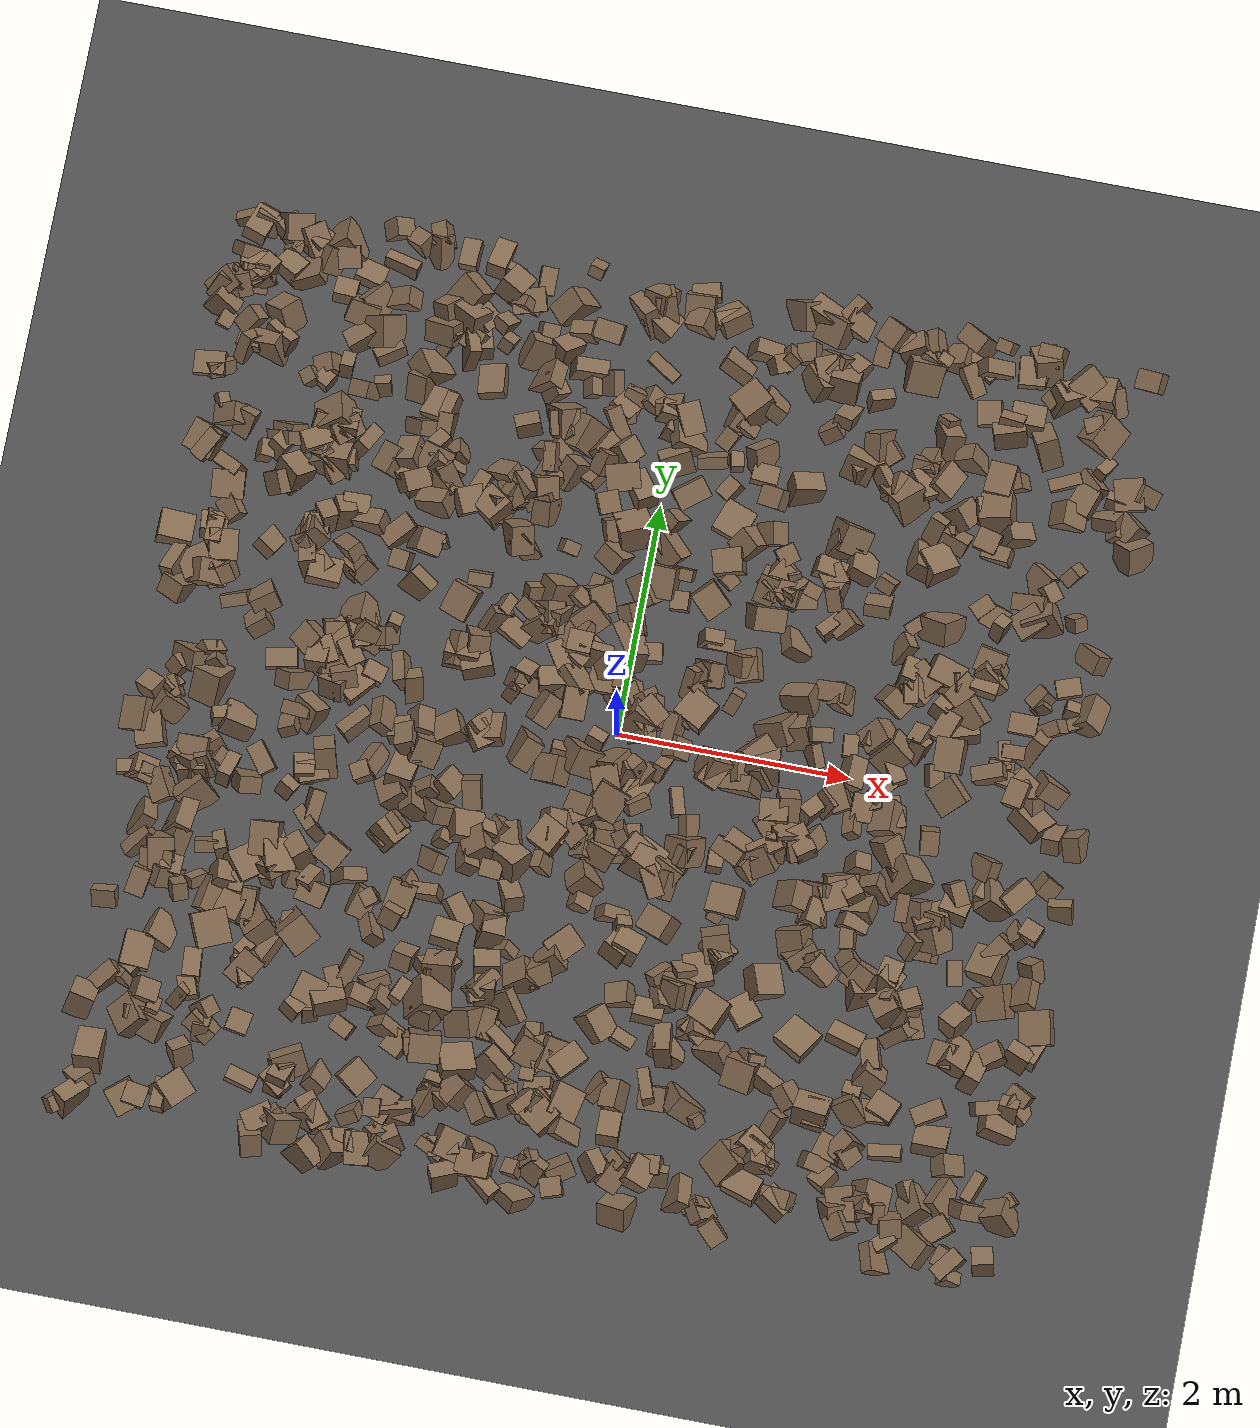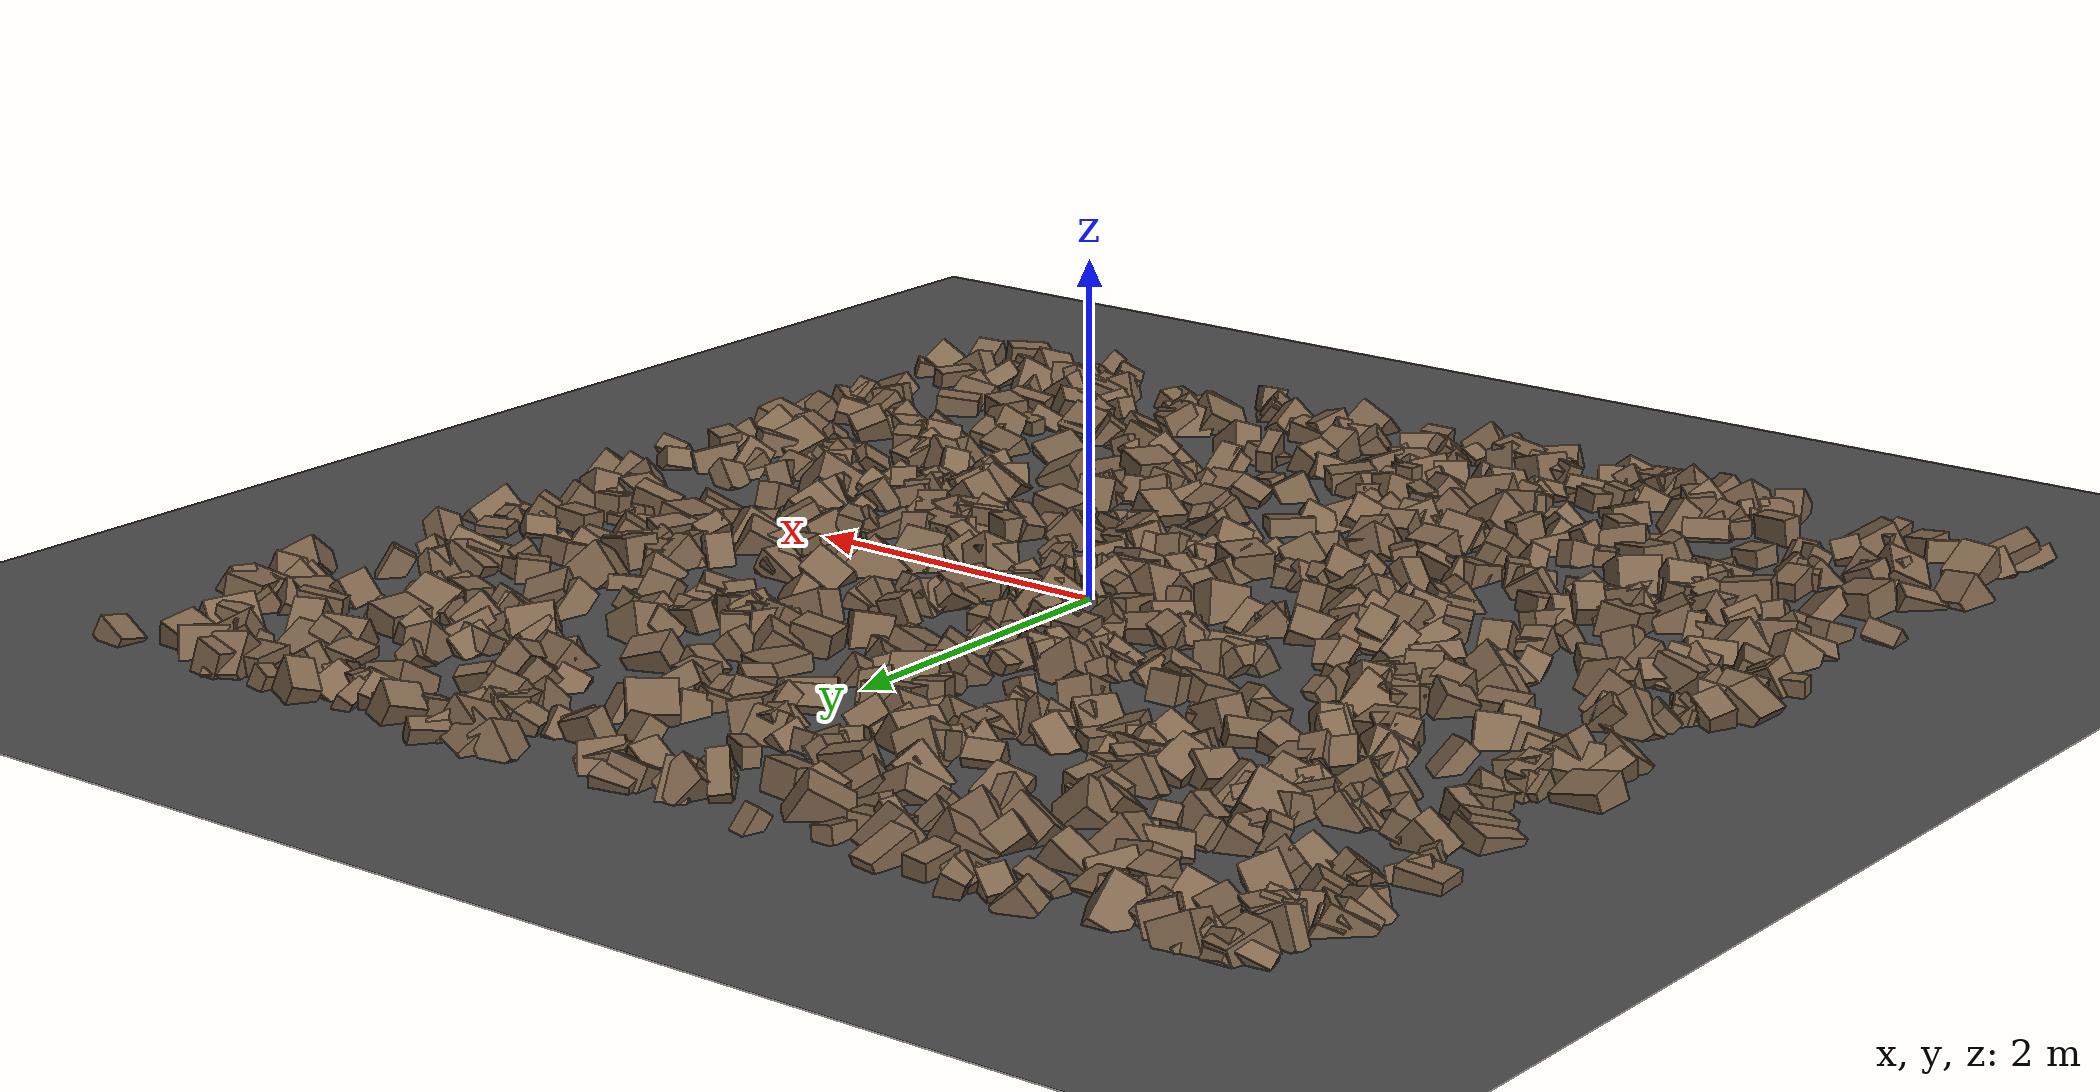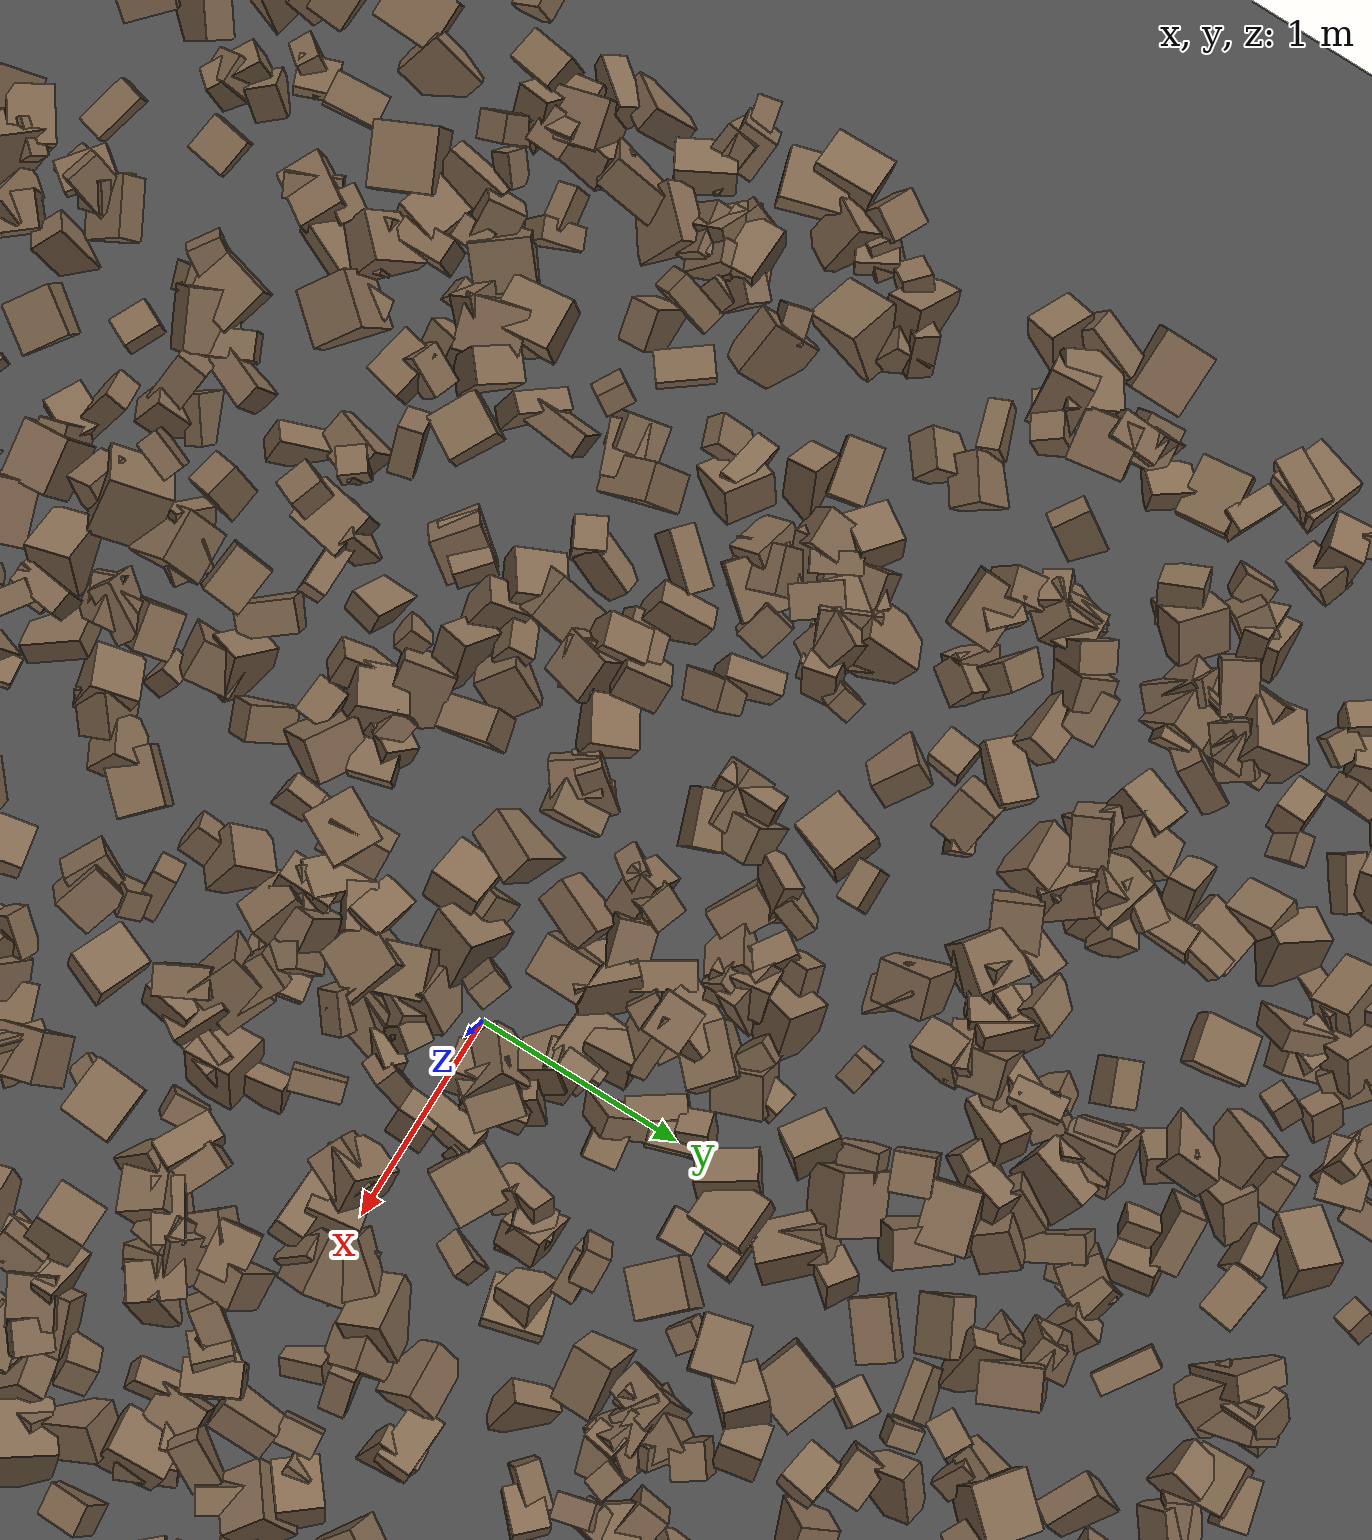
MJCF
<mujoco model="rocky_terrain_scene">
    <compiler angle="radian" inertiafromgeom="true" />
    <option timestep="0.002" gravity="0 0 -9.81" />

    <worldbody>
        <light name="sunlight" pos="5 5 5" dir="-1 -1 -1" diffuse="1 1 1" specular="0.5 0.5 0.5"
            ambient="0.5 0.5 0.5" />

        <geom name="ground_plane" type="plane" size="50 50 0.1" rgba="0.3 0.3 0.3 1" />

        <body name="rocky_terrain_body">

            <body name="rock1" pos="-3.8814159467011002 0.5555219599012258 0.016822423526344936">
                <joint type="free" />
                <geom name="rock1" type="box"
                    size="0.08688835565122366 0.10896556637852642 0.11274141733019442"
                    quat="0.27965365837810174 0.31430702145023814 0.08380588860728315 0.32223343156437695"
                    rgba="0.5 0.4 0.3 1" />
            </body>
            <body name="rock2" pos="-3.1792428876628422 1.0801831383321403 0.019798298667895026">
                <joint type="free" />
                <geom name="rock2" type="box"
                    size="0.1363232465039017 0.054294691391273624 0.09048619246000042"
                    quat="0.36052328142320567 0.2734924984468567 0.3228300460694954 0.04315417406044232"
                    rgba="0.5 0.4 0.3 1" />
            </body>
            <body name="rock3" pos="-1.3160487261708003 -1.624184981215186 0.0014637326069153933">
                <joint type="free" />
                <geom name="rock3" type="box"
                    size="0.05295014366071147 0.1375630226557521 0.12636894815747254"
                    quat="0.10223611549882367 0.4425622550855139 0.4384989841711931 0.016702645244469412"
                    rgba="0.5 0.4 0.3 1" />
            </body>
            <body name="rock4" pos="1.6577087485086324 0.13388583357181538 0.0001454856103547142">
                <joint type="free" />
                <geom name="rock4" type="box"
                    size="0.1019278683136074 0.07809362104935909 0.050059560281367155"
                    quat="0.09458227646170533 0.287619413449608 0.363091291255301 0.2547070188333856"
                    rgba="0.5 0.4 0.3 1" />
            </body>
            <body name="rock5" pos="-0.43376797094136244 2.824981031043577 0.007464523685949201">
                <joint type="free" />
                <geom name="rock5" type="box"
                    size="0.12081001399851501 0.06129801977914781 0.10461680861712222"
                    quat="0.33580853910869735 0.3346211765035338 0.21571315062295998 0.11385713376480895"
                    rgba="0.5 0.4 0.3 1" />
            </body>
            <body name="rock6" pos="1.8146943894329146 0.6609627195626331 0.012214616856209629">
                <joint type="free" />
                <geom name="rock6" type="box"
                    size="0.10724764298413048 0.054679922756913246 0.11166327530517595"
                    quat="0.18695341395597076 0.3678216081714822 0.3533134911021735 0.09191148677037345"
                    rgba="0.5 0.4 0.3 1" />
            </body>
            <body name="rock7" pos="-0.38410066553795197 -3.9358061224025844 0.01564006625070503">
                <joint type="free" />
                <geom name="rock7" type="box"
                    size="0.14627429536971087 0.09751963226139913 0.06480890914491622"
                    quat="0.14025519037315268 0.12116822462745519 0.42533326915101793 0.31324331584837417"
                    rgba="0.5 0.4 0.3 1" />
            </body>
            <body name="rock8" pos="0.8033899890850371 1.828363987841878 0.019244176998940005">
                <joint type="free" />
                <geom name="rock8" type="box"
                    size="0.10402414528034702 0.10325218183441584 0.13468056443001591"
                    quat="0.10176186889178901 0.20487767686894157 0.5371669125911182 0.15619354164815136"
                    rgba="0.5 0.4 0.3 1" />
            </body>
            <body name="rock9" pos="0.8798020485622766 3.868415221477589 0.0038524534796313195">
                <joint type="free" />
                <geom name="rock9" type="box"
                    size="0.125073407648843 0.1275033736631424 0.08525547486420934"
                    quat="0.07523663950463957 0.3481788297796501 0.3457086813808504 0.23087584933485997"
                    rgba="0.5 0.4 0.3 1" />
            </body>
            <body name="rock10" pos="0.7967471091073222 -2.1065533294688237 0.0009327666920943755">
                <joint type="free" />
                <geom name="rock10" type="box"
                    size="0.12491020829406653 0.055685561223185666 0.0953238513830913"
                    quat="0.2136782897984208 0.24264474322457374 0.4144305112465135 0.12924645573049193"
                    rgba="0.5 0.4 0.3 1" />
            </body>
            <body name="rock11" pos="-3.7218304568157983 2.9413772566403376 0.017699307134109107">
                <joint type="free" />
                <geom name="rock11" type="box"
                    size="0.07773379948711087 0.10788546628575288 0.07595645775642998"
                    quat="0.09488646965507866 0.214937417019233 0.5354306924860778 0.15474542083961063"
                    rgba="0.5 0.4 0.3 1" />
            </body>
            <body name="rock12" pos="1.894439339384852 -1.1455306331613846 0.0017214522260522536">
                <joint type="free" />
                <geom name="rock12" type="box"
                    size="0.14915006527067404 0.07698309887112335 0.10104777015882359"
                    quat="0.2852858008951425 0.17389165394214337 0.23277056537013568 0.30805197979257837"
                    rgba="0.5 0.4 0.3 1" />
            </body>
            <body name="rock13" pos="-2.8466264371921843 1.8718989242855715 0.006589587893616546">
                <joint type="free" />
                <geom name="rock13" type="box"
                    size="0.11957405201703658 0.08543272882226852 0.10934190189768798"
                    quat="0.23285331541140514 0.3611667229295966 0.3605868009957867 0.045393160663211564"
                    rgba="0.5 0.4 0.3 1" />
            </body>
            <body name="rock14" pos="-2.581806046034581 0.1894410438010654 0.016946130480487515">
                <joint type="free" />
                <geom name="rock14" type="box"
                    size="0.12264973987105539 0.1364898393941516 0.09399564487252765"
                    quat="0.08910847325304597 0.38528838989993136 0.07806594343404948 0.44753719341297327"
                    rgba="0.5 0.4 0.3 1" />
            </body>
            <body name="rock15" pos="3.233091215492923 -1.8782079743644635 0.01384564575926278">
                <joint type="free" />
                <geom name="rock15" type="box"
                    size="0.09039219078300711 0.13740935737661517 0.10797833376166602"
                    quat="0.16763068381491972 0.06694894133975082 0.4674577871319518 0.2979625877133777"
                    rgba="0.5 0.4 0.3 1" />
            </body>
            <body name="rock16" pos="3.889014195059006 -3.404407524392985 0.019304302093654163">
                <joint type="free" />
                <geom name="rock16" type="box"
                    size="0.09852910631446163 0.10961338172261487 0.13611174971275047"
                    quat="0.23428445448969973 0.36430109368582503 0.3831078765604388 0.01830657526403634"
                    rgba="0.5 0.4 0.3 1" />
            </body>
            <body name="rock17" pos="1.7828023915657667 -3.2953124253260233 0.0009001907830284917">
                <joint type="free" />
                <geom name="rock17" type="box"
                    size="0.12455356099491713 0.12093731697549011 0.13792393778549106"
                    quat="0.3738482968530341 0.028290709102432237 0.19803693158586694 0.39982406245866664"
                    rgba="0.5 0.4 0.3 1" />
            </body>
            <body name="rock18" pos="-2.7026578619608896 -2.3868831626975178 0.007234763461021068">
                <joint type="free" />
                <geom name="rock18" type="box"
                    size="0.07010759658661622 0.11787174022544657 0.06544425650427882"
                    quat="0.35737939834912086 0.2868008134555465 0.18716378803919384 0.16865600015613894"
                    rgba="0.5 0.4 0.3 1" />
            </body>
            <body name="rock19" pos="1.219378002916919 -3.712482736977365 0.0006556896513535015">
                <joint type="free" />
                <geom name="rock19" type="box"
                    size="0.13662067687035856 0.11214259314741301 0.0658548370243942"
                    quat="0.23580415956460204 0.2750458454003572 0.37689181505069785 0.11225817998434286"
                    rgba="0.5 0.4 0.3 1" />
            </body>
            <body name="rock20" pos="-1.9628498647209485 -2.6371761382972085 0.014819193069979794">
                <joint type="free" />
                <geom name="rock20" type="box"
                    size="0.0810953751739692 0.12702559878690145 0.1426634233604001"
                    quat="0.021585133824899433 0.4049907563118724 0.20788978613134007 0.3655343237318882"
                    rgba="0.5 0.4 0.3 1" />
            </body>
            <body name="rock21" pos="-0.020245924518150105 -3.2690743592120812 0.017581279575924615">
                <joint type="free" />
                <geom name="rock21" type="box"
                    size="0.13046760194902463 0.09722641913071015 0.14115152667109135"
                    quat="0.3516417925312388 0.31617839138143766 0.13131201489716848 0.200867801190155"
                    rgba="0.5 0.4 0.3 1" />
            </body>
            <body name="rock22" pos="-3.4646516192112493 -1.3773849122638175 0.014812573382220601">
                <joint type="free" />
                <geom name="rock22" type="box"
                    size="0.14807626991747053 0.14098418417459843 0.07649337869033276"
                    quat="0.2570223033624134 0.28542523759128646 0.3321372193545023 0.12541523969179785"
                    rgba="0.5 0.4 0.3 1" />
            </body>
            <body name="rock23" pos="2.249304061001493 -0.9504847935463587 0.002600631295846876">
                <joint type="free" />
                <geom name="rock23" type="box"
                    size="0.12643705330765354 0.05129807486905377 0.08289615141536961"
                    quat="0.06046000419953066 0.0993363154780272 0.26502916058410336 0.5751745197383389"
                    rgba="0.5 0.4 0.3 1" />
            </body>
            <body name="rock24" pos="1.2979616428636298 3.9560179217034452 0.01930040086345867">
                <joint type="free" />
                <geom name="rock24" type="box"
                    size="0.1432278825359316 0.072417173034583 0.058824542911774295"
                    quat="0.3755980769933931 0.28072817777497167 0.11564443797740591 0.2280293072542294"
                    rgba="0.5 0.4 0.3 1" />
            </body>
            <body name="rock25" pos="-1.7370464824329268 3.8593337512048915 0.008688309393532148">
                <joint type="free" />
                <geom name="rock25" type="box"
                    size="0.146114104693166 0.09734814063359712 0.08435976776387476"
                    quat="0.32027996213163623 0.22311553593447572 0.2770752328702321 0.17952926906365593"
                    rgba="0.5 0.4 0.3 1" />
            </body>
            <body name="rock26" pos="-3.7682297898438453 3.4349117734896497 0.004338368097247462">
                <joint type="free" />
                <geom name="rock26" type="box"
                    size="0.11370733734887374 0.07217688565131677 0.13799279302846498"
                    quat="0.06403260558947392 0.4565539930921134 0.04001052014541283 0.43940288117299986"
                    rgba="0.5 0.4 0.3 1" />
            </body>
            <body name="rock27" pos="-0.3624053005356531 -3.1944708505926016 0.0021088934488344103">
                <joint type="free" />
                <geom name="rock27" type="box"
                    size="0.11572543882795179 0.0999140008959204 0.10625036743193769"
                    quat="0.2752571831089882 0.05762334458171918 0.39220019872914963 0.27491927358014306"
                    rgba="0.5 0.4 0.3 1" />
            </body>
            <body name="rock28" pos="3.2646944621737912 1.9572794057834582 0.011313637737708833">
                <joint type="free" />
                <geom name="rock28" type="box"
                    size="0.11855706594086789 0.05332760412307122 0.12302443725733021"
                    quat="0.34691076865238935 0.2890368749004332 0.04498203007907399 0.3190703263681034"
                    rgba="0.5 0.4 0.3 1" />
            </body>
            <body name="rock29" pos="-0.3214971673519518 -3.151485782956107 0.01108456692307188">
                <joint type="free" />
                <geom name="rock29" type="box"
                    size="0.10720584780391865 0.08784718496938795 0.05099642322891579"
                    quat="0.0796206123662624 0.31963309611491525 0.32819792991095326 0.2725483616078691"
                    rgba="0.5 0.4 0.3 1" />
            </body>
            <body name="rock30" pos="2.2373217153810936 -1.2038520713003775 0.0022318480196684564">
                <joint type="free" />
                <geom name="rock30" type="box"
                    size="0.062392407506349806 0.08950106064565352 0.11570627628674492"
                    quat="0.2308510041903148 0.31386123510169095 0.2897321770668072 0.165555583641187"
                    rgba="0.5 0.4 0.3 1" />
            </body>
            <body name="rock31" pos="2.996761663491381 -3.626552070050563 0.017957373813899325">
                <joint type="free" />
                <geom name="rock31" type="box"
                    size="0.09357777118448535 0.11589917456890783 0.08403969454953375"
                    quat="0.3360697583593623 0.5609344888251881 0.0745439021564337 0.02845185065901594"
                    rgba="0.5 0.4 0.3 1" />
            </body>
            <body name="rock32" pos="-3.1436166903216236 0.6007432973139659 0.001379295162452785">
                <joint type="free" />
                <geom name="rock32" type="box"
                    size="0.11659152003395994 0.12650818389003782 0.08067016839016214"
                    quat="0.22996224346825 0.5204826717082116 0.14413744161848846 0.10541764320504982"
                    rgba="0.5 0.4 0.3 1" />
            </body>
            <body name="rock33" pos="1.2152945873857588 -3.061392566572409 0.006286056658719024">
                <joint type="free" />
                <geom name="rock33" type="box"
                    size="0.05405518840498143 0.05379004506323525 0.11276943176324836"
                    quat="0.49557154198446535 0.14888106331355902 0.1545682479905528 0.20097914671142286"
                    rgba="0.5 0.4 0.3 1" />
            </body>
            <body name="rock34" pos="-0.45024749193446745 -2.745478791713924 0.01710296951294457">
                <joint type="free" />
                <geom name="rock34" type="box"
                    size="0.14604324899974427 0.09847798954590928 0.05528718217436527"
                    quat="0.11174460218266359 0.13245436948769893 0.4010561631354471 0.3547448651941904"
                    rgba="0.5 0.4 0.3 1" />
            </body>
            <body name="rock35" pos="3.7804215409665183 -0.5950547741237218 0.012244917732842435">
                <joint type="free" />
                <geom name="rock35" type="box"
                    size="0.08605559768466413 0.0674466855285102 0.09035711559399204"
                    quat="0.17388095109954066 0.4407416150145854 0.21746229582502935 0.16791513806084463"
                    rgba="0.5 0.4 0.3 1" />
            </body>
            <body name="rock36" pos="0.00503537070725546 1.2672180551584464 0.009879542280864788">
                <joint type="free" />
                <geom name="rock36" type="box"
                    size="0.1425435019819139 0.10151549061239577 0.08351330833735218"
                    quat="0.21552484728152158 0.14342373816867465 0.2050721700434166 0.4359792445063871"
                    rgba="0.5 0.4 0.3 1" />
            </body>
            <body name="rock37" pos="0.9259403383282168 2.2548088342849253 0.013131669925442726">
                <joint type="free" />
                <geom name="rock37" type="box"
                    size="0.0892731586763671 0.06981188604320675 0.1065676623376283"
                    quat="0.3162325294976164 0.22944403574439276 0.14470512428708995 0.3096183104709009"
                    rgba="0.5 0.4 0.3 1" />
            </body>
            <body name="rock38" pos="-1.5021879750409752 0.8893721053836874 0.0006615984539416231">
                <joint type="free" />
                <geom name="rock38" type="box"
                    size="0.0753541538241803 0.14089326205936265 0.12114273711823396"
                    quat="0.4665084204973098 0.1503926542140967 0.38170298571140954 0.001395939577183971"
                    rgba="0.5 0.4 0.3 1" />
            </body>
            <body name="rock39" pos="-1.0185134512919394 -1.721396323947947 0.01640361163383451">
                <joint type="free" />
                <geom name="rock39" type="box"
                    size="0.13970063423172438 0.07800254829268426 0.08526609990449743"
                    quat="0.27899569255348106 0.08838491803795566 0.050512952127930714 0.5821064372806326"
                    rgba="0.5 0.4 0.3 1" />
            </body>
            <body name="rock40" pos="2.1954788626487085 2.6228546216737483 0.01667479815643708">
                <joint type="free" />
                <geom name="rock40" type="box"
                    size="0.13542513656865351 0.06635872520253794 0.1394458654189651"
                    quat="0.15322867962867742 0.19249695439176218 0.41148540700116915 0.24278895897839117"
                    rgba="0.5 0.4 0.3 1" />
            </body>
            <body name="rock41" pos="0.14109430123569666 -0.8888722572860361 0.019519208182873303">
                <joint type="free" />
                <geom name="rock41" type="box"
                    size="0.1050898465296312 0.09811204868841703 0.14137264392902193"
                    quat="0.10252534367004328 0.24195516520849844 0.2413422755689067 0.4141772155525516"
                    rgba="0.5 0.4 0.3 1" />
            </body>
            <body name="rock42" pos="3.4528009309673555 -2.2568659730526637 0.011612298941154942">
                <joint type="free" />
                <geom name="rock42" type="box"
                    size="0.10841715695284182 0.13684671319483493 0.07285414544102518"
                    quat="0.15861973991970554 0.4341838899685664 0.047633140856332766 0.35956322925539536"
                    rgba="0.5 0.4 0.3 1" />
            </body>
            <body name="rock43" pos="3.862759139055222 -2.4816753493296426 0.003703170273875538">
                <joint type="free" />
                <geom name="rock43" type="box"
                    size="0.09348063947651 0.061833722604250366 0.11713322861763382"
                    quat="0.3002833388126847 0.3315453504113332 0.31181977598373745 0.056351534792244654"
                    rgba="0.5 0.4 0.3 1" />
            </body>
            <body name="rock44" pos="-2.283969337718468 0.4400527791330422 0.0022295600660191183">
                <joint type="free" />
                <geom name="rock44" type="box"
                    size="0.13972309737905952 0.11656433261308598 0.13426091332327397"
                    quat="0.1668943885802623 0.22728262603823748 0.3857104908143367 0.22011249456716359"
                    rgba="0.5 0.4 0.3 1" />
            </body>
            <body name="rock45" pos="-0.44598216418991576 0.35139094613548494 0.0032328141842811542">
                <joint type="free" />
                <geom name="rock45" type="box"
                    size="0.12566716520753507 0.10918516887341742 0.14786714668713133"
                    quat="0.31645621326422774 0.39217055430677483 0.00258719237468477 0.2887860400543127"
                    rgba="0.5 0.4 0.3 1" />
            </body>
            <body name="rock46" pos="-2.765083188755331 2.9662216343152012 0.001674148991829456">
                <joint type="free" />
                <geom name="rock46" type="box"
                    size="0.1303566785772035 0.09090067361414586 0.08932853883638532"
                    quat="0.11661736778277805 0.5872681955998713 0.19654118262815468 0.09957325398919602"
                    rgba="0.5 0.4 0.3 1" />
            </body>
            <body name="rock47" pos="-0.21388856984057902 2.8831928333069596 0.012270872481318456">
                <joint type="free" />
                <geom name="rock47" type="box"
                    size="0.08684676531147228 0.06092488363043776 0.10749619099264687"
                    quat="0.2461881454666094 0.3441036500913602 0.32022359656537325 0.08948460787665719"
                    rgba="0.5 0.4 0.3 1" />
            </body>
            <body name="rock48" pos="-3.5265086825713237 2.737141948113277 0.012255147307287256">
                <joint type="free" />
                <geom name="rock48" type="box"
                    size="0.08017253581090976 0.13148563933835972 0.14566699149263312"
                    quat="0.3938675030963773 0.1584519701944919 0.22615784872775146 0.22152267798137945"
                    rgba="0.5 0.4 0.3 1" />
            </body>
            <body name="rock49" pos="2.8791284470164555 0.706495587397896 0.011710510680834766">
                <joint type="free" />
                <geom name="rock49" type="box"
                    size="0.13029919496558928 0.08067828128265402 0.12287447633397343"
                    quat="0.3053894495892439 0.42152381335213035 0.03378529416325493 0.23930144289537078"
                    rgba="0.5 0.4 0.3 1" />
            </body>
            <body name="rock50" pos="-2.1213262711841283 -2.631434870572476 0.012550164769493164">
                <joint type="free" />
                <geom name="rock50" type="box"
                    size="0.12426258694886527 0.08690324462021866 0.14605112164784567"
                    quat="0.029856801172355688 0.08779314781145374 0.4221756305588443 0.46017442045734624"
                    rgba="0.5 0.4 0.3 1" />
            </body>
            <body name="rock51" pos="-0.3268370766585109 3.738143352825893 0.017556111086885286">
                <joint type="free" />
                <geom name="rock51" type="box"
                    size="0.12501697081511354 0.1137178391619896 0.1082243483017791"
                    quat="0.2541954270208875 0.2875496138004977 0.07803256004039409 0.38022239913822076"
                    rgba="0.5 0.4 0.3 1" />
            </body>
            <body name="rock52" pos="-2.549966916137304 3.6553695654553042 0.00669574652207148">
                <joint type="free" />
                <geom name="rock52" type="box"
                    size="0.06810578453467175 0.05263374011217117 0.14983845314092953"
                    quat="0.1596736393238565 0.38888070571642575 0.05084325335360633 0.40060240160611144"
                    rgba="0.5 0.4 0.3 1" />
            </body>
            <body name="rock53" pos="-1.5639988407588143 -0.4217807212217437 0.019838665455354978">
                <joint type="free" />
                <geom name="rock53" type="box"
                    size="0.1161816141664953 0.1115869194171733 0.11311941915610695"
                    quat="0.1650722386220545 0.37468259621181427 0.21303009825789257 0.24721506690823872"
                    rgba="0.5 0.4 0.3 1" />
            </body>
            <body name="rock54" pos="-3.316364050397728 3.441292339862179 0.011609058194036457">
                <joint type="free" />
                <geom name="rock54" type="box"
                    size="0.127679209040774 0.06379181631593157 0.14441565777657236"
                    quat="0.3501237353556915 0.0952049377861536 0.26949922273520477 0.2851721041229501"
                    rgba="0.5 0.4 0.3 1" />
            </body>
            <body name="rock55" pos="-1.7679995537854802 3.3305149228391198 0.013889722190532172">
                <joint type="free" />
                <geom name="rock55" type="box"
                    size="0.09446243338801846 0.09864839052363747 0.06665198074871723"
                    quat="0.5378932368377727 0.04839694570802342 0.12966556261155254 0.2840442548426514"
                    rgba="0.5 0.4 0.3 1" />
            </body>
            <body name="rock56" pos="-2.626287716803988 -2.162656244940143 0.014229318335948376">
                <joint type="free" />
                <geom name="rock56" type="box"
                    size="0.13709283055408467 0.12649101944322888 0.11866820848108729"
                    quat="0.3058507215096337 0.005344382776780427 0.36538717231955425 0.3234177233940317"
                    rgba="0.5 0.4 0.3 1" />
            </body>
            <body name="rock57" pos="-1.5060173072213674 -0.7636527639016997 0.008256558521074214">
                <joint type="free" />
                <geom name="rock57" type="box"
                    size="0.0675644144936687 0.13167615215464173 0.06709466612713368"
                    quat="0.22090096877087786 0.31585611429529287 0.4136467601591746 0.049596156774654745"
                    rgba="0.5 0.4 0.3 1" />
            </body>
            <body name="rock58" pos="-1.710110747737171 -2.002285972944711 0.011020725702518549">
                <joint type="free" />
                <geom name="rock58" type="box"
                    size="0.1336160865600256 0.07864951309290073 0.0584169650690276"
                    quat="0.32255368366987996 0.03445813097245315 0.2845275552794274 0.3584606300782394"
                    rgba="0.5 0.4 0.3 1" />
            </body>
            <body name="rock59" pos="0.6093973357385272 -1.091073857720871 0.0095107128268074">
                <joint type="free" />
                <geom name="rock59" type="box"
                    size="0.1261667601997284 0.07727024392271317 0.13179206084307865"
                    quat="0.25008689883540325 0.3703282318911913 0.11544481109966225 0.26414005817374314"
                    rgba="0.5 0.4 0.3 1" />
            </body>
            <body name="rock60" pos="-2.18470426637532 2.650989488564469 0.010199777077491472">
                <joint type="free" />
                <geom name="rock60" type="box"
                    size="0.09129861260147408 0.12103952542175778 0.10730468952756608"
                    quat="0.13749664612885332 0.02806923657610691 0.6361673761006534 0.19826674119438634"
                    rgba="0.5 0.4 0.3 1" />
            </body>
            <body name="rock61" pos="-3.9823444803153585 3.032765833127981 0.01115038389242198">
                <joint type="free" />
                <geom name="rock61" type="box"
                    size="0.07767198605377831 0.10440354758183903 0.11767829778312647"
                    quat="0.3079757394130493 0.28817096033401046 0.3396776668752637 0.06417563337767657"
                    rgba="0.5 0.4 0.3 1" />
            </body>
            <body name="rock62" pos="-3.8538068758354926 -3.682778156664548 0.0020260012641888704">
                <joint type="free" />
                <geom name="rock62" type="box"
                    size="0.08730627896590776 0.1018221948165875 0.0692748395803374"
                    quat="0.22073808115903487 0.5201689581183991 0.24853782639321267 0.010555134329353325"
                    rgba="0.5 0.4 0.3 1" />
            </body>
            <body name="rock63" pos="3.049624610165991 -0.807878455184607 0.0005273976995781937">
                <joint type="free" />
                <geom name="rock63" type="box"
                    size="0.12045263751138834 0.0942997893470193 0.06995636237379158"
                    quat="0.1103024048994277 0.26044724542263104 0.33837699960960743 0.29087335006833387"
                    rgba="0.5 0.4 0.3 1" />
            </body>
            <body name="rock64" pos="2.6450318291461272 0.7391003206364521 0.00799828841074434">
                <joint type="free" />
                <geom name="rock64" type="box"
                    size="0.07403024970836146 0.07998852761536271 0.08481989384812946"
                    quat="0.15888097189131098 0.033127448593944994 0.1773202880099453 0.6306712915047986"
                    rgba="0.5 0.4 0.3 1" />
            </body>
            <body name="rock65" pos="-2.0877885023487837 2.308275072272874 0.0010024349139961908">
                <joint type="free" />
                <geom name="rock65" type="box"
                    size="0.06565119132509242 0.11482744249617773 0.13234412882586916"
                    quat="0.09765760026704455 0.3583992190940811 0.3264414445215839 0.21750173611729048"
                    rgba="0.5 0.4 0.3 1" />
            </body>
            <body name="rock66" pos="-2.827665717281347 1.278524786897389 0.011851594442962956">
                <joint type="free" />
                <geom name="rock66" type="box"
                    size="0.10871305812202556 0.06447984478185778 0.10966950259984808"
                    quat="0.2481709333787119 0.24105542509135244 0.25612627305821173 0.25464736847172387"
                    rgba="0.5 0.4 0.3 1" />
            </body>
            <body name="rock67" pos="-3.1552356561852903 -2.839334040891134 0.004537279766605525">
                <joint type="free" />
                <geom name="rock67" type="box"
                    size="0.054831877405617915 0.12528525368962162 0.0904862215189137"
                    quat="0.047596372879657886 0.16568258462945262 0.5437613103496863 0.24295973214120314"
                    rgba="0.5 0.4 0.3 1" />
            </body>
            <body name="rock68" pos="0.5590423454351106 2.4990123137658298 0.010846186393422788">
                <joint type="free" />
                <geom name="rock68" type="box"
                    size="0.06366485887724657 0.07426045010512873 0.052777584888907485"
                    quat="0.02215272717906963 0.45167447662905064 0.10493007665268551 0.42124271953919423"
                    rgba="0.5 0.4 0.3 1" />
            </body>
            <body name="rock69" pos="2.7952640131332354 2.7553463033059176 0.019660981203411042">
                <joint type="free" />
                <geom name="rock69" type="box"
                    size="0.13710623845441744 0.11643239932985408 0.11332478387090003"
                    quat="0.04523715501124636 0.47651820264537537 0.43295791259039895 0.045286729752979336"
                    rgba="0.5 0.4 0.3 1" />
            </body>
            <body name="rock70" pos="-0.29888019159365165 1.5051192866780205 0.003499745015192526">
                <joint type="free" />
                <geom name="rock70" type="box"
                    size="0.11318026102335338 0.08395986689628915 0.11361153173580944"
                    quat="0.09593559044675265 0.16884458904296007 0.5707255463346922 0.1644942741755951"
                    rgba="0.5 0.4 0.3 1" />
            </body>
            <body name="rock71" pos="1.044477080194457 1.2224026004948207 0.014190786628655696">
                <joint type="free" />
                <geom name="rock71" type="box"
                    size="0.1002865743284338 0.12384465635598724 0.14327282599711902"
                    quat="0.15102009891074794 0.32735193705289584 0.2779272927591833 0.24370067127717301"
                    rgba="0.5 0.4 0.3 1" />
            </body>
            <body name="rock72" pos="0.6026576313157106 -0.4713540398785794 0.0023852575064482505">
                <joint type="free" />
                <geom name="rock72" type="box"
                    size="0.12238111226682753 0.07099235617698123 0.05161995147602044"
                    quat="0.20540882805727323 0.22423330963856444 0.32285653013164367 0.24750133217251874"
                    rgba="0.5 0.4 0.3 1" />
            </body>
            <body name="rock73" pos="2.7759277244015728 -2.6889503467299276 0.01154999974382703">
                <joint type="free" />
                <geom name="rock73" type="box"
                    size="0.09592614107976898 0.14576130213803284 0.11588378968386079"
                    quat="0.3145688273270188 0.2879184607393319 0.19990462527539327 0.19760808665825602"
                    rgba="0.5 0.4 0.3 1" />
            </body>
            <body name="rock74" pos="-1.2601835370959193 0.3553153595267773 0.009420191438234582">
                <joint type="free" />
                <geom name="rock74" type="box"
                    size="0.07916540574193598 0.10530178812381921 0.13206262430516827"
                    quat="0.2703901688354175 0.14068068585707683 0.32528940638124365 0.2636397389262619"
                    rgba="0.5 0.4 0.3 1" />
            </body>
            <body name="rock75" pos="2.3107316181214657 0.27768997077558044 0.011320006891043732">
                <joint type="free" />
                <geom name="rock75" type="box"
                    size="0.1232870876433834 0.14410335933644444 0.11506800384418635"
                    quat="0.3325637047833018 0.27233031441417044 0.3808170837699986 0.014288897032529058"
                    rgba="0.5 0.4 0.3 1" />
            </body>
            <body name="rock76" pos="0.6206068596348793 3.0130301328478364 0.0185616344190443">
                <joint type="free" />
                <geom name="rock76" type="box"
                    size="0.14172238356656322 0.12522950409274952 0.1427448381795257"
                    quat="0.22848133009913082 0.05788823202077023 0.37389787887810544 0.3397325590019935"
                    rgba="0.5 0.4 0.3 1" />
            </body>
            <body name="rock77" pos="-3.3037334633628888 -0.7381828514099551 0.01157288469209223">
                <joint type="free" />
                <geom name="rock77" type="box"
                    size="0.08825349080278846 0.11453770032275624 0.06830023463510634"
                    quat="0.4861732281642362 0.22657515379400678 0.09393765955917883 0.1933139584825783"
                    rgba="0.5 0.4 0.3 1" />
            </body>
            <body name="rock78" pos="3.2821799276343153 0.23625759600465468 0.003637159917933601">
                <joint type="free" />
                <geom name="rock78" type="box"
                    size="0.06450731505528683 0.07526952997307548 0.07038445612624034"
                    quat="0.08584752783330536 0.48425333133703463 0.3907132170810364 0.039185923748623605"
                    rgba="0.5 0.4 0.3 1" />
            </body>
            <body name="rock79" pos="3.0315570121033177 1.1506158395469965 0.008543603795336117">
                <joint type="free" />
                <geom name="rock79" type="box"
                    size="0.05672867114158025 0.08685868562205608 0.06145757520020895"
                    quat="0.2225057123711623 0.4001137009101927 0.3705596902923089 0.006820896426336114"
                    rgba="0.5 0.4 0.3 1" />
            </body>
            <body name="rock80" pos="-3.704865257192539 2.705067739611718 0.01819519631720872">
                <joint type="free" />
                <geom name="rock80" type="box"
                    size="0.12990206821442885 0.0930613220710095 0.054932968665493326"
                    quat="0.2603396199775512 0.3284868232194016 0.06955403049427848 0.34161952630876874"
                    rgba="0.5 0.4 0.3 1" />
            </body>
            <body name="rock81" pos="1.3813908950047624 1.5317497029094946 0.0008067007426064366">
                <joint type="free" />
                <geom name="rock81" type="box"
                    size="0.058433293821299206 0.13923592861435968 0.07091094431000959"
                    quat="0.24246973670323316 0.33216323657532554 0.2068857273641052 0.21848129935733615"
                    rgba="0.5 0.4 0.3 1" />
            </body>
            <body name="rock82" pos="-0.5950643040211219 2.16923901758868 0.012595276522307543">
                <joint type="free" />
                <geom name="rock82" type="box"
                    size="0.11397813751117244 0.08135211604397656 0.05379255082957582"
                    quat="0.16954792165274093 0.4882933028351137 0.2874195255226707 0.05473924998947476"
                    rgba="0.5 0.4 0.3 1" />
            </body>
            <body name="rock83" pos="1.9826441464975648 -2.725244926406118 0.005598275082634274">
                <joint type="free" />
                <geom name="rock83" type="box"
                    size="0.1022557504937197 0.12683134315605404 0.06912276731909231"
                    quat="0.20984554860860558 0.10934281302381542 0.22269747144958285 0.4581141669179962"
                    rgba="0.5 0.4 0.3 1" />
            </body>
            <body name="rock84" pos="0.9321923509636081 -3.529067961067714 0.005293789485177716">
                <joint type="free" />
                <geom name="rock84" type="box"
                    size="0.08061834734576921 0.1265218919209431 0.10233121361589145"
                    quat="0.05824017931012191 0.4376272531018257 0.47276159303958615 0.03137097454846628"
                    rgba="0.5 0.4 0.3 1" />
            </body>
            <body name="rock85" pos="-0.5904263315397307 -2.591093666852333 0.0076097600542719196">
                <joint type="free" />
                <geom name="rock85" type="box"
                    size="0.1319267022954539 0.109732228713665 0.06104397658129144"
                    quat="0.2337264766165474 0.2960099549744961 0.190340742516449 0.27992282589250744"
                    rgba="0.5 0.4 0.3 1" />
            </body>
            <body name="rock86" pos="1.965909711098094 -2.2437553556887266 0.0065215464000656365">
                <joint type="free" />
                <geom name="rock86" type="box"
                    size="0.13965558125741623 0.06418865765698564 0.14886589232651876"
                    quat="0.37960903154214365 0.2598828262670145 0.20276695250941526 0.15774118968142664"
                    rgba="0.5 0.4 0.3 1" />
            </body>
            <body name="rock87" pos="1.7521657521090281 -0.2966608294894435 0.010200505503462702">
                <joint type="free" />
                <geom name="rock87" type="box"
                    size="0.14576504733520362 0.08147364504352528 0.06785344547167853"
                    quat="0.3897325605755434 0.2857433563628302 0.21412377012960868 0.11040031293201778"
                    rgba="0.5 0.4 0.3 1" />
            </body>
            <body name="rock88" pos="-0.6991634020295159 1.5093389880825816 0.0042123186113652775">
                <joint type="free" />
                <geom name="rock88" type="box"
                    size="0.05504310185177916 0.0718697578858252 0.07768635235327034"
                    quat="0.44255952002533866 0.12288085130425709 0.058472638814903125 0.37608698985550104"
                    rgba="0.5 0.4 0.3 1" />
            </body>
            <body name="rock89" pos="2.8498548271362347 0.563159917156205 0.007201782029161323">
                <joint type="free" />
                <geom name="rock89" type="box"
                    size="0.058784772812459966 0.08556450544418134 0.14483739237056364"
                    quat="0.042292898839776785 0.3807617561978629 0.16817285110082386 0.40877249386153636"
                    rgba="0.5 0.4 0.3 1" />
            </body>
            <body name="rock90" pos="2.6102964992525255 -1.620066871864351 0.009757032646592887">
                <joint type="free" />
                <geom name="rock90" type="box"
                    size="0.09510713112957311 0.10180817440102968 0.09988293698535758"
                    quat="0.32190465039018334 0.2953162943223845 0.2976144714308927 0.08516458385653948"
                    rgba="0.5 0.4 0.3 1" />
            </body>
            <body name="rock91" pos="-1.067192814228953 1.454807958727284 0.008141735119003488">
                <joint type="free" />
                <geom name="rock91" type="box"
                    size="0.14213157318537561 0.07094552859716571 0.0776318633176012"
                    quat="0.051204433764946176 0.23816255170539516 0.23238552511400537 0.4782474894156532"
                    rgba="0.5 0.4 0.3 1" />
            </body>
            <body name="rock92" pos="2.3849201933710713 3.5723439390111666 0.007377302238305798">
                <joint type="free" />
                <geom name="rock92" type="box"
                    size="0.06729274981186825 0.07183495816131724 0.1424399435344475"
                    quat="0.3212961327652495 0.44162133223805733 0.18123094831126507 0.05585158668542802"
                    rgba="0.5 0.4 0.3 1" />
            </body>
            <body name="rock93" pos="-1.8594698258992421 1.8231461751001081 0.00755015847809803">
                <joint type="free" />
                <geom name="rock93" type="box"
                    size="0.07231963846335418 0.09699417421262727 0.13071575336936442"
                    quat="0.42349602505096234 0.26239482501487016 0.30127023892899135 0.012838911005176229"
                    rgba="0.5 0.4 0.3 1" />
            </body>
            <body name="rock94" pos="2.295548007769069 -3.2450185555465234 0.019549869350430592">
                <joint type="free" />
                <geom name="rock94" type="box"
                    size="0.06929599828857771 0.06686737843712777 0.11543490886462274"
                    quat="0.20204010974416953 0.3404033859689249 0.26926759399940847 0.18828891028749717"
                    rgba="0.5 0.4 0.3 1" />
            </body>
            <body name="rock95" pos="0.13710110231486095 1.8915554880043262 0.007170589980379454">
                <joint type="free" />
                <geom name="rock95" type="box"
                    size="0.07614255889448623 0.10223185326332261 0.08307409999359855"
                    quat="0.2076095791619719 0.032373713890140585 0.2799705045816237 0.48004620236626383"
                    rgba="0.5 0.4 0.3 1" />
            </body>
            <body name="rock96" pos="-2.294975354463495 1.9612224253067252 0.0015964909986468335">
                <joint type="free" />
                <geom name="rock96" type="box"
                    size="0.12544367792114475 0.12022044289205523 0.09821127059349019"
                    quat="0.3754670208651485 0.22115176492953578 0.1160574499406942 0.2873237642646215"
                    rgba="0.5 0.4 0.3 1" />
            </body>
            <body name="rock97" pos="1.3425810717741546 3.3534769613748425 0.006808284313292104">
                <joint type="free" />
                <geom name="rock97" type="box"
                    size="0.12534285336288703 0.13090721695743318 0.12394862960497333"
                    quat="0.15057217406258114 0.362769913883064 0.10922779672815607 0.3774301153261989"
                    rgba="0.5 0.4 0.3 1" />
            </body>
            <body name="rock98" pos="-1.3935207949318853 0.47551348466892396 0.013139613789102972">
                <joint type="free" />
                <geom name="rock98" type="box"
                    size="0.14532545503299435 0.13950982392269412 0.06005552448785974"
                    quat="0.3514900820036022 0.16862146436448885 0.11455200531541736 0.36533644831649165"
                    rgba="0.5 0.4 0.3 1" />
            </body>
            <body name="rock99" pos="1.580365139840274 -3.3826665890415653 0.01428740336756823">
                <joint type="free" />
                <geom name="rock99" type="box"
                    size="0.14372293170482092 0.1352293260232953 0.1265013425890027"
                    quat="0.0228178431742176 0.5417842027121561 0.25199412647828373 0.1834038276353426"
                    rgba="0.5 0.4 0.3 1" />
            </body>
            <body name="rock100" pos="2.781085111201021 -1.2996657627731745 0.012442102726018976">
                <joint type="free" />
                <geom name="rock100" type="box"
                    size="0.10372223055659258 0.09149101377952426 0.0629117980381607"
                    quat="0.35079744789085304 0.2928321159637699 0.016285923292228152 0.3400845128531489"
                    rgba="0.5 0.4 0.3 1" />
            </body>
            <body name="rock101" pos="3.792046564847345 -2.062997056359098 0.007621651509073279">
                <joint type="free" />
                <geom name="rock101" type="box"
                    size="0.07573018482770376 0.1080976132773404 0.10503148374350135"
                    quat="0.364994535405593 0.23504781963989543 0.29298122649942415 0.10697641845508746"
                    rgba="0.5 0.4 0.3 1" />
            </body>
            <body name="rock102" pos="1.326382722883996 0.2974822660129872 0.007836326583861651">
                <joint type="free" />
                <geom name="rock102" type="box"
                    size="0.12457836891784542 0.10847861467950419 0.1458327750381271"
                    quat="0.5083879652514004 0.05519594287735507 0.25617988542283543 0.18023620644840907"
                    rgba="0.5 0.4 0.3 1" />
            </body>
            <body name="rock103" pos="-0.09012524217234041 2.8975131787589143 0.0057350777343160055">
                <joint type="free" />
                <geom name="rock103" type="box"
                    size="0.11148978573921929 0.14932496252370475 0.05688371594947052"
                    quat="0.30661253160357316 0.6226689431753557 0.016207877696340686 0.05451064752473044"
                    rgba="0.5 0.4 0.3 1" />
            </body>
            <body name="rock104" pos="3.2431106375771916 -0.5336749626696315 0.004009715086288188">
                <joint type="free" />
                <geom name="rock104" type="box"
                    size="0.06299005997614257 0.09547366737484525 0.11431777227579872"
                    quat="0.5974870147539888 0.13120890256481296 0.26627748532985046 0.005026597351347787"
                    rgba="0.5 0.4 0.3 1" />
            </body>
            <body name="rock105" pos="-2.635199877414414 -1.7173810035167918 0.012840841397344753">
                <joint type="free" />
                <geom name="rock105" type="box"
                    size="0.06810252247465465 0.08374543148756783 0.05239323811918222"
                    quat="0.10130006205135551 0.36701804259580273 0.060473758796689 0.47120813655615273"
                    rgba="0.5 0.4 0.3 1" />
            </body>
            <body name="rock106" pos="-0.9946274327764959 1.9558061121952672 0.01556982623760816">
                <joint type="free" />
                <geom name="rock106" type="box"
                    size="0.12803032777653686 0.1048970101141633 0.09508023698789159"
                    quat="0.12810646423445163 0.3078611683695195 0.2792309516773748 0.284801415718654"
                    rgba="0.5 0.4 0.3 1" />
            </body>
            <body name="rock107" pos="-2.7522875761164416 -0.03009901027630235 0.005499390273107898">
                <joint type="free" />
                <geom name="rock107" type="box"
                    size="0.07585079794242136 0.09101462978276943 0.1400214274270825"
                    quat="0.06720793648700295 0.3788614175754952 0.336088903494764 0.21784174244273793"
                    rgba="0.5 0.4 0.3 1" />
            </body>
            <body name="rock108" pos="2.8565443613589228 -1.966289629031067 0.007676737605718833">
                <joint type="free" />
                <geom name="rock108" type="box"
                    size="0.11876349308588376 0.08360584947535916 0.08742689422028468"
                    quat="0.09278147674417397 0.3068452841677617 0.41732037029780267 0.18305286879026172"
                    rgba="0.5 0.4 0.3 1" />
            </body>
            <body name="rock109" pos="-1.5474337630805808 -1.83163538079409 0.015393122429286664">
                <joint type="free" />
                <geom name="rock109" type="box"
                    size="0.12774961910219068 0.08931668304798017 0.0821883452923545"
                    quat="0.38427398435537724 0.20000829653409896 0.34460925443238627 0.07110846467813753"
                    rgba="0.5 0.4 0.3 1" />
            </body>
            <body name="rock110" pos="0.6162370031538549 3.4765832329229607 0.015583932965741034">
                <joint type="free" />
                <geom name="rock110" type="box"
                    size="0.06715083813131423 0.12049189190588579 0.13457460953980022"
                    quat="0.4249165856544912 0.04301807261778803 0.11539202295476601 0.41667331877295477"
                    rgba="0.5 0.4 0.3 1" />
            </body>
            <body name="rock111" pos="-0.49322874085879853 2.29066346280654 0.01912005393520386">
                <joint type="free" />
                <geom name="rock111" type="box"
                    size="0.10503964117550188 0.1453607491800158 0.06923399818614692"
                    quat="0.3359475848482508 0.27147453840044145 0.061996988392370014 0.33058088835893773"
                    rgba="0.5 0.4 0.3 1" />
            </body>
            <body name="rock112" pos="2.9435894466049266 1.5911167061027562 0.01492048441045201">
                <joint type="free" />
                <geom name="rock112" type="box"
                    size="0.09974339553397513 0.0581609912281652 0.10930379600578732"
                    quat="0.24042556475767024 0.33811221402388053 0.18801499099215177 0.23344723022629743"
                    rgba="0.5 0.4 0.3 1" />
            </body>
            <body name="rock113" pos="-3.508847124763494 3.813640486389957 0.008142626096121321">
                <joint type="free" />
                <geom name="rock113" type="box"
                    size="0.11449513951529229 0.1217999385208901 0.12253849683903036"
                    quat="0.13772979312378592 0.310283856752798 0.3033502215018184 0.24863612862159762"
                    rgba="0.5 0.4 0.3 1" />
            </body>
            <body name="rock114" pos="1.8533814536628963 -1.5368589218362274 0.019651658512076526">
                <joint type="free" />
                <geom name="rock114" type="box"
                    size="0.07032220967000954 0.0920654705521643 0.13807462164552414"
                    quat="0.040556897431120294 0.26296113174245306 0.3004580692198021 0.39602390160662454"
                    rgba="0.5 0.4 0.3 1" />
            </body>
            <body name="rock115" pos="-1.0956803952780563 2.8329955295146814 0.009136048107138863">
                <joint type="free" />
                <geom name="rock115" type="box"
                    size="0.11404050173733805 0.12121909377111798 0.07173444542550658"
                    quat="0.12906001567952954 0.22341717869878866 0.4371946624838911 0.21032814313779075"
                    rgba="0.5 0.4 0.3 1" />
            </body>
            <body name="rock116" pos="2.4394166776861725 -0.5597726688395186 0.01908078089713401">
                <joint type="free" />
                <geom name="rock116" type="box"
                    size="0.14682856673437356 0.10395453636893591 0.09529121390437542"
                    quat="0.045380008291793894 0.28388911138649653 0.3688839436319777 0.30184693668973195"
                    rgba="0.5 0.4 0.3 1" />
            </body>
            <body name="rock117" pos="0.11556466021265166 2.6457501140347697 0.017726078050212084">
                <joint type="free" />
                <geom name="rock117" type="box"
                    size="0.1460312352411141 0.05694525401707833 0.14980977063883438"
                    quat="0.2184849240222371 0.2614726832867397 0.3957825459049665 0.12425984678605671"
                    rgba="0.5 0.4 0.3 1" />
            </body>
            <body name="rock118" pos="1.6660255175969656 0.31778621376007177 0.01114270778151767">
                <joint type="free" />
                <geom name="rock118" type="box"
                    size="0.06107293419333577 0.08346680031685037 0.10246508901448367"
                    quat="0.15583535765885528 0.2947657302423517 0.3316259132496334 0.21777299884915965"
                    rgba="0.5 0.4 0.3 1" />
            </body>
            <body name="rock119" pos="1.2071319185037028 1.495233398067155 0.01180652092552047">
                <joint type="free" />
                <geom name="rock119" type="box"
                    size="0.11557774196134543 0.09901846295404088 0.13475187096211028"
                    quat="0.45039089522156067 0.1940103258500859 0.20108408301526282 0.1545146959130907"
                    rgba="0.5 0.4 0.3 1" />
            </body>
            <body name="rock120" pos="-2.6582262966707697 -0.2943457231809372 0.015137049272870923">
                <joint type="free" />
                <geom name="rock120" type="box"
                    size="0.057262358098431804 0.13951071704693951 0.07008470083782778"
                    quat="0.0738162383469428 0.4244756847197162 0.37672256052902564 0.12498551640431532"
                    rgba="0.5 0.4 0.3 1" />
            </body>
            <body name="rock121" pos="2.5234592258973985 1.4217369500061805 0.01137875833271701">
                <joint type="free" />
                <geom name="rock121" type="box"
                    size="0.10398289547034328 0.1372311402669134 0.13901766085933537"
                    quat="0.0105713037119773 0.3901362783284733 0.35863700007921523 0.2406554178803341"
                    rgba="0.5 0.4 0.3 1" />
            </body>
            <body name="rock122" pos="-3.6310436661748113 1.5034145821920424 0.010815970878423111">
                <joint type="free" />
                <geom name="rock122" type="box"
                    size="0.11970134507512245 0.08326145689072519 0.13925173989604264"
                    quat="0.2097817004641472 0.26837913946250885 0.23847988377828663 0.28335927629505725"
                    rgba="0.5 0.4 0.3 1" />
            </body>
            <body name="rock123" pos="-2.6684720742334322 3.2832887539412567 0.003612179259066821">
                <joint type="free" />
                <geom name="rock123" type="box"
                    size="0.14735103700135538 0.05130095568166876 0.13178166061349295"
                    quat="0.019640406227483777 0.2642877573697337 0.3545422264359376 0.3615296099668449"
                    rgba="0.5 0.4 0.3 1" />
            </body>
            <body name="rock124" pos="-3.029388074273662 -2.249862495358051 0.012133755451273803">
                <joint type="free" />
                <geom name="rock124" type="box"
                    size="0.1494406455785935 0.13572028567532307 0.14660317792060962"
                    quat="0.1560992895689241 0.23964044040253724 0.3022569660119531 0.3020033040165855"
                    rgba="0.5 0.4 0.3 1" />
            </body>
            <body name="rock125" pos="-1.8980697517215983 -3.979984450071327 0.014030542059433096">
                <joint type="free" />
                <geom name="rock125" type="box"
                    size="0.12419004263470151 0.1319516639986808 0.07638044818554715"
                    quat="0.03885055358006478 0.20972108454361071 0.4767725759673995 0.274655785908925"
                    rgba="0.5 0.4 0.3 1" />
            </body>
            <body name="rock126" pos="-3.854970212682878 -0.6930845218945727 0.011082287031339979">
                <joint type="free" />
                <geom name="rock126" type="box"
                    size="0.14632498597512186 0.11174145471528041 0.12084325964458405"
                    quat="0.23943509696614548 0.18586071017848527 0.27355669278805733 0.30114750006731195"
                    rgba="0.5 0.4 0.3 1" />
            </body>
            <body name="rock127" pos="1.9209915510737225 -1.5821869431032818 0.0008882076137552697">
                <joint type="free" />
                <geom name="rock127" type="box"
                    size="0.06256795713606074 0.07445581476496205 0.14882290518440455"
                    quat="0.23982090014462942 0.16647180614315393 0.16644371283230958 0.427263580879907"
                    rgba="0.5 0.4 0.3 1" />
            </body>
            <body name="rock128" pos="-3.208581234999084 2.054795085622005 0.004598590671443346">
                <joint type="free" />
                <geom name="rock128" type="box"
                    size="0.09095659367043972 0.07377759193738967 0.11876593490572158"
                    quat="0.578230072328916 0.08975177518860038 0.2647816948732842 0.06723645760919947"
                    rgba="0.5 0.4 0.3 1" />
            </body>
            <body name="rock129" pos="-3.9871358362874796 2.496946631227101 0.010083649615256759">
                <joint type="free" />
                <geom name="rock129" type="box"
                    size="0.1013573635298756 0.06417772151461601 0.13423852960301164"
                    quat="0.25831267090944926 0.2197588289167121 0.24917945898435695 0.27274904118948157"
                    rgba="0.5 0.4 0.3 1" />
            </body>
            <body name="rock130" pos="-0.8374408959447992 0.756081094246813 0.01036464443898509">
                <joint type="free" />
                <geom name="rock130" type="box"
                    size="0.0579567422967876 0.10023459841810012 0.1384303930728154"
                    quat="0.4520571783399139 0.007888862384586382 0.2689083883996427 0.271145570875857"
                    rgba="0.5 0.4 0.3 1" />
            </body>
            <body name="rock131" pos="1.5948047837006687 -1.8375139910132345 0.0026018206584083737">
                <joint type="free" />
                <geom name="rock131" type="box"
                    size="0.13570830759006108 0.11843840629349756 0.12763230806367937"
                    quat="0.17818147159895048 0.24441396544538269 0.3746957906044971 0.20270877235116982"
                    rgba="0.5 0.4 0.3 1" />
            </body>
            <body name="rock132" pos="1.0485516359786269 3.8982177181068307 0.0151997046306897">
                <joint type="free" />
                <geom name="rock132" type="box"
                    size="0.13718629602079385 0.0867367874029974 0.11678873323533738"
                    quat="0.07333295677609454 0.1180847014521811 0.5384890378781718 0.27009330389355246"
                    rgba="0.5 0.4 0.3 1" />
            </body>
            <body name="rock133" pos="-1.802926499543946 3.1102752998221286 0.003918650381956557">
                <joint type="free" />
                <geom name="rock133" type="box"
                    size="0.09263541918035006 0.1026847082012157 0.09324156596701114"
                    quat="0.3406166749915701 0.26116682106669686 0.14332679364315254 0.25488971029858043"
                    rgba="0.5 0.4 0.3 1" />
            </body>
            <body name="rock134" pos="1.7690721198687456 -0.5756916957766176 0.009580734041311639">
                <joint type="free" />
                <geom name="rock134" type="box"
                    size="0.11200061937186243 0.08268035655206764 0.09007756582537238"
                    quat="0.4995119714412697 0.00551042645781938 0.2637168387296681 0.23126076337124288"
                    rgba="0.5 0.4 0.3 1" />
            </body>
            <body name="rock135" pos="-0.9514816325400908 -3.209442573967615 0.0004206288412917436">
                <joint type="free" />
                <geom name="rock135" type="box"
                    size="0.07299623256655785 0.11848573433266078 0.05977939928643668"
                    quat="0.042823388695855356 0.03927507601705541 0.6189043856733751 0.298997149613714"
                    rgba="0.5 0.4 0.3 1" />
            </body>
            <body name="rock136" pos="1.2485537531232396 3.537698452358435 0.003910937976700422">
                <joint type="free" />
                <geom name="rock136" type="box"
                    size="0.05330636137130495 0.11109644911098296 0.11958897065583803"
                    quat="0.2920061396626242 0.2678741635541196 0.11152858065860186 0.3285911161246543"
                    rgba="0.5 0.4 0.3 1" />
            </body>
            <body name="rock137" pos="0.06714376889182727 -0.9858152835952971 0.010824549923113993">
                <joint type="free" />
                <geom name="rock137" type="box"
                    size="0.10057657631079892 0.13097920985972616 0.12102124984641215"
                    quat="0.21151251770853774 0.38148348772590845 0.09963832427779754 0.3073656702877562"
                    rgba="0.5 0.4 0.3 1" />
            </body>
            <body name="rock138" pos="0.278630333990475 3.7154147924152836 0.012723995726212576">
                <joint type="free" />
                <geom name="rock138" type="box"
                    size="0.14591048724468952 0.07723571245948747 0.05901010020032245"
                    quat="0.42700952435074774 0.387012228502428 0.14177557885967088 0.04420266828715345"
                    rgba="0.5 0.4 0.3 1" />
            </body>
            <body name="rock139" pos="-2.570247563038527 -2.3239299687329895 0.011186816739006875">
                <joint type="free" />
                <geom name="rock139" type="box"
                    size="0.1341330944517402 0.055425314898040146 0.11843600556334055"
                    quat="0.3828690570837874 0.22031356462669166 0.1670933270552693 0.22972405123425163"
                    rgba="0.5 0.4 0.3 1" />
            </body>
            <body name="rock140" pos="3.031078842424842 3.89214788326019 0.016483160296257852">
                <joint type="free" />
                <geom name="rock140" type="box"
                    size="0.095520523792327 0.13592375498296783 0.10306200060251142"
                    quat="0.27849877450586225 0.24825408431636184 0.1864486248994257 0.2867985162783502"
                    rgba="0.5 0.4 0.3 1" />
            </body>
            <body name="rock141" pos="-2.929475574517534 -3.0542751841706943 0.006580528679886133">
                <joint type="free" />
                <geom name="rock141" type="box"
                    size="0.13500860747183918 0.12344365018734177 0.07117679851945605"
                    quat="0.1199319316917205 0.12071132837465649 0.2603618049890101 0.49899493494461294"
                    rgba="0.5 0.4 0.3 1" />
            </body>
            <body name="rock142" pos="-1.5127968387968025 -1.598144561230881 0.0013176989036450416">
                <joint type="free" />
                <geom name="rock142" type="box"
                    size="0.05701757562488208 0.10403467789577486 0.11134701162164912"
                    quat="0.1035134973601311 0.170506383735362 0.22390223571288856 0.5020778831916184"
                    rgba="0.5 0.4 0.3 1" />
            </body>
            <body name="rock143" pos="2.762955091912012 2.488046280870795 0.012509252367490096">
                <joint type="free" />
                <geom name="rock143" type="box"
                    size="0.14026025804135445 0.06118949231255221 0.10205291645561103"
                    quat="0.5279663111690921 0.35918870891498433 0.10672262161753802 0.0061223582983856014"
                    rgba="0.5 0.4 0.3 1" />
            </body>
            <body name="rock144" pos="-2.469782670698889 0.3869705050109733 0.003171530908276108">
                <joint type="free" />
                <geom name="rock144" type="box"
                    size="0.14412296925211962 0.08733753068268367 0.11641821863808094"
                    quat="0.15659904554405144 0.2963392546634061 0.2556486228195652 0.2914130769729773"
                    rgba="0.5 0.4 0.3 1" />
            </body>
            <body name="rock145" pos="-3.114773508617307 -2.588717280716055 0.017013868725957365">
                <joint type="free" />
                <geom name="rock145" type="box"
                    size="0.1255031672487032 0.10242825317118308 0.07497831249848207"
                    quat="0.2602811036630157 0.21639985997173003 0.2873640544098362 0.23595498195541798"
                    rgba="0.5 0.4 0.3 1" />
            </body>
            <body name="rock146" pos="0.6317430659886778 1.9826827763563601 0.00023938622909820407">
                <joint type="free" />
                <geom name="rock146" type="box"
                    size="0.1409872303293661 0.07480764543945119 0.14593977944629255"
                    quat="0.06100391644243117 0.08568766474525051 0.4423112332456247 0.4109971855666937"
                    rgba="0.5 0.4 0.3 1" />
            </body>
            <body name="rock147" pos="-3.1004345045510755 2.5492700337235563 0.01947473729752161">
                <joint type="free" />
                <geom name="rock147" type="box"
                    size="0.06419636515330927 0.12874748995098562 0.06356882754282776"
                    quat="0.22105082447841715 0.11298560747982325 0.2689413151057566 0.39702225293600313"
                    rgba="0.5 0.4 0.3 1" />
            </body>
            <body name="rock148" pos="-2.57371792198156 -0.29714032932427603 0.013163059327125855">
                <joint type="free" />
                <geom name="rock148" type="box"
                    size="0.08701980439115982 0.12054970051700276 0.12411112904239975"
                    quat="0.4772953285786037 0.2143981808668994 0.27063547493744156 0.03767101561705531"
                    rgba="0.5 0.4 0.3 1" />
            </body>
            <body name="rock149" pos="1.60613861906669 1.2427469926135775 0.017340730371074097">
                <joint type="free" />
                <geom name="rock149" type="box"
                    size="0.058668708690031636 0.07750141237916511 0.1148558475892749"
                    quat="0.18905283770083722 0.0876757568940798 0.39388958738885765 0.32938181801622524"
                    rgba="0.5 0.4 0.3 1" />
            </body>
            <body name="rock150" pos="-3.186217399401202 3.596635693734302 0.009162508466916843">
                <joint type="free" />
                <geom name="rock150" type="box"
                    size="0.11521353275357027 0.1298666256071262 0.09378322605050009"
                    quat="0.11138664965520745 0.41212198854681037 0.28081414489735934 0.19567721690062284"
                    rgba="0.5 0.4 0.3 1" />
            </body>
            <body name="rock151" pos="-1.8812359049111347 1.9572712904821978 0.01477247316947237">
                <joint type="free" />
                <geom name="rock151" type="box"
                    size="0.14806954417223261 0.060477522657316644 0.14495970086574006"
                    quat="0.005073765286639177 0.20062742967001523 0.16568267755883453 0.628616127484511"
                    rgba="0.5 0.4 0.3 1" />
            </body>
            <body name="rock152" pos="-3.811000836093517 3.762019392628946 0.0009955274017679461">
                <joint type="free" />
                <geom name="rock152" type="box"
                    size="0.09933573296615794 0.13601700043809475 0.11958554771469045"
                    quat="0.11387819263934197 0.045021530492980785 0.10839706163295176 0.7327032152347256"
                    rgba="0.5 0.4 0.3 1" />
            </body>
            <body name="rock153" pos="-2.128247962214953 1.3685647948599495 0.012611698479653401">
                <joint type="free" />
                <geom name="rock153" type="box"
                    size="0.1475263611949994 0.06294578762423357 0.08536635559457657"
                    quat="0.3952636751257738 0.3151990246589391 0.08365905777997658 0.2058782424353105"
                    rgba="0.5 0.4 0.3 1" />
            </body>
            <body name="rock154" pos="-1.239816918901484 -3.7502368217357525 0.019084140129909024">
                <joint type="free" />
                <geom name="rock154" type="box"
                    size="0.12084572791179253 0.07382802382823828 0.13397972893612886"
                    quat="0.0007420084724389968 0.3499694697466499 0.22322352033520493 0.42606500144570625"
                    rgba="0.5 0.4 0.3 1" />
            </body>
            <body name="rock155" pos="-0.7413792146337821 0.8798094489133117 0.017951303430499214">
                <joint type="free" />
                <geom name="rock155" type="box"
                    size="0.14906609435532775 0.06751707101237672 0.11213805120302464"
                    quat="0.3916212485999598 0.14070126862570712 0.24916488803485254 0.2185125947394805"
                    rgba="0.5 0.4 0.3 1" />
            </body>
            <body name="rock156" pos="-2.8238758340834167 0.9548276047903395 0.013999955456646722">
                <joint type="free" />
                <geom name="rock156" type="box"
                    size="0.05374780759435829 0.06158641087668759 0.07183762287801647"
                    quat="0.281707101287915 0.42900128275166854 0.16651022861516937 0.12278138734524709"
                    rgba="0.5 0.4 0.3 1" />
            </body>
            <body name="rock157" pos="-1.8297419118815537 -1.7931702983467783 0.0008578924839913449">
                <joint type="free" />
                <geom name="rock157" type="box"
                    size="0.07871434282165585 0.12847522384576937 0.09397157923578489"
                    quat="0.35276480003074545 0.13768365562192444 0.4891631036257226 0.020388440721607618"
                    rgba="0.5 0.4 0.3 1" />
            </body>
            <body name="rock158" pos="-3.187787179538189 1.6169911390903398 0.004981326704419171">
                <joint type="free" />
                <geom name="rock158" type="box"
                    size="0.10114497798746222 0.0925970509881183 0.114836954421092"
                    quat="0.08095566650836777 0.29696643788968213 0.3866846610404291 0.235393234561521"
                    rgba="0.5 0.4 0.3 1" />
            </body>
            <body name="rock159" pos="3.2115364510165367 -2.865856923653493 0.01001054098631955">
                <joint type="free" />
                <geom name="rock159" type="box"
                    size="0.13998672929208406 0.05799619568006359 0.1453466259748809"
                    quat="0.3505901113795823 0.15947983881903485 0.32203487864120695 0.16789517116017597"
                    rgba="0.5 0.4 0.3 1" />
            </body>
            <body name="rock160" pos="-1.5140904064920422 -1.6957027940988114 0.010097600082372185">
                <joint type="free" />
                <geom name="rock160" type="box"
                    size="0.14251838431005498 0.09199555273490134 0.11547401391629948"
                    quat="0.24262048840091552 0.30127407398315775 0.19204146683657947 0.2640639707793473"
                    rgba="0.5 0.4 0.3 1" />
            </body>
            <body name="rock161" pos="-3.0220016883428613 -1.8104253867553597 0.0038150802648189287">
                <joint type="free" />
                <geom name="rock161" type="box"
                    size="0.09219279710080941 0.09573297341412501 0.1327924587314958"
                    quat="0.3894086804166384 0.012298499214196543 0.173548056258855 0.42474476411031"
                    rgba="0.5 0.4 0.3 1" />
            </body>
            <body name="rock162"
                pos="-0.4599611095891971 -0.24533278557938942 0.0014836912261134573">
                <joint type="free" />
                <geom name="rock162" type="box"
                    size="0.07794462495945928 0.08386479735852026 0.06121743633149909"
                    quat="0.3445054923196091 0.15048636902078194 0.39019876283133237 0.1148093758282766"
                    rgba="0.5 0.4 0.3 1" />
            </body>
            <body name="rock163"
                pos="0.0001709118712440727 -0.23224155672501823 0.009750702611587924">
                <joint type="free" />
                <geom name="rock163" type="box"
                    size="0.11331266144924819 0.07532072373412796 0.14396312890856763"
                    quat="0.4793802271255957 0.11244360485520313 0.21120985449782478 0.1969663135213764"
                    rgba="0.5 0.4 0.3 1" />
            </body>
            <body name="rock164" pos="-0.4492469755905617 -3.6982500637012423 0.0102251796999921">
                <joint type="free" />
                <geom name="rock164" type="box"
                    size="0.08916784845394277 0.1256094085355811 0.10294971736192263"
                    quat="0.11937405521855551 0.3996223925850597 0.21501810354833453 0.26598544864805024"
                    rgba="0.5 0.4 0.3 1" />
            </body>
            <body name="rock165" pos="-2.14950512516301 -3.7638280996594364 0.017442436510775913">
                <joint type="free" />
                <geom name="rock165" type="box"
                    size="0.1122885292328828 0.12504408277456203 0.140619127876978"
                    quat="0.3599453676882161 0.23293399846642368 0.01777276533551077 0.3893478685098494"
                    rgba="0.5 0.4 0.3 1" />
            </body>
            <body name="rock166" pos="-1.4053537916702403 -2.8162030859136804 0.015749166369623077">
                <joint type="free" />
                <geom name="rock166" type="box"
                    size="0.055271264887828145 0.0936380417779854 0.14622459989453324"
                    quat="0.22916096451089082 0.34139444635528954 0.3486198343355395 0.08082475479828012"
                    rgba="0.5 0.4 0.3 1" />
            </body>
            <body name="rock167" pos="1.3427010557911716 3.8587306439801186 0.0017478745492400538">
                <joint type="free" />
                <geom name="rock167" type="box"
                    size="0.09909826757578974 0.07976887878116017 0.11948803654535518"
                    quat="0.23564702981272873 0.33955776323887327 0.29755550598038116 0.12723970096801684"
                    rgba="0.5 0.4 0.3 1" />
            </body>
            <body name="rock168" pos="1.6186735158284353 -2.4928434923807767 0.003088827233751397">
                <joint type="free" />
                <geom name="rock168" type="box"
                    size="0.06386452939475885 0.1256154051862791 0.07282564441871991"
                    quat="0.16386621734004733 0.3361517959570263 0.27834409384912373 0.22163789285380253"
                    rgba="0.5 0.4 0.3 1" />
            </body>
            <body name="rock169" pos="-3.4705469979018577 -1.7939800649009348 0.0017182805445847783">
                <joint type="free" />
                <geom name="rock169" type="box"
                    size="0.08407286161067393 0.09416104907323652 0.08452232179466211"
                    quat="0.46029353546818114 0.003990742397547609 0.09222920754742393 0.44348651458684735"
                    rgba="0.5 0.4 0.3 1" />
            </body>
            <body name="rock170" pos="-1.0755014859224783 -2.235614151253415 0.01308301153039645">
                <joint type="free" />
                <geom name="rock170" type="box"
                    size="0.12683049393747037 0.11627016424352243 0.12532450740004164"
                    quat="0.15047424524472658 0.31679787661608017 0.15183235261385516 0.38089552552533806"
                    rgba="0.5 0.4 0.3 1" />
            </body>
            <body name="rock171" pos="0.1811606308145164 0.08503971272987432 0.004560637267800627">
                <joint type="free" />
                <geom name="rock171" type="box"
                    size="0.11736026370428355 0.1334497657226656 0.0668594807357513"
                    quat="0.1448013203454846 0.3013018194741089 0.3845361658476894 0.16936069433271703"
                    rgba="0.5 0.4 0.3 1" />
            </body>
            <body name="rock172" pos="-1.7138163581479393 -1.137472129558387 0.010463282808554668">
                <joint type="free" />
                <geom name="rock172" type="box"
                    size="0.09498965750285929 0.09262703515367485 0.13198018634962166"
                    quat="0.16179759416316564 0.10877784683771563 0.3037245485375044 0.42570001046161443"
                    rgba="0.5 0.4 0.3 1" />
            </body>
            <body name="rock173"
                pos="-2.6340421651843497 -2.1841288282219784 5.3279856680039654e-05">
                <joint type="free" />
                <geom name="rock173" type="box"
                    size="0.09050310845210088 0.08981335186755077 0.12409905980280773"
                    quat="0.15302918455111533 0.27422012046317384 0.27097749086560796 0.3017732041201029"
                    rgba="0.5 0.4 0.3 1" />
            </body>
            <body name="rock174" pos="-2.539168562808057 1.5178060903206525 0.01764682214324764">
                <joint type="free" />
                <geom name="rock174" type="box"
                    size="0.0712540494050653 0.08835000544453513 0.11680721825571168"
                    quat="0.035396847353744126 0.4853290388644111 0.07241461892197473 0.40685949485987005"
                    rgba="0.5 0.4 0.3 1" />
            </body>
            <body name="rock175" pos="-0.9367758325922919 -1.141917899528873 0.016578879286148963">
                <joint type="free" />
                <geom name="rock175" type="box"
                    size="0.11995846158707192 0.11566730973302862 0.13317497416955076"
                    quat="0.17084399962555394 0.29133763203592644 0.47675121140804383 0.06106715693047572"
                    rgba="0.5 0.4 0.3 1" />
            </body>
            <body name="rock176" pos="-1.903593386805662 1.328154266396849 0.014814251080055782">
                <joint type="free" />
                <geom name="rock176" type="box"
                    size="0.09942555291999047 0.11022892783722643 0.1461478299044257"
                    quat="0.43493541199305313 0.1166908504610196 0.06953304539529095 0.3788406921506363"
                    rgba="0.5 0.4 0.3 1" />
            </body>
            <body name="rock177" pos="2.0347299763227866 -1.0088891913211109 0.018593414220825274">
                <joint type="free" />
                <geom name="rock177" type="box"
                    size="0.11047243823917449 0.11459833049247178 0.12208193809146596"
                    quat="0.15510706247559802 0.2260982631011868 0.3158570009101781 0.30293767351303713"
                    rgba="0.5 0.4 0.3 1" />
            </body>
            <body name="rock178" pos="-1.612552826028562 -3.8261791587620984 0.008777699275805668">
                <joint type="free" />
                <geom name="rock178" type="box"
                    size="0.12584006744665716 0.0859659162116111 0.05067128352511813"
                    quat="0.34768260757395353 0.04602448076931241 0.16085202681667246 0.4454408848400616"
                    rgba="0.5 0.4 0.3 1" />
            </body>
            <body name="rock179" pos="2.313672288663321 1.410059871281904 0.005660149750565655">
                <joint type="free" />
                <geom name="rock179" type="box"
                    size="0.05353032709358694 0.05039631440371442 0.10409568346402023"
                    quat="0.1178468642595382 0.18767115616691168 0.30657577149503557 0.3879062080785145"
                    rgba="0.5 0.4 0.3 1" />
            </body>
            <body name="rock180" pos="-0.6990168580578313 -2.1323726365882383 0.002361878533579156">
                <joint type="free" />
                <geom name="rock180" type="box"
                    size="0.11065691478033432 0.13294774063566023 0.0859650029201875"
                    quat="0.5563651410036634 0.3513360537154363 0.052979748721105314 0.03931905655979493"
                    rgba="0.5 0.4 0.3 1" />
            </body>
            <body name="rock181" pos="-2.4253277097465773 3.874028387777736 0.01965037093535365">
                <joint type="free" />
                <geom name="rock181" type="box"
                    size="0.09103052086671073 0.0819532570402864 0.07765939298299086"
                    quat="0.20843728104939246 0.008702947620534245 0.4517822919486937 0.3310774793813796"
                    rgba="0.5 0.4 0.3 1" />
            </body>
            <body name="rock182" pos="-1.9476639135634581 2.1505263557973278 0.006303036028969169">
                <joint type="free" />
                <geom name="rock182" type="box"
                    size="0.11779206958554496 0.1452987020609603 0.06408319247198134"
                    quat="0.35919582406365014 0.3003704425067032 0.1542640721368475 0.18616966129279927"
                    rgba="0.5 0.4 0.3 1" />
            </body>
            <body name="rock183" pos="-1.9658672645383977 -0.5873551336254854 0.012045828275999012">
                <joint type="free" />
                <geom name="rock183" type="box"
                    size="0.12327473124344797 0.07362407377668762 0.06578510170488168"
                    quat="0.442891775925584 0.11822321883818643 0.1822249482145906 0.256660057021639"
                    rgba="0.5 0.4 0.3 1" />
            </body>
            <body name="rock184" pos="0.3213729614138705 -0.8663863259628366 0.015853199727119217">
                <joint type="free" />
                <geom name="rock184" type="box"
                    size="0.14271207602032326 0.06450413148092494 0.057902149940961295"
                    quat="0.28938764609199913 0.16795823314074398 0.2630022913677512 0.27965182939950567"
                    rgba="0.5 0.4 0.3 1" />
            </body>
            <body name="rock185" pos="1.1572693433219108 3.421331446290294 0.0036777765566393607">
                <joint type="free" />
                <geom name="rock185" type="box"
                    size="0.1181326531545714 0.12374084497113186 0.09551044146886528"
                    quat="0.1752029592034629 0.22829227983290695 0.2984555444898626 0.2980492164737675"
                    rgba="0.5 0.4 0.3 1" />
            </body>
            <body name="rock186" pos="-1.2662371105793122 -1.1431814391878303 0.01569392050568125">
                <joint type="free" />
                <geom name="rock186" type="box"
                    size="0.059476260921587525 0.06841901060116155 0.05985817054641856"
                    quat="0.2671714560169026 0.27912018277684847 0.3542307998507953 0.09947756135545363"
                    rgba="0.5 0.4 0.3 1" />
            </body>
            <body name="rock187" pos="3.5705803877202316 3.3133517011420333 0.013814774784036834">
                <joint type="free" />
                <geom name="rock187" type="box"
                    size="0.148467761660105 0.13489872223139987 0.11108752638195143"
                    quat="0.45811095412857566 0.1506098509754911 0.11347181155269435 0.27780738334323896"
                    rgba="0.5 0.4 0.3 1" />
            </body>
            <body name="rock188" pos="3.3987698822608268 2.557375522635521 0.00793164928525525">
                <joint type="free" />
                <geom name="rock188" type="box"
                    size="0.10727362626341318 0.09937972968468166 0.12016172261062408"
                    quat="0.18662569693834355 0.32151809866411013 0.34102508388724123 0.150831120510305"
                    rgba="0.5 0.4 0.3 1" />
            </body>
            <body name="rock189" pos="-3.914210000538006 3.809415103921193 0.009694057601043178">
                <joint type="free" />
                <geom name="rock189" type="box"
                    size="0.05024484352928972 0.06084490947334395 0.09682955465306486"
                    quat="0.3485962280876762 0.09634952991650512 0.2864213133067783 0.2686329286890404"
                    rgba="0.5 0.4 0.3 1" />
            </body>
            <body name="rock190" pos="3.241318663896376 0.43440931910613756 0.0022364597759728833">
                <joint type="free" />
                <geom name="rock190" type="box"
                    size="0.12612711564405552 0.059344965975394605 0.05231617946118172"
                    quat="0.2422857970611718 0.20060559982982487 0.27081339401394455 0.28629520909505884"
                    rgba="0.5 0.4 0.3 1" />
            </body>
            <body name="rock191" pos="-1.5698644029287232 1.758592947929408 0.014857753223002682">
                <joint type="free" />
                <geom name="rock191" type="box"
                    size="0.14939246307670703 0.08304721343988856 0.11251866986667128"
                    quat="0.4042826506797774 0.4099255308617279 0.15811916074641882 0.027672657712075843"
                    rgba="0.5 0.4 0.3 1" />
            </body>
            <body name="rock192" pos="-0.28173077926364076 3.7279816714944882 0.0017461139210586364">
                <joint type="free" />
                <geom name="rock192" type="box"
                    size="0.12934242405096155 0.13403255395685693 0.08959707735148079"
                    quat="0.3512248734132606 0.06857460208599318 0.38981867837258327 0.19038184612816303"
                    rgba="0.5 0.4 0.3 1" />
            </body>
            <body name="rock193" pos="-3.583886791679446 0.9751304075083409 0.010994558046505041">
                <joint type="free" />
                <geom name="rock193" type="box"
                    size="0.1322312387216032 0.11352742970378629 0.12344436132055532"
                    quat="0.18934752673861305 0.2727459221592242 0.28558066063967513 0.25232589046248766"
                    rgba="0.5 0.4 0.3 1" />
            </body>
            <body name="rock194" pos="-2.5120572069446894 1.1521072924104212 0.01947726226468995">
                <joint type="free" />
                <geom name="rock194" type="box"
                    size="0.0701635631789727 0.13928477056162852 0.07987293733833653"
                    quat="0.22070667360943944 0.47941061411964025 0.23490231487485566 0.0649803973960647"
                    rgba="0.5 0.4 0.3 1" />
            </body>
            <body name="rock195" pos="0.8373336734357446 3.4675091895464654 0.015553701942855182">
                <joint type="free" />
                <geom name="rock195" type="box"
                    size="0.08135513083401015 0.08992759317208897 0.06636565463071677"
                    quat="0.1994108517748598 0.45953054377833 0.11256972912112354 0.22848887532568668"
                    rgba="0.5 0.4 0.3 1" />
            </body>
            <body name="rock196" pos="1.7429385970107454 3.778606000985018 0.019520674839060403">
                <joint type="free" />
                <geom name="rock196" type="box"
                    size="0.0692920751252559 0.0787994779989776 0.12278977602313121"
                    quat="0.21141747293862242 0.23557832389213598 0.264995149922462 0.2880090532467797"
                    rgba="0.5 0.4 0.3 1" />
            </body>
            <body name="rock197" pos="-1.906478523659655 2.3525917023298257 0.0063853080161724194">
                <joint type="free" />
                <geom name="rock197" type="box"
                    size="0.11296147844773209 0.13374308727706982 0.06264515284061979"
                    quat="0.23610039896203122 0.27354029376595734 0.19321270958782685 0.29714659768418455"
                    rgba="0.5 0.4 0.3 1" />
            </body>
            <body name="rock198" pos="-3.5438846650680427 -3.0674920591923565 0.007758316774636234">
                <joint type="free" />
                <geom name="rock198" type="box"
                    size="0.137287254477295 0.05814158476197049 0.09934646002173694"
                    quat="0.3568622459253195 0.011873135139719193 0.5863131240343766 0.044951494900584636"
                    rgba="0.5 0.4 0.3 1" />
            </body>
            <body name="rock199" pos="3.992113814602803 2.3378302959004262 0.016710487469093965">
                <joint type="free" />
                <geom name="rock199" type="box"
                    size="0.11964555937482443 0.13174069412133235 0.1052320206220588"
                    quat="0.28685595151711624 0.2571993793784281 0.015368168199364393 0.4405765009050913"
                    rgba="0.5 0.4 0.3 1" />
            </body>
            <body name="rock200" pos="3.915036561019245 2.551635966447318 0.0028307510244072456">
                <joint type="free" />
                <geom name="rock200" type="box"
                    size="0.13363690637158926 0.08260339621137223 0.10356673959391335"
                    quat="0.2486178294848874 0.021042566675393202 0.3255862660594871 0.4047533377802324"
                    rgba="0.5 0.4 0.3 1" />
            </body>
            <body name="rock201" pos="2.5068484626621848 -2.76214052940312 0.01971023642181001">
                <joint type="free" />
                <geom name="rock201" type="box"
                    size="0.056681703289144986 0.126671116993326 0.10149954247177725"
                    quat="0.4396597299773453 0.00538460643915151 0.29902281216250615 0.255932851420997"
                    rgba="0.5 0.4 0.3 1" />
            </body>
            <body name="rock202" pos="0.7800865678247932 3.0453280539685226 0.012658543077478077">
                <joint type="free" />
                <geom name="rock202" type="box"
                    size="0.12492188875434325 0.07218230198900827 0.11218890538062318"
                    quat="0.32527079965682415 0.2371485236984175 0.390234571545473 0.04734610509928545"
                    rgba="0.5 0.4 0.3 1" />
            </body>
            <body name="rock203" pos="2.0020157741266784 1.6974298235540202 0.015650186501035074">
                <joint type="free" />
                <geom name="rock203" type="box"
                    size="0.05794001345928127 0.06099211923124559 0.07811064631880464"
                    quat="0.25152858421224733 0.34300211540256026 0.10198504093294226 0.3034842594522502"
                    rgba="0.5 0.4 0.3 1" />
            </body>
            <body name="rock204" pos="-2.6455794291722743 2.524874095669335 0.01799771956468737">
                <joint type="free" />
                <geom name="rock204" type="box"
                    size="0.07064469659333601 0.09713633147550227 0.11420033209524909"
                    quat="0.06630638945270327 0.4148114479182074 0.3704609319049494 0.14842123072414007"
                    rgba="0.5 0.4 0.3 1" />
            </body>
            <body name="rock205" pos="1.1048185258573273 -0.23277425857660816 0.016392227453346703">
                <joint type="free" />
                <geom name="rock205" type="box"
                    size="0.0685241424824105 0.12165454909688907 0.14786060315050636"
                    quat="0.3243689164298023 0.18641825981710666 0.19286299856868877 0.2963498251844023"
                    rgba="0.5 0.4 0.3 1" />
            </body>
            <body name="rock206" pos="2.188637545706915 -2.8191290084471303 0.009422164521270402">
                <joint type="free" />
                <geom name="rock206" type="box"
                    size="0.10805857681340936 0.11034395335151367 0.14501591941311376"
                    quat="0.15102604041788517 0.3668555881978279 0.09523024946507938 0.3868881219192076"
                    rgba="0.5 0.4 0.3 1" />
            </body>
            <body name="rock207" pos="0.6180252318381196 0.9431765699716772 0.00935790533880473">
                <joint type="free" />
                <geom name="rock207" type="box"
                    size="0.05898626706267025 0.08670952358735876 0.143513784262439"
                    quat="0.4180283445595773 0.031060888645637844 0.09877445926827212 0.4521363075265128"
                    rgba="0.5 0.4 0.3 1" />
            </body>
            <body name="rock208" pos="2.3041592984277486 0.9494371295526411 0.01074512389007634">
                <joint type="free" />
                <geom name="rock208" type="box"
                    size="0.1272104071021588 0.1297103910930823 0.06260934258900172"
                    quat="0.3157382730885621 0.21956904419450338 0.32580039905218333 0.13889228366475126"
                    rgba="0.5 0.4 0.3 1" />
            </body>
            <body name="rock209" pos="-3.4398247687083003 3.0450781340329405 0.019883450102967805">
                <joint type="free" />
                <geom name="rock209" type="box"
                    size="0.1310917519196646 0.10632592355071778 0.11537906274359586"
                    quat="0.23806272747193358 0.24993039664362285 0.007927610209831014 0.5040792656746126"
                    rgba="0.5 0.4 0.3 1" />
            </body>
            <body name="rock210" pos="-3.9004312025687504 -0.3515771108572556 0.012703464432187304">
                <joint type="free" />
                <geom name="rock210" type="box"
                    size="0.08374809146331003 0.09840194955801035 0.13819219457698756"
                    quat="0.15634824435885278 0.5254884536131587 0.3178490252615953 0.0003142767663931773"
                    rgba="0.5 0.4 0.3 1" />
            </body>
            <body name="rock211" pos="-3.442164950051146 -0.7973810021371692 0.009621917652613441">
                <joint type="free" />
                <geom name="rock211" type="box"
                    size="0.1271688295137596 0.13087802548795402 0.13490436183052373"
                    quat="0.25927956112066963 0.24299368481956926 0.19267374712868537 0.3050530069310757"
                    rgba="0.5 0.4 0.3 1" />
            </body>
            <body name="rock212" pos="0.9278755321067633 -1.8982285379331305 0.003421371310895811">
                <joint type="free" />
                <geom name="rock212" type="box"
                    size="0.0953350242188841 0.0901173053681726 0.09040663924095459"
                    quat="0.07327202129045435 0.3710718414610367 0.2463450275495551 0.3093111096989538"
                    rgba="0.5 0.4 0.3 1" />
            </body>
            <body name="rock213" pos="3.8749667115716377 -2.3724944716620984 0.01956087061579594">
                <joint type="free" />
                <geom name="rock213" type="box"
                    size="0.06229385577429495 0.05757770866679001 0.1008450586266268"
                    quat="0.3152681782441213 0.3106294617746377 0.12384504296567402 0.2502573170155671"
                    rgba="0.5 0.4 0.3 1" />
            </body>
            <body name="rock214" pos="-1.18474731579757 1.9419750863895224 0.004672032466274936">
                <joint type="free" />
                <geom name="rock214" type="box"
                    size="0.14977741884018192 0.10269192375616296 0.10942202406775087"
                    quat="0.2360923794875054 0.03185415125420153 0.2570181351589177 0.4750353340993754"
                    rgba="0.5 0.4 0.3 1" />
            </body>
            <body name="rock215" pos="1.73207173771819 2.875740527737941 0.004397563465365002">
                <joint type="free" />
                <geom name="rock215" type="box"
                    size="0.14393743840655954 0.12135186816119752 0.07496954384392662"
                    quat="0.5255294468118927 0.07666944386531464 0.2933332863680587 0.10446782295473395"
                    rgba="0.5 0.4 0.3 1" />
            </body>
            <body name="rock216" pos="-2.0965655529152194 0.3959376595045221 0.00035812452407357976">
                <joint type="free" />
                <geom name="rock216" type="box"
                    size="0.05631053745573994 0.06164782137451247 0.07079092529089907"
                    quat="0.283581082466659 0.15368148164303008 0.1996417034814513 0.36309573240885956"
                    rgba="0.5 0.4 0.3 1" />
            </body>
            <body name="rock217" pos="-1.3807405566396644 -0.21486003410232168 0.010230584881384975">
                <joint type="free" />
                <geom name="rock217" type="box"
                    size="0.11409791266655668 0.08945988933580756 0.12151480035516846"
                    quat="0.28370373159428897 0.09480303960728036 0.29514250628098265 0.32635072251744807"
                    rgba="0.5 0.4 0.3 1" />
            </body>
            <body name="rock218" pos="-0.5850436553041902 -2.657578804683318 0.008041773049911945">
                <joint type="free" />
                <geom name="rock218" type="box"
                    size="0.09418612892206865 0.0578709571256124 0.07122045541060186"
                    quat="0.20834853617610963 0.3092717931066838 0.28408004162448763 0.19829962909271898"
                    rgba="0.5 0.4 0.3 1" />
            </body>
            <body name="rock219" pos="3.1560797993858687 3.5803200564945596 0.010177215001005808">
                <joint type="free" />
                <geom name="rock219" type="box"
                    size="0.1182269841625746 0.11546473713677492 0.07132462177399022"
                    quat="0.3467895461006922 0.3415868291472156 0.042773158063483134 0.268850466688609"
                    rgba="0.5 0.4 0.3 1" />
            </body>
            <body name="rock220" pos="-0.3924037433140599 2.4014550145505424 0.015782354409142604">
                <joint type="free" />
                <geom name="rock220" type="box"
                    size="0.1090346322399193 0.09700696569635334 0.11114470630578097"
                    quat="0.5379760430418263 0.04170602141625588 0.18846321810569078 0.23185471743622701"
                    rgba="0.5 0.4 0.3 1" />
            </body>
            <body name="rock221" pos="2.403589830307526 -1.6368174325643556 0.003933353437954745">
                <joint type="free" />
                <geom name="rock221" type="box"
                    size="0.14108395010162972 0.11356566098230042 0.10816733973796325"
                    quat="0.14877287607487868 0.1402693699720536 0.6117028327062511 0.09925492124681659"
                    rgba="0.5 0.4 0.3 1" />
            </body>
            <body name="rock222" pos="-3.3816810928308287 1.8440535313310136 0.018532409843203444">
                <joint type="free" />
                <geom name="rock222" type="box"
                    size="0.0814624091014898 0.06040413970865786 0.07037789181798611"
                    quat="0.41290159450521013 0.020532802257273025 0.1422175230134093 0.42434808022410764"
                    rgba="0.5 0.4 0.3 1" />
            </body>
            <body name="rock223" pos="1.6076556028565072 -0.6619353555494678 0.008242502167902956">
                <joint type="free" />
                <geom name="rock223" type="box"
                    size="0.12595273188814649 0.09693385070652402 0.05688212523519098"
                    quat="0.33427282117738183 0.01534446247307758 0.4679636307700199 0.1824190855795206"
                    rgba="0.5 0.4 0.3 1" />
            </body>
            <body name="rock224" pos="3.6282950684897113 3.6176633583625426 0.0037166087733510045">
                <joint type="free" />
                <geom name="rock224" type="box"
                    size="0.12877823858829657 0.05735015585782532 0.06994200674150883"
                    quat="0.31146439749953925 0.18554452558822562 0.011597493238398326 0.4913935836738369"
                    rgba="0.5 0.4 0.3 1" />
            </body>
            <body name="rock225" pos="1.1220430705991067 -2.972332826278227 0.016351326076829518">
                <joint type="free" />
                <geom name="rock225" type="box"
                    size="0.09330892663928178 0.12978291144709536 0.14897631386629723"
                    quat="0.1588370809817017 0.4499399178786373 0.20632775754294425 0.18489524359671672"
                    rgba="0.5 0.4 0.3 1" />
            </body>
            <body name="rock226"
                pos="-0.012112779580917277 0.44942781756509653 0.019478718480193353">
                <joint type="free" />
                <geom name="rock226" type="box"
                    size="0.07860699035080693 0.12113152995533327 0.05437213714020777"
                    quat="0.32138844311338316 0.1945268924088043 0.1956684526605862 0.2884162118172265"
                    rgba="0.5 0.4 0.3 1" />
            </body>
            <body name="rock227" pos="-2.0793454207796005 -2.7828860845033114 0.006475971029064545">
                <joint type="free" />
                <geom name="rock227" type="box"
                    size="0.07518859504463417 0.06515304949796 0.06466856140659749"
                    quat="0.07090025094991677 0.392760705899888 0.17380714536111883 0.3625318977890764"
                    rgba="0.5 0.4 0.3 1" />
            </body>
            <body name="rock228" pos="3.719924360472387 -1.0114688623200543 0.008793551813298377">
                <joint type="free" />
                <geom name="rock228" type="box"
                    size="0.07654830543074961 0.1370250302610162 0.08524087528780086"
                    quat="0.32047060039189984 0.27787112217423116 0.20555195481433325 0.19610632261953578"
                    rgba="0.5 0.4 0.3 1" />
            </body>
            <body name="rock229" pos="2.2902845514986554 3.0089259687261913 0.011447890941974704">
                <joint type="free" />
                <geom name="rock229" type="box"
                    size="0.13125108734799326 0.11428058530190457 0.08982293447993955"
                    quat="0.07613276235174803 0.3977193700095065 0.21670372634514085 0.3094441412936047"
                    rgba="0.5 0.4 0.3 1" />
            </body>
            <body name="rock230" pos="3.78034903956039 -1.3228704121590367 0.01024600203159423">
                <joint type="free" />
                <geom name="rock230" type="box"
                    size="0.07029733516592951 0.10032543381054906 0.08168990887101257"
                    quat="0.5220937777435031 0.11953466035625428 0.21337898129506006 0.14499258060518264"
                    rgba="0.5 0.4 0.3 1" />
            </body>
            <body name="rock231" pos="-1.722834275433235 -1.1742211704348486 0.013245578627432744">
                <joint type="free" />
                <geom name="rock231" type="box"
                    size="0.11898699813024698 0.10873739209584735 0.11140878870933767"
                    quat="0.07597745263364337 0.1803278166732573 0.4703707017504954 0.27332402894260394"
                    rgba="0.5 0.4 0.3 1" />
            </body>
            <body name="rock232" pos="1.0452180483318871 -1.829537702319298 0.0017254200820117861">
                <joint type="free" />
                <geom name="rock232" type="box"
                    size="0.14250678148232415 0.05125391990337447 0.11541942232859817"
                    quat="0.255308404383545 0.15902477565938775 0.316548012937797 0.2691188070192702"
                    rgba="0.5 0.4 0.3 1" />
            </body>
            <body name="rock233" pos="-2.3246016224709054 -2.1418162530723635 0.010582030419406781">
                <joint type="free" />
                <geom name="rock233" type="box"
                    size="0.13439709606333944 0.1409279271516718 0.13398377680129966"
                    quat="0.2489720716816125 0.43403604209317204 0.1900184544435382 0.12697343178167725"
                    rgba="0.5 0.4 0.3 1" />
            </body>
            <body name="rock234" pos="2.3736257140279573 0.8427282265097968 0.002987193506179282">
                <joint type="free" />
                <geom name="rock234" type="box"
                    size="0.12695509004419148 0.12340528701148071 0.07290820121337206"
                    quat="0.003327740012153343 0.21916514847403568 0.4383879107338627 0.33911920077994834"
                    rgba="0.5 0.4 0.3 1" />
            </body>
            <body name="rock235" pos="-1.3141014267297395 3.742347647724195 0.015354063094807786">
                <joint type="free" />
                <geom name="rock235" type="box"
                    size="0.050432997314061284 0.11942826441714213 0.06876717956709895"
                    quat="0.4229514049123996 0.028077873493810784 0.5159499204809346 0.03302080111285508"
                    rgba="0.5 0.4 0.3 1" />
            </body>
            <body name="rock236" pos="2.24802337380859 -0.07125368014477651 0.0056045185915799415">
                <joint type="free" />
                <geom name="rock236" type="box"
                    size="0.12668218917886379 0.1235843425370475 0.07092137674997248"
                    quat="0.3491815642258879 0.3087486326890827 0.24924784588461424 0.09282195720041511"
                    rgba="0.5 0.4 0.3 1" />
            </body>
            <body name="rock237" pos="-3.968678762216755 -3.035909559980163 0.010484842495107567">
                <joint type="free" />
                <geom name="rock237" type="box"
                    size="0.12424261644046934 0.10764294379317538 0.10958993343357226"
                    quat="0.16079220926468407 0.40166928401342733 0.10733049669186852 0.33020801003002004"
                    rgba="0.5 0.4 0.3 1" />
            </body>
            <body name="rock238" pos="-3.9856239221864582 3.2214239017547586 0.004733017649964664">
                <joint type="free" />
                <geom name="rock238" type="box"
                    size="0.10652839095801686 0.09968470766191068 0.1391039372173687"
                    quat="0.19073080004637552 0.10724529796650993 0.25202510690172925 0.4499987950853854"
                    rgba="0.5 0.4 0.3 1" />
            </body>
            <body name="rock239" pos="-2.155216476985948 -3.246126384955949 0.0008407717701373251">
                <joint type="free" />
                <geom name="rock239" type="box"
                    size="0.13963787566351604 0.06506488233570809 0.1251950669239229"
                    quat="0.2662251205692168 0.5356522205419877 0.13335250364067908 0.0647701552481164"
                    rgba="0.5 0.4 0.3 1" />
            </body>
            <body name="rock240" pos="2.1397890207840566 -0.22420738620041814 0.017468052561578767">
                <joint type="free" />
                <geom name="rock240" type="box"
                    size="0.11935348198151063 0.06598887666294322 0.0911740400637002"
                    quat="0.22341331589554922 0.2780075705837676 0.24379694995785947 0.2547821635628237"
                    rgba="0.5 0.4 0.3 1" />
            </body>
            <body name="rock241" pos="2.867130741201507 2.1251121440941017 0.016133323758005285">
                <joint type="free" />
                <geom name="rock241" type="box"
                    size="0.06860412614704887 0.06753219905686195 0.12325717610491599"
                    quat="0.31545332656130015 0.2217428027172477 0.2088031574794668 0.25400071324198537"
                    rgba="0.5 0.4 0.3 1" />
            </body>
            <body name="rock242" pos="3.740387682748451 2.5954370370398685 0.009394138304132054">
                <joint type="free" />
                <geom name="rock242" type="box"
                    size="0.09811674312690352 0.06054749406303176 0.11640899235409476"
                    quat="0.44678464867070994 0.12615119164487643 0.2629455209106923 0.16411863877372135"
                    rgba="0.5 0.4 0.3 1" />
            </body>
            <body name="rock243" pos="1.278633463254053 -0.0777522246988056 0.011002735683297422">
                <joint type="free" />
                <geom name="rock243" type="box"
                    size="0.10834390097203583 0.11762035894325916 0.06231432822514343"
                    quat="0.4149252101653957 0.11762256460783489 0.22452797954659529 0.24292424568017412"
                    rgba="0.5 0.4 0.3 1" />
            </body>
            <body name="rock244" pos="2.0898206096036525 -0.9089955756985288 0.013315226414300314">
                <joint type="free" />
                <geom name="rock244" type="box"
                    size="0.1049550223523576 0.06046114168702839 0.14067985183336368"
                    quat="0.13550056901113883 0.298133954833269 0.2830189181393577 0.2833465580162345"
                    rgba="0.5 0.4 0.3 1" />
            </body>
            <body name="rock245" pos="-2.0584720521032276 1.138396299931241 0.003483423149934961">
                <joint type="free" />
                <geom name="rock245" type="box"
                    size="0.08108889532564933 0.08018031879347835 0.12033433451523969"
                    quat="0.007555109731319507 0.4846622577463151 0.42342879997352106 0.08435383254884427"
                    rgba="0.5 0.4 0.3 1" />
            </body>
            <body name="rock246" pos="0.1392646144035803 1.3693730860320752 0.013943976152607432">
                <joint type="free" />
                <geom name="rock246" type="box"
                    size="0.10728490340804023 0.13645236995831628 0.1256866174408922"
                    quat="0.48281853766972666 0.07630283434601347 0.3760148505848193 0.06486377739944058"
                    rgba="0.5 0.4 0.3 1" />
            </body>
            <body name="rock247" pos="3.1120828556451405 3.1245936081253634 0.005188743354808161">
                <joint type="free" />
                <geom name="rock247" type="box"
                    size="0.1338856795729525 0.14527413920782362 0.09293422997329295"
                    quat="0.31733274803311623 0.06689158867517012 0.37838871447379696 0.2373869488179167"
                    rgba="0.5 0.4 0.3 1" />
            </body>
            <body name="rock248" pos="-3.7506592209864955 3.8164935296335365 0.004057218771102469">
                <joint type="free" />
                <geom name="rock248" type="box"
                    size="0.08749822689619724 0.08653052910769515 0.11941942153096503"
                    quat="0.3287439000448494 0.20764998033039284 0.3816425307598976 0.08196358886486017"
                    rgba="0.5 0.4 0.3 1" />
            </body>
            <body name="rock249" pos="-2.809930168719025 2.1322009985238726 0.0095157478530696">
                <joint type="free" />
                <geom name="rock249" type="box"
                    size="0.055310490780993496 0.11931084073780948 0.0940342933478247"
                    quat="0.04617311487037258 0.22943136249551702 0.18880951794873238 0.535586004685378"
                    rgba="0.5 0.4 0.3 1" />
            </body>
            <body name="rock250" pos="-0.9968266272613162 1.8665030572641044 0.005154839145183305">
                <joint type="free" />
                <geom name="rock250" type="box"
                    size="0.11605451116968486 0.11190861279932444 0.054277794351219516"
                    quat="0.3098305805300292 0.5183886820504778 0.010586478469485436 0.1611942589500075"
                    rgba="0.5 0.4 0.3 1" />
            </body>
            <body name="rock251" pos="1.5809391239705475 -2.5262340724972887 0.003757046307657548">
                <joint type="free" />
                <geom name="rock251" type="box"
                    size="0.09785113914713893 0.08363987358139523 0.09058540659548239"
                    quat="0.45190234326708717 0.10002431342851555 0.13282232856487997 0.31525101473951733"
                    rgba="0.5 0.4 0.3 1" />
            </body>
            <body name="rock252" pos="0.702270292029957 0.9270000538765064 0.014694560382420535">
                <joint type="free" />
                <geom name="rock252" type="box"
                    size="0.055845836675022215 0.06466729515042263 0.12020227053707037"
                    quat="0.18972457675362736 0.3022678004526948 0.2801846809976169 0.22782294179606088"
                    rgba="0.5 0.4 0.3 1" />
            </body>
            <body name="rock253" pos="-0.7649464279695533 -3.194921902054343 0.01001938964025829">
                <joint type="free" />
                <geom name="rock253" type="box"
                    size="0.11646257671609114 0.13621420473016183 0.10497851383907716"
                    quat="0.1105422358338169 0.5074989527018076 0.2553317654525962 0.1266270460117792"
                    rgba="0.5 0.4 0.3 1" />
            </body>
            <body name="rock254" pos="-0.71153024728667 -0.9919514556219493 0.0035123069471953918">
                <joint type="free" />
                <geom name="rock254" type="box"
                    size="0.10314673082187036 0.08288923183841602 0.0942351496759367"
                    quat="0.02469008740070276 0.392615756418583 0.5168689665069905 0.06582518967372364"
                    rgba="0.5 0.4 0.3 1" />
            </body>
            <body name="rock255" pos="0.42585757717941597 -0.20077129413745531 0.008528488272123392">
                <joint type="free" />
                <geom name="rock255" type="box"
                    size="0.055168367255103094 0.12407149652660109 0.0773052258942455"
                    quat="0.11042267985055064 0.03791161070500589 0.2707975533264596 0.5808681561179839"
                    rgba="0.5 0.4 0.3 1" />
            </body>
            <body name="rock256" pos="1.2093340162175172 0.06855636434362822 0.011603502883556353">
                <joint type="free" />
                <geom name="rock256" type="box"
                    size="0.11873059187021914 0.08462675596871419 0.13401062074523962"
                    quat="0.07247616277241316 0.20901751161930474 0.3618995701655193 0.3566067554427628"
                    rgba="0.5 0.4 0.3 1" />
            </body>
            <body name="rock257" pos="-1.5736238374652611 -0.43404254148587285 0.006140314997547647">
                <joint type="free" />
                <geom name="rock257" type="box"
                    size="0.0831424521249106 0.10237494423093052 0.11718430882071329"
                    quat="0.1440792286097502 0.277359915063138 0.28554269821005895 0.2930181581170528"
                    rgba="0.5 0.4 0.3 1" />
            </body>
            <body name="rock258" pos="-0.9048805618909519 3.938962996463225 0.006415631251396465">
                <joint type="free" />
                <geom name="rock258" type="box"
                    size="0.05077698893537971 0.10189344449761137 0.06449114523841341"
                    quat="0.2035489448161264 0.36229283178534777 0.11776232971944771 0.31639589367907817"
                    rgba="0.5 0.4 0.3 1" />
            </body>
            <body name="rock259" pos="-3.7398219570278783 -0.303401218982021 0.01939123334410598">
                <joint type="free" />
                <geom name="rock259" type="box"
                    size="0.0966448101834404 0.07845298954088817 0.0666290324155456"
                    quat="0.20955978608114967 0.15966070725743942 0.2725879562354301 0.3581915504259809"
                    rgba="0.5 0.4 0.3 1" />
            </body>
            <body name="rock260" pos="-3.0323541079375573 3.751888117857157 0.007948393675035945">
                <joint type="free" />
                <geom name="rock260" type="box"
                    size="0.14269750309738838 0.14662813849813172 0.10289105428465589"
                    quat="0.06427305126821364 0.22980655799788205 0.1866292850530146 0.5192911056808897"
                    rgba="0.5 0.4 0.3 1" />
            </body>
            <body name="rock261" pos="0.05836622965524807 2.4032264845108884 0.016992751209104404">
                <joint type="free" />
                <geom name="rock261" type="box"
                    size="0.07010488731233698 0.11666597652658417 0.13543440124337053"
                    quat="0.31266089400457237 0.06652430159866611 0.3782193792650965 0.24259542513166493"
                    rgba="0.5 0.4 0.3 1" />
            </body>
            <body name="rock262" pos="-3.606244808635126 -0.003179369381013153 0.014572897008329063">
                <joint type="free" />
                <geom name="rock262" type="box"
                    size="0.0881360079933992 0.137479170944598 0.14839869527996136"
                    quat="0.3312725216349473 0.21946843277625527 0.060938385986576415 0.388320659602221"
                    rgba="0.5 0.4 0.3 1" />
            </body>
            <body name="rock263" pos="0.34644207756783185 -1.6119820840650174 0.009493339754299198">
                <joint type="free" />
                <geom name="rock263" type="box"
                    size="0.11413771226378318 0.05824989204451686 0.06493273436270083"
                    quat="0.08317292549971483 0.4235397570747318 0.1621185653354594 0.33116875209009394"
                    rgba="0.5 0.4 0.3 1" />
            </body>
            <body name="rock264" pos="-0.7465267388153629 -3.6505106175289663 0.011520298558675326">
                <joint type="free" />
                <geom name="rock264" type="box"
                    size="0.1279414140735734 0.10244516897745456 0.1487121222146151"
                    quat="0.4814381958080698 0.09606191852686008 0.03839884812802531 0.3841010375370448"
                    rgba="0.5 0.4 0.3 1" />
            </body>
            <body name="rock265" pos="-1.5908663700242238 -3.2484363157688767 0.0011420741520771994">
                <joint type="free" />
                <geom name="rock265" type="box"
                    size="0.120386388057941 0.08526150772633805 0.11791988983852343"
                    quat="0.06365403822389216 0.1849456075506374 0.3743025625616217 0.37709779166384866"
                    rgba="0.5 0.4 0.3 1" />
            </body>
            <body name="rock266" pos="-1.52271820285248 -2.55734656887405 0.0037588732259048285">
                <joint type="free" />
                <geom name="rock266" type="box"
                    size="0.12217196635793821 0.08198431045765041 0.0679523645309755"
                    quat="0.41287760288676806 0.020940601931347336 0.2503977409584888 0.31578405422339567"
                    rgba="0.5 0.4 0.3 1" />
            </body>
            <body name="rock267" pos="2.79102597922832 0.3564611455400257 0.005780860273408419">
                <joint type="free" />
                <geom name="rock267" type="box"
                    size="0.12923616269489513 0.14571402503898312 0.11927869064575665"
                    quat="0.5078974351647673 0.035777086250810664 0.42043293554558053 0.035892543038841485"
                    rgba="0.5 0.4 0.3 1" />
            </body>
            <body name="rock268" pos="-0.674042418930183 -2.3148960532331033 0.013423515942887283">
                <joint type="free" />
                <geom name="rock268" type="box"
                    size="0.10717643408964989 0.11294122691649378 0.08800702454646128"
                    quat="0.09866347339738164 0.3678751460435638 0.14159385401472932 0.3918675265443252"
                    rgba="0.5 0.4 0.3 1" />
            </body>
            <body name="rock269" pos="-3.6010940928928328 -2.6841774068569535 0.016377101160739656">
                <joint type="free" />
                <geom name="rock269" type="box"
                    size="0.07604771115138965 0.10806703810401733 0.0706245062027411"
                    quat="0.34584988944385714 0.29391826434236906 0.17513115396481094 0.185100692248963"
                    rgba="0.5 0.4 0.3 1" />
            </body>
            <body name="rock270" pos="-1.6791724716157432 -3.8880481574581305 0.006505521216491874">
                <joint type="free" />
                <geom name="rock270" type="box"
                    size="0.12025894240275822 0.11514222458402742 0.11092002304673984"
                    quat="0.2825428786575378 0.008229915592760184 0.24165177720595538 0.4675754285437466"
                    rgba="0.5 0.4 0.3 1" />
            </body>
            <body name="rock271" pos="3.7802551170230583 2.752620979230297 0.009410821515808255">
                <joint type="free" />
                <geom name="rock271" type="box"
                    size="0.052533023902074476 0.07225289518344366 0.0914773888145506"
                    quat="0.3475530625601742 0.19895682566172668 0.29803130997915345 0.15545880179894567"
                    rgba="0.5 0.4 0.3 1" />
            </body>
            <body name="rock272" pos="2.2351642246030963 -2.825134265632075 0.00021868144474834316">
                <joint type="free" />
                <geom name="rock272" type="box"
                    size="0.11922439382297274 0.06507678078477137 0.10317181506090314"
                    quat="0.2590913176327744 0.2614705502386284 0.23585444230545516 0.24358368982314205"
                    rgba="0.5 0.4 0.3 1" />
            </body>
            <body name="rock273" pos="2.4054942717675667 -1.7897357906557607 0.0015142449472360098">
                <joint type="free" />
                <geom name="rock273" type="box"
                    size="0.11447043584475484 0.07934426746625882 0.10129993929715328"
                    quat="0.05603634398940127 0.4365256322667844 0.18788455685608113 0.3195534668877331"
                    rgba="0.5 0.4 0.3 1" />
            </body>
            <body name="rock274" pos="1.9601134552044979 2.516877460036798 0.004189951040644262">
                <joint type="free" />
                <geom name="rock274" type="box"
                    size="0.09532464886643363 0.1134571079125083 0.10910208133133853"
                    quat="0.0951940243063088 0.5782344910787321 0.010375853192430874 0.3161956314225282"
                    rgba="0.5 0.4 0.3 1" />
            </body>
            <body name="rock275" pos="-3.2271815566115167 -1.8636009137879226 0.013805353671787037">
                <joint type="free" />
                <geom name="rock275" type="box"
                    size="0.05062454778530143 0.0552107924073924 0.08145788942252191"
                    quat="0.02174049303217391 0.35440513907628257 0.3147565518449982 0.30909781604654535"
                    rgba="0.5 0.4 0.3 1" />
            </body>
            <body name="rock276" pos="2.511135803565364 -3.1177075923719153 0.005567270955286175">
                <joint type="free" />
                <geom name="rock276" type="box"
                    size="0.08958102145997479 0.12310347627546848 0.0927118207031205"
                    quat="0.026702388963646958 0.2533089250494682 0.36688933129976936 0.3530993546871155"
                    rgba="0.5 0.4 0.3 1" />
            </body>
            <body name="rock277" pos="-0.39883957824979266 -2.1649318412706586 0.014509531957965411">
                <joint type="free" />
                <geom name="rock277" type="box"
                    size="0.1137805832419333 0.10348450077069132 0.11458017027108734"
                    quat="0.33509192340821176 0.07229600469738642 0.26281181565597 0.32980025623843173"
                    rgba="0.5 0.4 0.3 1" />
            </body>
            <body name="rock278" pos="0.36261601550096767 2.4855730839274166 0.006139109431308756">
                <joint type="free" />
                <geom name="rock278" type="box"
                    size="0.05022696593875259 0.09941322916597614 0.1283439298701962"
                    quat="0.15996180122715217 0.28742494718078815 0.19464458422661998 0.3579686673654397"
                    rgba="0.5 0.4 0.3 1" />
            </body>
            <body name="rock279" pos="1.851440730841559 -0.20077820140205027 0.01752724380611088">
                <joint type="free" />
                <geom name="rock279" type="box"
                    size="0.07074522007177703 0.059808543952494214 0.11310319173307451"
                    quat="0.2416246725357532 0.0037998102249963174 0.3643419731851976 0.39023354405405286"
                    rgba="0.5 0.4 0.3 1" />
            </body>
            <body name="rock280" pos="-3.772795530009132 -1.4439420762913286 0.018881315206303647">
                <joint type="free" />
                <geom name="rock280" type="box"
                    size="0.13030077927066314 0.12021836643107461 0.06707809938793555"
                    quat="0.15095962706477392 0.45660428959775257 0.13848311485301512 0.2539529684844583"
                    rgba="0.5 0.4 0.3 1" />
            </body>
            <body name="rock281" pos="-3.086937401156817 -1.9747630549334927 0.001242934822895101">
                <joint type="free" />
                <geom name="rock281" type="box"
                    size="0.14864795260826708 0.05857627518153409 0.09150560698614092"
                    quat="0.18624699227991073 0.35811773228626065 0.3159089731159936 0.13972630231783498"
                    rgba="0.5 0.4 0.3 1" />
            </body>
            <body name="rock282" pos="-2.8497514538532327 1.2268651154449248 0.012525976580684653">
                <joint type="free" />
                <geom name="rock282" type="box"
                    size="0.09554934570959611 0.12759534299729686 0.10915633627943475"
                    quat="0.02673520289481784 0.21310046013982298 0.2349939924279312 0.5251703445374281"
                    rgba="0.5 0.4 0.3 1" />
            </body>
            <body name="rock283" pos="2.1872774364327974 2.792691145630714 0.0031219910061466584">
                <joint type="free" />
                <geom name="rock283" type="box"
                    size="0.1154040625092773 0.08769043780153099 0.08762157600122757"
                    quat="0.4010463663033401 0.12632407989389624 0.1909899639688637 0.2816395898338999"
                    rgba="0.5 0.4 0.3 1" />
            </body>
            <body name="rock284" pos="0.4238986967044358 3.322132191412651 0.010538559402562209">
                <joint type="free" />
                <geom name="rock284" type="box"
                    size="0.11876130202574044 0.06424944761237963 0.13425791155418948"
                    quat="0.3492684510144983 0.23373280015006453 0.365939990031856 0.051058758803581135"
                    rgba="0.5 0.4 0.3 1" />
            </body>
            <body name="rock285" pos="0.042484489353927124 -0.9074214515041712 0.00954730298896875">
                <joint type="free" />
                <geom name="rock285" type="box"
                    size="0.14143463021995217 0.1252834097691532 0.09081777270434487"
                    quat="0.15100881980775874 0.34055311297621765 0.22764573334725033 0.2807923338687733"
                    rgba="0.5 0.4 0.3 1" />
            </body>
            <body name="rock286" pos="1.5217293710259208 -0.31156189083669616 0.008731488666449664">
                <joint type="free" />
                <geom name="rock286" type="box"
                    size="0.10821644378665643 0.1319785277480236 0.0904268856998276"
                    quat="0.1455949029097806 0.3284195512606356 0.21648477160594937 0.3095007742236344"
                    rgba="0.5 0.4 0.3 1" />
            </body>
            <body name="rock287" pos="-2.9783918341286375 3.322917898519057 0.010743631039431035">
                <joint type="free" />
                <geom name="rock287" type="box"
                    size="0.11403649779376308 0.08448179344450263 0.09755615208659307"
                    quat="0.07013707969973185 0.4453907208306925 0.04780173443957338 0.4366704650300024"
                    rgba="0.5 0.4 0.3 1" />
            </body>
            <body name="rock288" pos="2.2619623109596265 3.736839748915557 0.0019106714401952974">
                <joint type="free" />
                <geom name="rock288" type="box"
                    size="0.08280476648585167 0.11315610049863746 0.09801081973892317"
                    quat="0.09173692151272643 0.29494382311506606 0.08778580688983115 0.5255334484823765"
                    rgba="0.5 0.4 0.3 1" />
            </body>
            <body name="rock289" pos="-0.9038078908894676 -3.243134251233994 0.002720844251216994">
                <joint type="free" />
                <geom name="rock289" type="box"
                    size="0.0976552822256303 0.06490334457342167 0.13542245804515354"
                    quat="0.31218943658614257 0.309126972985109 0.32138876729940946 0.05729482312933899"
                    rgba="0.5 0.4 0.3 1" />
            </body>
            <body name="rock290" pos="-0.7154375522390426 -3.9465575931666566 0.0034679330594900495">
                <joint type="free" />
                <geom name="rock290" type="box"
                    size="0.1302792777690691 0.07449677179719014 0.11138765085237287"
                    quat="0.020153115715863167 0.39575355385629524 0.19378155493790808 0.3903117754899335"
                    rgba="0.5 0.4 0.3 1" />
            </body>
            <body name="rock291" pos="0.28061255315404754 1.4668176958952275 0.009163022852354905">
                <joint type="free" />
                <geom name="rock291" type="box"
                    size="0.06579068748364322 0.05161486999160461 0.10990369718717832"
                    quat="0.47539149921481094 0.08023145167161197 0.3921922235291494 0.0521848255844277"
                    rgba="0.5 0.4 0.3 1" />
            </body>
            <body name="rock292" pos="-3.456991351444082 -3.777913222639124 0.01570768656031196">
                <joint type="free" />
                <geom name="rock292" type="box"
                    size="0.12180155033770214 0.12222585716157366 0.06924456999106705"
                    quat="0.6551682242961954 0.09377332587323853 0.01388218106753987 0.23717626876302625"
                    rgba="0.5 0.4 0.3 1" />
            </body>
            <body name="rock293" pos="2.636272654869469 3.9130290077932175 0.007584902855648575">
                <joint type="free" />
                <geom name="rock293" type="box"
                    size="0.05467162913170063 0.07110944637759552 0.08765567659119003"
                    quat="0.0315981376291802 0.47536529497346897 0.37245210636720943 0.12058446103014141"
                    rgba="0.5 0.4 0.3 1" />
            </body>
            <body name="rock294" pos="3.336824637746961 1.6390124278601377 0.013444091444040589">
                <joint type="free" />
                <geom name="rock294" type="box"
                    size="0.10580734587069315 0.12347689726738453 0.14494032689630554"
                    quat="0.3491624310380463 0.07331683519379642 0.2973149508448525 0.2802057829233048"
                    rgba="0.5 0.4 0.3 1" />
            </body>
            <body name="rock295" pos="2.6137796504285786 -2.4287989323275507 0.0078003310033865495">
                <joint type="free" />
                <geom name="rock295" type="box"
                    size="0.1412649765859048 0.0961934194831294 0.10680175217447843"
                    quat="0.32697032755759314 0.22919154488870924 0.400713196835162 0.043124930718535584"
                    rgba="0.5 0.4 0.3 1" />
            </body>
            <body name="rock296" pos="1.8842013492769567 -3.020479268681477 0.0016853239584395951">
                <joint type="free" />
                <geom name="rock296" type="box"
                    size="0.06230895044862879 0.0685240930600529 0.14903407354851567"
                    quat="0.18275894760708797 0.0008923695927251289 0.31377397760118586 0.502574705199001"
                    rgba="0.5 0.4 0.3 1" />
            </body>
            <body name="rock297" pos="-0.7628495728674691 0.8793483111657778 0.008559987474854683">
                <joint type="free" />
                <geom name="rock297" type="box"
                    size="0.13869747246366942 0.08888702128857069 0.13127847617671728"
                    quat="0.33269527556274847 0.14667945670360813 0.11176020465727984 0.40886506307636356"
                    rgba="0.5 0.4 0.3 1" />
            </body>
            <body name="rock298" pos="-0.3263449679568273 0.6171576871026545 0.01746699771667845">
                <joint type="free" />
                <geom name="rock298" type="box"
                    size="0.05134117312386613 0.13833888165431354 0.14874130506645558"
                    quat="0.30443560323688434 0.19023393106692477 0.36063731356758993 0.14469315212860093"
                    rgba="0.5 0.4 0.3 1" />
            </body>
            <body name="rock299" pos="2.6957963692237765 -1.7729706497047557 0.01233216302997419">
                <joint type="free" />
                <geom name="rock299" type="box"
                    size="0.09516418235318345 0.12787984726741763 0.05191821700652537"
                    quat="0.4082205035699548 0.12924270228329227 0.223115145048734 0.23942164909801888"
                    rgba="0.5 0.4 0.3 1" />
            </body>
            <body name="rock300" pos="3.0018917202174222 1.4895996121053834 0.019764875595998054">
                <joint type="free" />
                <geom name="rock300" type="box"
                    size="0.06926581445832883 0.12513940538983043 0.05621896784460134"
                    quat="0.38275313689639623 0.2413122903162215 0.254490158387266 0.12144441440011625"
                    rgba="0.5 0.4 0.3 1" />
            </body>
            <body name="rock301" pos="1.1848868723789163 3.7902332505299405 0.012492296505991563">
                <joint type="free" />
                <geom name="rock301" type="box"
                    size="0.12295248450318355 0.12745655289488045 0.13055726912843812"
                    quat="0.29159084039112765 0.28319612711405706 0.10884187434868561 0.31637115814612965"
                    rgba="0.5 0.4 0.3 1" />
            </body>
            <body name="rock302" pos="3.813153322029061 1.3886088137203831 0.01818129572388628">
                <joint type="free" />
                <geom name="rock302" type="box"
                    size="0.08375330409576663 0.12829400497226046 0.07581068312066634"
                    quat="0.06441562460325526 0.44111547006931323 0.2871490285455025 0.2073198767819291"
                    rgba="0.5 0.4 0.3 1" />
            </body>
            <body name="rock303" pos="-3.7462694359786717 3.310138191642217 0.014274452445659095">
                <joint type="free" />
                <geom name="rock303" type="box"
                    size="0.12340695479962546 0.08529434762855918 0.09823011816210953"
                    quat="0.1781800242791368 0.3144819479472081 0.21868090017246203 0.2886571276011931"
                    rgba="0.5 0.4 0.3 1" />
            </body>
            <body name="rock304"
                pos="-0.16555399537089066 -0.09982231899323946 0.012723329019830587">
                <joint type="free" />
                <geom name="rock304" type="box"
                    size="0.05658656096923939 0.14676418124209661 0.07644963564189752"
                    quat="0.33508376946585916 0.25240336911283673 0.26982220161019366 0.14269065981111045"
                    rgba="0.5 0.4 0.3 1" />
            </body>
            <body name="rock305" pos="1.6333028574439075 2.6733903341333862 0.001995818416743931">
                <joint type="free" />
                <geom name="rock305" type="box"
                    size="0.13606454165994514 0.08200244184006007 0.09411915532903357"
                    quat="0.4758675525751497 0.28254519424043706 0.14395731741180304 0.09762993577261016"
                    rgba="0.5 0.4 0.3 1" />
            </body>
            <body name="rock306" pos="-3.149619030254523 0.4038658183629744 0.0006839157033708587">
                <joint type="free" />
                <geom name="rock306" type="box"
                    size="0.1252813355259229 0.07220986927772954 0.10073217274338722"
                    quat="0.33781504251653616 0.026309075697509465 0.34091157732993244 0.29496430445602195"
                    rgba="0.5 0.4 0.3 1" />
            </body>
            <body name="rock307" pos="2.2338761611829936 1.1748760781566032 0.007368380658388077">
                <joint type="free" />
                <geom name="rock307" type="box"
                    size="0.12186429319833307 0.08527676500295653 0.053659229230791916"
                    quat="0.0794837816310887 0.4880170258727628 0.18711247022462418 0.24538672227152425"
                    rgba="0.5 0.4 0.3 1" />
            </body>
            <body name="rock308" pos="1.443487510851023 -3.8163559249573833 0.016701039022823456">
                <joint type="free" />
                <geom name="rock308" type="box"
                    size="0.09296990207234945 0.12169083707705347 0.06236203887134537"
                    quat="0.2600747799317777 0.08443968113620362 0.21823612587189553 0.4372494130601232"
                    rgba="0.5 0.4 0.3 1" />
            </body>
            <body name="rock309" pos="-0.04705432221957828 -3.1725708791996157 0.010303574553075606">
                <joint type="free" />
                <geom name="rock309" type="box"
                    size="0.1316599410030787 0.07225337375371924 0.0907197350576955"
                    quat="0.3130561755743124 0.33102283221706524 0.21825628664846725 0.13766470556015517"
                    rgba="0.5 0.4 0.3 1" />
            </body>
            <body name="rock310" pos="3.5980231069049147 -2.5250484855312516 0.00928842446943741">
                <joint type="free" />
                <geom name="rock310" type="box"
                    size="0.11191886459673506 0.11834377310393622 0.05859174260827246"
                    quat="0.41719600684524316 0.4586100400779252 0.1201378944811962 0.004056058595635508"
                    rgba="0.5 0.4 0.3 1" />
            </body>
            <body name="rock311" pos="3.542054080186575 2.8578274720516053 0.008099445446660898">
                <joint type="free" />
                <geom name="rock311" type="box"
                    size="0.12668387289624833 0.076160098005801 0.08138306678701099"
                    quat="0.23898374021011026 0.0374922264666179 0.3000722778549949 0.42345175546827685"
                    rgba="0.5 0.4 0.3 1" />
            </body>
            <body name="rock312" pos="1.3108739623241297 -2.5269207097672712 0.00813022554144968">
                <joint type="free" />
                <geom name="rock312" type="box"
                    size="0.12972693191162527 0.07075378200995815 0.1438865356535322"
                    quat="0.1742406756810601 0.2578361535548418 0.06973671030806071 0.49818646045603737"
                    rgba="0.5 0.4 0.3 1" />
            </body>
            <body name="rock313" pos="-3.6497133088917595 -2.7947553679214154 0.016533915885340596">
                <joint type="free" />
                <geom name="rock313" type="box"
                    size="0.05275602435259583 0.05420862257077783 0.085503451775574"
                    quat="0.1971422493137231 0.4219796938462791 0.33072282895423544 0.050155227885762425"
                    rgba="0.5 0.4 0.3 1" />
            </body>
            <body name="rock314" pos="2.1416780829773936 2.700745712768919 0.016706610144524996">
                <joint type="free" />
                <geom name="rock314" type="box"
                    size="0.12748209312530517 0.057783899440191855 0.1130273252507747"
                    quat="0.20962841995114723 0.3062216231911266 0.15824798055869616 0.32590197629902995"
                    rgba="0.5 0.4 0.3 1" />
            </body>
            <body name="rock315" pos="-3.5928391423394155 2.0537605936886436 0.004201235157271135">
                <joint type="free" />
                <geom name="rock315" type="box"
                    size="0.07568179135556417 0.12931915662983 0.06389081621550255"
                    quat="0.04887141737250149 0.09987483739050466 0.6373808043884727 0.2138729408485211"
                    rgba="0.5 0.4 0.3 1" />
            </body>
            <body name="rock316" pos="-0.6137351199112269 0.36017361633656986 0.0015373554167996527">
                <joint type="free" />
                <geom name="rock316" type="box"
                    size="0.09142595300954623 0.10376595234353941 0.13646497200778285"
                    quat="0.23282154296727167 0.19149404868311706 0.3405703073813697 0.23511410096824156"
                    rgba="0.5 0.4 0.3 1" />
            </body>
            <body name="rock317" pos="-0.19251054976543358 -2.6492223640134975 0.004396254619832403">
                <joint type="free" />
                <geom name="rock317" type="box"
                    size="0.12065523299192643 0.06095345557815079 0.06708960560516182"
                    quat="0.28857672994454336 0.1818242597396048 0.2397503174227994 0.2898486928930524"
                    rgba="0.5 0.4 0.3 1" />
            </body>
            <body name="rock318" pos="2.617556128859091 1.0389681149173189 0.006604236642241992">
                <joint type="free" />
                <geom name="rock318" type="box"
                    size="0.10773177827099903 0.13937518615230454 0.14156698574378235"
                    quat="0.24754581322857294 0.3176722466000431 0.2375363376479627 0.19724560252342127"
                    rgba="0.5 0.4 0.3 1" />
            </body>
            <body name="rock319" pos="3.40700896898775 0.12261925408373653 0.01846800879064618">
                <joint type="free" />
                <geom name="rock319" type="box"
                    size="0.11398245191290902 0.08803772650266019 0.11691202026952514"
                    quat="0.052650570572134354 0.49134900429692746 0.39712933446216037 0.05887109066877789"
                    rgba="0.5 0.4 0.3 1" />
            </body>
            <body name="rock320" pos="-3.0773814496028207 -1.5479505798345254 0.0027024862508283664">
                <joint type="free" />
                <geom name="rock320" type="box"
                    size="0.05313549030370384 0.07911785172538258 0.10960803393291976"
                    quat="0.5485562549518523 0.2891951526577783 0.037006990735855644 0.12524160165451384"
                    rgba="0.5 0.4 0.3 1" />
            </body>
            <body name="rock321" pos="1.730902860870514 -3.200240906671473 0.017137956830951137">
                <joint type="free" />
                <geom name="rock321" type="box"
                    size="0.0971301455494371 0.13762297887529834 0.10763004608860555"
                    quat="0.059372398536419166 0.16155282694817655 0.45748365622834813 0.3215911182870561"
                    rgba="0.5 0.4 0.3 1" />
            </body>
            <body name="rock322" pos="2.797457214411466 -2.0351293588998915 0.01436189958316196">
                <joint type="free" />
                <geom name="rock322" type="box"
                    size="0.05823102365659871 0.12872281000245206 0.13496348836100214"
                    quat="0.19595337356253467 0.14233365691100686 0.1927923525155286 0.4689206170109299"
                    rgba="0.5 0.4 0.3 1" />
            </body>
            <body name="rock323" pos="2.0807454340113347 -0.36077405553831543 0.019292375282561378">
                <joint type="free" />
                <geom name="rock323" type="box"
                    size="0.1334457294839339 0.0601241069449494 0.05697367936161307"
                    quat="0.19459913897031791 0.33156825499140685 0.4042241261690336 0.06960847986924155"
                    rgba="0.5 0.4 0.3 1" />
            </body>
            <body name="rock324" pos="-0.3631205626897467 2.1911405787599865 0.01846167327063103">
                <joint type="free" />
                <geom name="rock324" type="box"
                    size="0.14554271645576444 0.11763394378424534 0.14564398079742852"
                    quat="0.7859793819441778 0.09616549723567541 0.007494876747116299 0.11036024407303043"
                    rgba="0.5 0.4 0.3 1" />
            </body>
            <body name="rock325" pos="-3.6884953295811593 1.1821416947043186 0.007528055621400307">
                <joint type="free" />
                <geom name="rock325" type="box"
                    size="0.05328417890237813 0.09843696060677551 0.06836998232429978"
                    quat="0.16060165720942884 0.3875765226539649 0.18028807026922203 0.27153374986738427"
                    rgba="0.5 0.4 0.3 1" />
            </body>
            <body name="rock326" pos="1.6594679675291708 3.2406040623218244 0.019508874120871347">
                <joint type="free" />
                <geom name="rock326" type="box"
                    size="0.052686383017017606 0.11292313033591928 0.10405978150252793"
                    quat="0.2279528160330814 0.17543629345279513 0.36966592569144757 0.22694496482267593"
                    rgba="0.5 0.4 0.3 1" />
            </body>
            <body name="rock327" pos="0.5607782396209453 1.294873305467978 0.0018097122821192026">
                <joint type="free" />
                <geom name="rock327" type="box"
                    size="0.11700984348617693 0.14103401521673298 0.12747148353597293"
                    quat="0.28815310773918096 0.4158961029095832 0.13700600787823852 0.15894478147299743"
                    rgba="0.5 0.4 0.3 1" />
            </body>
            <body name="rock328" pos="0.1479420160090461 0.16344493203330757 0.018190926824066058">
                <joint type="free" />
                <geom name="rock328" type="box"
                    size="0.1162307786255117 0.14148923322431226 0.12989539512525625"
                    quat="0.2898850411788051 0.26846927816771987 0.3886804387428477 0.05296524191062737"
                    rgba="0.5 0.4 0.3 1" />
            </body>
            <body name="rock329" pos="1.1006106393680612 1.5636439576864314 0.017445649103835392">
                <joint type="free" />
                <geom name="rock329" type="box"
                    size="0.13603259897851022 0.12132933846818823 0.10791607690864582"
                    quat="0.5501095211459771 0.08263974886383335 0.05580235787766556 0.311448372112524"
                    rgba="0.5 0.4 0.3 1" />
            </body>
            <body name="rock330" pos="-1.0809098318606223 -1.9403864341612929 0.007121770480808534">
                <joint type="free" />
                <geom name="rock330" type="box"
                    size="0.12102499647902766 0.09466063450532294 0.13244228514344833"
                    quat="0.043798612962316505 0.01790763274006046 0.11645990878295527 0.8218338455146678"
                    rgba="0.5 0.4 0.3 1" />
            </body>
            <body name="rock331" pos="-1.143643819646745 1.5185719452133029 0.012159895272467119">
                <joint type="free" />
                <geom name="rock331" type="box"
                    size="0.09925589309965266 0.12732705864215102 0.14555644359926584"
                    quat="0.6402558947523452 0.15123753827221323 0.1268471637403712 0.08165940323507022"
                    rgba="0.5 0.4 0.3 1" />
            </body>
            <body name="rock332" pos="2.258923785370034 -0.1690339897368256 0.005028708189204647">
                <joint type="free" />
                <geom name="rock332" type="box"
                    size="0.07111532045323711 0.08344718744475463 0.06280721526876755"
                    quat="0.28026490407714355 0.1383845083236639 0.26006473582220385 0.3212858517769887"
                    rgba="0.5 0.4 0.3 1" />
            </body>
            <body name="rock333" pos="2.2518727001051166 1.9533125604479276 0.005160844983076729">
                <joint type="free" />
                <geom name="rock333" type="box"
                    size="0.14944313504980783 0.08151888529560276 0.09667649734161018"
                    quat="0.2687966289922315 0.2412666874505068 0.3870958473540797 0.10284083620318203"
                    rgba="0.5 0.4 0.3 1" />
            </body>
            <body name="rock334" pos="-0.0683860940523573 -0.9610877290941948 0.0057648454023930375">
                <joint type="free" />
                <geom name="rock334" type="box"
                    size="0.12803164880038823 0.11060091961502735 0.07977368189883684"
                    quat="0.35745196166393955 0.1406820667138066 0.1627763920765282 0.33908957954572566"
                    rgba="0.5 0.4 0.3 1" />
            </body>
            <body name="rock335" pos="3.4723547161255004 -3.8108546832405343 0.015442794227374317">
                <joint type="free" />
                <geom name="rock335" type="box"
                    size="0.05580310533520436 0.0558228057115551 0.08704118464842407"
                    quat="0.13439520445300293 0.017400723211011243 0.37795502679191617 0.47024904554406954"
                    rgba="0.5 0.4 0.3 1" />
            </body>
            <body name="rock336" pos="-2.7351625396251693 2.186913932288978 0.01863455329418662">
                <joint type="free" />
                <geom name="rock336" type="box"
                    size="0.11931449948361744 0.10561215861026502 0.08874881022955647"
                    quat="0.3149562391507989 0.18890595489439913 0.31954766337058615 0.1765901425842158"
                    rgba="0.5 0.4 0.3 1" />
            </body>
            <body name="rock337" pos="-3.7466331878307653 -1.6461921414033283 0.011828993234544474">
                <joint type="free" />
                <geom name="rock337" type="box"
                    size="0.1423015687795401 0.08151433861996558 0.06183174919712997"
                    quat="0.4234017521931138 0.28835471483056196 0.03007414044678152 0.2581693925295428"
                    rgba="0.5 0.4 0.3 1" />
            </body>
            <body name="rock338" pos="2.525592590110735 -3.0723221415429114 0.019982496869640754">
                <joint type="free" />
                <geom name="rock338" type="box"
                    size="0.11776741307618063 0.13052625421247183 0.07651683767548988"
                    quat="0.3846347677214411 0.28891948665508493 0.0795371598214967 0.24690858580197728"
                    rgba="0.5 0.4 0.3 1" />
            </body>
            <body name="rock339" pos="1.3969143694203625 -0.5457948101296699 0.0162266137609686">
                <joint type="free" />
                <geom name="rock339" type="box"
                    size="0.11731076903873279 0.08189953103710479 0.07530385458702435"
                    quat="0.08934659847129793 0.22164369992134958 0.30072249000202356 0.38828721160532903"
                    rgba="0.5 0.4 0.3 1" />
            </body>
            <body name="rock340" pos="2.2225235299247705 -1.2865265270127226 0.002461946286432228">
                <joint type="free" />
                <geom name="rock340" type="box"
                    size="0.13890318867549817 0.05496165116263296 0.06078412279023604"
                    quat="0.26604671484496617 0.20674858161063253 0.22029693785568844 0.3069077656887129"
                    rgba="0.5 0.4 0.3 1" />
            </body>
            <body name="rock341" pos="-1.3065368583096175 -2.9072970872057935 0.002265307137361261">
                <joint type="free" />
                <geom name="rock341" type="box"
                    size="0.09219152714029435 0.10879864460654373 0.06472776971994887"
                    quat="0.09148259827904497 0.16810051990864333 0.7218705534796733 0.018546328332638425"
                    rgba="0.5 0.4 0.3 1" />
            </body>
            <body name="rock342" pos="3.1930061237144773 3.553841422979416 0.017170021589632704">
                <joint type="free" />
                <geom name="rock342" type="box"
                    size="0.09438122839094243 0.1465306066747304 0.12096438449816113"
                    quat="0.16521483306080015 0.17586322719692576 0.42994904413026236 0.22897289561201173"
                    rgba="0.5 0.4 0.3 1" />
            </body>
            <body name="rock343" pos="2.0234562560257636 -1.6480503768570873 0.01759616869778214">
                <joint type="free" />
                <geom name="rock343" type="box"
                    size="0.08534740578756712 0.10651379503677286 0.12021125931672338"
                    quat="0.2673849358509239 0.37162979973822724 0.27211278025719887 0.08887248415364991"
                    rgba="0.5 0.4 0.3 1" />
            </body>
            <body name="rock344" pos="-0.2008115330120157 -0.8737720708139038 0.010088542310989528">
                <joint type="free" />
                <geom name="rock344" type="box"
                    size="0.1433623122177104 0.05590758882542295 0.09345288978822758"
                    quat="0.23196897677686595 0.043023965565204284 0.32850500552640755 0.39650205213152223"
                    rgba="0.5 0.4 0.3 1" />
            </body>
            <body name="rock345" pos="-2.477898465525139 3.357402602859607 0.018263085632710382">
                <joint type="free" />
                <geom name="rock345" type="box"
                    size="0.08432180728931142 0.1229460189900184 0.08732752230776228"
                    quat="0.1407607484767724 0.3562335044832988 0.39541417745506735 0.10759156958486141"
                    rgba="0.5 0.4 0.3 1" />
            </body>
            <body name="rock346" pos="2.0479852932934746 3.830297200882298 0.009948621153629043">
                <joint type="free" />
                <geom name="rock346" type="box"
                    size="0.10813225582969821 0.08131345019936156 0.05129012785328113"
                    quat="0.3093705445163882 0.12273361042795945 0.22469435745930016 0.3432014875963522"
                    rgba="0.5 0.4 0.3 1" />
            </body>
            <body name="rock347" pos="0.2482796147176929 -1.5100598418578883 0.013973621712234952">
                <joint type="free" />
                <geom name="rock347" type="box"
                    size="0.055805261394544003 0.08161061275048101 0.12015086163973392"
                    quat="0.20523191377445302 0.2922930949157887 0.3398282859232184 0.1626467053865399"
                    rgba="0.5 0.4 0.3 1" />
            </body>
            <body name="rock348" pos="1.5882116982876608 2.65833091286229 0.017650863539615647">
                <joint type="free" />
                <geom name="rock348" type="box"
                    size="0.12176800627760397 0.08282321893672054 0.12881167908222785"
                    quat="0.18603574534336698 0.38274740368867866 0.09543982684703463 0.33577702412091964"
                    rgba="0.5 0.4 0.3 1" />
            </body>
            <body name="rock349" pos="-3.5238483909985217 3.7734458461541047 0.0026390176072630988">
                <joint type="free" />
                <geom name="rock349" type="box"
                    size="0.13202672620250921 0.051542843499367066 0.11779565735269039"
                    quat="0.05859632093126346 0.200733893709321 0.45642843639827924 0.28424134896113634"
                    rgba="0.5 0.4 0.3 1" />
            </body>
            <body name="rock350" pos="1.141368977620524 -0.798223509370219 0.013643769655771576">
                <joint type="free" />
                <geom name="rock350" type="box"
                    size="0.07026448030751424 0.1398784628161675 0.11999576907324418"
                    quat="0.033595463362822924 0.517418765676343 0.3224689754526845 0.12651679550814965"
                    rgba="0.5 0.4 0.3 1" />
            </body>
            <body name="rock351" pos="3.9910303804227034 2.8564049595719414 0.008578927235413644">
                <joint type="free" />
                <geom name="rock351" type="box"
                    size="0.07961314889057276 0.09011929118909805 0.12422876856855045"
                    quat="0.13482433585883455 0.40411108984033733 0.3152368244329839 0.14582774986784433"
                    rgba="0.5 0.4 0.3 1" />
            </body>
            <body name="rock352" pos="-2.752316176740387 1.8746305645689842 0.0034901045842439826">
                <joint type="free" />
                <geom name="rock352" type="box"
                    size="0.14479959173634918 0.10017335614653537 0.11875969373710425"
                    quat="0.11754106404224134 0.3536057292735755 0.08778740890248966 0.4410657977816935"
                    rgba="0.5 0.4 0.3 1" />
            </body>
            <body name="rock353" pos="-0.07847643956679917 -3.684650327890111 0.012375727100537994">
                <joint type="free" />
                <geom name="rock353" type="box"
                    size="0.05277362073731519 0.06056885474069932 0.12339161221959401"
                    quat="0.2693351723365838 0.08053086511772156 0.239993317485489 0.4101406450602057"
                    rgba="0.5 0.4 0.3 1" />
            </body>
            <body name="rock354" pos="-1.7790922365094097 1.338049271454052 0.004276039149881857">
                <joint type="free" />
                <geom name="rock354" type="box"
                    size="0.05336494926511209 0.07644577570225396 0.09057449702161503"
                    quat="0.08645885453801484 0.3668861463818733 0.5458589598407889 0.0007960392393230034"
                    rgba="0.5 0.4 0.3 1" />
            </body>
            <body name="rock355" pos="-1.5449903461353314 1.870352986574642 0.0002913378963447344">
                <joint type="free" />
                <geom name="rock355" type="box"
                    size="0.14305386176525384 0.06378089337097018 0.07218016983103817"
                    quat="0.02459174741088864 0.5586995626909527 0.374072892344406 0.04263579755375271"
                    rgba="0.5 0.4 0.3 1" />
            </body>
            <body name="rock356" pos="-2.5070074293786933 2.5764374207017493 0.0016954115999800214">
                <joint type="free" />
                <geom name="rock356" type="box"
                    size="0.07046598970492021 0.05586738438241845 0.08752668907739727"
                    quat="0.22505217133556388 0.6590557599803817 0.07275228612440876 0.04313978255964567"
                    rgba="0.5 0.4 0.3 1" />
            </body>
            <body name="rock357" pos="-3.1491473117157893 -0.8971138348879801 0.016682664169132343">
                <joint type="free" />
                <geom name="rock357" type="box"
                    size="0.13064131380993882 0.08106584336673332 0.058947317472887395"
                    quat="0.34098228902441235 0.21632639727844913 0.29885745791078916 0.14383385578634947"
                    rgba="0.5 0.4 0.3 1" />
            </body>
            <body name="rock358" pos="-0.9989093075554676 2.1234614723353635 0.012998538233000026">
                <joint type="free" />
                <geom name="rock358" type="box"
                    size="0.08568747971946934 0.059172907108789974 0.07820311867390026"
                    quat="0.04042818029626805 0.4927667375106939 0.2706294175241521 0.1961756646688859"
                    rgba="0.5 0.4 0.3 1" />
            </body>
            <body name="rock359" pos="0.014601314481326177 3.7718608975532044 0.01604518975045314">
                <joint type="free" />
                <geom name="rock359" type="box"
                    size="0.11266586198765706 0.0814169287397306 0.12549293268633485"
                    quat="0.20168752684687483 0.2842910315686652 0.1822693379449321 0.33175210363952784"
                    rgba="0.5 0.4 0.3 1" />
            </body>
            <body name="rock360" pos="-1.1501434241745452 -0.13415570260649012 0.010281000265939429">
                <joint type="free" />
                <geom name="rock360" type="box"
                    size="0.1326860726161817 0.09538558234806432 0.06149261116898991"
                    quat="0.3801639810195835 0.3006458245800106 0.2844095370372156 0.034780657363190366"
                    rgba="0.5 0.4 0.3 1" />
            </body>
            <body name="rock361" pos="-2.563428916184227 2.0808989540745477 0.011176518730322462">
                <joint type="free" />
                <geom name="rock361" type="box"
                    size="0.14693531233863394 0.0980291004527341 0.061034394477086695"
                    quat="0.33252260841218423 0.2883876807799175 0.3186131312750659 0.06047657953283238"
                    rgba="0.5 0.4 0.3 1" />
            </body>
            <body name="rock362" pos="-1.021234864527334 2.2482769371459543 0.005557611606403896">
                <joint type="free" />
                <geom name="rock362" type="box"
                    size="0.06449511626605853 0.12180836244803055 0.07259014441119768"
                    quat="0.4966069700405755 0.09084105685325158 0.18829682866053404 0.22425514444563893"
                    rgba="0.5 0.4 0.3 1" />
            </body>
            <body name="rock363" pos="-2.676183069104254 -2.5089166368825078 0.011150468892690146">
                <joint type="free" />
                <geom name="rock363" type="box"
                    size="0.14770507135896876 0.09853345668509242 0.10680486780799779"
                    quat="0.25641690512697735 0.3823482592163863 0.13846659775428813 0.2227682379023482"
                    rgba="0.5 0.4 0.3 1" />
            </body>
            <body name="rock364" pos="3.216913108600364 -3.7774531875454116 0.016165401979921924">
                <joint type="free" />
                <geom name="rock364" type="box"
                    size="0.14981497369161073 0.11866628857687377 0.06959445711752019"
                    quat="0.17627320640028538 0.1660673177436991 0.598714529847499 0.05894494600851647"
                    rgba="0.5 0.4 0.3 1" />
            </body>
            <body name="rock365" pos="-2.073761644732464 3.320345412826506 0.0023657984400201728">
                <joint type="free" />
                <geom name="rock365" type="box"
                    size="0.13034358300999754 0.11481745815926225 0.0812299606387852"
                    quat="0.23991888865163213 0.2613846458605456 0.06405388139016797 0.43464258409765427"
                    rgba="0.5 0.4 0.3 1" />
            </body>
            <body name="rock366" pos="-0.7262241389213084 -2.2802049028771956 0.014990296046996785">
                <joint type="free" />
                <geom name="rock366" type="box"
                    size="0.1364478602827711 0.13602771540067882 0.05679139368566384"
                    quat="0.2813223271890011 0.3776471352075897 0.2511788808899718 0.0898516567134374"
                    rgba="0.5 0.4 0.3 1" />
            </body>
            <body name="rock367" pos="0.1438820330484356 -3.138327195238209 0.0015036154693060255">
                <joint type="free" />
                <geom name="rock367" type="box"
                    size="0.14016427319307714 0.10853846237204895 0.12696294333327454"
                    quat="0.23201498053244263 0.32298366523948546 0.27217661956023254 0.1728247346678395"
                    rgba="0.5 0.4 0.3 1" />
            </body>
            <body name="rock368" pos="-1.8923486241333434 -3.61050882276711 0.010432887598171186">
                <joint type="free" />
                <geom name="rock368" type="box"
                    size="0.0857793840685092 0.1388929115251882 0.14999489644344463"
                    quat="0.370791434636515 0.3679673746652749 0.1424482007343205 0.11879298996388957"
                    rgba="0.5 0.4 0.3 1" />
            </body>
            <body name="rock369" pos="-3.680694807583018 2.7362171944158957 0.002681890126880371">
                <joint type="free" />
                <geom name="rock369" type="box"
                    size="0.05544526942087935 0.10323254023331495 0.09111008586793476"
                    quat="0.09055556997115566 0.4651243170297652 0.4160282807442155 0.028291832254863657"
                    rgba="0.5 0.4 0.3 1" />
            </body>
            <body name="rock370" pos="3.5291584085361674 0.030087653764532263 0.008005583544787517">
                <joint type="free" />
                <geom name="rock370" type="box"
                    size="0.10275662534960339 0.08469160065874323 0.07917645196857083"
                    quat="0.28191730304759616 0.21124272817450848 0.12533825075947766 0.3815017180184177"
                    rgba="0.5 0.4 0.3 1" />
            </body>
            <body name="rock371" pos="0.9052170474678043 -2.519703346878085 0.004513840968000049">
                <joint type="free" />
                <geom name="rock371" type="box"
                    size="0.06252548949280795 0.1308734493741298 0.1480914580609256"
                    quat="0.14750387278264626 0.47605319637830357 0.09959108161384418 0.27685184922520595"
                    rgba="0.5 0.4 0.3 1" />
            </body>
            <body name="rock372" pos="2.5924992753804883 3.3102669257796 0.008470680091805117">
                <joint type="free" />
                <geom name="rock372" type="box"
                    size="0.1064841072324276 0.0615651815602771 0.10302341908551907"
                    quat="0.2596129902806447 0.1991766626924587 0.2497903305510392 0.29142001647585747"
                    rgba="0.5 0.4 0.3 1" />
            </body>
            <body name="rock373" pos="3.2233622572416003 0.3342329179720984 0.009171970829897052">
                <joint type="free" />
                <geom name="rock373" type="box"
                    size="0.05043686058119733 0.06876040077630777 0.10725115459910671"
                    quat="0.4191182891184571 0.06639420984154416 0.4346781678222943 0.07980933321770439"
                    rgba="0.5 0.4 0.3 1" />
            </body>
            <body name="rock374" pos="-0.4003919617999667 0.9379940991642455 0.007041089601997814">
                <joint type="free" />
                <geom name="rock374" type="box"
                    size="0.1312998893773633 0.100959989551257 0.11952303901072887"
                    quat="0.2695851556845176 0.4287388957068763 0.12374346839312349 0.17793248021548266"
                    rgba="0.5 0.4 0.3 1" />
            </body>
            <body name="rock375" pos="-0.39689770487998643 0.6546756644438325 0.019635918327768342">
                <joint type="free" />
                <geom name="rock375" type="box"
                    size="0.07401282650999588 0.14993556493825783 0.0689328762968737"
                    quat="0.1816875762889822 0.066945185429886 0.06702083729549035 0.6843464009856416"
                    rgba="0.5 0.4 0.3 1" />
            </body>
            <body name="rock376" pos="-0.40225192177562885 -3.08400994889935 0.014954292792213924">
                <joint type="free" />
                <geom name="rock376" type="box"
                    size="0.10068142007730788 0.0805908884715294 0.05469791711384545"
                    quat="0.14587152436546127 0.09129304635139555 0.2892874439142968 0.4735479853688464"
                    rgba="0.5 0.4 0.3 1" />
            </body>
            <body name="rock377" pos="-2.379962683260036 0.0006102900712257053 0.006246339834457067">
                <joint type="free" />
                <geom name="rock377" type="box"
                    size="0.13796064791646867 0.08988889836653043 0.11630166647945252"
                    quat="0.449917695458229 0.15523217532048036 0.25752462866159803 0.13732550055969261"
                    rgba="0.5 0.4 0.3 1" />
            </body>
            <body name="rock378" pos="-1.890455550509964 0.9576092905921536 0.014606288185718798">
                <joint type="free" />
                <geom name="rock378" type="box"
                    size="0.11615267336599418 0.1120277909732838 0.07202856634385446"
                    quat="0.01414035726020963 0.18713294158450627 0.5248081448388717 0.2739185563164123"
                    rgba="0.5 0.4 0.3 1" />
            </body>
            <body name="rock379" pos="-3.693631878984986 -1.961718391289847 0.01188857964400263">
                <joint type="free" />
                <geom name="rock379" type="box"
                    size="0.08561197087835307 0.1205715998216589 0.08238508739532631"
                    quat="0.4175337993125762 0.11874814237056568 0.42358037754076244 0.040137680776095676"
                    rgba="0.5 0.4 0.3 1" />
            </body>
            <body name="rock380" pos="-0.750942365677381 -2.377052482891731 0.00362625449441929">
                <joint type="free" />
                <geom name="rock380" type="box"
                    size="0.06927805213219326 0.07945276390843461 0.0731867257965505"
                    quat="0.415425886455953 0.4237839887652165 0.12494788286735013 0.03584224191148027"
                    rgba="0.5 0.4 0.3 1" />
            </body>
            <body name="rock381" pos="-0.8410144015979357 0.33519027214687735 0.012287058607598161">
                <joint type="free" />
                <geom name="rock381" type="box"
                    size="0.1483598429310391 0.07754060886946335 0.07841369046826083"
                    quat="0.18575294072539958 0.3752785326715733 0.028201340727082837 0.41076718587594435"
                    rgba="0.5 0.4 0.3 1" />
            </body>
            <body name="rock382" pos="-0.47826278903869834 -0.3906959192741324 0.012269202464043998">
                <joint type="free" />
                <geom name="rock382" type="box"
                    size="0.119583709182759 0.10044771603230528 0.11812052945100317"
                    quat="0.3337838839134926 0.18587464001816775 0.14733682341848897 0.33300465264985074"
                    rgba="0.5 0.4 0.3 1" />
            </body>
            <body name="rock383" pos="1.8786936343537182 -3.316657053732788 0.016085991244039092">
                <joint type="free" />
                <geom name="rock383" type="box"
                    size="0.06321516628921911 0.09541583333857848 0.07672549517213655"
                    quat="0.10493462516501917 0.47281381610362405 0.30716587251212946 0.11508568621922735"
                    rgba="0.5 0.4 0.3 1" />
            </body>
            <body name="rock384" pos="-2.448887477301448 -0.7878778687955137 0.004240753006159563">
                <joint type="free" />
                <geom name="rock384" type="box"
                    size="0.08955757042942379 0.08188385410889701 0.12817787212742637"
                    quat="0.19765723783489367 0.21052825390129995 0.3097146916461791 0.28209981661762734"
                    rgba="0.5 0.4 0.3 1" />
            </body>
            <body name="rock385" pos="-3.8263972073635166 2.204084513683357 0.0017737808343964367">
                <joint type="free" />
                <geom name="rock385" type="box"
                    size="0.06504463260419663 0.05669981851462043 0.05124731477878386"
                    quat="0.14671092187103102 0.24590162819987402 0.364058640506449 0.24332880942264587"
                    rgba="0.5 0.4 0.3 1" />
            </body>
            <body name="rock386" pos="-2.393488081349018 -2.0775248116924505 0.01467176387201822">
                <joint type="free" />
                <geom name="rock386" type="box"
                    size="0.053421778766264943 0.08459806185774041 0.05363272381883605"
                    quat="0.16463728037925152 0.6441852023076141 0.04150033427287443 0.14967718304026"
                    rgba="0.5 0.4 0.3 1" />
            </body>
            <body name="rock387" pos="-2.241368749991709 3.957450568881347 0.0045844340300959605">
                <joint type="free" />
                <geom name="rock387" type="box"
                    size="0.09976369274845048 0.12295249297027712 0.069802828010215"
                    quat="0.2826873053189987 0.13914998631834175 0.2549173433442251 0.3232453650184345"
                    rgba="0.5 0.4 0.3 1" />
            </body>
            <body name="rock388" pos="2.3818645116785664 1.9402779825538898 0.019789246585068452">
                <joint type="free" />
                <geom name="rock388" type="box"
                    size="0.12768728680778574 0.12046271015325251 0.12942950386969937"
                    quat="0.17876819144675787 0.16285556833879766 0.4046310530739216 0.2537451871405228"
                    rgba="0.5 0.4 0.3 1" />
            </body>
            <body name="rock389" pos="3.0532240565612945 -0.9306583319626283 0.0013836867465299508">
                <joint type="free" />
                <geom name="rock389" type="box"
                    size="0.07817152829025856 0.08911769696287838 0.12056533194374454"
                    quat="0.1460936111989774 0.3968237908133474 0.06041907525806769 0.3966635227296075"
                    rgba="0.5 0.4 0.3 1" />
            </body>
            <body name="rock390" pos="1.2787591749839375 1.4607381792654843 0.01773836428926841">
                <joint type="free" />
                <geom name="rock390" type="box"
                    size="0.07999106379129897 0.139615154578135 0.05097544051649558"
                    quat="0.2533400914940786 0.280030549439029 0.13785924049418224 0.32877011857271027"
                    rgba="0.5 0.4 0.3 1" />
            </body>
            <body name="rock391" pos="-3.532239636039324 0.7360556393679447 0.018269610644254787">
                <joint type="free" />
                <geom name="rock391" type="box"
                    size="0.07676818582882425 0.09996819070595653 0.1246648791856815"
                    quat="0.15045250735805882 0.21281020704425324 0.22966510816875949 0.40707217742892854"
                    rgba="0.5 0.4 0.3 1" />
            </body>
            <body name="rock392" pos="-1.4071345726299773 0.41216969723531616 0.017107854461303626">
                <joint type="free" />
                <geom name="rock392" type="box"
                    size="0.07639599401561457 0.10448647691992688 0.148745909517369"
                    quat="0.32188401358562974 0.1860843343264995 0.31865285981937236 0.17337879226849845"
                    rgba="0.5 0.4 0.3 1" />
            </body>
            <body name="rock393" pos="0.6069045259986501 -1.1708860750892498 0.016806541344192145">
                <joint type="free" />
                <geom name="rock393" type="box"
                    size="0.12234702494780776 0.06513680793340867 0.1068088357083199"
                    quat="0.3495079922796553 0.20394738610988614 0.10827077377699554 0.3382738478334631"
                    rgba="0.5 0.4 0.3 1" />
            </body>
            <body name="rock394" pos="-2.1585882244243164 -1.4223807450838049 0.0021069110212398614">
                <joint type="free" />
                <geom name="rock394" type="box"
                    size="0.1213790032897651 0.08703405340047747 0.11381359696253993"
                    quat="0.09100156924459003 0.11740555337943083 0.3465857419200225 0.4450071354559567"
                    rgba="0.5 0.4 0.3 1" />
            </body>
            <body name="rock395" pos="-3.3696881688366123 -3.7517220025512206 0.015602275321636128">
                <joint type="free" />
                <geom name="rock395" type="box"
                    size="0.09610031241754333 0.09857502026404746 0.09064254075300675"
                    quat="0.0006382435359200738 0.06359373214039533 0.47470823754214 0.46105978678154463"
                    rgba="0.5 0.4 0.3 1" />
            </body>
            <body name="rock396" pos="-1.3508693855793092 1.74101495701274 0.0011327395126362538">
                <joint type="free" />
                <geom name="rock396" type="box"
                    size="0.095820223071412 0.11549757162245929 0.09716914785356817"
                    quat="0.5751727230996576 0.14762998525266524 0.20101650162975607 0.07618079001792104"
                    rgba="0.5 0.4 0.3 1" />
            </body>
            <body name="rock397" pos="2.684313540321546 0.16220989256539742 0.019311451449407675">
                <joint type="free" />
                <geom name="rock397" type="box"
                    size="0.09488626758045043 0.05271588923324613 0.06917704510358932"
                    quat="0.1408349141851467 0.3019719029254457 0.30587560609339315 0.2513175767960145"
                    rgba="0.5 0.4 0.3 1" />
            </body>
            <body name="rock398" pos="2.230075627305954 0.7191404594314292 0.009996089290236222">
                <joint type="free" />
                <geom name="rock398" type="box"
                    size="0.11357831526666118 0.12778123521068396 0.08230504987736581"
                    quat="0.024306425245718903 0.2043492533237842 0.3605411917972877 0.4108031296332092"
                    rgba="0.5 0.4 0.3 1" />
            </body>
            <body name="rock399" pos="1.554678226873226 -0.6420384832127368 0.005919421844926627">
                <joint type="free" />
                <geom name="rock399" type="box"
                    size="0.09227906160123941 0.14674838098890747 0.12188587593543022"
                    quat="0.2622154298076053 0.12457484838757651 0.44132962156817396 0.17188010023664418"
                    rgba="0.5 0.4 0.3 1" />
            </body>
            <body name="rock400" pos="2.283270652231467 -1.5328844748905475 0.011529198403891773">
                <joint type="free" />
                <geom name="rock400" type="box"
                    size="0.0925556776947524 0.11260047799552843 0.07961490118209179"
                    quat="0.021308042122264382 0.23590400169690012 0.26727305054756884 0.4755149056332666"
                    rgba="0.5 0.4 0.3 1" />
            </body>
            <body name="rock401" pos="-2.7456546097076293 1.3819123872879375 0.012111178980329462">
                <joint type="free" />
                <geom name="rock401" type="box"
                    size="0.10495197822245106 0.10334666535263856 0.07411610639422452"
                    quat="0.003191636794604513 0.3901503993310661 0.2263063391960416 0.38035162467828776"
                    rgba="0.5 0.4 0.3 1" />
            </body>
            <body name="rock402" pos="-3.468879438280224 -1.8880455202134376 0.0054501728116947">
                <joint type="free" />
                <geom name="rock402" type="box"
                    size="0.13836278811866914 0.08655051792118273 0.05325269681961451"
                    quat="0.612358391765684 0.14449972475087797 0.2372339253002765 0.005907958183161553"
                    rgba="0.5 0.4 0.3 1" />
            </body>
            <body name="rock403" pos="2.359691074819569 -2.1591585071256443 0.012134992712216826">
                <joint type="free" />
                <geom name="rock403" type="box"
                    size="0.060455526472912795 0.08015439025624863 0.1483985743679041"
                    quat="0.156941325959142 0.40778378426104483 0.03423738378981916 0.401037505989994"
                    rgba="0.5 0.4 0.3 1" />
            </body>
            <body name="rock404" pos="-2.8075967679267597 3.1989341298798752 0.0030712313440864713">
                <joint type="free" />
                <geom name="rock404" type="box"
                    size="0.10069214781360607 0.11981619852152342 0.1304306659801674"
                    quat="0.18600160602947635 0.36253629873091764 0.18027682276296905 0.27118527247663693"
                    rgba="0.5 0.4 0.3 1" />
            </body>
            <body name="rock405"
                pos="-0.16012723482308644 -3.7611796129350292 1.079702236340463e-05">
                <joint type="free" />
                <geom name="rock405" type="box"
                    size="0.06576661959460511 0.07379702209480386 0.06588547410422985"
                    quat="0.34866394422823493 0.19355070648960726 0.1939757043864305 0.26380964489572734"
                    rgba="0.5 0.4 0.3 1" />
            </body>
            <body name="rock406" pos="0.19937905051228544 -0.9339438276582221 0.003597074845573478">
                <joint type="free" />
                <geom name="rock406" type="box"
                    size="0.05508294149052628 0.13438901307261147 0.10246426646429596"
                    quat="0.40758045533632165 0.01338798809969 0.3764089654703146 0.20262259109367384"
                    rgba="0.5 0.4 0.3 1" />
            </body>
            <body name="rock407" pos="-3.648196148956412 1.0535035265765664 0.008609179754615545">
                <joint type="free" />
                <geom name="rock407" type="box"
                    size="0.1304551004470607 0.11844281091265002 0.06772925429262547"
                    quat="0.05492925384334019 0.42168700366182177 0.055313263804614154 0.4680704786902239"
                    rgba="0.5 0.4 0.3 1" />
            </body>
            <body name="rock408" pos="1.3402421463622218 1.0422884842131817 0.0012585336152524064">
                <joint type="free" />
                <geom name="rock408" type="box"
                    size="0.11885418740427588 0.11569118802969937 0.06198815571631647"
                    quat="0.36559181419468817 0.013298525087796048 0.2442213629145482 0.3768882978029675"
                    rgba="0.5 0.4 0.3 1" />
            </body>
            <body name="rock409" pos="-1.784523792946767 -0.29403899379904974 0.007247398148746209">
                <joint type="free" />
                <geom name="rock409" type="box"
                    size="0.11117999589150218 0.09856925428805391 0.06403431171122807"
                    quat="0.1558583065252948 0.6828713382245537 0.08243947824603692 0.07883087700411462"
                    rgba="0.5 0.4 0.3 1" />
            </body>
            <body name="rock410" pos="-0.05986169649154238 1.0703971292242844 0.009758941216503305">
                <joint type="free" />
                <geom name="rock410" type="box"
                    size="0.1454882210581524 0.07348331266578402 0.06446443241084612"
                    quat="0.5470175145464136 0.006553745003707177 0.29571284686359856 0.15071589358628074"
                    rgba="0.5 0.4 0.3 1" />
            </body>
            <body name="rock411" pos="2.978778559848048 3.6931416322813915 0.019889023094556958">
                <joint type="free" />
                <geom name="rock411" type="box"
                    size="0.05243453461148376 0.05949647039058509 0.05314349165569996"
                    quat="0.3397750961909769 0.24523854485678953 0.22113182364625905 0.19385453530597452"
                    rgba="0.5 0.4 0.3 1" />
            </body>
            <body name="rock412" pos="1.8288627648688012 2.8142507482351027 0.008531763498805075">
                <joint type="free" />
                <geom name="rock412" type="box"
                    size="0.08030607020432284 0.055839680475509794 0.08896434298438863"
                    quat="0.3296562758372182 0.3997790214743621 0.07055031154618632 0.2000143911422335"
                    rgba="0.5 0.4 0.3 1" />
            </body>
            <body name="rock413" pos="-0.13520171111819224 -0.7224215344564975 0.007690982028031306">
                <joint type="free" />
                <geom name="rock413" type="box"
                    size="0.10953127574341837 0.07311351202092456 0.07121852819989902"
                    quat="0.45078534731809455 0.34392545160033666 0.05165110662042996 0.15363809446113885"
                    rgba="0.5 0.4 0.3 1" />
            </body>
            <body name="rock414" pos="-3.431034645338526 -0.19912775874453104 0.00975414430047026">
                <joint type="free" />
                <geom name="rock414" type="box"
                    size="0.1467391293460606 0.1339775925550079 0.12506212774719921"
                    quat="0.23405451903064806 0.3160562987487749 0.10035264281039259 0.3495365394101846"
                    rgba="0.5 0.4 0.3 1" />
            </body>
            <body name="rock415" pos="-0.6146208533956248 -1.5043066732477692 0.0059932458971215284">
                <joint type="free" />
                <geom name="rock415" type="box"
                    size="0.07906143005625967 0.12050406327751624 0.08266120209852326"
                    quat="0.05014296001324068 0.38823412048883715 0.2103969983517326 0.3512259211461895"
                    rgba="0.5 0.4 0.3 1" />
            </body>
            <body name="rock416" pos="3.5143948363434028 2.7188572918916734 0.010806804874250548">
                <joint type="free" />
                <geom name="rock416" type="box"
                    size="0.12383836614122744 0.09248880098324214 0.10383691242013568"
                    quat="0.3097746461797523 0.2781777131609274 0.1668258310830822 0.24522180957623815"
                    rgba="0.5 0.4 0.3 1" />
            </body>
            <body name="rock417" pos="-1.6008473427128838 2.798788801773081 0.014149805753035647">
                <joint type="free" />
                <geom name="rock417" type="box"
                    size="0.1153784337011189 0.1416742324621716 0.05418221820499502"
                    quat="0.10366522026337038 0.7375191293085993 0.05499477851327737 0.10382087191475298"
                    rgba="0.5 0.4 0.3 1" />
            </body>
            <body name="rock418" pos="-2.640438617734847 -2.9836764211673703 0.01938695108506788">
                <joint type="free" />
                <geom name="rock418" type="box"
                    size="0.09314966120527338 0.07144864602860349 0.09442283316030017"
                    quat="0.008021995548032804 0.06971097178938782 0.466776100722557 0.4554909319400224"
                    rgba="0.5 0.4 0.3 1" />
            </body>
            <body name="rock419" pos="2.878950736240471 -1.314428616894899 0.017704338868986737">
                <joint type="free" />
                <geom name="rock419" type="box"
                    size="0.09249562053139185 0.10572825439568728 0.052248710034587476"
                    quat="0.09464949657039504 0.3876604424453746 0.37241583801978906 0.14527422296444123"
                    rgba="0.5 0.4 0.3 1" />
            </body>
            <body name="rock420" pos="-3.9369082541110068 2.906170259102966 0.0069236291935210175">
                <joint type="free" />
                <geom name="rock420" type="box"
                    size="0.07667443506683885 0.06745241350215417 0.0608246999164055"
                    quat="0.24861982867977359 0.3261734975635288 0.2428420188195415 0.18236465493715612"
                    rgba="0.5 0.4 0.3 1" />
            </body>
            <body name="rock421" pos="-2.27553476968923 -1.7179361863298048 0.01372118281157723">
                <joint type="free" />
                <geom name="rock421" type="box"
                    size="0.10027041989753219 0.1162012417712069 0.06792262135519582"
                    quat="0.40178058393887567 0.1993789078336977 0.22023422189508665 0.17860628633234005"
                    rgba="0.5 0.4 0.3 1" />
            </body>
            <body name="rock422" pos="0.5622981966096532 0.5585776747028772 0.01171669666274585">
                <joint type="free" />
                <geom name="rock422" type="box"
                    size="0.13689271537426995 0.05715253228063536 0.09559378237351798"
                    quat="0.033779721207784136 0.4281800544469634 0.3165155343692049 0.22152468997604752"
                    rgba="0.5 0.4 0.3 1" />
            </body>
            <body name="rock423" pos="3.823257425511488 0.8294593585128904 0.017382139370773084">
                <joint type="free" />
                <geom name="rock423" type="box"
                    size="0.05202138918745722 0.11028118477082481 0.07451627050921637"
                    quat="0.06317958261121918 0.34754924177753915 0.5153826529898929 0.07388852262134879"
                    rgba="0.5 0.4 0.3 1" />
            </body>
            <body name="rock424" pos="-2.932844723443152 -3.0692122121999157 0.015232826702277706">
                <joint type="free" />
                <geom name="rock424" type="box"
                    size="0.11534898238634715 0.09076451041549594 0.06944533227274252"
                    quat="0.354508862108337 0.15014849926958979 0.3476221785947236 0.14772046002734954"
                    rgba="0.5 0.4 0.3 1" />
            </body>
            <body name="rock425" pos="-1.138946005447555 -0.22369098156843847 0.00428697763726847">
                <joint type="free" />
                <geom name="rock425" type="box"
                    size="0.08794121823314463 0.10896894663196444 0.11350055290129306"
                    quat="0.384566065949667 0.3760493940558943 0.17187787852735104 0.06750666146708753"
                    rgba="0.5 0.4 0.3 1" />
            </body>
            <body name="rock426" pos="-0.43298733202851025 3.6085017278422358 0.013766734458947077">
                <joint type="free" />
                <geom name="rock426" type="box"
                    size="0.14966925252681523 0.1462818993331978 0.06168160303653347"
                    quat="0.2558221250655235 0.057551700502014795 0.41854162293695546 0.2680845514955063"
                    rgba="0.5 0.4 0.3 1" />
            </body>
            <body name="rock427" pos="-2.302579223710051 -3.760139015753702 0.013719915916333075">
                <joint type="free" />
                <geom name="rock427" type="box"
                    size="0.10405178234026241 0.08214172501738243 0.13124457471332812"
                    quat="0.2239916155635988 0.12335783197238286 0.3439970496387092 0.30865350282530907"
                    rgba="0.5 0.4 0.3 1" />
            </body>
            <body name="rock428" pos="1.4925445066496366 0.3061294796812932 0.00989633487304238">
                <joint type="free" />
                <geom name="rock428" type="box"
                    size="0.11207024415168748 0.101961200607453 0.10178738966269654"
                    quat="0.12265942382929404 0.29245920921864227 0.17123682434764145 0.4136445426044223"
                    rgba="0.5 0.4 0.3 1" />
            </body>
            <body name="rock429" pos="2.5044293373142654 2.1894826846301836 0.0010200166913156504">
                <joint type="free" />
                <geom name="rock429" type="box"
                    size="0.07017615833138771 0.11612777489430369 0.11767443453091565"
                    quat="0.21737686629054112 0.3675889727547527 0.09913342394883098 0.3159007370058752"
                    rgba="0.5 0.4 0.3 1" />
            </body>
            <body name="rock430" pos="-2.9864596190187527 -0.9630763920414704 0.018881553834780275">
                <joint type="free" />
                <geom name="rock430" type="box"
                    size="0.07401409933148924 0.14403743002753205 0.09767773275051982"
                    quat="0.12708233518786946 0.34739239637429703 0.26055368681587193 0.26497158162196166"
                    rgba="0.5 0.4 0.3 1" />
            </body>
            <body name="rock431" pos="3.9349544467967768 -0.7837758215104387 0.0008288550132539196">
                <joint type="free" />
                <geom name="rock431" type="box"
                    size="0.10602939656828185 0.053188626923317245 0.10141390492170053"
                    quat="0.128267669495311 0.3219259421721409 0.13720857614488507 0.4125978121876629"
                    rgba="0.5 0.4 0.3 1" />
            </body>
            <body name="rock432" pos="0.5124813270599784 -1.1637189151076397 0.010953305302398018">
                <joint type="free" />
                <geom name="rock432" type="box"
                    size="0.070294075789084 0.1453990531786994 0.13407026979446318"
                    quat="0.34961936550313155 0.45031065148012955 0.11340397152537983 0.08666601149135916"
                    rgba="0.5 0.4 0.3 1" />
            </body>
            <body name="rock433" pos="-0.8997252288203264 0.9294659662957381 0.017893950349510964">
                <joint type="free" />
                <geom name="rock433" type="box"
                    size="0.06525107042715693 0.08056337923780504 0.11265952236825823"
                    quat="0.28171560508710125 0.37290516981233435 0.0943368739845825 0.2510423511159819"
                    rgba="0.5 0.4 0.3 1" />
            </body>
            <body name="rock434" pos="0.7584569726469583 -0.9041862070464868 0.013247033823608628">
                <joint type="free" />
                <geom name="rock434" type="box"
                    size="0.12619878088515968 0.11918320388005722 0.0688526256303674"
                    quat="0.23617671594851422 0.32761231103722727 0.11564458478889607 0.3205663882253624"
                    rgba="0.5 0.4 0.3 1" />
            </body>
            <body name="rock435" pos="3.4769618866422487 -1.1872274363276967 0.005676850269065361">
                <joint type="free" />
                <geom name="rock435" type="box"
                    size="0.07815299727846037 0.1185606231591138 0.11607181869400299"
                    quat="0.1339520670750174 0.11086727249716828 0.31204829022704295 0.44313237020077145"
                    rgba="0.5 0.4 0.3 1" />
            </body>
            <body name="rock436" pos="1.1214582451560577 3.3114754711523764 0.004335668859169269">
                <joint type="free" />
                <geom name="rock436" type="box"
                    size="0.13769180332619474 0.09678664763636471 0.09423216371963693"
                    quat="0.1737336119423066 0.179068776464002 0.466818194358993 0.1803794172346984"
                    rgba="0.5 0.4 0.3 1" />
            </body>
            <body name="rock437" pos="-0.5817398954845405 0.5540850734400333 0.01063368440182401">
                <joint type="free" />
                <geom name="rock437" type="box"
                    size="0.1491552291910777 0.0627758876293302 0.06861315811061156"
                    quat="0.21851265109962592 0.14037839333268515 0.34034752929708184 0.300761426270607"
                    rgba="0.5 0.4 0.3 1" />
            </body>
            <body name="rock438" pos="1.5854507262001363 1.9475238785913938 0.0025025332464356296">
                <joint type="free" />
                <geom name="rock438" type="box"
                    size="0.0768072959773351 0.1035453892398294 0.12173951060560355"
                    quat="0.2586634288157108 0.2266947905883787 0.39784919303955524 0.11679258755635531"
                    rgba="0.5 0.4 0.3 1" />
            </body>
            <body name="rock439" pos="-1.7571888732478183 0.08035720297222149 0.003411886499357346">
                <joint type="free" />
                <geom name="rock439" type="box"
                    size="0.07380832246166896 0.14332369886201057 0.07736531107057329"
                    quat="0.6136817747017081 0.2427795141621367 0.07128157758477036 0.07225713355138487"
                    rgba="0.5 0.4 0.3 1" />
            </body>
            <body name="rock440" pos="2.343077657616371 0.8298623210544527 0.012015562261196289">
                <joint type="free" />
                <geom name="rock440" type="box"
                    size="0.12047976374907951 0.060353525792916085 0.14004720749755636"
                    quat="0.4323881181167812 0.03833177414376769 0.023288562585123542 0.5059915451543276"
                    rgba="0.5 0.4 0.3 1" />
            </body>
            <body name="rock441" pos="2.912739740143066 3.326048263016644 0.002431365888435395">
                <joint type="free" />
                <geom name="rock441" type="box"
                    size="0.12472574799262127 0.07624753487295832 0.1467947198906671"
                    quat="0.31787243505820206 0.18684345845883807 0.3135885891982619 0.181695517284698"
                    rgba="0.5 0.4 0.3 1" />
            </body>
            <body name="rock442" pos="1.5672208969975694 -2.605071774337726 0.009977849177495089">
                <joint type="free" />
                <geom name="rock442" type="box"
                    size="0.12821454983493985 0.14205506771461426 0.13017587410642906"
                    quat="0.24748693417570697 0.2941009903086785 0.14138450391392315 0.3170275716016914"
                    rgba="0.5 0.4 0.3 1" />
            </body>
            <body name="rock443" pos="2.9093426666282625 -1.1029647930834114 0.0008256957653268127">
                <joint type="free" />
                <geom name="rock443" type="box"
                    size="0.1343482897399642 0.09801410789072518 0.10206082279308834"
                    quat="0.26234233083332326 0.26291408854533704 0.12776440019794177 0.3469791804233978"
                    rgba="0.5 0.4 0.3 1" />
            </body>
            <body name="rock444" pos="-2.249678225085847 -1.7867588774302297 0.012179688238380794">
                <joint type="free" />
                <geom name="rock444" type="box"
                    size="0.09903868704029617 0.08516259919449849 0.1234834281231642"
                    quat="0.24049531010007466 0.3148924511729855 0.18691397268616564 0.25769826604077417"
                    rgba="0.5 0.4 0.3 1" />
            </body>
            <body name="rock445" pos="3.8787364328002676 0.905719662661542 0.0067423024651745165">
                <joint type="free" />
                <geom name="rock445" type="box"
                    size="0.09531344452827847 0.14988047582853878 0.10816024425186399"
                    quat="0.09291104223426568 0.20765385866237757 0.09645591160191432 0.6029791875014424"
                    rgba="0.5 0.4 0.3 1" />
            </body>
            <body name="rock446" pos="0.6561450438111995 -3.6544966243556756 0.0029012467852208325">
                <joint type="free" />
                <geom name="rock446" type="box"
                    size="0.09304152696136364 0.09236847022558775 0.12368509233189935"
                    quat="0.01325326704613766 0.1587176048342478 0.34369880756155763 0.4843303205580569"
                    rgba="0.5 0.4 0.3 1" />
            </body>
            <body name="rock447" pos="3.559213529331368 -3.9808294051051965 0.017360703153054304">
                <joint type="free" />
                <geom name="rock447" type="box"
                    size="0.07328698213245707 0.054937755911156363 0.07415770005896066"
                    quat="0.06680950782927843 0.5836138874529605 0.05333718812327071 0.29623941659449043"
                    rgba="0.5 0.4 0.3 1" />
            </body>
            <body name="rock448" pos="-1.0392058942520128 3.5665522446605236 0.012204458788294797">
                <joint type="free" />
                <geom name="rock448" type="box"
                    size="0.14218868310653077 0.13476136354204743 0.10281013028973399"
                    quat="0.3556147271094925 0.35744559428726164 0.024208841412302923 0.2627308371909429"
                    rgba="0.5 0.4 0.3 1" />
            </body>
            <body name="rock449" pos="2.1178284005117494 3.6823730846914096 0.009422332225518495">
                <joint type="free" />
                <geom name="rock449" type="box"
                    size="0.05011008886216574 0.11283706987983513 0.05841117739645951"
                    quat="0.2821052089268298 0.3108126421378131 0.24218886485269292 0.16489328408266424"
                    rgba="0.5 0.4 0.3 1" />
            </body>
            <body name="rock450" pos="-1.0333276789072947 -1.2429445491374613 0.009824487572436603">
                <joint type="free" />
                <geom name="rock450" type="box"
                    size="0.14801760492650295 0.07527751544246972 0.07239173201180846"
                    quat="0.3779841759664566 0.004053213315968268 0.2186630011063437 0.3992996096112315"
                    rgba="0.5 0.4 0.3 1" />
            </body>
            <body name="rock451" pos="1.6990818946080424 -0.6276206060708986 0.006773898038249082">
                <joint type="free" />
                <geom name="rock451" type="box"
                    size="0.08969004332686956 0.14508547677755645 0.1296987031083541"
                    quat="0.41544886953120574 0.34439211863660607 0.10689958583113285 0.1332594260010554"
                    rgba="0.5 0.4 0.3 1" />
            </body>
            <body name="rock452" pos="-0.37201230846748423 1.2515535813298806 0.004899981433325235">
                <joint type="free" />
                <geom name="rock452" type="box"
                    size="0.06504872019818385 0.06284328964909068 0.08034597602926258"
                    quat="0.1700419581271295 0.07891036220158669 0.7343319516902388 0.01671572798104492"
                    rgba="0.5 0.4 0.3 1" />
            </body>
            <body name="rock453" pos="1.4639126849100483 0.5891979642719232 0.004676669828982126">
                <joint type="free" />
                <geom name="rock453" type="box"
                    size="0.11070630442695115 0.09493998245826671 0.13695366659895508"
                    quat="0.15553385617962306 0.27902740149549893 0.10895030319377355 0.4564884391311044"
                    rgba="0.5 0.4 0.3 1" />
            </body>
            <body name="rock454" pos="2.5117388971039585 -3.5981122669499443 0.014054772514071407">
                <joint type="free" />
                <geom name="rock454" type="box"
                    size="0.07679882553696846 0.11873166424552933 0.09603998297705027"
                    quat="0.10015279687684368 0.3330730795039887 0.28265484725677636 0.28411927636239115"
                    rgba="0.5 0.4 0.3 1" />
            </body>
            <body name="rock455" pos="0.29446584871996073 -2.4394824333639473 0.002483866754440156">
                <joint type="free" />
                <geom name="rock455" type="box"
                    size="0.1317026203372742 0.10647513989546631 0.10835153944021668"
                    quat="0.2359281695617157 0.13003164798565878 0.08563829785561954 0.548401884597006"
                    rgba="0.5 0.4 0.3 1" />
            </body>
            <body name="rock456" pos="-2.6222766297573434 1.436647994544761 0.008546916988069022">
                <joint type="free" />
                <geom name="rock456" type="box"
                    size="0.09705817229975178 0.12868434895722713 0.07872419332802905"
                    quat="0.24792440597922966 0.1569179508538452 0.4046460395981483 0.19051160356877697"
                    rgba="0.5 0.4 0.3 1" />
            </body>
            <body name="rock457" pos="-1.0011178214302712 0.7083398463513113 0.002504113388108078">
                <joint type="free" />
                <geom name="rock457" type="box"
                    size="0.08892475978424991 0.055772835673310456 0.12974230404229764"
                    quat="0.3044759923695842 0.3232521734447064 0.2357142568058036 0.13655757737990576"
                    rgba="0.5 0.4 0.3 1" />
            </body>
            <body name="rock458" pos="-0.5650302086427095 -1.967741462055237 0.011076003906625869">
                <joint type="free" />
                <geom name="rock458" type="box"
                    size="0.05100281957665437 0.07054198440884515 0.07673838548842958"
                    quat="0.22205101896774654 0.37240652639904254 0.3401474037757632 0.06539505085744773"
                    rgba="0.5 0.4 0.3 1" />
            </body>
            <body name="rock459" pos="-1.3885459832698652 1.7231252270140525 0.015720664110693984">
                <joint type="free" />
                <geom name="rock459" type="box"
                    size="0.1205988890487882 0.12877194045415663 0.11017093793247916"
                    quat="0.10931707221416369 0.5705885756984865 0.27759341369114454 0.04250093839620521"
                    rgba="0.5 0.4 0.3 1" />
            </body>
            <body name="rock460" pos="1.4210790961722708 3.0851973416703977 0.006111376804525368">
                <joint type="free" />
                <geom name="rock460" type="box"
                    size="0.08238563334358648 0.05380249634790285 0.14889205377605103"
                    quat="0.08662728874074929 0.0580083183859646 0.5998953813506548 0.25546901152263135"
                    rgba="0.5 0.4 0.3 1" />
            </body>
            <body name="rock461" pos="1.1511099690850672 1.5163917299684684 0.01383522552807708">
                <joint type="free" />
                <geom name="rock461" type="box"
                    size="0.057850129501390735 0.1278037645307811 0.08918808416478301"
                    quat="0.21573000359210295 0.2910976242117418 0.23102515765376702 0.26214721454238826"
                    rgba="0.5 0.4 0.3 1" />
            </body>
            <body name="rock462" pos="3.5198416441983253 -1.6374809878892256 0.002840235184088198">
                <joint type="free" />
                <geom name="rock462" type="box"
                    size="0.14456625292203096 0.08366596537649222 0.13669993082960075"
                    quat="0.2541004996456061 0.1793499469993318 0.19083068741727646 0.37571886593778564"
                    rgba="0.5 0.4 0.3 1" />
            </body>
            <body name="rock463" pos="-1.38713197204663 -3.472081891531807 0.014957714096920314">
                <joint type="free" />
                <geom name="rock463" type="box"
                    size="0.10888967194759891 0.07631745365110759 0.07215339633220624"
                    quat="0.5074294069074553 0.022465661119421353 0.4169929285552681 0.05311200341785521"
                    rgba="0.5 0.4 0.3 1" />
            </body>
            <body name="rock464" pos="-3.5206911125275164 0.02600958406585807 0.016965450767651928">
                <joint type="free" />
                <geom name="rock464" type="box"
                    size="0.059069909986197155 0.12995501222707112 0.10897013159200264"
                    quat="0.16097205733271958 0.2025907338395253 0.4812283551390954 0.1552088536886597"
                    rgba="0.5 0.4 0.3 1" />
            </body>
            <body name="rock465" pos="3.2883318325630313 -2.1363243095209876 0.004147387552971906">
                <joint type="free" />
                <geom name="rock465" type="box"
                    size="0.11645989736905865 0.14665791673271816 0.07540456406284368"
                    quat="0.07923014154517441 0.152116204162994 0.13823738862047563 0.630416265671356"
                    rgba="0.5 0.4 0.3 1" />
            </body>
            <body name="rock466" pos="0.2240827750569121 0.21926025281557937 0.018115371662265758">
                <joint type="free" />
                <geom name="rock466" type="box"
                    size="0.1343790036750767 0.1367605136927203 0.12304715461539029"
                    quat="0.30575072131818715 0.36968104800485496 0.16868878553098307 0.15587944514597488"
                    rgba="0.5 0.4 0.3 1" />
            </body>
            <body name="rock467" pos="2.7324222415269954 -1.0357054887972597 0.0010065119335307938">
                <joint type="free" />
                <geom name="rock467" type="box"
                    size="0.07558513852562851 0.1361297114511722 0.12347180159598993"
                    quat="0.5664530802101077 0.0756244798180225 0.2740249792300947 0.08389746074177507"
                    rgba="0.5 0.4 0.3 1" />
            </body>
            <body name="rock468" pos="3.660182480047575 0.22395722623937075 0.018339374465186895">
                <joint type="free" />
                <geom name="rock468" type="box"
                    size="0.08474023948768847 0.1232451259247157 0.11362770299261767"
                    quat="0.17541491701272838 0.4192718508557067 0.1977107241653009 0.2076025079662642"
                    rgba="0.5 0.4 0.3 1" />
            </body>
            <body name="rock469" pos="-1.2325610100361786 2.47574722212977 0.0005672955501487453">
                <joint type="free" />
                <geom name="rock469" type="box"
                    size="0.09578976914743019 0.07147302789177054 0.10682537528962843"
                    quat="0.029185542280859234 0.3652313208813935 0.17978480141860279 0.4257983354191444"
                    rgba="0.5 0.4 0.3 1" />
            </body>
            <body name="rock470" pos="0.531933175185844 -2.5217548627274686 0.011877544894050091">
                <joint type="free" />
                <geom name="rock470" type="box"
                    size="0.05615157873621815 0.09534028227320968 0.05341884430880653"
                    quat="0.5278975098057261 0.012151858776711304 0.0912080587323169 0.36874257268524563"
                    rgba="0.5 0.4 0.3 1" />
            </body>
            <body name="rock471" pos="-0.727826780596641 -1.8400898423584469 0.008722931025600575">
                <joint type="free" />
                <geom name="rock471" type="box"
                    size="0.14630084722111591 0.11379876709092683 0.09874862698071424"
                    quat="0.08536099368496132 0.4566780086513495 0.10381368164034104 0.3541473160233481"
                    rgba="0.5 0.4 0.3 1" />
            </body>
            <body name="rock472" pos="-3.4883393921101993 3.637958869805667 0.01587665474451327">
                <joint type="free" />
                <geom name="rock472" type="box"
                    size="0.05873349533382616 0.05377669274275666 0.05870189799818262"
                    quat="0.41152314788605165 0.09864827768336552 0.17143728392334526 0.3183912905072376"
                    rgba="0.5 0.4 0.3 1" />
            </body>
            <body name="rock473" pos="-0.8356192749133413 -3.7047863502058336 0.011610268717059424">
                <joint type="free" />
                <geom name="rock473" type="box"
                    size="0.050759929450279344 0.12031075894085344 0.12272961206987383"
                    quat="0.28170470354189087 0.33005390994015243 0.1311409882627549 0.25710039825520176"
                    rgba="0.5 0.4 0.3 1" />
            </body>
            <body name="rock474" pos="-2.5146559159182047 0.24447970655095563 0.014529127528969985">
                <joint type="free" />
                <geom name="rock474" type="box"
                    size="0.0518243720929236 0.11906145367262723 0.11831325132802013"
                    quat="0.4101833271411323 0.38571761620772527 0.11822319328273968 0.08587586336840275"
                    rgba="0.5 0.4 0.3 1" />
            </body>
            <body name="rock475" pos="-0.9035442884204663 3.3589457735581094 0.0016793289980294257">
                <joint type="free" />
                <geom name="rock475" type="box"
                    size="0.12745264348848584 0.064524846191546 0.1012556915938107"
                    quat="0.04814224052466574 0.37202571322138234 0.04496366983404029 0.5348683764199116"
                    rgba="0.5 0.4 0.3 1" />
            </body>
            <body name="rock476" pos="-1.8601114317135021 0.19454117875389976 0.01848146740676809">
                <joint type="free" />
                <geom name="rock476" type="box"
                    size="0.13651560016181086 0.05484445578307563 0.12398172778564492"
                    quat="0.14002820250940623 0.3551804435981096 0.4728197875000203 0.031971566392463804"
                    rgba="0.5 0.4 0.3 1" />
            </body>
            <body name="rock477" pos="-0.639377571972866 2.9749020558863766 0.006617929962775733">
                <joint type="free" />
                <geom name="rock477" type="box"
                    size="0.10945638173322868 0.13770909716970114 0.05973203546323133"
                    quat="0.08630386829785333 0.3369251128628631 0.3598980583089243 0.21687296053035926"
                    rgba="0.5 0.4 0.3 1" />
            </body>
            <body name="rock478" pos="2.6572183051314537 -1.8609632374971872 0.015098555193772912">
                <joint type="free" />
                <geom name="rock478" type="box"
                    size="0.11648869337634458 0.12758521784677646 0.10997303894184278"
                    quat="0.2720622323852896 0.07197724408865534 0.32859790371640446 0.32736261980965053"
                    rgba="0.5 0.4 0.3 1" />
            </body>
            <body name="rock479" pos="2.6247534505261605 -0.9826207366337316 0.01834981265771253">
                <joint type="free" />
                <geom name="rock479" type="box"
                    size="0.12253177986033001 0.06542618512206065 0.053602963538332916"
                    quat="0.20619819221662813 0.29268599710312077 0.19880103610603986 0.3023147745742112"
                    rgba="0.5 0.4 0.3 1" />
            </body>
            <body name="rock480" pos="2.5704776095673614 -0.7094915967955924 0.016911926209623573">
                <joint type="free" />
                <geom name="rock480" type="box"
                    size="0.06270173312287816 0.07076757390951996 0.12195048495727974"
                    quat="0.07960455920152834 0.35803500677022304 0.2673978205043145 0.29496261352393416"
                    rgba="0.5 0.4 0.3 1" />
            </body>
            <body name="rock481" pos="-3.713975809117665 2.0941406187758673 0.01127058398411813">
                <joint type="free" />
                <geom name="rock481" type="box"
                    size="0.08501552917134206 0.1065078910526632 0.12296501588361305"
                    quat="0.3313764658936121 0.1372361695784591 0.17426658582466475 0.3571207787032641"
                    rgba="0.5 0.4 0.3 1" />
            </body>
            <body name="rock482" pos="-0.29556129111017704 -2.108224768364493 0.014596486616009376">
                <joint type="free" />
                <geom name="rock482" type="box"
                    size="0.09434128065046238 0.0988288962406553 0.10535500979476209"
                    quat="0.0541857857082341 0.3135478635660032 0.312323102621908 0.3199432481038547"
                    rgba="0.5 0.4 0.3 1" />
            </body>
            <body name="rock483" pos="2.7390610649832174 -3.4693765791898823 0.0029500875628708225">
                <joint type="free" />
                <geom name="rock483" type="box"
                    size="0.10377722371840514 0.14602003981779804 0.11064095982829372"
                    quat="0.1632783396048961 0.22620417512645566 0.18990307786691482 0.42061440740173345"
                    rgba="0.5 0.4 0.3 1" />
            </body>
            <body name="rock484" pos="-0.44818197234299273 1.950337516955397 0.002439809295974751">
                <joint type="free" />
                <geom name="rock484" type="box"
                    size="0.09109942399367219 0.14128863731569494 0.09367870909336057"
                    quat="0.37988006563488647 0.4537807242864583 0.10329072859911892 0.06304848147953616"
                    rgba="0.5 0.4 0.3 1" />
            </body>
            <body name="rock485" pos="2.6232810630390464 -1.5625100302404844 0.012486996728796952">
                <joint type="free" />
                <geom name="rock485" type="box"
                    size="0.10012715036269115 0.09322422258135879 0.09105676160953965"
                    quat="0.3176878032194409 0.23647589056685778 0.25370773217655823 0.1921285740371431"
                    rgba="0.5 0.4 0.3 1" />
            </body>
            <body name="rock486" pos="2.969898814823127 1.0310867236063181 0.004800432290837764">
                <joint type="free" />
                <geom name="rock486" type="box"
                    size="0.12143929576645282 0.07133438616885476 0.11730268273776452"
                    quat="0.2982810612888408 0.23657687287864157 0.2653406372502906 0.19980142858222694"
                    rgba="0.5 0.4 0.3 1" />
            </body>
            <body name="rock487" pos="2.50990024078987 0.351386667918562 0.012900469045309565">
                <joint type="free" />
                <geom name="rock487" type="box"
                    size="0.1199218058150524 0.06786357305238996 0.0706761724913181"
                    quat="0.2436883506612522 0.3667133431307162 0.04560171616638323 0.34399659004164834"
                    rgba="0.5 0.4 0.3 1" />
            </body>
            <body name="rock488" pos="-1.084619364139928 -2.882771718067019 0.009137835341468751">
                <joint type="free" />
                <geom name="rock488" type="box"
                    size="0.14886893487314415 0.1223089089293052 0.13305404547948912"
                    quat="0.39787031166587833 0.05328940654460785 0.45236674753899825 0.09647353425051551"
                    rgba="0.5 0.4 0.3 1" />
            </body>
            <body name="rock489"
                pos="-0.034998416165670676 2.6450769820579945 0.0027959695837185515">
                <joint type="free" />
                <geom name="rock489" type="box"
                    size="0.055873210412542874 0.08716654444435708 0.06784815055115687"
                    quat="0.3052013200472735 0.2542329184641089 0.3294967497824615 0.11106901170615609"
                    rgba="0.5 0.4 0.3 1" />
            </body>
            <body name="rock490" pos="-1.5808798885712863 -3.563188667224458 0.010770640669218758">
                <joint type="free" />
                <geom name="rock490" type="box"
                    size="0.08879380218464303 0.05657500460899918 0.08920647192359661"
                    quat="0.4442235154487165 0.015697550591483322 0.32047770950430926 0.21960122445549093"
                    rgba="0.5 0.4 0.3 1" />
            </body>
            <body name="rock491" pos="-3.3765883721754495 -1.1584893265436156 0.01691393778649874">
                <joint type="free" />
                <geom name="rock491" type="box"
                    size="0.14241018040921333 0.07560561675589947 0.13490496824946507"
                    quat="0.19123332583588387 0.4935875653406905 0.1852928673888703 0.12988624143455538"
                    rgba="0.5 0.4 0.3 1" />
            </body>
            <body name="rock492" pos="0.0380682053228556 0.7159976334921279 0.007643490468567073">
                <joint type="free" />
                <geom name="rock492" type="box"
                    size="0.12096625505008256 0.11583670181097414 0.054108182577253076"
                    quat="0.2610058966011593 0.16887945037127658 0.40066241242222084 0.16945224060534328"
                    rgba="0.5 0.4 0.3 1" />
            </body>
            <body name="rock493" pos="0.46910637407311384 0.13729516750214366 0.003367247946823886">
                <joint type="free" />
                <geom name="rock493" type="box"
                    size="0.13654153314663753 0.09553131622991572 0.06314817557024263"
                    quat="0.31460019112976 0.222661996216368 0.14734525703808904 0.31539255561578283"
                    rgba="0.5 0.4 0.3 1" />
            </body>
            <body name="rock494" pos="-2.1123153317138605 0.13359703632639608 0.008115179820945742">
                <joint type="free" />
                <geom name="rock494" type="box"
                    size="0.05906110095418571 0.0817869627449228 0.0935785253178971"
                    quat="0.11627667471618044 0.5018388830734443 0.018650784359727845 0.3632336578506475"
                    rgba="0.5 0.4 0.3 1" />
            </body>
            <body name="rock495" pos="2.2022151084527657 -0.9714345672329037 0.017749824380255422">
                <joint type="free" />
                <geom name="rock495" type="box"
                    size="0.09092687140976044 0.13133337399355122 0.08017531192001223"
                    quat="0.23485593010126427 0.09635550156547357 0.37249037465505397 0.29629819367820825"
                    rgba="0.5 0.4 0.3 1" />
            </body>
            <body name="rock496" pos="1.1538133441898344 -1.5841177058647178 0.008068956169820167">
                <joint type="free" />
                <geom name="rock496" type="box"
                    size="0.1256667826843581 0.12473806883722426 0.1154248856693362"
                    quat="0.3850908078975874 0.04315526580107692 0.40134473080883304 0.1704091954925026"
                    rgba="0.5 0.4 0.3 1" />
            </body>
            <body name="rock497" pos="-3.7633839146852965 -0.4393312333980104 0.002203973596007902">
                <joint type="free" />
                <geom name="rock497" type="box"
                    size="0.09587380726973391 0.1252548514207431 0.12960642603452893"
                    quat="0.15034431627661707 0.458013316833303 0.2005656582065752 0.19107670868350476"
                    rgba="0.5 0.4 0.3 1" />
            </body>
            <body name="rock498" pos="3.010915426947836 1.0694408867499403 0.01996618684416991">
                <joint type="free" />
                <geom name="rock498" type="box"
                    size="0.1452352712045693 0.06820691970145329 0.06355996859771594"
                    quat="0.08789501535624386 0.18470770544823173 0.1992389351899336 0.5281583440055909"
                    rgba="0.5 0.4 0.3 1" />
            </body>
            <body name="rock499" pos="1.3736488986391127 -0.802686367109632 0.0015663239957126663">
                <joint type="free" />
                <geom name="rock499" type="box"
                    size="0.13162945869613302 0.13560359987234138 0.12106462602992933"
                    quat="0.2769160351092364 0.49632037523544775 0.047156610880677054 0.17960697877463877"
                    rgba="0.5 0.4 0.3 1" />
            </body>
            <body name="rock500" pos="-1.5525359416961564 -0.9021793086368239 0.0014303785809104675">
                <joint type="free" />
                <geom name="rock500" type="box"
                    size="0.10814569249230299 0.12551087518507453 0.07456585131276348"
                    quat="0.3552904311922201 0.0324379062740767 0.2687570202710121 0.343514642262691"
                    rgba="0.5 0.4 0.3 1" />
            </body>
            <body name="rock501" pos="-1.9784905714974208 -1.6013989571364036 0.019002372901070267">
                <joint type="free" />
                <geom name="rock501" type="box"
                    size="0.05839047801439088 0.11498446033620055 0.10925922504531954"
                    quat="0.33980660554930003 0.0925654721278796 0.13133081131832558 0.4362971110044948"
                    rgba="0.5 0.4 0.3 1" />
            </body>
            <body name="rock502" pos="-1.6540212908860816 3.781158233422592 0.009522326058692299">
                <joint type="free" />
                <geom name="rock502" type="box"
                    size="0.056107063193817835 0.05890374382206642 0.13570497276413956"
                    quat="0.16720891258641074 0.44194896191364624 0.0798139422934719 0.31102818320647113"
                    rgba="0.5 0.4 0.3 1" />
            </body>
            <body name="rock503" pos="2.8020680698167197 0.38577380499322 0.01095842259574006">
                <joint type="free" />
                <geom name="rock503" type="box"
                    size="0.07780369658620531 0.1054347716990564 0.061164747577818236"
                    quat="0.592625162808206 0.09186123354774382 0.23534232894957308 0.08017127469447716"
                    rgba="0.5 0.4 0.3 1" />
            </body>
            <body name="rock504" pos="-1.0368819161893237 3.1849589698524543 0.014125291355583727">
                <joint type="free" />
                <geom name="rock504" type="box"
                    size="0.11756021369487722 0.10202848962240993 0.08874851104284462"
                    quat="0.45251477226068637 0.24721703844520695 0.2290030455713722 0.07126514372273447"
                    rgba="0.5 0.4 0.3 1" />
            </body>
            <body name="rock505" pos="-2.2306289098346976 0.47328248226994063 0.01701165389511525">
                <joint type="free" />
                <geom name="rock505" type="box"
                    size="0.10147333990137719 0.1339934059014768 0.1491905800354224"
                    quat="0.48595868427937156 0.20298298021241784 0.0022993286641183304 0.30875900684409224"
                    rgba="0.5 0.4 0.3 1" />
            </body>
            <body name="rock506" pos="0.6651432897967373 1.6275902677630878 0.0127472875434927">
                <joint type="free" />
                <geom name="rock506" type="box"
                    size="0.10568866608141525 0.1423805899935689 0.12737344033533335"
                    quat="0.2414823770721359 0.19451498071466677 0.2538465930154624 0.3101560491977348"
                    rgba="0.5 0.4 0.3 1" />
            </body>
            <body name="rock507" pos="2.6090910384662678 -3.711968898270543 0.01985209966468703">
                <joint type="free" />
                <geom name="rock507" type="box"
                    size="0.08286233161810358 0.14149929013132212 0.09707181092066758"
                    quat="0.37187882703107333 0.3977637366171702 0.009036498881586755 0.22132093747016987"
                    rgba="0.5 0.4 0.3 1" />
            </body>
            <body name="rock508" pos="-0.9722016233028343 -3.3217333919463936 0.01775625399404557">
                <joint type="free" />
                <geom name="rock508" type="box"
                    size="0.14602162135417668 0.08169464918468897 0.05798373003078858"
                    quat="0.37655090154953896 0.24360232246739985 0.06564699280669586 0.3141997831763653"
                    rgba="0.5 0.4 0.3 1" />
            </body>
            <body name="rock509" pos="-2.02490214557979 -0.7176494347872069 0.017303937492672297">
                <joint type="free" />
                <geom name="rock509" type="box"
                    size="0.07292016801336879 0.07802773145351158 0.13401719013390276"
                    quat="0.06297149014765559 0.33797013119903363 0.560624435735505 0.03843394291780574"
                    rgba="0.5 0.4 0.3 1" />
            </body>
            <body name="rock510" pos="2.9815002047852355 -3.7880991283074605 0.015800068273890428">
                <joint type="free" />
                <geom name="rock510" type="box"
                    size="0.09948463624869322 0.07598911538687694 0.05983838475508349"
                    quat="0.39554784518111197 0.3254132716413387 0.12604712157680792 0.15299176160074143"
                    rgba="0.5 0.4 0.3 1" />
            </body>
            <body name="rock511" pos="-1.7107418376607715 -0.6635188157974543 0.01424529530976216">
                <joint type="free" />
                <geom name="rock511" type="box"
                    size="0.1478485891174187 0.0978777856277441 0.11304406132918034"
                    quat="0.3467216160082041 0.18887122916383745 0.3168903580249288 0.14751679680302965"
                    rgba="0.5 0.4 0.3 1" />
            </body>
            <body name="rock512" pos="0.06984108068810091 1.6984303550212543 0.010356246672079303">
                <joint type="free" />
                <geom name="rock512" type="box"
                    size="0.13047862461415186 0.07679748845149482 0.08067695383711748"
                    quat="0.04923154352251761 0.2609367840914675 0.3394507471512121 0.3503809252348027"
                    rgba="0.5 0.4 0.3 1" />
            </body>
            <body name="rock513" pos="1.172609403731209 -0.7037690630991698 0.004843307619126629">
                <joint type="free" />
                <geom name="rock513" type="box"
                    size="0.07131848785838969 0.11994476520853802 0.10465589743802209"
                    quat="0.298598598159203 0.3117414114131155 0.1980426870151834 0.19161730341249808"
                    rgba="0.5 0.4 0.3 1" />
            </body>
            <body name="rock514"
                pos="-0.06756961100689551 -3.203505331584646 0.00011548562745685498">
                <joint type="free" />
                <geom name="rock514" type="box"
                    size="0.10472039556071891 0.06480149766419747 0.14385317408198983"
                    quat="0.14231381552071784 0.1386306594726549 0.3032868049147992 0.415768720091828"
                    rgba="0.5 0.4 0.3 1" />
            </body>
            <body name="rock515" pos="-3.9503693105262103 2.500358158418071 0.007065977022400121">
                <joint type="free" />
                <geom name="rock515" type="box"
                    size="0.07286668798425804 0.056727617091262394 0.05208164877507546"
                    quat="0.3012625723477164 0.1253458276444969 0.28727483518721963 0.2861167648205671"
                    rgba="0.5 0.4 0.3 1" />
            </body>
            <body name="rock516" pos="0.7451358627400975 -1.9362272899786444 0.0146578800531306">
                <joint type="free" />
                <geom name="rock516" type="box"
                    size="0.10770694733109479 0.059475233492055725 0.06193327519808376"
                    quat="0.2573048018733784 0.4846781242156804 0.24958052898293043 0.008436544928010877"
                    rgba="0.5 0.4 0.3 1" />
            </body>
            <body name="rock517" pos="3.108350496849905 -3.3677238409045636 0.0009604529368419402">
                <joint type="free" />
                <geom name="rock517" type="box"
                    size="0.12187717723735607 0.05761366880329577 0.06300352362705387"
                    quat="0.30185174596646586 0.06678937476195793 0.16033046059024433 0.47102841868133183"
                    rgba="0.5 0.4 0.3 1" />
            </body>
            <body name="rock518" pos="2.8156266553078533 2.478304023288314 0.01438082884664039">
                <joint type="free" />
                <geom name="rock518" type="box"
                    size="0.1367990431844346 0.13953467397079267 0.12648836730391236"
                    quat="0.14985199936504492 0.7003070309471874 0.037165910045541956 0.1126750596422257"
                    rgba="0.5 0.4 0.3 1" />
            </body>
            <body name="rock519" pos="-0.8131657061829287 -1.3174143944091767 0.011373606087732628">
                <joint type="free" />
                <geom name="rock519" type="box"
                    size="0.07668009484741904 0.06183624656171739 0.0939373968555885"
                    quat="0.24861071922602557 0.27080226957945885 0.21699714471450415 0.26358986648001137"
                    rgba="0.5 0.4 0.3 1" />
            </body>
            <body name="rock520" pos="-0.7956286213640364 2.1403513499189204 0.015023061816907775">
                <joint type="free" />
                <geom name="rock520" type="box"
                    size="0.1358802153777863 0.08508823085735664 0.08102013418204601"
                    quat="0.33659792534971905 0.29893003743884466 0.044877069339675495 0.31959496787176084"
                    rgba="0.5 0.4 0.3 1" />
            </body>
            <body name="rock521" pos="2.3757362290123387 -0.8913950814046592 0.007088664202554898">
                <joint type="free" />
                <geom name="rock521" type="box"
                    size="0.07409762646571977 0.09480462346193666 0.12421942167479982"
                    quat="0.24038354762971484 0.3610237663185908 0.38685885102443207 0.01173383502726229"
                    rgba="0.5 0.4 0.3 1" />
            </body>
            <body name="rock522" pos="-0.08553338534346011 -3.231236949481584 0.01751652405126371">
                <joint type="free" />
                <geom name="rock522" type="box"
                    size="0.14286136987398862 0.09477448813126327 0.052255141379546316"
                    quat="0.4131942709801066 0.23793857919281505 0.017293545908564918 0.33157360391851337"
                    rgba="0.5 0.4 0.3 1" />
            </body>
            <body name="rock523" pos="-3.8061524255038215 -2.8211420355318433 0.0028786762860405248">
                <joint type="free" />
                <geom name="rock523" type="box"
                    size="0.13974716440706825 0.07224536575096535 0.07410515858566158"
                    quat="0.04837308384762496 0.5728736243665318 0.25080655617427533 0.12794673561156802"
                    rgba="0.5 0.4 0.3 1" />
            </body>
            <body name="rock524" pos="0.4132822312744686 -1.7619194649716992 0.011722389212856293">
                <joint type="free" />
                <geom name="rock524" type="box"
                    size="0.09951690304786076 0.1450250106360899 0.11893339035200712"
                    quat="0.3247025366877549 0.25029785567882135 0.2847996517878771 0.14019995584554662"
                    rgba="0.5 0.4 0.3 1" />
            </body>
            <body name="rock525" pos="-2.888044659958406 -0.7572087707534179 0.01822355154973922">
                <joint type="free" />
                <geom name="rock525" type="box"
                    size="0.13294166406193064 0.06222134417653855 0.07434517605149613"
                    quat="0.17659264912356948 0.15647709371019122 0.3094674921469118 0.3574627650193274"
                    rgba="0.5 0.4 0.3 1" />
            </body>
            <body name="rock526" pos="0.5702737374676055 2.8078713789977012 0.0019426164574653272">
                <joint type="free" />
                <geom name="rock526" type="box"
                    size="0.058919385442164164 0.09627492812228977 0.07811915316161691"
                    quat="0.4433950134418895 0.09663612071209002 0.13935549576860698 0.3206133700774134"
                    rgba="0.5 0.4 0.3 1" />
            </body>
            <body name="rock527" pos="-0.9333844321052913 2.082955065710454 0.012982839209627506">
                <joint type="free" />
                <geom name="rock527" type="box"
                    size="0.05307225568031934 0.0746254261407727 0.0794374316706413"
                    quat="0.08997266994790884 0.3462587399398275 0.17141675393686231 0.3923518361754013"
                    rgba="0.5 0.4 0.3 1" />
            </body>
            <body name="rock528" pos="2.7521278579361548 0.9265223756071688 0.0058893484728244965">
                <joint type="free" />
                <geom name="rock528" type="box"
                    size="0.14214248720981215 0.09316312840522133 0.09238403249930927"
                    quat="0.2573598840682688 0.4036313431662975 0.21312890423562694 0.12587986852980665"
                    rgba="0.5 0.4 0.3 1" />
            </body>
            <body name="rock529" pos="1.9419659412053925 -0.16135041453835086 0.009932957388250483">
                <joint type="free" />
                <geom name="rock529" type="box"
                    size="0.13388014332232917 0.07880455074119372 0.12467156563536946"
                    quat="0.034166457621391026 0.33958245578346974 0.5504092117830935 0.07584187481204577"
                    rgba="0.5 0.4 0.3 1" />
            </body>
            <body name="rock530" pos="0.5766926428753356 0.500316456396197 0.011064337616852254">
                <joint type="free" />
                <geom name="rock530" type="box"
                    size="0.07561301725664572 0.07076015592536859 0.05525605402563954"
                    quat="0.013236365377766403 0.270367794433239 0.37192950682494913 0.3444663333640455"
                    rgba="0.5 0.4 0.3 1" />
            </body>
            <body name="rock531" pos="-2.7180744690386662 -0.410679171342073 0.016014238286229162">
                <joint type="free" />
                <geom name="rock531" type="box"
                    size="0.12068163623794378 0.05185824256044576 0.07702981907997694"
                    quat="0.3692920201461186 0.07690291907064072 0.2990648695793918 0.2547401912038489"
                    rgba="0.5 0.4 0.3 1" />
            </body>
            <body name="rock532" pos="-0.7145635313328818 1.107162508079485 0.019753456579934384">
                <joint type="free" />
                <geom name="rock532" type="box"
                    size="0.11930301857589382 0.10986699001518324 0.12495929059614536"
                    quat="0.07316003175386268 0.41929783760365114 0.2664864765515313 0.2410556540909548"
                    rgba="0.5 0.4 0.3 1" />
            </body>
            <body name="rock533" pos="-1.9338706612436614 3.5135734606330145 0.014611234123620054">
                <joint type="free" />
                <geom name="rock533" type="box"
                    size="0.1334232837231204 0.09618195653036707 0.1287392680085802"
                    quat="0.31850321777906343 0.3590828741444636 0.0477172736310399 0.274696634445433"
                    rgba="0.5 0.4 0.3 1" />
            </body>
            <body name="rock534" pos="0.7505909462396172 3.4021221686227374 0.009830332942706528">
                <joint type="free" />
                <geom name="rock534" type="box"
                    size="0.08091417680485255 0.07869733107500759 0.09861196193876995"
                    quat="0.3146391203144044 0.11820322163706062 0.07225893628729411 0.49489872176124095"
                    rgba="0.5 0.4 0.3 1" />
            </body>
            <body name="rock535" pos="-3.70301161945628 3.3727849984931524 0.008382044605437578">
                <joint type="free" />
                <geom name="rock535" type="box"
                    size="0.10308198794923643 0.10622357192325335 0.0634376756135529"
                    quat="0.16755240970931654 0.330605939573872 0.15834045818079404 0.3435011925360173"
                    rgba="0.5 0.4 0.3 1" />
            </body>
            <body name="rock536" pos="-0.008666807501334972 -3.723455992540755 0.011114362801102643">
                <joint type="free" />
                <geom name="rock536" type="box"
                    size="0.127426890135027 0.10089923442804509 0.06013788808582572"
                    quat="0.09285968037052128 0.12427307990028942 0.5695458981367316 0.21332134159245772"
                    rgba="0.5 0.4 0.3 1" />
            </body>
            <body name="rock537" pos="-2.9527784851579204 2.1422149126425154 0.013955383490222389">
                <joint type="free" />
                <geom name="rock537" type="box"
                    size="0.13339491409985255 0.08967900968541097 0.08197505661502982"
                    quat="0.18598970062252682 0.33885721500158444 0.20961941152094254 0.26553367285494617"
                    rgba="0.5 0.4 0.3 1" />
            </body>
            <body name="rock538" pos="1.9365284117835877 -0.9658219119358478 0.013583762885960861">
                <joint type="free" />
                <geom name="rock538" type="box"
                    size="0.055096681414551686 0.10365266298915635 0.1404841580861473"
                    quat="0.3226171392639786 0.18750934131009334 0.11576538295576427 0.37410813647016383"
                    rgba="0.5 0.4 0.3 1" />
            </body>
            <body name="rock539" pos="-1.1467497892613387 2.912800485496428 0.019703402907520415">
                <joint type="free" />
                <geom name="rock539" type="box"
                    size="0.11835074411447027 0.06968611729055624 0.14434773376371027"
                    quat="0.405226173858815 0.07177310098832305 0.18329062698735724 0.3397100981655047"
                    rgba="0.5 0.4 0.3 1" />
            </body>
            <body name="rock540" pos="0.9785777691208937 0.7889774061257064 0.0032932002479978805">
                <joint type="free" />
                <geom name="rock540" type="box"
                    size="0.13804623754274434 0.05220421268628131 0.11075588238474943"
                    quat="0.2780444463496136 0.15643725459992794 0.22028089315111304 0.34523740589934543"
                    rgba="0.5 0.4 0.3 1" />
            </body>
            <body name="rock541" pos="-0.09884296736253884 -1.8291424792875128 0.015494060406383523">
                <joint type="free" />
                <geom name="rock541" type="box"
                    size="0.11386482921009558 0.06571021491730682 0.1396415324056129"
                    quat="0.11363167734552099 0.17222213899823394 0.3417277732359187 0.3724184104203264"
                    rgba="0.5 0.4 0.3 1" />
            </body>
            <body name="rock542" pos="-0.6698065695887667 -1.2289275114869955 0.0034537408002834604">
                <joint type="free" />
                <geom name="rock542" type="box"
                    size="0.10822537937408497 0.1490719019491517 0.13160630830941034"
                    quat="0.4333051821388602 0.2280250140965092 0.20910674772309848 0.12956305604153212"
                    rgba="0.5 0.4 0.3 1" />
            </body>
            <body name="rock543" pos="-0.7487396680063094 2.484245440445177 0.002908443456660936">
                <joint type="free" />
                <geom name="rock543" type="box"
                    size="0.14954843319468902 0.1492501809732753 0.11374572170324342"
                    quat="0.3851586478258664 0.1990301758324045 0.12865185305231674 0.2871593232894124"
                    rgba="0.5 0.4 0.3 1" />
            </body>
            <body name="rock544" pos="-3.451405657865247 2.801267324866325 0.010366421416753648">
                <joint type="free" />
                <geom name="rock544" type="box"
                    size="0.06081524722974566 0.1398066409345397 0.1351259114349131"
                    quat="0.41920221936744057 0.2442033122928743 0.26038715172557997 0.07620731661410511"
                    rgba="0.5 0.4 0.3 1" />
            </body>
            <body name="rock545" pos="-3.712643811047685 3.3562723766312885 0.0014579688054343332">
                <joint type="free" />
                <geom name="rock545" type="box"
                    size="0.061088416315887274 0.14696324398827204 0.10191028056792939"
                    quat="0.0655166942657202 0.27632674310928435 0.1877276688337162 0.47042889379127933"
                    rgba="0.5 0.4 0.3 1" />
            </body>
            <body name="rock546" pos="2.5898256519870317 -3.5415689713504275 0.0021222691964353445">
                <joint type="free" />
                <geom name="rock546" type="box"
                    size="0.14925407422841772 0.11869962980784467 0.10771633251573608"
                    quat="0.04179133450596791 0.38325442044324837 0.49913886146017755 0.0758153835906062"
                    rgba="0.5 0.4 0.3 1" />
            </body>
            <body name="rock547" pos="-2.989786108093745 2.016819818897237 0.017660172071965786">
                <joint type="free" />
                <geom name="rock547" type="box"
                    size="0.08366085584777755 0.11071316099179755 0.12455503755316391"
                    quat="0.15415048681938337 0.2070947718441489 0.3511134517095323 0.2876412896269354"
                    rgba="0.5 0.4 0.3 1" />
            </body>
            <body name="rock548" pos="-2.618434929872066 -1.6325222248002778 0.014427532388943043">
                <joint type="free" />
                <geom name="rock548" type="box"
                    size="0.05764539759769497 0.12001233997553437 0.137191689354426"
                    quat="0.020696124102760127 0.3392755605993028 0.3589602022752496 0.2810681130226875"
                    rgba="0.5 0.4 0.3 1" />
            </body>
            <body name="rock549" pos="-0.8986146809861495 -1.0267123970522416 0.01412498310987359">
                <joint type="free" />
                <geom name="rock549" type="box"
                    size="0.06081329325338326 0.11037229283216124 0.07642021991983686"
                    quat="0.31492501060598166 0.23298832712945033 0.30041704763988025 0.15166961462468775"
                    rgba="0.5 0.4 0.3 1" />
            </body>
            <body name="rock550" pos="1.4885219523689894 -0.6650752136993647 0.017402845260747875">
                <joint type="free" />
                <geom name="rock550" type="box"
                    size="0.1113647129320127 0.10904665439754466 0.091359893601504"
                    quat="0.15408084491818902 0.3405027771981082 0.15197179400909738 0.35344458387460537"
                    rgba="0.5 0.4 0.3 1" />
            </body>
            <body name="rock551" pos="-3.195734970090472 -1.56278267276734 0.01834600831329362">
                <joint type="free" />
                <geom name="rock551" type="box"
                    size="0.05099572473431091 0.0615614419078399 0.10181102209797901"
                    quat="0.1674862580960941 0.2958313735673872 0.21079782146772102 0.3258845468687977"
                    rgba="0.5 0.4 0.3 1" />
            </body>
            <body name="rock552" pos="2.1816799527588717 -0.715186618539553 0.01395292237941975">
                <joint type="free" />
                <geom name="rock552" type="box"
                    size="0.07568695281005398 0.12142633313319186 0.07656117902228542"
                    quat="0.2220915815721872 0.26111054174865433 0.3578669132083727 0.1589309634707857"
                    rgba="0.5 0.4 0.3 1" />
            </body>
            <body name="rock553" pos="3.3499838134105184 -1.6442737149830924 0.01661677330231149">
                <joint type="free" />
                <geom name="rock553" type="box"
                    size="0.05698019102713924 0.07075038702634853 0.053965721841453845"
                    quat="0.18236280670473504 0.14180236946972938 0.5194861277867729 0.15634869603876264"
                    rgba="0.5 0.4 0.3 1" />
            </body>
            <body name="rock554" pos="1.7071381574556153 3.826224321887219 0.013239696824863721">
                <joint type="free" />
                <geom name="rock554" type="box"
                    size="0.11005546783472225 0.10820060741875315 0.1368591803314441"
                    quat="0.06666715732847359 0.49684577893653553 0.29824078789938985 0.13824627583560112"
                    rgba="0.5 0.4 0.3 1" />
            </body>
            <body name="rock555" pos="-1.5874043516437757 3.317764017188554 0.017278951960472785">
                <joint type="free" />
                <geom name="rock555" type="box"
                    size="0.088001030515141 0.0550467742190955 0.07600538769546182"
                    quat="0.44222085767426184 0.23282127014543016 0.2792053928220602 0.045752479358247715"
                    rgba="0.5 0.4 0.3 1" />
            </body>
            <body name="rock556" pos="3.4893171841213544 3.66842899664951 0.014347355436659739">
                <joint type="free" />
                <geom name="rock556" type="box"
                    size="0.11331322417140123 0.10133450972382041 0.13994316454053585"
                    quat="0.313785253735118 0.20041340309657105 0.22395869208112318 0.2618426510871878"
                    rgba="0.5 0.4 0.3 1" />
            </body>
            <body name="rock557" pos="-3.7822496964828867 -1.0754098958686775 0.004385995386811665">
                <joint type="free" />
                <geom name="rock557" type="box"
                    size="0.07789005793019581 0.09744368101399772 0.14351174307736786"
                    quat="0.19651408559006137 0.3501344432544784 0.2857877690683799 0.1675637020870804"
                    rgba="0.5 0.4 0.3 1" />
            </body>
            <body name="rock558" pos="2.034691389224842 -3.633300353246124 0.00507496758076732">
                <joint type="free" />
                <geom name="rock558" type="box"
                    size="0.07199857379334022 0.09475533651355589 0.1259512149531175"
                    quat="0.2359025660358257 0.4214320212134369 0.010390237082073681 0.3322751756686637"
                    rgba="0.5 0.4 0.3 1" />
            </body>
            <body name="rock559" pos="-1.5204369559047493 -3.8032521608518035 0.002131704278684683">
                <joint type="free" />
                <geom name="rock559" type="box"
                    size="0.09395381945969138 0.07678322107001036 0.13750754895067352"
                    quat="0.4153052669952633 0.08118908059379559 0.10236136699417035 0.4011442854167707"
                    rgba="0.5 0.4 0.3 1" />
            </body>
            <body name="rock560" pos="-2.0675989760583064 3.170057312099554 0.013022278023885132">
                <joint type="free" />
                <geom name="rock560" type="box"
                    size="0.1352285331135506 0.09442030245756586 0.14064958866194183"
                    quat="0.4692596879844723 0.1324067078152149 0.28562481820622426 0.11270878599408846"
                    rgba="0.5 0.4 0.3 1" />
            </body>
            <body name="rock561" pos="0.060470227543661714 3.631181286524087 0.004610305301401758">
                <joint type="free" />
                <geom name="rock561" type="box"
                    size="0.08887444913201915 0.1263991076604311 0.09948250741746653"
                    quat="0.36436428808109633 0.18444625483138785 0.18055827172554434 0.27063118536197145"
                    rgba="0.5 0.4 0.3 1" />
            </body>
            <body name="rock562" pos="-2.3362582774127905 0.2708824773717655 0.00942102128349079">
                <joint type="free" />
                <geom name="rock562" type="box"
                    size="0.12226412467513201 0.12724707010464495 0.0801185349395909"
                    quat="0.14855930327522393 0.18923453661784176 0.3361712250177015 0.3260349350892328"
                    rgba="0.5 0.4 0.3 1" />
            </body>
            <body name="rock563" pos="-2.1466439565884405 2.018207709058972 0.015620893157065822">
                <joint type="free" />
                <geom name="rock563" type="box"
                    size="0.12760458789691026 0.1437326236480691 0.09477791332192428"
                    quat="0.3616529125834117 0.1388441774224641 0.2512097068047319 0.24829320318939224"
                    rgba="0.5 0.4 0.3 1" />
            </body>
            <body name="rock564" pos="-0.08162839199602878 -3.026816493065409 0.001641724827318356">
                <joint type="free" />
                <geom name="rock564" type="box"
                    size="0.05121745041361132 0.11522722283351555 0.06640594163081567"
                    quat="0.08399232165322922 0.41690464559022344 0.47533494788215414 0.02376808487439318"
                    rgba="0.5 0.4 0.3 1" />
            </body>
            <body name="rock565" pos="-0.03657752316951868 -1.274107117543739 0.015383408322620947">
                <joint type="free" />
                <geom name="rock565" type="box"
                    size="0.10741731025332907 0.10460828813617432 0.11817954823857883"
                    quat="0.24881207506693218 0.2563717827489664 0.4630702188677092 0.03174592331639233"
                    rgba="0.5 0.4 0.3 1" />
            </body>
            <body name="rock566" pos="-3.5743463805133073 -1.7995215894991548 0.0018297233031197237">
                <joint type="free" />
                <geom name="rock566" type="box"
                    size="0.06883689130281259 0.14368500347308133 0.14196000939827802"
                    quat="0.44795103090725524 0.07671553629495637 0.38076484725466836 0.09456858554312014"
                    rgba="0.5 0.4 0.3 1" />
            </body>
            <body name="rock567" pos="0.13529849192241628 -0.32119908637425887 0.012162792055467775">
                <joint type="free" />
                <geom name="rock567" type="box"
                    size="0.12930688741435892 0.08699946854972938 0.07147770498337394"
                    quat="0.08329443722323998 0.4406087246652402 0.1994755079862514 0.2766213301252685"
                    rgba="0.5 0.4 0.3 1" />
            </body>
            <body name="rock568" pos="0.564950031470004 -3.294637151833556 0.014876828244268323">
                <joint type="free" />
                <geom name="rock568" type="box"
                    size="0.1176906256760839 0.13323216172163457 0.09315797550627192"
                    quat="0.29396438699256155 0.2028869233320345 0.2881396275097476 0.21500906216565638"
                    rgba="0.5 0.4 0.3 1" />
            </body>
            <body name="rock569" pos="3.1585440569201584 0.24887009419001327 0.013834481939085366">
                <joint type="free" />
                <geom name="rock569" type="box"
                    size="0.06476648886036566 0.14292409602274808 0.13862307929175538"
                    quat="0.271137716645584 0.15866992665832302 0.2518938247306347 0.3182985319654583"
                    rgba="0.5 0.4 0.3 1" />
            </body>
            <body name="rock570" pos="1.8439259737214924 -0.24161317379994074 0.017201250561717604">
                <joint type="free" />
                <geom name="rock570" type="box"
                    size="0.09412396728789232 0.06314616254382781 0.11325893297680124"
                    quat="0.2384870082911532 0.04153053503682478 0.19735447267533332 0.5226279839966886"
                    rgba="0.5 0.4 0.3 1" />
            </body>
            <body name="rock571" pos="3.607692014371823 0.7392472421640655 0.0035015471299581938">
                <joint type="free" />
                <geom name="rock571" type="box"
                    size="0.06068563499891321 0.10039073601798251 0.12196639398275567"
                    quat="0.07738885030145698 0.2974732874306969 0.47907497684279626 0.14606288542504994"
                    rgba="0.5 0.4 0.3 1" />
            </body>
            <body name="rock572" pos="0.11445003400832299 -2.79440050975691 0.004839533320179343">
                <joint type="free" />
                <geom name="rock572" type="box"
                    size="0.1442368586884742 0.11989335467221536 0.09690675516906827"
                    quat="0.3523222171072624 0.34165143780976565 0.16351220453844187 0.14251414054453013"
                    rgba="0.5 0.4 0.3 1" />
            </body>
            <body name="rock573" pos="1.114127793895026 -1.2977987663110344 0.004879571024164193">
                <joint type="free" />
                <geom name="rock573" type="box"
                    size="0.052813656031201583 0.10401741408423845 0.0617881780265162"
                    quat="0.35152032186884596 0.18018322081549648 0.44695801163303617 0.021338445682621512"
                    rgba="0.5 0.4 0.3 1" />
            </body>
            <body name="rock574" pos="-2.940478217127488 -2.9259537357793954 0.009834809583161429">
                <joint type="free" />
                <geom name="rock574" type="box"
                    size="0.075353978262695 0.08330193587601459 0.07401834840728758"
                    quat="0.21309432841195206 0.14780935866694114 0.1520522010746957 0.4870441118464111"
                    rgba="0.5 0.4 0.3 1" />
            </body>
            <body name="rock575" pos="-1.3081975273871516 0.5599731396798164 0.002008280500473767">
                <joint type="free" />
                <geom name="rock575" type="box"
                    size="0.11050493858141552 0.14121109802135345 0.08874347891093329"
                    quat="0.14141839411346663 0.34200764892712315 0.22745943281239325 0.289114524147017"
                    rgba="0.5 0.4 0.3 1" />
            </body>
            <body name="rock576" pos="0.2348006047761615 -0.4525857747673463 0.010341778318240883">
                <joint type="free" />
                <geom name="rock576" type="box"
                    size="0.10271043486721904 0.07786933604784704 0.14870513766184934"
                    quat="0.025948912547909073 0.1393508767114352 0.4886716940714909 0.34602851666916473"
                    rgba="0.5 0.4 0.3 1" />
            </body>
            <body name="rock577" pos="2.401076144694218 -0.224564025144387 0.007167077988795947">
                <joint type="free" />
                <geom name="rock577" type="box"
                    size="0.13945429086255418 0.07827411460392834 0.0553908078430172"
                    quat="0.14548820445752314 0.255894014615687 0.4037309306357155 0.19488685029107433"
                    rgba="0.5 0.4 0.3 1" />
            </body>
            <body name="rock578" pos="-3.151123498630624 -0.4735725185789885 0.0018292511609254358">
                <joint type="free" />
                <geom name="rock578" type="box"
                    size="0.13414770752512487 0.13057155716932467 0.08688906452587557"
                    quat="0.007729546241235941 0.12634703208744072 0.2248891239257582 0.6410342977455651"
                    rgba="0.5 0.4 0.3 1" />
            </body>
            <body name="rock579" pos="1.7205800376351315 1.2900042715627755 0.0030089585524297902">
                <joint type="free" />
                <geom name="rock579" type="box"
                    size="0.08512959997737297 0.11118948180371616 0.10831082127428146"
                    quat="0.2096644561317452 0.08456346569313661 0.2972128523303416 0.4085592258447765"
                    rgba="0.5 0.4 0.3 1" />
            </body>
            <body name="rock580" pos="-1.3111426759764724 -0.6809743161530015 0.010558357161964512">
                <joint type="free" />
                <geom name="rock580" type="box"
                    size="0.1172633412018856 0.0836088714495389 0.10448943124959384"
                    quat="0.32063888794354867 0.32176844838110663 0.3038668288614674 0.05372583481387748"
                    rgba="0.5 0.4 0.3 1" />
            </body>
            <body name="rock581" pos="3.960717040886199 -0.19859132344551877 0.002470584171677146">
                <joint type="free" />
                <geom name="rock581" type="box"
                    size="0.11075982722546854 0.11181521714233439 0.07836718347268305"
                    quat="0.20898420625190184 0.24503004799590147 0.13716077195019255 0.40882497380200405"
                    rgba="0.5 0.4 0.3 1" />
            </body>
            <body name="rock582" pos="-2.409507660511263 -1.7001967136360197 0.0003305560288590659">
                <joint type="free" />
                <geom name="rock582" type="box"
                    size="0.08001175196508582 0.09875437216572905 0.05872577982672651"
                    quat="0.413407612246346 0.20613841372788547 0.0013043311054463532 0.37914964292032216"
                    rgba="0.5 0.4 0.3 1" />
            </body>
            <body name="rock583" pos="-3.1051964688908003 -2.7818158571606917 0.013909777377797002">
                <joint type="free" />
                <geom name="rock583" type="box"
                    size="0.09391915238119636 0.09871773241542603 0.07538242896771606"
                    quat="0.2323469101658247 0.17658507864369224 0.29652926344521013 0.2945387477452728"
                    rgba="0.5 0.4 0.3 1" />
            </body>
            <body name="rock584" pos="0.08321263035759507 2.7836136959712947 0.013753901640574327">
                <joint type="free" />
                <geom name="rock584" type="box"
                    size="0.09938408463281688 0.14577314872950436 0.1413725881399498"
                    quat="0.3703293613576105 0.4377655262401881 0.14277584685862119 0.049129265543580214"
                    rgba="0.5 0.4 0.3 1" />
            </body>
            <body name="rock585" pos="1.8783711814172728 3.742625916462929 0.002298866236410502">
                <joint type="free" />
                <geom name="rock585" type="box"
                    size="0.08994312011657526 0.1238884661904976 0.11886929974665725"
                    quat="0.3156131549375096 0.10304828866249792 0.29300759423731154 0.2883309621626809"
                    rgba="0.5 0.4 0.3 1" />
            </body>
            <body name="rock586" pos="-0.7696915752077587 -1.7231802352796484 0.015758995317357506">
                <joint type="free" />
                <geom name="rock586" type="box"
                    size="0.11446429029494419 0.08713252151093051 0.12294302242798988"
                    quat="0.2460847176663735 0.12484373272016104 0.5182759796835745 0.11079556992989097"
                    rgba="0.5 0.4 0.3 1" />
            </body>
            <body name="rock587" pos="-2.9985202435989153 2.5347338742756174 0.0034265018288933803">
                <joint type="free" />
                <geom name="rock587" type="box"
                    size="0.069831069591722 0.12270585581242728 0.06883850374474168"
                    quat="0.3397570021566761 0.30074255140921263 0.18849929321859057 0.1710011532155207"
                    rgba="0.5 0.4 0.3 1" />
            </body>
            <body name="rock588" pos="-2.41502057010422 -1.4861994432152867 0.014451362231171145">
                <joint type="free" />
                <geom name="rock588" type="box"
                    size="0.11532239541312436 0.14761430638143058 0.08452304531944309"
                    quat="0.2458147845245226 0.07734104295265055 0.3707130301415575 0.3061311423812694"
                    rgba="0.5 0.4 0.3 1" />
            </body>
            <body name="rock589" pos="0.3085205828529167 -0.31384019732742274 0.01993442507049749">
                <joint type="free" />
                <geom name="rock589" type="box"
                    size="0.1294134031712389 0.05956447341979851 0.05314887270909601"
                    quat="0.38341732201418455 0.298851680439538 0.06081020188969824 0.2569207956565792"
                    rgba="0.5 0.4 0.3 1" />
            </body>
            <body name="rock590" pos="0.7392807354745496 -0.6463017164559526 0.0065590439945986834">
                <joint type="free" />
                <geom name="rock590" type="box"
                    size="0.07383769604051495 0.09635179930838755 0.0501254735367562"
                    quat="0.6235280500316405 0.04104660034298622 0.25332671407015167 0.08209863555522168"
                    rgba="0.5 0.4 0.3 1" />
            </body>
            <body name="rock591" pos="0.23454176069034904 0.23033239887312185 0.0018504803329935492">
                <joint type="free" />
                <geom name="rock591" type="box"
                    size="0.14605711696802617 0.1155211971158961 0.05830774123213688"
                    quat="0.1431203576241415 0.33641191670861625 0.41368069295683185 0.1067870327104104"
                    rgba="0.5 0.4 0.3 1" />
            </body>
            <body name="rock592" pos="0.8821503131277106 -2.5179306294059343 0.003754616536878581">
                <joint type="free" />
                <geom name="rock592" type="box"
                    size="0.14480791951764826 0.1448450024845693 0.07200711621074957"
                    quat="0.32012113342049014 0.14148687295272716 0.312921504948062 0.22547048867872074"
                    rgba="0.5 0.4 0.3 1" />
            </body>
            <body name="rock593" pos="-0.204224194053217 -2.7516335876933846 0.0006168415502942382">
                <joint type="free" />
                <geom name="rock593" type="box"
                    size="0.1240135138298481 0.11676011829442282 0.14093624967698248"
                    quat="0.21050072316087426 0.38966743166828477 0.1642665765837803 0.23556526858706073"
                    rgba="0.5 0.4 0.3 1" />
            </body>
            <body name="rock594" pos="-3.8078846310531516 -3.4594899386105276 0.0028809492781349012">
                <joint type="free" />
                <geom name="rock594" type="box"
                    size="0.14818123342949863 0.1472743869318342 0.11330547916187736"
                    quat="0.31442431967607115 0.17995245766098034 0.29709994502274506 0.20852327764020345"
                    rgba="0.5 0.4 0.3 1" />
            </body>
            <body name="rock595" pos="-0.2613539209230007 -0.2508485448235396 0.013059410526845804">
                <joint type="free" />
                <geom name="rock595" type="box"
                    size="0.12141562612618564 0.1334719714745609 0.1257007233346114"
                    quat="0.3971551428115021 0.2190527554764231 0.03969610344604742 0.34409599826602727"
                    rgba="0.5 0.4 0.3 1" />
            </body>
            <body name="rock596" pos="2.694600120881197 0.9818600194261293 0.008997360815090519">
                <joint type="free" />
                <geom name="rock596" type="box"
                    size="0.08227026363841937 0.11208419452309634 0.07030131398942858"
                    quat="0.09450913680028379 0.3372231533149833 0.3580075766035878 0.2102601332811451"
                    rgba="0.5 0.4 0.3 1" />
            </body>
            <body name="rock597" pos="1.002307706390872 3.538214615309501 0.009423436917422904">
                <joint type="free" />
                <geom name="rock597" type="box"
                    size="0.08449334285799506 0.0855316997970874 0.08549167773003842"
                    quat="0.27353296491184653 0.16718752504837012 0.22574457928085617 0.33353493075892726"
                    rgba="0.5 0.4 0.3 1" />
            </body>
            <body name="rock598" pos="0.23899153575968324 -0.27695757995085657 0.013802115470400594">
                <joint type="free" />
                <geom name="rock598" type="box"
                    size="0.06278130863283607 0.07098643476788932 0.13959240646040294"
                    quat="0.18381816842543355 0.5090583075131193 0.2624459756817624 0.04467754837968472"
                    rgba="0.5 0.4 0.3 1" />
            </body>
            <body name="rock599" pos="1.116927797037425 -2.3336244414544547 0.0008923293783123287">
                <joint type="free" />
                <geom name="rock599" type="box"
                    size="0.07766999268985621 0.10782035112585331 0.11972179726805349"
                    quat="0.19768312303012212 0.29331737766376764 0.3932783088107814 0.11572119049532874"
                    rgba="0.5 0.4 0.3 1" />
            </body>
            <body name="rock600" pos="3.414587637950892 0.22375230390732348 0.0015933196510005332">
                <joint type="free" />
                <geom name="rock600" type="box"
                    size="0.10399703196070126 0.07808147163612192 0.06458314655295751"
                    quat="0.257253781229242 0.07810227934373522 0.3749707651007316 0.2896731743262913"
                    rgba="0.5 0.4 0.3 1" />
            </body>
            <body name="rock601" pos="-1.2577266301120629 3.1142563978244695 0.012970676990711841">
                <joint type="free" />
                <geom name="rock601" type="box"
                    size="0.14508696022942902 0.07591164775122991 0.13693736732883668"
                    quat="0.11863115698599061 0.42995898200593036 0.19984478501890857 0.25156507598917044"
                    rgba="0.5 0.4 0.3 1" />
            </body>
            <body name="rock602" pos="-0.21290687271654551 -3.1930176179720524 0.016596107599592555">
                <joint type="free" />
                <geom name="rock602" type="box"
                    size="0.05091677902023839 0.11466746181941312 0.14216482897588076"
                    quat="0.23602973059737897 0.12184576355111733 0.006218731617296088 0.6359057742342076"
                    rgba="0.5 0.4 0.3 1" />
            </body>
            <body name="rock603" pos="-1.3151498536667106 -3.441828027630458 0.012326322249683552">
                <joint type="free" />
                <geom name="rock603" type="box"
                    size="0.14598689473176465 0.08025970427545102 0.09332065108316345"
                    quat="0.29348151088205915 0.30589188448447807 0.17739674090939583 0.22322986372406695"
                    rgba="0.5 0.4 0.3 1" />
            </body>
            <body name="rock604" pos="1.7385096242362295 -1.0817134894586333 0.01733411016810744">
                <joint type="free" />
                <geom name="rock604" type="box"
                    size="0.1165049980819929 0.12218522924074143 0.13573590964280682"
                    quat="0.17877862554180823 0.3388186416955353 0.341832176458829 0.14057055630382742"
                    rgba="0.5 0.4 0.3 1" />
            </body>
            <body name="rock605" pos="-0.08073413782964067 0.8497073372215542 0.006858360204293181">
                <joint type="free" />
                <geom name="rock605" type="box"
                    size="0.05658950250437214 0.07393056105165481 0.13701858695154934"
                    quat="0.35817278757040716 0.4061211924597016 0.09266657065394979 0.14303944931594145"
                    rgba="0.5 0.4 0.3 1" />
            </body>
            <body name="rock606" pos="-1.135904407461667 0.9044433775681195 0.019264819968249518">
                <joint type="free" />
                <geom name="rock606" type="box"
                    size="0.09138439532564788 0.08144211742981208 0.05077145271317998"
                    quat="0.2760277704044834 0.32822406146528305 0.29898730936020324 0.09676085877003038"
                    rgba="0.5 0.4 0.3 1" />
            </body>
            <body name="rock607" pos="-1.3786924098352458 -2.485423781575798 0.018742559808607225">
                <joint type="free" />
                <geom name="rock607" type="box"
                    size="0.09806437991712061 0.0527857325970222 0.13998900557797406"
                    quat="0.5485959236484228 0.0078097770469380936 0.07362396800486812 0.36997033129977097"
                    rgba="0.5 0.4 0.3 1" />
            </body>
            <body name="rock608" pos="-0.798195013815655 -2.9879826877575217 0.005969685766457469">
                <joint type="free" />
                <geom name="rock608" type="box"
                    size="0.13529070637746904 0.12350647794013685 0.14580695713452596"
                    quat="0.24590446784193723 0.1716814673105592 0.36562052730367556 0.21679353754382794"
                    rgba="0.5 0.4 0.3 1" />
            </body>
            <body name="rock609" pos="1.5662253398387085 -3.958531865581689 0.018162210378503338">
                <joint type="free" />
                <geom name="rock609" type="box"
                    size="0.079608033136918 0.1223794817812088 0.10429921599394804"
                    quat="0.2931068236439075 0.4160850784286635 0.12920091126159539 0.16160718666583357"
                    rgba="0.5 0.4 0.3 1" />
            </body>
            <body name="rock610" pos="-3.867432249706164 -1.0295265521920625 0.014654026978642508">
                <joint type="free" />
                <geom name="rock610" type="box"
                    size="0.08515879489706545 0.10248882268626094 0.12159439153432025"
                    quat="0.4170720096185783 0.06140181648589097 0.13485700455665542 0.3866691693388752"
                    rgba="0.5 0.4 0.3 1" />
            </body>
            <body name="rock611" pos="-0.4003730694358163 2.8651680527696985 0.009764209805821877">
                <joint type="free" />
                <geom name="rock611" type="box"
                    size="0.06039971955198138 0.10077707262038682 0.0904894229904947"
                    quat="0.38814097761032135 0.15905431530620065 0.3923128017074911 0.06049190537598691"
                    rgba="0.5 0.4 0.3 1" />
            </body>
            <body name="rock612" pos="-3.7035120034396796 -0.08430431886399603 0.017001793326013825">
                <joint type="free" />
                <geom name="rock612" type="box"
                    size="0.07705846558716431 0.11371394478338341 0.07013543537309623"
                    quat="0.2937441928217086 0.3906120861403373 0.005371217015251392 0.3102725040227028"
                    rgba="0.5 0.4 0.3 1" />
            </body>
            <body name="rock613" pos="-0.18178072221760022 -1.9861793423751841 0.007888432407267675">
                <joint type="free" />
                <geom name="rock613" type="box"
                    size="0.08467378720875213 0.09774078291438745 0.11047735168692399"
                    quat="0.38274373438130027 0.029277472949843644 0.2910047894621528 0.2969740032067033"
                    rgba="0.5 0.4 0.3 1" />
            </body>
            <body name="rock614" pos="-1.9235279463188446 -3.656717819873122 0.017046168313210916">
                <joint type="free" />
                <geom name="rock614" type="box"
                    size="0.08233816064330232 0.12928418693737387 0.14007281080348416"
                    quat="0.4532678395963209 0.09119164844988174 0.19464657345928021 0.2608939384945171"
                    rgba="0.5 0.4 0.3 1" />
            </body>
            <body name="rock615" pos="2.4045389227109846 -3.1034164357326492 0.012245495391387062">
                <joint type="free" />
                <geom name="rock615" type="box"
                    size="0.10362846805262442 0.11299357277742102 0.08388458226006766"
                    quat="0.052394254715137006 0.5117621194222175 0.37561891655448515 0.06022470930816032"
                    rgba="0.5 0.4 0.3 1" />
            </body>
            <body name="rock616" pos="2.7751191572531555 2.2184655486005607 0.0011991051112509577">
                <joint type="free" />
                <geom name="rock616" type="box"
                    size="0.09191516476407549 0.12540861844593162 0.10056019638452082"
                    quat="0.2833531960951981 0.2817777985317818 0.19223776055712202 0.24263124481589807"
                    rgba="0.5 0.4 0.3 1" />
            </body>
            <body name="rock617" pos="1.3032277978286873 2.9200301007755574 0.004699341937630157">
                <joint type="free" />
                <geom name="rock617" type="box"
                    size="0.08325606554077981 0.0641686204420693 0.09264702537011107"
                    quat="0.4057349358759776 0.02778078025141608 0.3015525640919534 0.26493171978065283"
                    rgba="0.5 0.4 0.3 1" />
            </body>
            <body name="rock618" pos="-0.11240706318107385 -2.757131993566846 0.010908287383584885">
                <joint type="free" />
                <geom name="rock618" type="box"
                    size="0.14610134396656632 0.0670711804302693 0.11412568038425017"
                    quat="0.14951801339311496 0.23573835953967706 0.3017954087395253 0.31294821832768266"
                    rgba="0.5 0.4 0.3 1" />
            </body>
            <body name="rock619" pos="0.53811582046347 0.2650746760498359 0.0005991849973177965">
                <joint type="free" />
                <geom name="rock619" type="box"
                    size="0.08991460254771777 0.05206992538265764 0.058775676992909455"
                    quat="0.3830370591277455 0.1853823050299547 0.141713905701624 0.28986673014067577"
                    rgba="0.5 0.4 0.3 1" />
            </body>
            <body name="rock620" pos="-1.4678743394538873 3.510084113989061 0.0071866416327064945">
                <joint type="free" />
                <geom name="rock620" type="box"
                    size="0.050221792520345254 0.10550061584395917 0.10803964566100471"
                    quat="0.3828041946130751 0.17604492713658793 0.14988604536332858 0.2912648328870084"
                    rgba="0.5 0.4 0.3 1" />
            </body>
            <body name="rock621" pos="-2.8348111581831663 2.241269293096207 0.018861699768763018">
                <joint type="free" />
                <geom name="rock621" type="box"
                    size="0.13936204121913245 0.13733573771284385 0.14087392107618615"
                    quat="0.33079093861398556 0.07769883497150512 0.26075313528123073 0.3307570911332786"
                    rgba="0.5 0.4 0.3 1" />
            </body>
            <body name="rock622" pos="-3.6701381000568523 -1.1404806635184404 0.018623998965795696">
                <joint type="free" />
                <geom name="rock622" type="box"
                    size="0.13724550213770972 0.09639075688673898 0.08761796278411779"
                    quat="0.23201647679815918 0.13774752160867926 0.24693142788293118 0.3833045737102303"
                    rgba="0.5 0.4 0.3 1" />
            </body>
            <body name="rock623" pos="-3.6834829818061916 1.1359323358410451 0.0004948201550910758">
                <joint type="free" />
                <geom name="rock623" type="box"
                    size="0.09426855531333383 0.07155161202876054 0.11424216716922225"
                    quat="0.2788776353839526 0.19171699858143393 0.32810058172518836 0.20130478430942517"
                    rgba="0.5 0.4 0.3 1" />
            </body>
            <body name="rock624" pos="3.3434273186825036 0.7265535509796841 0.006081246383242436">
                <joint type="free" />
                <geom name="rock624" type="box"
                    size="0.08551890628105048 0.10007642346241269 0.11907400143676734"
                    quat="0.24934880195495454 0.25539989146672537 0.23175316539411703 0.26349814118420306"
                    rgba="0.5 0.4 0.3 1" />
            </body>
            <body name="rock625" pos="-2.109638235547031 0.46127331057288945 0.007666337618088035">
                <joint type="free" />
                <geom name="rock625" type="box"
                    size="0.07840672942703249 0.10801540318248118 0.12121404833276311"
                    quat="0.2680805806199902 0.19046010819236597 0.16596931045124586 0.375490000736398"
                    rgba="0.5 0.4 0.3 1" />
            </body>
            <body name="rock626" pos="-0.03560467394913491 -1.452696850576289 0.01421492132633283">
                <joint type="free" />
                <geom name="rock626" type="box"
                    size="0.06980555139356638 0.07883265056860642 0.06331036142516686"
                    quat="0.426548250047519 0.04444455911758698 0.16991227467935716 0.35909491615553685"
                    rgba="0.5 0.4 0.3 1" />
            </body>
            <body name="rock627" pos="2.0442064318054474 -3.590948722689702 0.007895793841086594">
                <joint type="free" />
                <geom name="rock627" type="box"
                    size="0.07936580384633257 0.06582219878387784 0.1325559711365609"
                    quat="0.3178729266060744 0.21026974301695553 0.17976929667915442 0.29208803369781555"
                    rgba="0.5 0.4 0.3 1" />
            </body>
            <body name="rock628" pos="-3.154910236001263 -3.714206028962062 0.008208174719091134">
                <joint type="free" />
                <geom name="rock628" type="box"
                    size="0.1315897451449055 0.12732999471284462 0.05263928540076604"
                    quat="0.2830334929410444 0.2232765015593507 0.24969078088968297 0.24399922460992196"
                    rgba="0.5 0.4 0.3 1" />
            </body>
            <body name="rock629" pos="-0.18526406990921274 1.7596098337333492 0.015552123534864147">
                <joint type="free" />
                <geom name="rock629" type="box"
                    size="0.13097295836284284 0.11848443248295869 0.14604915924060097"
                    quat="0.27911421895268 0.10336220960445257 0.3844014187021774 0.23312215274068998"
                    rgba="0.5 0.4 0.3 1" />
            </body>
            <body name="rock630" pos="-0.3629343073269107 1.1171648069947366 0.018463753023859112">
                <joint type="free" />
                <geom name="rock630" type="box"
                    size="0.12689032735939038 0.08395482981503481 0.10735661349455883"
                    quat="0.08819964434432756 0.29162626671615616 0.32781099141827313 0.2923630975212431"
                    rgba="0.5 0.4 0.3 1" />
            </body>
            <body name="rock631" pos="-1.5739702198488281 3.6554119560640954 0.016408692026413783">
                <joint type="free" />
                <geom name="rock631" type="box"
                    size="0.09225162004642545 0.13359236250799778 0.1076428847411782"
                    quat="0.21607751583740464 0.4226366382565145 0.03429648082548029 0.32698936508060056"
                    rgba="0.5 0.4 0.3 1" />
            </body>
            <body name="rock632" pos="2.3206040195228415 2.2366302567347986 0.011684931510038955">
                <joint type="free" />
                <geom name="rock632" type="box"
                    size="0.128769776923413 0.0682574714454857 0.07439914114378793"
                    quat="0.23362689206556972 0.3608579382392159 0.07793550066939531 0.32757966902581903"
                    rgba="0.5 0.4 0.3 1" />
            </body>
            <body name="rock633" pos="0.7445520121979747 -0.8600666865822317 0.012634869656890502">
                <joint type="free" />
                <geom name="rock633" type="box"
                    size="0.12252491678728923 0.1206798477675389 0.1186827294301377"
                    quat="0.23091366050528978 0.009888061986940424 0.6358811348484223 0.12331714265934747"
                    rgba="0.5 0.4 0.3 1" />
            </body>
            <body name="rock634" pos="-0.44350394718342034 0.6925712477926709 0.019083945732401512">
                <joint type="free" />
                <geom name="rock634" type="box"
                    size="0.09559565042381843 0.14830843599220744 0.10392673431228847"
                    quat="0.2710066815515765 0.23955003181651002 0.2535695248959455 0.23587376173596802"
                    rgba="0.5 0.4 0.3 1" />
            </body>
            <body name="rock635" pos="-1.4622263787373608 -3.8394070206954964 0.003219453384834412">
                <joint type="free" />
                <geom name="rock635" type="box"
                    size="0.13922897146987434 0.13828809424058505 0.10304386902603707"
                    quat="0.22081682721503712 0.24995166343038938 0.2569496902726645 0.27228181908190896"
                    rgba="0.5 0.4 0.3 1" />
            </body>
            <body name="rock636" pos="0.2107527549382997 -3.6924128172468276 0.012623220930170705">
                <joint type="free" />
                <geom name="rock636" type="box"
                    size="0.07131274950579271 0.09756904360812224 0.12020776708887272"
                    quat="0.07224880215659368 0.2760742766442996 0.27491850416676067 0.3767584170323461"
                    rgba="0.5 0.4 0.3 1" />
            </body>
            <body name="rock637" pos="-2.8903597217949866 1.1594376233779577 0.007777167181754246">
                <joint type="free" />
                <geom name="rock637" type="box"
                    size="0.0653956694144988 0.10769883081756103 0.0866898331905644"
                    quat="0.2090231777348537 0.18318776369603768 0.18416777785447996 0.42362128071462873"
                    rgba="0.5 0.4 0.3 1" />
            </body>
            <body name="rock638" pos="-2.8932080925900783 -1.8342168737527365 0.013750252936751339">
                <joint type="free" />
                <geom name="rock638" type="box"
                    size="0.08021678324254791 0.05892693275772572 0.09400837969021619"
                    quat="0.48649457174969296 0.02795833668813845 0.027187251593980697 0.45835983996818785"
                    rgba="0.5 0.4 0.3 1" />
            </body>
            <body name="rock639" pos="3.8820873420670683 2.836664323258031 0.008869112002656974">
                <joint type="free" />
                <geom name="rock639" type="box"
                    size="0.13785855001509853 0.12518627598382204 0.10729442641398704"
                    quat="0.01868186135341182 0.4090498327080609 0.5077363853466753 0.06453192059185188"
                    rgba="0.5 0.4 0.3 1" />
            </body>
            <body name="rock640" pos="-0.8360718652844037 0.29119435002439253 0.017415992917997242">
                <joint type="free" />
                <geom name="rock640" type="box"
                    size="0.09349503888201344 0.07793548200030881 0.14156121241842548"
                    quat="0.30846878485975465 0.10678610216795623 0.5426027487326227 0.042142364239666386"
                    rgba="0.5 0.4 0.3 1" />
            </body>
            <body name="rock641" pos="2.3742832870656523 -0.2885321378200105 0.009241143756332124">
                <joint type="free" />
                <geom name="rock641" type="box"
                    size="0.14105998404424097 0.11338480274132402 0.11754673283314966"
                    quat="0.15982301363691845 0.36713468496345875 0.3896503661035557 0.08339193529606707"
                    rgba="0.5 0.4 0.3 1" />
            </body>
            <body name="rock642" pos="2.8327084285305073 0.015508867902280343 0.011715383928293419">
                <joint type="free" />
                <geom name="rock642" type="box"
                    size="0.12981543496957362 0.1352135512637091 0.06577156595747286"
                    quat="0.039812389989065916 0.24501663492291306 0.5523497723617306 0.1628212027262906"
                    rgba="0.5 0.4 0.3 1" />
            </body>
            <body name="rock643" pos="-3.5069543873823408 -0.8518264793288344 0.01427294350988055">
                <joint type="free" />
                <geom name="rock643" type="box"
                    size="0.08404776009434665 0.0666321208122427 0.1437083079356674"
                    quat="0.3152521142185584 0.26663917619879995 0.2908453803540587 0.1272633292285829"
                    rgba="0.5 0.4 0.3 1" />
            </body>
            <body name="rock644" pos="0.7530800014160421 -3.94337801827987 0.009317011658516517">
                <joint type="free" />
                <geom name="rock644" type="box"
                    size="0.12659058824460995 0.10449167184084038 0.11705223386063342"
                    quat="0.1309461247058469 0.002487925941704279 0.6314883979493245 0.2350775514031243"
                    rgba="0.5 0.4 0.3 1" />
            </body>
            <body name="rock645" pos="1.2468465875354289 3.439856287353222 0.007763595975672095">
                <joint type="free" />
                <geom name="rock645" type="box"
                    size="0.10076398693209769 0.09337905840865779 0.10211784795158224"
                    quat="0.247609873347645 0.408430946024875 0.21742823526411498 0.12653094536336507"
                    rgba="0.5 0.4 0.3 1" />
            </body>
            <body name="rock646" pos="-0.8228163245353324 3.0365476059702443 0.013942024742679816">
                <joint type="free" />
                <geom name="rock646" type="box"
                    size="0.14357833261944147 0.0659777942220528 0.14510053702685277"
                    quat="0.014841801876392072 0.5197403006421631 0.06943851539249744 0.3959793820889473"
                    rgba="0.5 0.4 0.3 1" />
            </body>
            <body name="rock647" pos="0.42307040028710574 -1.0159632237871667 0.011979928109527825">
                <joint type="free" />
                <geom name="rock647" type="box"
                    size="0.1364129033430606 0.1426734587974916 0.13369506199710163"
                    quat="0.30165336799203707 0.2897215493334451 0.29198832815935855 0.1166367545151593"
                    rgba="0.5 0.4 0.3 1" />
            </body>
            <body name="rock648" pos="1.1861784175937036 -1.717851348847451 0.00017477672915710673">
                <joint type="free" />
                <geom name="rock648" type="box"
                    size="0.08317575230262958 0.12459025970423182 0.07718333353082577"
                    quat="0.4393685477329488 0.273579805652168 0.20151769827180097 0.08553394834308223"
                    rgba="0.5 0.4 0.3 1" />
            </body>
            <body name="rock649" pos="-3.357537437947326 -0.830478740868597 0.01506145869484144">
                <joint type="free" />
                <geom name="rock649" type="box"
                    size="0.1455945848971924 0.12187589948500768 0.05894515898522143"
                    quat="0.3471505707476167 0.07790719748074608 0.32768995282564356 0.2472522789459937"
                    rgba="0.5 0.4 0.3 1" />
            </body>
            <body name="rock650" pos="0.7244651885018962 -3.5324722330978826 0.010212947028285973">
                <joint type="free" />
                <geom name="rock650" type="box"
                    size="0.08063870859104422 0.05318377908501565 0.14184049920830152"
                    quat="0.14113023411981335 0.1990948563087724 0.6025578536702284 0.05721705590118589"
                    rgba="0.5 0.4 0.3 1" />
            </body>
            <body name="rock651" pos="-2.385825034615733 -1.223768556238853 0.015484496087068662">
                <joint type="free" />
                <geom name="rock651" type="box"
                    size="0.13365377039958903 0.10473580788360379 0.052789279804766664"
                    quat="0.2574945436080644 0.042512963147365294 0.3606376090699821 0.33935488417458815"
                    rgba="0.5 0.4 0.3 1" />
            </body>
            <body name="rock652" pos="3.451905524965408 0.22465662570699685 0.006634052221558657">
                <joint type="free" />
                <geom name="rock652" type="box"
                    size="0.12392914887390198 0.07479801771806613 0.0888096248379401"
                    quat="0.10407927752511796 0.13284498128189054 0.36609482577501273 0.39698091541797886"
                    rgba="0.5 0.4 0.3 1" />
            </body>
            <body name="rock653" pos="1.8044658673122065 -3.1552371721487527 0.0035427758480176277">
                <joint type="free" />
                <geom name="rock653" type="box"
                    size="0.12431530399520031 0.06569309955497045 0.10389466336424197"
                    quat="0.3768309793760109 0.20647760343037402 0.4046201784411866 0.012071238752428532"
                    rgba="0.5 0.4 0.3 1" />
            </body>
            <body name="rock654" pos="-3.775553833661175 -0.3000911672657942 0.008370572947375872">
                <joint type="free" />
                <geom name="rock654" type="box"
                    size="0.09214262917588231 0.08564245566542264 0.07164809353041904"
                    quat="0.4195271951154602 0.2533889585244414 0.2842181441335555 0.04286570222654293"
                    rgba="0.5 0.4 0.3 1" />
            </body>
            <body name="rock655" pos="-0.9585948349144076 2.24414641873204 0.0017116123927946392">
                <joint type="free" />
                <geom name="rock655" type="box"
                    size="0.1235348464489617 0.05421859522130972 0.14568591206314846"
                    quat="0.03970810639844612 0.40771398850699114 0.4509116913650118 0.10166621372955104"
                    rgba="0.5 0.4 0.3 1" />
            </body>
            <body name="rock656" pos="-2.2058893710751244 -3.359604869703536 0.009541376605802936">
                <joint type="free" />
                <geom name="rock656" type="box"
                    size="0.11721896824150342 0.14234721221567417 0.08505069967400665"
                    quat="0.17611053874531368 0.3809469702079766 0.06869955014382523 0.3742429409028845"
                    rgba="0.5 0.4 0.3 1" />
            </body>
            <body name="rock657" pos="-1.7597716340816145 -1.7482591468571718 0.007469403658318989">
                <joint type="free" />
                <geom name="rock657" type="box"
                    size="0.06509167585962342 0.13373728620558561 0.06840093326835037"
                    quat="0.3606383224238378 0.38704717353899787 0.09773633639217326 0.15457816764499097"
                    rgba="0.5 0.4 0.3 1" />
            </body>
            <body name="rock658" pos="-2.634031541764598 3.9506092304901648 0.014213302871995213">
                <joint type="free" />
                <geom name="rock658" type="box"
                    size="0.0837747116082077 0.08493824402106988 0.09612720424859927"
                    quat="0.1393977243286025 0.28172243721229406 0.4028990135887136 0.17598082487038985"
                    rgba="0.5 0.4 0.3 1" />
            </body>
            <body name="rock659" pos="1.9857913064021746 3.5957205153112177 0.01594077025590393">
                <joint type="free" />
                <geom name="rock659" type="box"
                    size="0.052666696648948165 0.14573248342961292 0.09470567679548056"
                    quat="0.3664474033267286 0.22707837653692253 0.3601296462236556 0.04634457391269325"
                    rgba="0.5 0.4 0.3 1" />
            </body>
            <body name="rock660" pos="-2.717541393331735 -1.4165733546467694 0.019486932113760243">
                <joint type="free" />
                <geom name="rock660" type="box"
                    size="0.11947053596364891 0.14675304564224856 0.12324791387883068"
                    quat="0.47851844314568276 0.03414813453213287 0.4198717669371995 0.06746165538498493"
                    rgba="0.5 0.4 0.3 1" />
            </body>
            <body name="rock661" pos="-3.841773739654771 3.5244958935744517 0.017770857481963727">
                <joint type="free" />
                <geom name="rock661" type="box"
                    size="0.056713643888807654 0.12615771498643286 0.11508859892234378"
                    quat="0.4036735189830921 0.16874478834071538 0.04850016014726937 0.3790815325289232"
                    rgba="0.5 0.4 0.3 1" />
            </body>
            <body name="rock662" pos="-1.0912019496432999 -1.003242736899173 0.001195547098216292">
                <joint type="free" />
                <geom name="rock662" type="box"
                    size="0.12270161401838357 0.08073228800449342 0.14383417454292075"
                    quat="0.20792120434201572 0.2545092456121814 0.35886161226215124 0.17870793778365157"
                    rgba="0.5 0.4 0.3 1" />
            </body>
            <body name="rock663" pos="-0.9465132724912735 2.580525958902321 0.0017392314762865668">
                <joint type="free" />
                <geom name="rock663" type="box"
                    size="0.10493046287362218 0.13536554080111868 0.12736128786267256"
                    quat="0.15946302938992207 0.2769351527438863 0.2534321034482805 0.3101697144179112"
                    rgba="0.5 0.4 0.3 1" />
            </body>
            <body name="rock664" pos="-1.1899572706348485 -3.5057292722390665 0.005973575110018113">
                <joint type="free" />
                <geom name="rock664" type="box"
                    size="0.140120495534916 0.05017418624346599 0.12554312186128824"
                    quat="0.21509072471284163 0.6573020610280391 0.07017734060659167 0.057429873652527545"
                    rgba="0.5 0.4 0.3 1" />
            </body>
            <body name="rock665" pos="-1.3820642373923295 -2.172396046217524 0.0020930060938683104">
                <joint type="free" />
                <geom name="rock665" type="box"
                    size="0.07942682708357128 0.1324209763731033 0.08582411509436128"
                    quat="0.21028631646076498 0.3328143728312789 0.12386569454560785 0.3330336161623483"
                    rgba="0.5 0.4 0.3 1" />
            </body>
            <body name="rock666" pos="-1.220207409044498 1.8898426496955611 0.004171598755309867">
                <joint type="free" />
                <geom name="rock666" type="box"
                    size="0.14022076884480034 0.08883454843031724 0.09467308321387047"
                    quat="0.24005496103059876 0.1135733746720525 0.23412510119565033 0.4122465631016984"
                    rgba="0.5 0.4 0.3 1" />
            </body>
            <body name="rock667" pos="1.794382757237087 -1.441509925832217 0.002787187033799363">
                <joint type="free" />
                <geom name="rock667" type="box"
                    size="0.12313458797477461 0.11988914396294284 0.10285284660734798"
                    quat="0.0018645449955346039 0.35894494541758293 0.44428006601370645 0.19491044357317602"
                    rgba="0.5 0.4 0.3 1" />
            </body>
            <body name="rock668" pos="1.163558131244221 -1.219888070086042 0.002517550174199237">
                <joint type="free" />
                <geom name="rock668" type="box"
                    size="0.12388361507912145 0.1264576989711253 0.1376431572305999"
                    quat="0.28381606961633143 0.2346851367885632 0.22216566886134848 0.2593331247337568"
                    rgba="0.5 0.4 0.3 1" />
            </body>
            <body name="rock669" pos="-1.0967970135354275 -2.6039342915786774 0.011995845568272946">
                <joint type="free" />
                <geom name="rock669" type="box"
                    size="0.08531417100504407 0.14678352500825492 0.1017621482283575"
                    quat="0.23087305198215294 0.28810311154259505 0.08550632321828239 0.39551751325696966"
                    rgba="0.5 0.4 0.3 1" />
            </body>
            <body name="rock670" pos="0.3132264318412554 1.223049103989844 0.015707491749246273">
                <joint type="free" />
                <geom name="rock670" type="box"
                    size="0.08163908264255171 0.07942831121805946 0.05324425743763023"
                    quat="0.049865487827799586 0.45102990903644913 0.4740367922368137 0.025067810898937552"
                    rgba="0.5 0.4 0.3 1" />
            </body>
            <body name="rock671" pos="-3.3711162809157136 0.5521754801764551 0.0008314287403769583">
                <joint type="free" />
                <geom name="rock671" type="box"
                    size="0.05319049485629046 0.10073527786017436 0.11677960237722985"
                    quat="0.18235446764134547 0.2354187067875481 0.22185621528588695 0.36037061028521955"
                    rgba="0.5 0.4 0.3 1" />
            </body>
            <body name="rock672" pos="0.23470610725259888 -0.5220921760543309 0.017493436391455106">
                <joint type="free" />
                <geom name="rock672" type="box"
                    size="0.05988844629363313 0.13907914642503075 0.10290261245352882"
                    quat="0.03979092134330153 0.3245895345092133 0.29632850620630385 0.3392910379411814"
                    rgba="0.5 0.4 0.3 1" />
            </body>
            <body name="rock673" pos="-0.47197288564146955 -3.793914137608522 0.01680495956857225">
                <joint type="free" />
                <geom name="rock673" type="box"
                    size="0.10806643580449612 0.12866879768031841 0.1447236757273797"
                    quat="0.2737530960534717 0.23073131178744136 0.23173473324724905 0.26378085891183783"
                    rgba="0.5 0.4 0.3 1" />
            </body>
            <body name="rock674" pos="3.394665020505747 -3.058266743323922 4.132478669836015e-05">
                <joint type="free" />
                <geom name="rock674" type="box"
                    size="0.0897631393981682 0.127330922595811 0.07803633090051364"
                    quat="0.32992491457019124 0.11564769647682714 0.15758610383025085 0.39684128512273087"
                    rgba="0.5 0.4 0.3 1" />
            </body>
            <body name="rock675" pos="-0.06724653926255453 2.802563796618225 0.01986843119350384">
                <joint type="free" />
                <geom name="rock675" type="box"
                    size="0.069221725359478 0.10607441080024564 0.12490715161193053"
                    quat="0.4516736899710346 0.0015448059853816727 0.11545494323457273 0.43132656080901105"
                    rgba="0.5 0.4 0.3 1" />
            </body>
            <body name="rock676" pos="1.9745101691595428 3.5491303619493113 0.009082661393646883">
                <joint type="free" />
                <geom name="rock676" type="box"
                    size="0.14335143629203534 0.11834885051590134 0.14595298336229331"
                    quat="0.14744790212524714 0.3580288241348318 0.20213676455606805 0.2923865091838531"
                    rgba="0.5 0.4 0.3 1" />
            </body>
            <body name="rock677" pos="-3.480885398338959 -2.879212408291953 0.014454693033572009">
                <joint type="free" />
                <geom name="rock677" type="box"
                    size="0.08910263764611678 0.1482199953137805 0.09760213979511526"
                    quat="0.21912936846451198 0.3029334292505861 0.30552398628350985 0.17241321600139206"
                    rgba="0.5 0.4 0.3 1" />
            </body>
            <body name="rock678" pos="-2.7986582347681592 3.5199167670061717 0.0031766730012613453">
                <joint type="free" />
                <geom name="rock678" type="box"
                    size="0.10019556471705814 0.055011831345069456 0.12371309270670001"
                    quat="0.29893836729057294 0.24950638825021004 0.2952896162512474 0.15626562820796955"
                    rgba="0.5 0.4 0.3 1" />
            </body>
            <body name="rock679" pos="3.7991092974867016 -2.5320707782951404 0.0005148386630487423">
                <joint type="free" />
                <geom name="rock679" type="box"
                    size="0.13430923825508917 0.07280641714952624 0.08016570368395728"
                    quat="0.16074688066147014 0.35581013229230174 0.1094546147497633 0.3739883722964648"
                    rgba="0.5 0.4 0.3 1" />
            </body>
            <body name="rock680" pos="-2.2197737867107863 0.42098680650657716 0.0063297590969857076">
                <joint type="free" />
                <geom name="rock680" type="box"
                    size="0.0945808860085168 0.06604924196650899 0.08458788378826741"
                    quat="0.10704011985782313 0.309734867627934 0.3388316562999851 0.2443933562142579"
                    rgba="0.5 0.4 0.3 1" />
            </body>
            <body name="rock681" pos="0.2006915321750018 0.3035397432881055 0.014666366865439427">
                <joint type="free" />
                <geom name="rock681" type="box"
                    size="0.11187092409232396 0.11103537129688848 0.08800581834090047"
                    quat="0.20381234277116705 0.13621856648565986 0.20980295907372437 0.4501661316694487"
                    rgba="0.5 0.4 0.3 1" />
            </body>
            <body name="rock682" pos="-3.67813020933204 0.7100111475070463 0.013583146614964209">
                <joint type="free" />
                <geom name="rock682" type="box"
                    size="0.10370787165778012 0.13842206606086946 0.14714703689387895"
                    quat="0.36128171341226234 0.11927604337971989 0.12732900793641083 0.39211323527160685"
                    rgba="0.5 0.4 0.3 1" />
            </body>
            <body name="rock683" pos="3.905880844603936 -1.7857218284639123 0.015683614159519493">
                <joint type="free" />
                <geom name="rock683" type="box"
                    size="0.1476663869339646 0.05463173899864632 0.13796749088808716"
                    quat="0.2588443195722568 0.18859362466733326 0.22438872687765024 0.3281733288827598"
                    rgba="0.5 0.4 0.3 1" />
            </body>
            <body name="rock684" pos="2.8796590356529705 3.726587950828839 0.01871770139237265">
                <joint type="free" />
                <geom name="rock684" type="box"
                    size="0.12859888255763086 0.0877203600589934 0.11309218213639079"
                    quat="0.2406789991778595 0.23479386119942683 0.2668579346825212 0.25766920494019235"
                    rgba="0.5 0.4 0.3 1" />
            </body>
            <body name="rock685" pos="1.8000339761679136 2.6086348726713044 0.011037442679337615">
                <joint type="free" />
                <geom name="rock685" type="box"
                    size="0.05138621578882882 0.06568966752955839 0.12459544377323291"
                    quat="0.4368465054416497 0.3260432406899118 0.23679760853577977 0.0003126453326585976"
                    rgba="0.5 0.4 0.3 1" />
            </body>
            <body name="rock686" pos="-3.102345706080804 1.7061442564031282 0.0020364057266859794">
                <joint type="free" />
                <geom name="rock686" type="box"
                    size="0.12742500590520936 0.12153352004037506 0.1088622911158441"
                    quat="0.16009721338234756 0.1406628170647998 0.4808020277595777 0.21843794179327491"
                    rgba="0.5 0.4 0.3 1" />
            </body>
            <body name="rock687" pos="0.5686133400204527 -3.0041561465680076 0.01072241514119852">
                <joint type="free" />
                <geom name="rock687" type="box"
                    size="0.12190963481310342 0.1351521530834166 0.0783338569934157"
                    quat="0.3202057125095376 0.19129933593404175 0.19146601127829482 0.2970289402781259"
                    rgba="0.5 0.4 0.3 1" />
            </body>
            <body name="rock688" pos="-0.4593838933647376 2.7118104001151933 8.375939993950032e-05">
                <joint type="free" />
                <geom name="rock688" type="box"
                    size="0.05698839321117615 0.05913551270396307 0.09428233950444267"
                    quat="0.10217200058650086 0.3206393619594681 0.2554628689547377 0.3217257684992933"
                    rgba="0.5 0.4 0.3 1" />
            </body>
            <body name="rock689" pos="0.47084838261684947 2.8623417956280104 0.0007792337325751598">
                <joint type="free" />
                <geom name="rock689" type="box"
                    size="0.11791278587943593 0.09444637295025152 0.05340468421694098"
                    quat="0.32483144406071707 0.15517312286112123 0.4914655648060039 0.028529868272157807"
                    rgba="0.5 0.4 0.3 1" />
            </body>
            <body name="rock690" pos="-1.8033610890502834 2.1152555006301803 0.014942316175179955">
                <joint type="free" />
                <geom name="rock690" type="box"
                    size="0.08129329494271524 0.10646231222522301 0.08161167201121232"
                    quat="0.21488832050969994 0.3283319833827527 0.4416598908527765 0.015119805254770777"
                    rgba="0.5 0.4 0.3 1" />
            </body>
            <body name="rock691" pos="0.1305977535152687 1.6530522567572987 0.0069170112987806155">
                <joint type="free" />
                <geom name="rock691" type="box"
                    size="0.14799347991497208 0.10467682313715963 0.09176590015491626"
                    quat="0.0626507181414202 0.22417260237617495 0.5203917268992229 0.192784952583182"
                    rgba="0.5 0.4 0.3 1" />
            </body>
            <body name="rock692" pos="2.8351521162447417 -1.7629973332182516 0.0067145160618783065">
                <joint type="free" />
                <geom name="rock692" type="box"
                    size="0.0839156568207068 0.13108330812601143 0.08352445340543765"
                    quat="0.42840171443172764 0.3760071007841384 0.08525663385793948 0.11033455092619447"
                    rgba="0.5 0.4 0.3 1" />
            </body>
            <body name="rock693"
                pos="-0.03788502841922359 -0.9624626345286948 0.0050205862238362564">
                <joint type="free" />
                <geom name="rock693" type="box"
                    size="0.12494746691407886 0.10788884458781584 0.07381436693841413"
                    quat="0.5445310453679304 0.22899406054025984 0.02772609122658732 0.19874880286522245"
                    rgba="0.5 0.4 0.3 1" />
            </body>
            <body name="rock694" pos="-3.6752909303456756 3.287958667293502 0.00395480484028494">
                <joint type="free" />
                <geom name="rock694" type="box"
                    size="0.05027346280731496 0.1214441438392332 0.08794668598051465"
                    quat="0.24196281035378034 0.10737389832715163 0.3128793127052967 0.33778397861377135"
                    rgba="0.5 0.4 0.3 1" />
            </body>
            <body name="rock695" pos="3.4462032583682243 0.9677625354293102 0.00329511343369419">
                <joint type="free" />
                <geom name="rock695" type="box"
                    size="0.09693231486997353 0.0709695993049493 0.06611002896730257"
                    quat="0.14539368263580438 0.48685201465863054 0.2255153023973442 0.14223900030822084"
                    rgba="0.5 0.4 0.3 1" />
            </body>
            <body name="rock696" pos="-2.7491746617950295 -1.9736969842450787 0.0057350422473231655">
                <joint type="free" />
                <geom name="rock696" type="box"
                    size="0.12125943932332345 0.12988038640007804 0.06173947812646771"
                    quat="0.45156563616345125 0.0643580932886399 0.42561650817716234 0.058459762370746474"
                    rgba="0.5 0.4 0.3 1" />
            </body>
            <body name="rock697" pos="-2.8416812473592445 1.8260472709055406 0.003985078915274844">
                <joint type="free" />
                <geom name="rock697" type="box"
                    size="0.14326358728786648 0.11296465790521078 0.06305419746206481"
                    quat="0.04911063206379714 0.2688822341212245 0.33613077053181234 0.34587636328316596"
                    rgba="0.5 0.4 0.3 1" />
            </body>
            <body name="rock698" pos="2.9773110398417 1.2136515967284032 0.017750445514598846">
                <joint type="free" />
                <geom name="rock698" type="box"
                    size="0.1239001004541392 0.07487836164419956 0.10252344636500416"
                    quat="0.04786071522876337 0.04398561291518823 0.37900169305558673 0.5291519788004616"
                    rgba="0.5 0.4 0.3 1" />
            </body>
            <body name="rock699" pos="-3.5664282489192276 1.3019734617005563 0.005101191502485394">
                <joint type="free" />
                <geom name="rock699" type="box"
                    size="0.08850869736581886 0.05590886056883975 0.1081101218578106"
                    quat="0.3723471566632452 0.36739770198265687 0.0121546955457069 0.24810044580839097"
                    rgba="0.5 0.4 0.3 1" />
            </body>
            <body name="rock700" pos="3.555525765496748 -2.1061994182826345 0.004083999883130511">
                <joint type="free" />
                <geom name="rock700" type="box"
                    size="0.14299906844665933 0.07244029948603561 0.08684680906588903"
                    quat="0.4381681062809164 0.34153052968956654 0.030872272600739693 0.18942909142877737"
                    rgba="0.5 0.4 0.3 1" />
            </body>
            <body name="rock701" pos="2.9326112299935136 -3.9359035491186205 0.014456099164607765">
                <joint type="free" />
                <geom name="rock701" type="box"
                    size="0.12591877999654122 0.054088190710919304 0.12976479081824097"
                    quat="0.15080864689655302 0.2999905342675492 0.4245165837062978 0.12468423512960009"
                    rgba="0.5 0.4 0.3 1" />
            </body>
            <body name="rock702" pos="-1.739524271294112 -0.8231513435262379 0.00330296635952535">
                <joint type="free" />
                <geom name="rock702" type="box"
                    size="0.12182825189789116 0.10956018888173807 0.11246224002888783"
                    quat="0.2871039019129025 0.07463361355880314 0.290622782436158 0.3476397020921363"
                    rgba="0.5 0.4 0.3 1" />
            </body>
            <body name="rock703" pos="-3.971855988628602 -0.5858455161542526 0.015526049638326473">
                <joint type="free" />
                <geom name="rock703" type="box"
                    size="0.14262810293171208 0.10352409715067581 0.12056539916880236"
                    quat="0.31638154216809067 0.18237599812866667 0.17182127040208126 0.32942118930116143"
                    rgba="0.5 0.4 0.3 1" />
            </body>
            <body name="rock704" pos="-0.7345268890495156 0.9502524823642435 0.0036222288431807903">
                <joint type="free" />
                <geom name="rock704" type="box"
                    size="0.056301964025997346 0.14677323044613744 0.14975270974876032"
                    quat="0.23220705970555022 0.29595396933530776 0.11551633155321804 0.35632263940592396"
                    rgba="0.5 0.4 0.3 1" />
            </body>
            <body name="rock705" pos="3.6012324285093475 -3.3915488854185325 0.003764048095199062">
                <joint type="free" />
                <geom name="rock705" type="box"
                    size="0.1347134878797991 0.06694186941204647 0.13814497764979772"
                    quat="0.3089142784885372 0.05528355006624904 0.5752318664837711 0.06057030496144267"
                    rgba="0.5 0.4 0.3 1" />
            </body>
            <body name="rock706" pos="-3.297964804101632 -0.47610556719699204 0.001775143176706302">
                <joint type="free" />
                <geom name="rock706" type="box"
                    size="0.05925672218690736 0.11423849936456325 0.08058142023045754"
                    quat="0.23397319723875504 0.19815124799817996 0.33991988277455587 0.2279556719885092"
                    rgba="0.5 0.4 0.3 1" />
            </body>
            <body name="rock707" pos="3.7328530367400807 -2.6476487713125287 0.014830308295906676">
                <joint type="free" />
                <geom name="rock707" type="box"
                    size="0.12171427136270854 0.0701764265927732 0.14643972623711787"
                    quat="0.2631122066330891 0.25153456892653475 0.35644758702331925 0.12890563741705696"
                    rgba="0.5 0.4 0.3 1" />
            </body>
            <body name="rock708" pos="1.2171821867225256 -2.1619576122321353 0.018746085412163258">
                <joint type="free" />
                <geom name="rock708" type="box"
                    size="0.12861128176024006 0.13690240111156218 0.1457832478957776"
                    quat="0.06753961120719923 0.16716075440438774 0.7621559893421842 0.0031436450462288324"
                    rgba="0.5 0.4 0.3 1" />
            </body>
            <body name="rock709" pos="-1.9279251945616664 -2.4879408396769884 0.015624791601233914">
                <joint type="free" />
                <geom name="rock709" type="box"
                    size="0.12139022910686417 0.050142057488383324 0.06582451751094219"
                    quat="0.17559087301956794 0.21638721364494812 0.28558142564258915 0.32244048769289485"
                    rgba="0.5 0.4 0.3 1" />
            </body>
            <body name="rock710" pos="3.637474410897428 -3.201319138734031 0.008257495554387548">
                <joint type="free" />
                <geom name="rock710" type="box"
                    size="0.051140273908714506 0.09451302039098877 0.1293551678325686"
                    quat="0.11752812456730874 0.03574016485762153 0.4251766340970261 0.42155507647804363"
                    rgba="0.5 0.4 0.3 1" />
            </body>
            <body name="rock711"
                pos="0.0014927530678123802 -2.7655066349368163 0.013970940294264692">
                <joint type="free" />
                <geom name="rock711" type="box"
                    size="0.1449631783326914 0.05564325904493775 0.14063313249442502"
                    quat="0.16366269971327183 0.36988885399396554 0.2766010128509137 0.18984743344184893"
                    rgba="0.5 0.4 0.3 1" />
            </body>
            <body name="rock712" pos="2.0565787524098127 3.6569433476145985 0.011980754370721982">
                <joint type="free" />
                <geom name="rock712" type="box"
                    size="0.11084972381667745 0.08763029830383737 0.05767434939094399"
                    quat="0.19945707977433114 0.3062090388051508 0.35117480837633197 0.1431590730441861"
                    rgba="0.5 0.4 0.3 1" />
            </body>
            <body name="rock713" pos="2.9514246976273757 2.7665273418430223 0.01852435065862597">
                <joint type="free" />
                <geom name="rock713" type="box"
                    size="0.07023543189544418 0.10297490810769525 0.05798481755063648"
                    quat="0.26876758426419955 0.14211326480941336 0.22329099755131676 0.36582815337507035"
                    rgba="0.5 0.4 0.3 1" />
            </body>
            <body name="rock714" pos="1.0935723221650262 -0.10383463406941562 0.012984799011651667">
                <joint type="free" />
                <geom name="rock714" type="box"
                    size="0.12696269406464225 0.12197760589894403 0.08281324301568779"
                    quat="0.3540904867738445 0.10280625448598743 0.16242707205519155 0.38067618668497655"
                    rgba="0.5 0.4 0.3 1" />
            </body>
            <body name="rock715" pos="1.0102830560332006 -0.9035094937136021 0.007607157641802773">
                <joint type="free" />
                <geom name="rock715" type="box"
                    size="0.08670521001655838 0.07668547971997261 0.06382000533684912"
                    quat="0.2775731122408661 0.21639411552469692 0.30553131304727815 0.20050145918715875"
                    rgba="0.5 0.4 0.3 1" />
            </body>
            <body name="rock716" pos="0.654849390269038 0.6642062547789465 0.01808130820377017">
                <joint type="free" />
                <geom name="rock716" type="box"
                    size="0.12967920711616374 0.10158805226523551 0.07134684257366623"
                    quat="0.29538215684208524 0.04222259884099244 0.5806356501427009 0.08175959417422139"
                    rgba="0.5 0.4 0.3 1" />
            </body>
            <body name="rock717" pos="2.541716811131197 3.6840372318426793 0.008546422772573127">
                <joint type="free" />
                <geom name="rock717" type="box"
                    size="0.06628703803981427 0.13965207341557326 0.13891258814633622"
                    quat="0.17878589403538162 0.282705712878627 0.3533106773295522 0.18519771575643917"
                    rgba="0.5 0.4 0.3 1" />
            </body>
            <body name="rock718" pos="-3.8911888741614638 -3.8742215308083647 0.01231330487203499">
                <joint type="free" />
                <geom name="rock718" type="box"
                    size="0.13211186071060393 0.1479167913846759 0.0799285106154152"
                    quat="0.42283308747223886 0.25872545772154526 0.2066698577023149 0.11177159710390105"
                    rgba="0.5 0.4 0.3 1" />
            </body>
            <body name="rock719" pos="1.9637317026666468 1.5239198385687596 0.00813527741775388">
                <joint type="free" />
                <geom name="rock719" type="box"
                    size="0.1451779727357157 0.055997862435936664 0.11111604649308468"
                    quat="0.38417152976735125 0.12600581663782168 0.3513854155399546 0.13843723805487237"
                    rgba="0.5 0.4 0.3 1" />
            </body>
            <body name="rock720" pos="-0.40908789487398955 0.1981425694228971 0.00529978748297411">
                <joint type="free" />
                <geom name="rock720" type="box"
                    size="0.13392108398042163 0.1476994458908619 0.10006662976782096"
                    quat="0.21089852343784277 0.2866775296000145 0.24971344939753734 0.25271049756460534"
                    rgba="0.5 0.4 0.3 1" />
            </body>
            <body name="rock721" pos="-2.635180678380374 -0.9731728323017528 0.016828281544173682">
                <joint type="free" />
                <geom name="rock721" type="box"
                    size="0.07116041260276963 0.052462719503431426 0.11213906026230852"
                    quat="0.16900047007403934 0.05893947272815949 0.1549724146435894 0.6170876425542119"
                    rgba="0.5 0.4 0.3 1" />
            </body>
            <body name="rock722" pos="-3.569241398615011 -1.6857195733430768 0.014781359603627309">
                <joint type="free" />
                <geom name="rock722" type="box"
                    size="0.1447464283982648 0.11469356638464046 0.11480401964963197"
                    quat="0.15130005814914263 0.29711410918230335 0.24262735577887232 0.30895847688968175"
                    rgba="0.5 0.4 0.3 1" />
            </body>
            <body name="rock723" pos="3.5988699620848594 -1.0364691744502723 0.000527708251932153">
                <joint type="free" />
                <geom name="rock723" type="box"
                    size="0.05753638239839015 0.11465296065014026 0.051037513705738516"
                    quat="0.14633492145014984 0.5430598959198419 0.1303820106867534 0.18022317194325477"
                    rgba="0.5 0.4 0.3 1" />
            </body>
            <body name="rock724" pos="0.6689123798225092 0.643185824665661 0.011757211111654866">
                <joint type="free" />
                <geom name="rock724" type="box"
                    size="0.08544889777617017 0.0945951552212884 0.10461462358103249"
                    quat="0.04933364236425006 0.6270912170991056 0.06590689589293748 0.25766824464370686"
                    rgba="0.5 0.4 0.3 1" />
            </body>
            <body name="rock725" pos="-1.894312106784767 3.272851925642553 0.010061134606356954">
                <joint type="free" />
                <geom name="rock725" type="box"
                    size="0.14245136858601654 0.14981891837010097 0.10693808911045008"
                    quat="0.1716899517471814 0.09024222714318815 0.5180206981170105 0.22004712299262"
                    rgba="0.5 0.4 0.3 1" />
            </body>
            <body name="rock726" pos="-1.9019921065537497 -3.3192744374215364 0.01039315752366264">
                <joint type="free" />
                <geom name="rock726" type="box"
                    size="0.13922141151633186 0.07047714305663737 0.08386137253497478"
                    quat="0.3264222323508047 0.2760706051193233 0.36452042905672843 0.032986733473143626"
                    rgba="0.5 0.4 0.3 1" />
            </body>
            <body name="rock727" pos="-2.012179822178495 2.517507724778633 0.010804675959552814">
                <joint type="free" />
                <geom name="rock727" type="box"
                    size="0.1359184856247719 0.05522505697613187 0.1149452397527674"
                    quat="0.3254943210877658 0.22523447241348235 0.22329101091063158 0.22598019558812021"
                    rgba="0.5 0.4 0.3 1" />
            </body>
            <body name="rock728" pos="-2.5269021725659053 -0.7790996254358618 0.015502637361793654">
                <joint type="free" />
                <geom name="rock728" type="box"
                    size="0.10654993529226328 0.08187472785555171 0.08426216348931655"
                    quat="0.27331963364068784 0.17064379089334397 0.346473203072363 0.2095633723936053"
                    rgba="0.5 0.4 0.3 1" />
            </body>
            <body name="rock729" pos="0.8163271791485496 2.4258225123901385 0.0196672846022736">
                <joint type="free" />
                <geom name="rock729" type="box"
                    size="0.1132300187565823 0.0781003927008214 0.08190249027955107"
                    quat="0.0003094876512956763 0.02867468891249094 0.5109456438637155 0.4600701795724978"
                    rgba="0.5 0.4 0.3 1" />
            </body>
            <body name="rock730" pos="-2.6165072515869783 -1.4341752174140003 0.0022209083504554795">
                <joint type="free" />
                <geom name="rock730" type="box"
                    size="0.09834821414601996 0.052155492066552324 0.06364832619263533"
                    quat="0.1507203686527084 0.23463223381956638 0.43187462364668955 0.18277277388103563"
                    rgba="0.5 0.4 0.3 1" />
            </body>
            <body name="rock731" pos="3.6240182712281976 1.669927314383603 0.016914462119358688">
                <joint type="free" />
                <geom name="rock731" type="box"
                    size="0.06477033338529362 0.06263064929284914 0.06643839683686932"
                    quat="0.5542425454244341 0.13169886349469967 0.1898579327327827 0.12420065834808365"
                    rgba="0.5 0.4 0.3 1" />
            </body>
            <body name="rock732" pos="-3.6433172877139413 1.6618303025998857 0.014210949025696196">
                <joint type="free" />
                <geom name="rock732" type="box"
                    size="0.12035706608391672 0.05710557344845632 0.0936979656830063"
                    quat="0.10651109665443292 0.1687025582982288 0.720946754514723 0.0038395905326153537"
                    rgba="0.5 0.4 0.3 1" />
            </body>
            <body name="rock733" pos="1.4171930354652469 -0.7196895111429571 0.016707278095971553">
                <joint type="free" />
                <geom name="rock733" type="box"
                    size="0.07269975143744864 0.14889290910371317 0.13985467056762152"
                    quat="0.04666136752874747 0.32670565409373237 0.6007667299643529 0.025866248413167314"
                    rgba="0.5 0.4 0.3 1" />
            </body>
            <body name="rock734" pos="0.9176858798520477 0.4674470740877199 0.005314111190593745">
                <joint type="free" />
                <geom name="rock734" type="box"
                    size="0.06331547434470905 0.09420580051026078 0.0568531563042422"
                    quat="0.3793376186289188 0.19303558663701098 0.3761321140052494 0.051494680728820776"
                    rgba="0.5 0.4 0.3 1" />
            </body>
            <body name="rock735" pos="-0.7081479539740476 3.4146535737473602 0.008285796599465869">
                <joint type="free" />
                <geom name="rock735" type="box"
                    size="0.142551916100644 0.08616986454052966 0.12252580504931566"
                    quat="0.4583672096753203 0.081360963966032 0.44006400617000585 0.02020782018864198"
                    rgba="0.5 0.4 0.3 1" />
            </body>
            <body name="rock736" pos="-3.334972678146146 -3.133834437398277 0.005138470158157793">
                <joint type="free" />
                <geom name="rock736" type="box"
                    size="0.10506706246663293 0.11076612406636657 0.10549230387499668"
                    quat="0.2542303647217179 0.32165529999242987 0.10944924900393188 0.3146650862819203"
                    rgba="0.5 0.4 0.3 1" />
            </body>
            <body name="rock737" pos="-0.7382298216850689 -0.26588469969393547 0.018788403128240636">
                <joint type="free" />
                <geom name="rock737" type="box"
                    size="0.13804949985277976 0.1436635098044829 0.08610868049354331"
                    quat="0.18904571202114276 0.4007357628975577 0.1992627461817663 0.21095577889953332"
                    rgba="0.5 0.4 0.3 1" />
            </body>
            <body name="rock738" pos="-1.2977403327060175 -3.789250065392407 0.0015714051356676474">
                <joint type="free" />
                <geom name="rock738" type="box"
                    size="0.14219512440208337 0.11910450056354423 0.13289441360377352"
                    quat="0.2576897029536756 0.22839731913703304 0.46194878070826934 0.05196419720102202"
                    rgba="0.5 0.4 0.3 1" />
            </body>
            <body name="rock739" pos="2.3933297543976417 3.9106393379327846 0.012497302970693003">
                <joint type="free" />
                <geom name="rock739" type="box"
                    size="0.0830465558350104 0.13176351242224105 0.13754884095084463"
                    quat="0.07402000025918917 0.5032872721081277 0.2884373306633205 0.13425539696936267"
                    rgba="0.5 0.4 0.3 1" />
            </body>
            <body name="rock740" pos="2.315048757527019 2.65555080780043 0.003827795081523777">
                <joint type="free" />
                <geom name="rock740" type="box"
                    size="0.14207866815862336 0.11574604919260809 0.10136959348356872"
                    quat="0.2826015302707765 0.3418030542146612 0.2793335916095569 0.09626182390500536"
                    rgba="0.5 0.4 0.3 1" />
            </body>
            <body name="rock741" pos="3.814101919439964 -3.790467252995608 0.0145221523693652">
                <joint type="free" />
                <geom name="rock741" type="box"
                    size="0.0903676591528076 0.09779606829180265 0.09071359990671467"
                    quat="0.2959041466450289 0.1495171399887032 0.3238149688006702 0.23076374456559776"
                    rgba="0.5 0.4 0.3 1" />
            </body>
            <body name="rock742" pos="-1.942398174256195 2.0402523107882846 0.0003492528770740422">
                <joint type="free" />
                <geom name="rock742" type="box"
                    size="0.13709261951521548 0.1396256850212745 0.13983235657857623"
                    quat="0.23795104817873555 0.3299001269452953 0.17060475254720814 0.261544072328761"
                    rgba="0.5 0.4 0.3 1" />
            </body>
            <body name="rock743" pos="-1.873943729444985 1.704457281681461 0.002724778170224105">
                <joint type="free" />
                <geom name="rock743" type="box"
                    size="0.09923244179881655 0.11581598637383861 0.13831658491633653"
                    quat="0.12158109724351873 0.3054788724745362 0.07467681453506794 0.4982632157468771"
                    rgba="0.5 0.4 0.3 1" />
            </body>
            <body name="rock744" pos="-2.1106890198786186 1.8283361350603036 0.012146139578588724">
                <joint type="free" />
                <geom name="rock744" type="box"
                    size="0.11758536796911008 0.1374758180318762 0.08532126333361387"
                    quat="0.3735072897531655 0.43010341990051104 0.18054752676743463 0.015841763578888873"
                    rgba="0.5 0.4 0.3 1" />
            </body>
            <body name="rock745" pos="-2.8259657537053453 0.9790972924790626 0.0035813187520911094">
                <joint type="free" />
                <geom name="rock745" type="box"
                    size="0.10727814708831304 0.12914953537645177 0.07368918653737626"
                    quat="0.3130304577195502 0.12648234343655196 0.31850148027736924 0.24198571856652865"
                    rgba="0.5 0.4 0.3 1" />
            </body>
            <body name="rock746" pos="2.865228515464265 -1.0568640073453341 0.0022715766124046842">
                <joint type="free" />
                <geom name="rock746" type="box"
                    size="0.1482196989568907 0.09035324871143807 0.11068088197219825"
                    quat="0.5433047260727657 0.24882141616171402 0.09448101240301705 0.11339284536250323"
                    rgba="0.5 0.4 0.3 1" />
            </body>
            <body name="rock747" pos="3.5008054648796714 3.3678951404624167 0.01655900644670111">
                <joint type="free" />
                <geom name="rock747" type="box"
                    size="0.065873449368845 0.08166959293348831 0.13265802540673263"
                    quat="0.05233591597584694 0.36151203162870954 0.523632283885703 0.06251976850974054"
                    rgba="0.5 0.4 0.3 1" />
            </body>
            <body name="rock748" pos="-0.392713753319323 -1.199266765837545 0.010627716540414573">
                <joint type="free" />
                <geom name="rock748" type="box"
                    size="0.07772929094700465 0.12004379999070575 0.0502950173389241"
                    quat="0.3599473908541344 0.15271580208996843 0.20496401721242966 0.2823727898434675"
                    rgba="0.5 0.4 0.3 1" />
            </body>
            <body name="rock749" pos="-0.5039636602553639 0.7733662752294785 0.00339930716832644">
                <joint type="free" />
                <geom name="rock749" type="box"
                    size="0.14952126630730023 0.061415261946155354 0.14574864038815977"
                    quat="0.4036142893635466 0.1823346743473933 0.14119770392246772 0.27285333236659226"
                    rgba="0.5 0.4 0.3 1" />
            </body>
            <body name="rock750" pos="3.1564828322142366 -3.4297753281324077 0.010863124661163385">
                <joint type="free" />
                <geom name="rock750" type="box"
                    size="0.11173394208158148 0.1454975600917176 0.07602980663747859"
                    quat="0.10654828028213637 0.5351488573722002 0.1602591070462941 0.19804375529936935"
                    rgba="0.5 0.4 0.3 1" />
            </body>
            <body name="rock751" pos="0.3581492462413616 -0.9505265151892219 0.014821481631545492">
                <joint type="free" />
                <geom name="rock751" type="box"
                    size="0.0926665880877946 0.13508420544314492 0.14883469788028064"
                    quat="0.28405948710470813 0.3381074190137134 0.24519413221045835 0.13263896167112013"
                    rgba="0.5 0.4 0.3 1" />
            </body>
            <body name="rock752" pos="-1.532428491481988 3.152336268309474 0.019234082616774343">
                <joint type="free" />
                <geom name="rock752" type="box"
                    size="0.07281469633259449 0.06182202985209258 0.05889177457529169"
                    quat="0.3823134764207067 0.23058516362505185 0.3200220911393247 0.06707926881491688"
                    rgba="0.5 0.4 0.3 1" />
            </body>
            <body name="rock753" pos="2.770381052512164 3.2109463653132453 0.0141243794670057">
                <joint type="free" />
                <geom name="rock753" type="box"
                    size="0.13873562047166688 0.09340454534326154 0.1375851060543623"
                    quat="0.5603986117880997 0.3111304007778348 0.03711995259207776 0.09135103484198764"
                    rgba="0.5 0.4 0.3 1" />
            </body>
            <body name="rock754" pos="2.3468101588410057 0.1348697810704893 0.00018142803950226937">
                <joint type="free" />
                <geom name="rock754" type="box"
                    size="0.12927797137592983 0.09749566979050436 0.0634761341885251"
                    quat="0.1929827038193889 0.16718203205812146 0.345329125819296 0.29450613830319367"
                    rgba="0.5 0.4 0.3 1" />
            </body>
            <body name="rock755" pos="3.2294988306869064 1.7712905086923971 0.01718377030355718">
                <joint type="free" />
                <geom name="rock755" type="box"
                    size="0.07027679968042959 0.10219205342445209 0.1466237056865674"
                    quat="0.2694334690153762 0.2235214202153825 0.1707148966629973 0.3363302141062441"
                    rgba="0.5 0.4 0.3 1" />
            </body>
            <body name="rock756"
                pos="-0.4037394473182685 -1.1180386841034586 0.00040593973479665204">
                <joint type="free" />
                <geom name="rock756" type="box"
                    size="0.09577203139727407 0.07341847034150854 0.05578031713827663"
                    quat="0.29713407951784854 0.2565939194202292 0.1160367879511773 0.3302352131107451"
                    rgba="0.5 0.4 0.3 1" />
            </body>
            <body name="rock757" pos="1.5529689007608711 1.6628257285963883 0.010896140194038577">
                <joint type="free" />
                <geom name="rock757" type="box"
                    size="0.09344365588594636 0.10375128481115606 0.10579719677091923"
                    quat="0.1873965837923542 0.1559380555376311 0.317379561414342 0.33928579925567276"
                    rgba="0.5 0.4 0.3 1" />
            </body>
            <body name="rock758" pos="2.458822178831068 3.699435317006656 0.003005675174268412">
                <joint type="free" />
                <geom name="rock758" type="box"
                    size="0.057909004425569156 0.054085830189205424 0.144706424042217"
                    quat="0.3456917407074123 0.3193098826023952 0.17010298135838706 0.16489539533180544"
                    rgba="0.5 0.4 0.3 1" />
            </body>
            <body name="rock759" pos="-3.2367135168483037 1.992742546332627 0.013001137448249147">
                <joint type="free" />
                <geom name="rock759" type="box"
                    size="0.05839660548017032 0.14421887737251018 0.09242658250260938"
                    quat="0.09178587005997621 0.35106669902255927 0.3575940847732795 0.19955334614418505"
                    rgba="0.5 0.4 0.3 1" />
            </body>
            <body name="rock760" pos="-0.8622806122175852 2.526480055844025 0.014900943717917312">
                <joint type="free" />
                <geom name="rock760" type="box"
                    size="0.13223666207208934 0.06509692603071876 0.08700870638120303"
                    quat="0.1891013146681989 0.25257466451799443 0.43437710280644365 0.12394691800736306"
                    rgba="0.5 0.4 0.3 1" />
            </body>
            <body name="rock761" pos="-3.963579629897363 -3.88791869410044 0.01929816899644385">
                <joint type="free" />
                <geom name="rock761" type="box"
                    size="0.144774160995071 0.06940412822392528 0.05062002614742848"
                    quat="0.559577983227515 0.0794214329378412 0.17055440863276092 0.19044617520188295"
                    rgba="0.5 0.4 0.3 1" />
            </body>
            <body name="rock762" pos="-3.810120822036134 3.4052396339734265 0.0044953918120235236">
                <joint type="free" />
                <geom name="rock762" type="box"
                    size="0.08706280807062833 0.10306716920563634 0.0956299255073633"
                    quat="0.2104223603454652 0.22750958237818972 0.34134344695729585 0.22072461031904916"
                    rgba="0.5 0.4 0.3 1" />
            </body>
            <body name="rock763" pos="1.5141150516770772 1.7245928022485106 0.00998836572472738">
                <joint type="free" />
                <geom name="rock763" type="box"
                    size="0.07838974552630508 0.10702342208682952 0.14377039324139196"
                    quat="0.25184079065462284 0.27958940750591793 0.282493447239466 0.18607635459999328"
                    rgba="0.5 0.4 0.3 1" />
            </body>
            <body name="rock764" pos="3.350666799238817 -0.7855835769264878 0.005708015765352083">
                <joint type="free" />
                <geom name="rock764" type="box"
                    size="0.14227505199482748 0.0948743062312855 0.13438255820148481"
                    quat="0.2341512131486839 0.27494209334552916 0.4247664200903495 0.06614027341543756"
                    rgba="0.5 0.4 0.3 1" />
            </body>
            <body name="rock765" pos="0.4577707512799707 2.6905362854565427 0.01119491117731783">
                <joint type="free" />
                <geom name="rock765" type="box"
                    size="0.06934141986251063 0.06590384418809904 0.09025104526246562"
                    quat="0.1285980301953432 0.07595617000172358 0.3087485307242081 0.4866972690787251"
                    rgba="0.5 0.4 0.3 1" />
            </body>
            <body name="rock766" pos="1.0217569042915864 1.5038910064295274 0.0020203911256408413">
                <joint type="free" />
                <geom name="rock766" type="box"
                    size="0.13041931131456597 0.12688814153887262 0.08476972786751845"
                    quat="0.20700824080391222 0.3448242344771964 0.14110646323813503 0.3070610614807564"
                    rgba="0.5 0.4 0.3 1" />
            </body>
            <body name="rock767" pos="-3.951403297275057 -1.0338515035731408 0.019474563123503392">
                <joint type="free" />
                <geom name="rock767" type="box"
                    size="0.05430936168700828 0.06819690297704474 0.12299999959653689"
                    quat="0.22842512260021058 0.21825559532113856 0.28834557610031175 0.26497370597833925"
                    rgba="0.5 0.4 0.3 1" />
            </body>
            <body name="rock768" pos="-3.4695567146372577 -1.5730875258357973 0.014549032726159556">
                <joint type="free" />
                <geom name="rock768" type="box"
                    size="0.1258253500981492 0.09637934057589218 0.0827213217850625"
                    quat="0.12719673344459834 0.39580792038119306 0.26732835607039335 0.20966699010381523"
                    rgba="0.5 0.4 0.3 1" />
            </body>
            <body name="rock769" pos="2.8346598879338414 -3.5275974835775123 0.01975377331747572">
                <joint type="free" />
                <geom name="rock769" type="box"
                    size="0.08419775653132885 0.13783301539657422 0.051632563949626925"
                    quat="0.11257495588345696 0.3455699082153911 0.26744592158941344 0.27440921431173854"
                    rgba="0.5 0.4 0.3 1" />
            </body>
            <body name="rock770" pos="-3.479114327935452 3.453656838375327 0.009400745994872856">
                <joint type="free" />
                <geom name="rock770" type="box"
                    size="0.09624288066002062 0.09427543591794944 0.11404596617093202"
                    quat="0.3767356572762052 0.2642710727982286 0.22791367603989518 0.131079593885671"
                    rgba="0.5 0.4 0.3 1" />
            </body>
            <body name="rock771" pos="-0.5330760361592448 -3.3175986767793155 0.0070525927956190775">
                <joint type="free" />
                <geom name="rock771" type="box"
                    size="0.07336226566316126 0.12255441469733472 0.08382133611053563"
                    quat="0.016194873659683254 0.621695198939092 0.18944400026247496 0.17266592713874981"
                    rgba="0.5 0.4 0.3 1" />
            </body>
            <body name="rock772" pos="0.011731589433803258 0.3919056209357059 0.018528816785196415">
                <joint type="free" />
                <geom name="rock772" type="box"
                    size="0.0877398714962092 0.11382317207683568 0.0857674708471116"
                    quat="0.33899979600269464 0.10851832130202622 0.1927184273687475 0.3597634553265317"
                    rgba="0.5 0.4 0.3 1" />
            </body>
            <body name="rock773" pos="-3.948252586647488 -2.1484384145212028 0.010961914648129843">
                <joint type="free" />
                <geom name="rock773" type="box"
                    size="0.08025919555110342 0.057637113988312484 0.10399877717324504"
                    quat="0.16484744043216887 0.30013346889189235 0.1590748881617365 0.37594420251420224"
                    rgba="0.5 0.4 0.3 1" />
            </body>
            <body name="rock774" pos="-0.19064240668912102 2.093893171372062 0.0012364393017042952">
                <joint type="free" />
                <geom name="rock774" type="box"
                    size="0.09233174604827046 0.12495328319885117 0.14570145988926553"
                    quat="0.4581308943465054 0.31103124955534145 0.13719619338633537 0.09364166271181788"
                    rgba="0.5 0.4 0.3 1" />
            </body>
            <body name="rock775" pos="2.5272560046438723 2.8801568824027095 0.01087928570334946">
                <joint type="free" />
                <geom name="rock775" type="box"
                    size="0.07968342881344306 0.14978756454762093 0.09238436133918682"
                    quat="0.3693122738707496 0.11521216299718544 0.21894496318797863 0.2965305999440863"
                    rgba="0.5 0.4 0.3 1" />
            </body>
            <body name="rock776" pos="1.5841555638145524 1.525172432480833 0.010221101619698383">
                <joint type="free" />
                <geom name="rock776" type="box"
                    size="0.13383676066151096 0.10171382207642865 0.060970335947431"
                    quat="0.41029043841110036 0.05256453055232314 0.36457815504595914 0.17256687599061746"
                    rgba="0.5 0.4 0.3 1" />
            </body>
            <body name="rock777" pos="3.9264148611933445 -2.0071068752513357 0.005021486916986018">
                <joint type="free" />
                <geom name="rock777" type="box"
                    size="0.059460834364406356 0.1221476276640527 0.05510332118239532"
                    quat="0.16181964104352836 0.40094744612149247 0.016684657195080093 0.42054825563989906"
                    rgba="0.5 0.4 0.3 1" />
            </body>
            <body name="rock778" pos="-0.7652925219553417 2.929866165549587 0.015430018886430395">
                <joint type="free" />
                <geom name="rock778" type="box"
                    size="0.11127010205431245 0.06544754114152378 0.05101236617935317"
                    quat="0.17713103284076537 0.2810501835463718 0.36838141860362683 0.17343736500923612"
                    rgba="0.5 0.4 0.3 1" />
            </body>
            <body name="rock779" pos="-2.1346747838880065 2.8086411019239748 0.006228818763901174">
                <joint type="free" />
                <geom name="rock779" type="box"
                    size="0.09941999625883494 0.13120647049955597 0.13805519968107283"
                    quat="0.021016282402470172 0.5306408718688469 0.20370773614209822 0.2446351095865847"
                    rgba="0.5 0.4 0.3 1" />
            </body>
            <body name="rock780" pos="-3.859451762719165 1.8081483664755496 0.012664277136842834">
                <joint type="free" />
                <geom name="rock780" type="box"
                    size="0.13928920029069408 0.11145646339459951 0.06686123497520768"
                    quat="0.2995934656979215 0.3401815374414376 0.13052288139806384 0.22970211546257713"
                    rgba="0.5 0.4 0.3 1" />
            </body>
            <body name="rock781" pos="1.5981970589581236 1.5798336991328084 0.017287459993351677">
                <joint type="free" />
                <geom name="rock781" type="box"
                    size="0.10854004032666051 0.09475603360178184 0.071289182562437"
                    quat="0.14320073564335814 0.36479671962228394 0.03699823500723601 0.4550043097271219"
                    rgba="0.5 0.4 0.3 1" />
            </body>
            <body name="rock782" pos="-2.4153224743924264 0.3944680813620627 0.018997235733422893">
                <joint type="free" />
                <geom name="rock782" type="box"
                    size="0.09288947865014974 0.09686543409378988 0.13873545206671517"
                    quat="0.36750890016125776 0.34171153846081204 0.11366204024599799 0.17711752113193222"
                    rgba="0.5 0.4 0.3 1" />
            </body>
            <body name="rock783" pos="3.0143055834531323 3.8889845238440977 0.010504204216737811">
                <joint type="free" />
                <geom name="rock783" type="box"
                    size="0.07378881712192092 0.059072898550341785 0.05079947735001326"
                    quat="0.5683369389095319 0.10285292617767207 0.09495760114562637 0.2338525337671696"
                    rgba="0.5 0.4 0.3 1" />
            </body>
            <body name="rock784" pos="-3.4265220952671998 -2.3448549100592118 0.0008760826326553484">
                <joint type="free" />
                <geom name="rock784" type="box"
                    size="0.14287079647202267 0.11829511647123382 0.0590838987474847"
                    quat="0.4499746814512809 0.024517890931028123 0.19030198758528794 0.33520544003240305"
                    rgba="0.5 0.4 0.3 1" />
            </body>
            <body name="rock785" pos="0.6217945183128464 0.326856358530363 0.019441595771427688">
                <joint type="free" />
                <geom name="rock785" type="box"
                    size="0.13718212615463155 0.091807491006233 0.1373818798130373"
                    quat="0.33830720428559874 0.289913895000577 0.19110157120613838 0.1806773295076858"
                    rgba="0.5 0.4 0.3 1" />
            </body>
            <body name="rock786" pos="0.7756696182459164 2.5670835861865076 0.0010189883351304995">
                <joint type="free" />
                <geom name="rock786" type="box"
                    size="0.1381958655943502 0.06955283362185641 0.12344122340219145"
                    quat="0.025669327416148288 0.3458617383173931 0.34075564661061547 0.2877132876558432"
                    rgba="0.5 0.4 0.3 1" />
            </body>
            <body name="rock787" pos="-0.1705881535233571 0.45251008890328226 0.0010525859592061847">
                <joint type="free" />
                <geom name="rock787" type="box"
                    size="0.1291678794750581 0.05827728209892827 0.13923647368453068"
                    quat="0.30469530575213116 0.21251859183063493 0.21907184496897125 0.2637142574482627"
                    rgba="0.5 0.4 0.3 1" />
            </body>
            <body name="rock788" pos="0.6972436663311496 -2.258308336905581 0.010245545459163374">
                <joint type="free" />
                <geom name="rock788" type="box"
                    size="0.08957209504292274 0.0811531354427674 0.1267454731040641"
                    quat="0.29507429598395796 0.21820257744996316 0.2959108821266544 0.19081224443942452"
                    rgba="0.5 0.4 0.3 1" />
            </body>
            <body name="rock789" pos="0.2206499378462894 -3.3792405402856014 0.0030006388603894354">
                <joint type="free" />
                <geom name="rock789" type="box"
                    size="0.07749204768488378 0.14294783829496988 0.05462617752958729"
                    quat="0.42184928823191714 0.1022108999157862 0.14195291065151913 0.3339869012007775"
                    rgba="0.5 0.4 0.3 1" />
            </body>
            <body name="rock790" pos="1.611607816170686 3.6573813996742226 0.010705869809366463">
                <joint type="free" />
                <geom name="rock790" type="box"
                    size="0.10171922550725954 0.06646505909419048 0.07014580152604902"
                    quat="0.2220228799549011 0.3020816847998159 0.187502129682818 0.288393305562465"
                    rgba="0.5 0.4 0.3 1" />
            </body>
            <body name="rock791" pos="-1.6892120148960297 -0.3836097653443513 0.011197131449950328">
                <joint type="free" />
                <geom name="rock791" type="box"
                    size="0.14734624882280783 0.10897477718786197 0.0851775226236594"
                    quat="0.03347683466062648 0.3206361411532735 0.13340375458625117 0.5124832695998488"
                    rgba="0.5 0.4 0.3 1" />
            </body>
            <body name="rock792" pos="1.7729605920624882 -2.6449991639212547 0.015415352631583553">
                <joint type="free" />
                <geom name="rock792" type="box"
                    size="0.06924922769732698 0.1344957467019658 0.06661210594424385"
                    quat="0.46373372085176484 0.0008441432898496239 0.20738208157824908 0.32804005428013644"
                    rgba="0.5 0.4 0.3 1" />
            </body>
            <body name="rock793" pos="3.5420943936749296 2.081626546819437 0.012581538594896564">
                <joint type="free" />
                <geom name="rock793" type="box"
                    size="0.057431120301492236 0.07435092605042282 0.14263810508409136"
                    quat="0.04856958639662131 0.20340916925444213 0.5754681958277562 0.17255304852118045"
                    rgba="0.5 0.4 0.3 1" />
            </body>
            <body name="rock794" pos="-0.6480564063586236 0.11490495745919738 0.0056264487862240364">
                <joint type="free" />
                <geom name="rock794" type="box"
                    size="0.13972464023082393 0.1259666561304659 0.07765494553225244"
                    quat="0.1957447550123646 0.3956710417219765 0.23486846124035582 0.17371574202530304"
                    rgba="0.5 0.4 0.3 1" />
            </body>
            <body name="rock795" pos="1.0320547716197694 1.4911614392567678 0.011764173933718109">
                <joint type="free" />
                <geom name="rock795" type="box"
                    size="0.11937021728016506 0.08383478130410492 0.055812161139328825"
                    quat="0.16946446849834854 0.3736852318787581 0.30168157237208654 0.15516872725080674"
                    rgba="0.5 0.4 0.3 1" />
            </body>
            <body name="rock796" pos="2.2757623150477384 -1.0668370006528907 0.015820514793793178">
                <joint type="free" />
                <geom name="rock796" type="box"
                    size="0.07237399953725221 0.09599188358782987 0.12711866390703458"
                    quat="0.12118232065749317 0.3099884791431784 0.08357073461332609 0.4852584655860023"
                    rgba="0.5 0.4 0.3 1" />
            </body>
            <body name="rock797" pos="-2.8372780513268863 1.2535461690198337 0.014174688527670065">
                <joint type="free" />
                <geom name="rock797" type="box"
                    size="0.11229560230378263 0.10931089693345222 0.06735611710160119"
                    quat="0.4165115718727634 0.0028068423509190364 0.20177830769100294 0.3789032780853146"
                    rgba="0.5 0.4 0.3 1" />
            </body>
            <body name="rock798" pos="3.369616880028569 3.6915511216589287 0.006815406095888368">
                <joint type="free" />
                <geom name="rock798" type="box"
                    size="0.14734446795362968 0.1259474590763897 0.13895342050891013"
                    quat="0.0817689211399407 0.18512684378785663 0.3340691682317447 0.3990350668404579"
                    rgba="0.5 0.4 0.3 1" />
            </body>
            <body name="rock799" pos="3.005237524373082 2.311626372276619 0.010823599049001304">
                <joint type="free" />
                <geom name="rock799" type="box"
                    size="0.08548402654854628 0.10024512791456247 0.11358973775224457"
                    quat="0.20603758578786674 0.21731031469817788 0.3887424739193807 0.1879096255945747"
                    rgba="0.5 0.4 0.3 1" />
            </body>
            <body name="rock800" pos="-1.3309234008279898 -1.335567953283081 0.018964974442756282">
                <joint type="free" />
                <geom name="rock800" type="box"
                    size="0.08349702468131087 0.14747980572547809 0.055559756027271236"
                    quat="0.13602475414513235 0.39698762267619736 0.2921117931567573 0.17487583002191295"
                    rgba="0.5 0.4 0.3 1" />
            </body>
            <body name="rock801" pos="-1.3780324074505685 1.106896558983924 0.016605463544926945">
                <joint type="free" />
                <geom name="rock801" type="box"
                    size="0.055477861021580345 0.12962747354355347 0.09851189951121792"
                    quat="0.20887935850163167 0.28630592807628463 0.21190678919053732 0.2929079242315465"
                    rgba="0.5 0.4 0.3 1" />
            </body>
            <body name="rock802" pos="1.623359008047438 2.0315799212726615 0.01284713623079774">
                <joint type="free" />
                <geom name="rock802" type="box"
                    size="0.13106674253972078 0.11968518680666781 0.13254395498790256"
                    quat="0.3072822822979464 0.10841963802559725 0.5361065982561154 0.04819148142034095"
                    rgba="0.5 0.4 0.3 1" />
            </body>
            <body name="rock803" pos="-2.3890787069947788 -1.0757927093400026 0.01857528890389577">
                <joint type="free" />
                <geom name="rock803" type="box"
                    size="0.1461411836833861 0.11163198561185445 0.05791094056808173"
                    quat="0.19878986799482146 0.3225237468711407 0.251051219468428 0.2276351656656099"
                    rgba="0.5 0.4 0.3 1" />
            </body>
            <body name="rock804" pos="-2.5099014239201685 2.883860890677739 0.0003415461182284596">
                <joint type="free" />
                <geom name="rock804" type="box"
                    size="0.0641282880636325 0.05525582571333801 0.13089895912806948"
                    quat="0.26513373721152694 0.07488822829272271 0.39688777499199573 0.26309025950375464"
                    rgba="0.5 0.4 0.3 1" />
            </body>
            <body name="rock805" pos="0.6512997995667726 -1.5178264949446678 0.011601064459665363">
                <joint type="free" />
                <geom name="rock805" type="box"
                    size="0.1105994381512791 0.11654508290963428 0.13053908204330428"
                    quat="0.3521634351340489 0.24453121063917835 0.14651230588389805 0.2567930483428747"
                    rgba="0.5 0.4 0.3 1" />
            </body>
            <body name="rock806" pos="-3.0030632381358267 3.637005176596869 0.005598550716118304">
                <joint type="free" />
                <geom name="rock806" type="box"
                    size="0.1336312056784002 0.09501690968950663 0.09848296750365593"
                    quat="0.4432398082992817 0.00714282092714127 0.4378118130466868 0.11180555772689021"
                    rgba="0.5 0.4 0.3 1" />
            </body>
            <body name="rock807" pos="3.394615527826633 -3.5931558730591187 0.0030135156558018595">
                <joint type="free" />
                <geom name="rock807" type="box"
                    size="0.12068031372343088 0.059478784757994375 0.08921579930743274"
                    quat="0.36334325935146694 0.37276550295158534 0.07444606769805284 0.18944516999889488"
                    rgba="0.5 0.4 0.3 1" />
            </body>
            <body name="rock808" pos="0.20668182193033235 -0.4527126767289422 0.005872220514276347">
                <joint type="free" />
                <geom name="rock808" type="box"
                    size="0.10631068270368804 0.08149571293458413 0.06589341094249124"
                    quat="0.2716750740046504 0.37406338681523477 0.2748845818158354 0.07937695736427937"
                    rgba="0.5 0.4 0.3 1" />
            </body>
            <body name="rock809" pos="1.6326361941562597 -3.24260612764982 0.01608200606598684">
                <joint type="free" />
                <geom name="rock809" type="box"
                    size="0.12912064911403703 0.07277434189411462 0.10326361427345271"
                    quat="0.3920199737911728 0.0289479460016924 0.34422742656300037 0.23480465364413447"
                    rgba="0.5 0.4 0.3 1" />
            </body>
            <body name="rock810" pos="-3.3762947137526638 -3.0013152429318932 0.012182793641255353">
                <joint type="free" />
                <geom name="rock810" type="box"
                    size="0.06209377929981635 0.10567523740768184 0.05645550547808675"
                    quat="0.17258611807100785 0.40738537635184885 0.11856401784275064 0.3014644877343927"
                    rgba="0.5 0.4 0.3 1" />
            </body>
            <body name="rock811" pos="-1.6584031231768135 -0.2154187121360307 0.0012922478964793283">
                <joint type="free" />
                <geom name="rock811" type="box"
                    size="0.109420473406362 0.08257895533935596 0.13248636908118955"
                    quat="0.37142445310345623 0.05322353778580512 0.17681990118590174 0.398532107924837"
                    rgba="0.5 0.4 0.3 1" />
            </body>
            <body name="rock812" pos="-0.48708101508848856 -2.455576487471644 0.0102278593272135">
                <joint type="free" />
                <geom name="rock812" type="box"
                    size="0.1474643035425517 0.14737400533290634 0.052227334016251216"
                    quat="0.03514673249567369 0.27262443798927943 0.4542140420996952 0.2380147874153517"
                    rgba="0.5 0.4 0.3 1" />
            </body>
            <body name="rock813" pos="-3.468655476676912 -0.8858195704838119 0.011929888661681116">
                <joint type="free" />
                <geom name="rock813" type="box"
                    size="0.12235551046677888 0.09411464559539483 0.13745501262019694"
                    quat="0.49995207933928 0.15033164430403007 0.21948380747731425 0.13023246887937578"
                    rgba="0.5 0.4 0.3 1" />
            </body>
            <body name="rock814" pos="-1.992356331426162 3.8380840631039046 0.003762631171344011">
                <joint type="free" />
                <geom name="rock814" type="box"
                    size="0.12218281356699105 0.10915429131177054 0.07809309158564992"
                    quat="0.28019430382433347 0.2302162763251591 0.24365814158027502 0.24593127827023242"
                    rgba="0.5 0.4 0.3 1" />
            </body>
            <body name="rock815" pos="-2.36495555147785 -0.6474902580306896 0.01575739482763492">
                <joint type="free" />
                <geom name="rock815" type="box"
                    size="0.14311214984908138 0.11983656026494312 0.08872631394149762"
                    quat="0.11624820777355288 0.315498506311228 0.21061617114319253 0.3576371147720266"
                    rgba="0.5 0.4 0.3 1" />
            </body>
            <body name="rock816" pos="1.1739331078990949 2.3677240965838626 0.016636630049807245">
                <joint type="free" />
                <geom name="rock816" type="box"
                    size="0.1354509615695112 0.0939334163262587 0.13335427511911283"
                    quat="0.033968021895057855 0.45801205135958356 0.15345331812043195 0.35456660862492667"
                    rgba="0.5 0.4 0.3 1" />
            </body>
            <body name="rock817" pos="-0.1729263717536318 -0.6378931004992836 0.010799074543517346">
                <joint type="free" />
                <geom name="rock817" type="box"
                    size="0.08664065824970073 0.12487580682671534 0.06652648124541687"
                    quat="0.11299426645943422 0.4290967598500059 0.3378891895995989 0.120019784090961"
                    rgba="0.5 0.4 0.3 1" />
            </body>
            <body name="rock818" pos="2.4948725254273 -2.5902384604782673 0.007226420433629228">
                <joint type="free" />
                <geom name="rock818" type="box"
                    size="0.05447287562345742 0.08561770913131805 0.07802618175956663"
                    quat="0.2988523333731483 0.24559413964606758 0.23616797252288174 0.2193855544579023"
                    rgba="0.5 0.4 0.3 1" />
            </body>
            <body name="rock819" pos="3.153181110277547 -2.656296395839534 0.0180347869277408">
                <joint type="free" />
                <geom name="rock819" type="box"
                    size="0.07432692734541795 0.0989812800822572 0.13770014562027888"
                    quat="0.20427009660708134 0.161378799140753 0.3056586198587976 0.3286924843933681"
                    rgba="0.5 0.4 0.3 1" />
            </body>
            <body name="rock820" pos="-1.2313156323942218 1.8963806025687422 0.007350529614040064">
                <joint type="free" />
                <geom name="rock820" type="box"
                    size="0.05320369123540356 0.06464715788679297 0.10562229992950722"
                    quat="0.2097946663104949 0.15779610991729554 0.6070933077878414 0.025315915984368106"
                    rgba="0.5 0.4 0.3 1" />
            </body>
            <body name="rock821" pos="-0.1914447165651767 -2.9687114945096535 0.006345930887110822">
                <joint type="free" />
                <geom name="rock821" type="box"
                    size="0.05211630763607838 0.14847038125635234 0.06147543087158568"
                    quat="0.24527056242571518 0.2581502951897286 0.2420116021688046 0.2545675402157516"
                    rgba="0.5 0.4 0.3 1" />
            </body>
            <body name="rock822" pos="0.9730050483792896 1.9397741413099014 0.012278844612467841">
                <joint type="free" />
                <geom name="rock822" type="box"
                    size="0.09869174702015912 0.09593843216351661 0.08699347706046606"
                    quat="0.12164814404084572 0.32281581282345684 0.3817306275418079 0.1738054155938895"
                    rgba="0.5 0.4 0.3 1" />
            </body>
            <body name="rock823" pos="-3.899429576193807 1.8494579096290407 0.0017910693958687008">
                <joint type="free" />
                <geom name="rock823" type="box"
                    size="0.13964780437070193 0.08276394845146595 0.13472945853333548"
                    quat="0.12345263939196015 0.02700408428800686 0.3806273239609311 0.46891595235910194"
                    rgba="0.5 0.4 0.3 1" />
            </body>
            <body name="rock824" pos="-1.4327453759953421 3.544641182173695 0.018727409130791545">
                <joint type="free" />
                <geom name="rock824" type="box"
                    size="0.14725528282043354 0.058784708175218095 0.1047282685848949"
                    quat="0.3929648565365059 0.48112405107519873 0.05185317725754472 0.07405791513075054"
                    rgba="0.5 0.4 0.3 1" />
            </body>
            <body name="rock825" pos="-2.8779656230459834 -2.0456754888978956 0.004790199301544713">
                <joint type="free" />
                <geom name="rock825" type="box"
                    size="0.11383541719108488 0.10686345528187895 0.11045321350769881"
                    quat="0.11495398224641279 0.009774001433940168 0.4522744883104296 0.4229975280092175"
                    rgba="0.5 0.4 0.3 1" />
            </body>
            <body name="rock826" pos="1.1385542937514899 -2.287623440534892 0.017719529567257183">
                <joint type="free" />
                <geom name="rock826" type="box"
                    size="0.1416780827785567 0.06039967870374735 0.10902737459887424"
                    quat="0.294675721166179 0.35568662192012857 0.21026701933442782 0.13937063757926452"
                    rgba="0.5 0.4 0.3 1" />
            </body>
            <body name="rock827" pos="-3.2358263407328742 -0.8045583431086474 0.0027073283053789554">
                <joint type="free" />
                <geom name="rock827" type="box"
                    size="0.0710167645729263 0.06993450994230167 0.05506142275962738"
                    quat="0.13347504688237324 0.2120320318772808 0.0068394911045959236 0.64765343013575"
                    rgba="0.5 0.4 0.3 1" />
            </body>
            <body name="rock828" pos="-2.210415859976541 -3.307063435029117 0.0053910916196340634">
                <joint type="free" />
                <geom name="rock828" type="box"
                    size="0.07367753364557164 0.08033009457692224 0.09813937452206525"
                    quat="0.5613569793674994 0.16499878460594242 0.17245942174481543 0.10118481428174275"
                    rgba="0.5 0.4 0.3 1" />
            </body>
            <body name="rock829" pos="3.2983586199010446 0.4870356871921473 0.004372519187384987">
                <joint type="free" />
                <geom name="rock829" type="box"
                    size="0.05820817211402105 0.1455993407672445 0.09512687692052349"
                    quat="0.2199283280747839 0.27010956070646236 0.23496592323887708 0.2749961879798767"
                    rgba="0.5 0.4 0.3 1" />
            </body>
            <body name="rock830" pos="-1.186899803645554 -3.4557251255106545 0.00998968526879704">
                <joint type="free" />
                <geom name="rock830" type="box"
                    size="0.06653389669762173 0.08132029088140208 0.1412776300105919"
                    quat="0.24272303477479926 0.29327317738545317 0.17067843366598778 0.29332535417375977"
                    rgba="0.5 0.4 0.3 1" />
            </body>
            <body name="rock831" pos="2.9406818308361506 -1.2109137833273893 0.016858907267422944">
                <joint type="free" />
                <geom name="rock831" type="box"
                    size="0.13272556626370857 0.11552114770703723 0.0922843256701909"
                    quat="0.5678733167736858 0.013838816221278758 0.2691999530877441 0.14908791391729148"
                    rgba="0.5 0.4 0.3 1" />
            </body>
            <body name="rock832" pos="-3.379420938524846 -1.9509661347438518 0.003444788525725164">
                <joint type="free" />
                <geom name="rock832" type="box"
                    size="0.07745985388524289 0.13931102658946748 0.06514763348901326"
                    quat="0.09501100673157588 0.3290713138931777 0.2606773810977349 0.3152402982775116"
                    rgba="0.5 0.4 0.3 1" />
            </body>
            <body name="rock833" pos="3.7990384181311 2.5301064852007666 0.010193951720256927">
                <joint type="free" />
                <geom name="rock833" type="box"
                    size="0.059171234615736513 0.1088668109385732 0.054858104857527706"
                    quat="0.05431403901514826 0.5776166475646082 0.10376648103411545 0.26430283238612806"
                    rgba="0.5 0.4 0.3 1" />
            </body>
            <body name="rock834" pos="0.5528181090012732 2.249818191404586 0.0035061556465797363">
                <joint type="free" />
                <geom name="rock834" type="box"
                    size="0.09201999483954432 0.07563094412117524 0.07095362569645855"
                    quat="0.3562624788507248 0.2900259907561023 0.1333202732420773 0.22039125715109553"
                    rgba="0.5 0.4 0.3 1" />
            </body>
            <body name="rock835" pos="-0.11008281513499085 -3.9902566530157646 0.014501981518220778">
                <joint type="free" />
                <geom name="rock835" type="box"
                    size="0.06220001365513037 0.11809154327948099 0.1203931183094419"
                    quat="0.008781304357856762 0.44013924386571324 0.28796365912867233 0.26311579264775764"
                    rgba="0.5 0.4 0.3 1" />
            </body>
            <body name="rock836" pos="-0.02176238631377636 -0.3810137462332239 0.015686117198171437">
                <joint type="free" />
                <geom name="rock836" type="box"
                    size="0.11750732411123013 0.13987891897840693 0.11650898349954193"
                    quat="0.17617072601406888 0.2341626222277893 0.2638515981340838 0.325815053624058"
                    rgba="0.5 0.4 0.3 1" />
            </body>
            <body name="rock837" pos="-2.681417369041421 0.9832507895835914 0.012051966237923473">
                <joint type="free" />
                <geom name="rock837" type="box"
                    size="0.05080708718594127 0.09018341489042762 0.11834203307649094"
                    quat="0.046726255591133324 0.6355183229661928 0.26999424060974725 0.0477611808329266"
                    rgba="0.5 0.4 0.3 1" />
            </body>
            <body name="rock838" pos="2.4606838953644488 2.230427998995342 0.014438229882046962">
                <joint type="free" />
                <geom name="rock838" type="box"
                    size="0.08697556895988602 0.06543032883702457 0.05329884520714343"
                    quat="0.3565933925131488 0.08196854478654372 0.29954908659043833 0.2618889761098692"
                    rgba="0.5 0.4 0.3 1" />
            </body>
            <body name="rock839" pos="-3.0808715399406346 3.708336910584552 0.0131864174869275">
                <joint type="free" />
                <geom name="rock839" type="box"
                    size="0.05562267359546135 0.13015900369118527 0.05557619957560848"
                    quat="0.4226376906063789 0.2536742361507044 0.3076431552412817 0.016044918001634916"
                    rgba="0.5 0.4 0.3 1" />
            </body>
            <body name="rock840" pos="-1.849534849832077 3.037881847601093 0.019670471508689235">
                <joint type="free" />
                <geom name="rock840" type="box"
                    size="0.1497779764301833 0.14497307298056988 0.05072005208989153"
                    quat="0.24746222179426516 0.18543190706960205 0.38031036944122065 0.18679550169491219"
                    rgba="0.5 0.4 0.3 1" />
            </body>
            <body name="rock841" pos="-3.5990621253320647 -2.5620957812368275 0.0003439692498564906">
                <joint type="free" />
                <geom name="rock841" type="box"
                    size="0.14802443236579527 0.13888131984997437 0.12348183488093817"
                    quat="0.24238516916067138 0.2666981031389896 0.2711260059724015 0.2197907217279375"
                    rgba="0.5 0.4 0.3 1" />
            </body>
            <body name="rock842" pos="1.177548799468103 -1.628803060892051 0.014677167653235148">
                <joint type="free" />
                <geom name="rock842" type="box"
                    size="0.11559178191483006 0.11989420256805944 0.05081940044435175"
                    quat="0.23686367855912188 0.004266597155706811 0.2287421959952719 0.5301275282898995"
                    rgba="0.5 0.4 0.3 1" />
            </body>
            <body name="rock843" pos="-2.89285482720093 0.10946758217655805 0.00024892868514816204">
                <joint type="free" />
                <geom name="rock843" type="box"
                    size="0.08482996044150237 0.06020976828892646 0.1366648180677833"
                    quat="0.24819367378587878 0.20056419590838626 0.2866159113158276 0.26462621898990746"
                    rgba="0.5 0.4 0.3 1" />
            </body>
            <body name="rock844" pos="0.8426231337064722 -0.1569980077851616 0.00671324506425036">
                <joint type="free" />
                <geom name="rock844" type="box"
                    size="0.12377663794840614 0.12909707958484995 0.09502197032364944"
                    quat="0.25665776643203125 0.34948285860976464 0.213478989636851 0.18038038532135306"
                    rgba="0.5 0.4 0.3 1" />
            </body>
            <body name="rock845" pos="-3.987483250036476 3.1729571584996386 0.019794897431662645">
                <joint type="free" />
                <geom name="rock845" type="box"
                    size="0.12163600781515307 0.06385027211183525 0.11747035594020412"
                    quat="0.0585312194574985 0.12702502268484864 0.24743849536903062 0.5670052624886222"
                    rgba="0.5 0.4 0.3 1" />
            </body>
            <body name="rock846" pos="3.6296199449378124 3.016170888050481 0.009992917954029942">
                <joint type="free" />
                <geom name="rock846" type="box"
                    size="0.0646090704910663 0.1022637593409598 0.05153805704754928"
                    quat="0.22044979891733327 0.4090495701350609 0.007628828842516542 0.36287180210508935"
                    rgba="0.5 0.4 0.3 1" />
            </body>
            <body name="rock847" pos="1.01742206934221 -3.601338477483335 0.003429608901963244">
                <joint type="free" />
                <geom name="rock847" type="box"
                    size="0.05326697524014931 0.09309866346937604 0.10567155581321358"
                    quat="0.34477322070150657 0.13894668701761703 0.3587079120737606 0.15757218020711578"
                    rgba="0.5 0.4 0.3 1" />
            </body>
            <body name="rock848" pos="-2.0283047665214182 0.5735452085698238 0.003034942968435761">
                <joint type="free" />
                <geom name="rock848" type="box"
                    size="0.06462153054032686 0.09321793388028482 0.05600222928987397"
                    quat="0.3105673739747928 0.23544008859410395 0.3226161184991955 0.13137641893190774"
                    rgba="0.5 0.4 0.3 1" />
            </body>
            <body name="rock849" pos="3.1516307045367355 -1.4535958835931764 0.001383264981316148">
                <joint type="free" />
                <geom name="rock849" type="box"
                    size="0.06307609017908729 0.07251939972010836 0.10857590798093866"
                    quat="0.4173246583841707 0.4906195172253599 0.057222035480752075 0.03483378890971725"
                    rgba="0.5 0.4 0.3 1" />
            </body>
            <body name="rock850" pos="-2.1730170606639003 -3.7405058494461816 0.017823595152441533">
                <joint type="free" />
                <geom name="rock850" type="box"
                    size="0.12155518511922343 0.050468938436899896 0.09065294964571963"
                    quat="0.01487411927578269 0.2653687627158136 0.3040816954317754 0.4156754225766284"
                    rgba="0.5 0.4 0.3 1" />
            </body>
            <body name="rock851" pos="-0.8813345708077245 1.061968899755466 0.012054978577427546">
                <joint type="free" />
                <geom name="rock851" type="box"
                    size="0.08847185451493829 0.058560474462517956 0.10544637351386929"
                    quat="0.08551569274933042 0.37637646566766453 0.2567695983934448 0.28133824318956013"
                    rgba="0.5 0.4 0.3 1" />
            </body>
            <body name="rock852" pos="-1.092394840251509 -0.7078653662310614 0.015534311035269217">
                <joint type="free" />
                <geom name="rock852" type="box"
                    size="0.07840572302925096 0.104381944126551 0.13228144543283643"
                    quat="0.3504621215580331 0.5525827247841935 0.03458476125686062 0.062370392400912696"
                    rgba="0.5 0.4 0.3 1" />
            </body>
            <body name="rock853" pos="1.1829331253885096 1.6142512971341958 0.014444287932159395">
                <joint type="free" />
                <geom name="rock853" type="box"
                    size="0.057657433303137585 0.07128945869030484 0.10380371406516842"
                    quat="0.5625190767066656 0.20423829817591485 0.13868503852564384 0.09455758659177574"
                    rgba="0.5 0.4 0.3 1" />
            </body>
            <body name="rock854" pos="0.9166688345821274 0.7865491505314566 0.017954767351924944">
                <joint type="free" />
                <geom name="rock854" type="box"
                    size="0.09013023484333212 0.10673931382538587 0.07601050453357386"
                    quat="0.08599644839333688 0.359268672680909 0.32635627041769927 0.22837860850805491"
                    rgba="0.5 0.4 0.3 1" />
            </body>
            <body name="rock855" pos="0.902446292065016 -2.02021576831807 0.003498969334662372">
                <joint type="free" />
                <geom name="rock855" type="box"
                    size="0.14031682966973885 0.0936025164933627 0.12171877811433962"
                    quat="0.05631716791861051 0.012143909962292513 0.32859223154945566 0.6029466905696413"
                    rgba="0.5 0.4 0.3 1" />
            </body>
            <body name="rock856" pos="3.4568784955200798 0.9202492610611595 0.0034232037729079946">
                <joint type="free" />
                <geom name="rock856" type="box"
                    size="0.06330834584049828 0.06501154283820046 0.06853798604766873"
                    quat="0.3559282812353972 0.05529683707511963 0.26003898952063853 0.32873589216884463"
                    rgba="0.5 0.4 0.3 1" />
            </body>
            <body name="rock857" pos="-0.7845228667523232 -2.623513862571693 0.007670809838386415">
                <joint type="free" />
                <geom name="rock857" type="box"
                    size="0.11418594436618845 0.12156330743549809 0.13376038149029235"
                    quat="0.2639823237969698 0.19587211362445023 0.14035454323373073 0.3997910193448492"
                    rgba="0.5 0.4 0.3 1" />
            </body>
            <body name="rock858" pos="-3.0819495628143265 -3.6489362417133124 0.010749749277874355">
                <joint type="free" />
                <geom name="rock858" type="box"
                    size="0.12581736096704027 0.11078655226851117 0.1360330023864504"
                    quat="0.07804125241459238 0.20785483723056528 0.4258656397918849 0.2882382705629575"
                    rgba="0.5 0.4 0.3 1" />
            </body>
            <body name="rock859" pos="-3.5126791505427493 -3.100808546709434 0.011657186844282026">
                <joint type="free" />
                <geom name="rock859" type="box"
                    size="0.1257676653900492 0.13823025232072494 0.1410892766215895"
                    quat="0.04899030438302439 0.569423748783681 0.20761646249323057 0.173969484340064"
                    rgba="0.5 0.4 0.3 1" />
            </body>
            <body name="rock860" pos="3.883154011077007 -3.3194955328443196 0.01070541265643058">
                <joint type="free" />
                <geom name="rock860" type="box"
                    size="0.05724726123824643 0.054750730909507356 0.1402010964773699"
                    quat="0.18557233667324785 0.10902871605341154 0.3064587708702248 0.3989401764031158"
                    rgba="0.5 0.4 0.3 1" />
            </body>
            <body name="rock861" pos="-2.175978545796376 -2.7192480683217815 0.00048210288270800206">
                <joint type="free" />
                <geom name="rock861" type="box"
                    size="0.0799091031447813 0.14371175863191465 0.08641397665704229"
                    quat="0.18920459440502188 0.0500726096253891 0.14011232196358106 0.620610474006008"
                    rgba="0.5 0.4 0.3 1" />
            </body>
            <body name="rock862" pos="-2.8433946085740756 2.710521183069778 0.015504897199359133">
                <joint type="free" />
                <geom name="rock862" type="box"
                    size="0.09118479739650454 0.07143205061103239 0.056789600932125206"
                    quat="0.32576596252629786 0.18099592102179868 0.3274312005297137 0.1658069159221897"
                    rgba="0.5 0.4 0.3 1" />
            </body>
            <body name="rock863" pos="-0.9024956029721363 0.2478952975178057 0.015854619979109787">
                <joint type="free" />
                <geom name="rock863" type="box"
                    size="0.09737435421026064 0.10996980791981803 0.05444749921336222"
                    quat="0.36329658672724735 0.2559752565860979 0.3064721413430954 0.07425601534355931"
                    rgba="0.5 0.4 0.3 1" />
            </body>
            <body name="rock864" pos="3.719950176768265 0.9239088076001156 0.015241249880254977">
                <joint type="free" />
                <geom name="rock864" type="box"
                    size="0.05351913051890494 0.07080645651638279 0.05862858537671109"
                    quat="0.2881620293337793 0.22666879074237392 0.3169344690784362 0.16823471084541064"
                    rgba="0.5 0.4 0.3 1" />
            </body>
            <body name="rock865" pos="0.8820593204381915 -2.958064488004565 0.005817359375284428">
                <joint type="free" />
                <geom name="rock865" type="box"
                    size="0.10174607652876072 0.07318988202371411 0.11732791938608544"
                    quat="0.2502070092302577 0.2393157959420142 0.18933960945385608 0.32113758537387194"
                    rgba="0.5 0.4 0.3 1" />
            </body>
            <body name="rock866" pos="1.7620488373052599 1.8095913470129865 0.009734954112111201">
                <joint type="free" />
                <geom name="rock866" type="box"
                    size="0.072140901893435 0.12537759870002257 0.11632752319552524"
                    quat="0.12773681320295854 0.48079671746054337 0.08335800610709006 0.30810846322940805"
                    rgba="0.5 0.4 0.3 1" />
            </body>
            <body name="rock867" pos="1.3144909931927105 -0.8784568088034073 0.0017327057366638332">
                <joint type="free" />
                <geom name="rock867" type="box"
                    size="0.12378838519765163 0.11279258810564713 0.061756455886639805"
                    quat="0.4683657913383646 0.13606961267297948 0.16778176123548785 0.22778283475316807"
                    rgba="0.5 0.4 0.3 1" />
            </body>
            <body name="rock868"
                pos="1.2553256297853634 -0.007559963753386967 0.0017349607274964396">
                <joint type="free" />
                <geom name="rock868" type="box"
                    size="0.11409903994824118 0.14381817923810825 0.14312928602170205"
                    quat="0.10979301821740735 0.35545669655967327 0.14391968217287582 0.3908306030500437"
                    rgba="0.5 0.4 0.3 1" />
            </body>
            <body name="rock869" pos="1.4282615316620122 -0.4036666095410135 0.01833601638992655">
                <joint type="free" />
                <geom name="rock869" type="box"
                    size="0.0971934161496584 0.11841721908301707 0.1219696101468531"
                    quat="0.2572874665642758 0.21576670930253347 0.260506789996103 0.2664390341370878"
                    rgba="0.5 0.4 0.3 1" />
            </body>
            <body name="rock870" pos="0.19012192657896954 -3.8579745541544694 0.013664138860182086">
                <joint type="free" />
                <geom name="rock870" type="box"
                    size="0.09012798116232781 0.10742223152419744 0.0802598077093476"
                    quat="0.4334317723440794 0.4332758985993067 0.04328524471077089 0.09000708434584298"
                    rgba="0.5 0.4 0.3 1" />
            </body>
            <body name="rock871" pos="-2.3952491883123033 1.0148329476681148 0.01797875146940551">
                <joint type="free" />
                <geom name="rock871" type="box"
                    size="0.09573149972174103 0.07402329833779057 0.11828620236017369"
                    quat="0.4762807349238616 0.2175359368380616 0.042977805603746276 0.26320552263433056"
                    rgba="0.5 0.4 0.3 1" />
            </body>
            <body name="rock872" pos="3.533796696836303 -0.7267179164372042 0.004606380814604812">
                <joint type="free" />
                <geom name="rock872" type="box"
                    size="0.08696710509694763 0.1224666184345594 0.14170172255807323"
                    quat="0.07169825064163095 0.19163448818573167 0.38392364130203627 0.3527436198706011"
                    rgba="0.5 0.4 0.3 1" />
            </body>
            <body name="rock873" pos="2.5988978335350534 -2.273642181193403 0.003440648862033253">
                <joint type="free" />
                <geom name="rock873" type="box"
                    size="0.07490771541102664 0.08569891995814671 0.13181741815497705"
                    quat="0.4614778239283304 0.4145139712264001 0.008061323557303527 0.11594688128796588"
                    rgba="0.5 0.4 0.3 1" />
            </body>
            <body name="rock874" pos="-3.671613477468778 3.391897840664103 0.013561043287172869">
                <joint type="free" />
                <geom name="rock874" type="box"
                    size="0.11242672801053613 0.11854760053052142 0.0737779322691738"
                    quat="0.3385212624915256 0.2992809903858654 0.1820128207226571 0.1801849263999519"
                    rgba="0.5 0.4 0.3 1" />
            </body>
            <body name="rock875" pos="-2.7063634619809624 -2.548693491816066 0.015748124954512627">
                <joint type="free" />
                <geom name="rock875" type="box"
                    size="0.12895596751194194 0.05639610201879931 0.07605144677167905"
                    quat="0.3377126618238226 0.03893960019543095 0.0944537054765458 0.5288940325042008"
                    rgba="0.5 0.4 0.3 1" />
            </body>
            <body name="rock876" pos="3.401786534579638 -3.3445808204311955 0.0042554266363265605">
                <joint type="free" />
                <geom name="rock876" type="box"
                    size="0.11676004977103305 0.14607308052576579 0.05946275812068953"
                    quat="0.15358653386923896 0.21945751852253295 0.07117945333445165 0.5557764942737764"
                    rgba="0.5 0.4 0.3 1" />
            </body>
            <body name="rock877" pos="-0.28796611528018534 3.5839216161384453 0.01872547770628595">
                <joint type="free" />
                <geom name="rock877" type="box"
                    size="0.12397266556062105 0.13663124297380566 0.07123708041383915"
                    quat="0.5114306124916307 0.003293423495820322 0.17517474951790143 0.31010121449464756"
                    rgba="0.5 0.4 0.3 1" />
            </body>
            <body name="rock878" pos="0.6813082251278297 1.4829364776846594 0.008030200932397789">
                <joint type="free" />
                <geom name="rock878" type="box"
                    size="0.06088954062342042 0.0652065621207849 0.06402661691041911"
                    quat="0.5426219194984916 0.10681751191980168 0.06653995990660651 0.2840206086751001"
                    rgba="0.5 0.4 0.3 1" />
            </body>
            <body name="rock879" pos="-1.3050339272326008 -3.748280135224536 0.019745884262630437">
                <joint type="free" />
                <geom name="rock879" type="box"
                    size="0.12705378608274248 0.06558492555542819 0.12717771568558323"
                    quat="0.05031169305184922 0.3981764303922331 0.2889737425746206 0.26253813398129705"
                    rgba="0.5 0.4 0.3 1" />
            </body>
            <body name="rock880" pos="-3.8557454046440434 3.2591481656958567 0.017137015270024595">
                <joint type="free" />
                <geom name="rock880" type="box"
                    size="0.060968464007262926 0.10488593660302453 0.11715377189379578"
                    quat="0.6421301472843153 0.1910035936429306 0.04032441429256695 0.12654184478018712"
                    rgba="0.5 0.4 0.3 1" />
            </body>
            <body name="rock881" pos="-1.9026581582230575 2.492527313206951 0.012843521067447907">
                <joint type="free" />
                <geom name="rock881" type="box"
                    size="0.11596555868158981 0.05307171014099532 0.11922546198488605"
                    quat="0.07347171174333698 0.4963289703336149 0.4068446305913776 0.023354687331670412"
                    rgba="0.5 0.4 0.3 1" />
            </body>
            <body name="rock882" pos="-2.763197292680058 2.166610102789198 0.01690921833391276">
                <joint type="free" />
                <geom name="rock882" type="box"
                    size="0.13244503106356545 0.12057488951188336 0.09153435960349389"
                    quat="0.30083960916575025 0.44798656794630165 0.19264441425681367 0.058529408631134545"
                    rgba="0.5 0.4 0.3 1" />
            </body>
            <body name="rock883" pos="3.254214662370482 1.608371689558929 0.010121116618022454">
                <joint type="free" />
                <geom name="rock883" type="box"
                    size="0.1122644772550292 0.1029625068382527 0.13452775703195136"
                    quat="0.19737826784543996 0.12144741620165204 0.2840257508413578 0.3971485651115502"
                    rgba="0.5 0.4 0.3 1" />
            </body>
            <body name="rock884" pos="0.29145948541673317 3.7165698604133643 0.00336589553285884">
                <joint type="free" />
                <geom name="rock884" type="box"
                    size="0.114045441368581 0.08313600558027444 0.1277802717454926"
                    quat="0.2687242203143019 0.046207207348529775 0.42632704603990873 0.25874152629725977"
                    rgba="0.5 0.4 0.3 1" />
            </body>
            <body name="rock885" pos="3.5585057109382 -0.061452104448083134 0.008528356745675477">
                <joint type="free" />
                <geom name="rock885" type="box"
                    size="0.12544466657051834 0.07810504813965904 0.14923817492543207"
                    quat="0.42715167013363486 0.25970085510259944 0.26173021529734264 0.051417259466423025"
                    rgba="0.5 0.4 0.3 1" />
            </body>
            <body name="rock886" pos="-1.0545074740850024 -0.15105373190440918 0.007953849715357317">
                <joint type="free" />
                <geom name="rock886" type="box"
                    size="0.13039510337757754 0.06384803178924062 0.12369855902365676"
                    quat="0.3296421121983096 0.14470193761293287 0.2800616477101464 0.24559430247861105"
                    rgba="0.5 0.4 0.3 1" />
            </body>
            <body name="rock887" pos="0.44375810581508457 -2.16438291918064 0.0183710206633594">
                <joint type="free" />
                <geom name="rock887" type="box"
                    size="0.09248939187755838 0.08441001514181652 0.10296772792927245"
                    quat="0.2995293240483032 0.1460184017127823 0.23821047745894677 0.31624179677996783"
                    rgba="0.5 0.4 0.3 1" />
            </body>
            <body name="rock888" pos="0.3374577139232091 -1.7938216358146937 0.015313678174415186">
                <joint type="free" />
                <geom name="rock888" type="box"
                    size="0.11437307463122473 0.08578411881919831 0.10568763511925658"
                    quat="0.20701643696532815 0.41401531117099033 0.009806846106888005 0.3691614057567936"
                    rgba="0.5 0.4 0.3 1" />
            </body>
            <body name="rock889" pos="-0.7436909252525572 -3.7027876700171642 0.016933168195527582">
                <joint type="free" />
                <geom name="rock889" type="box"
                    size="0.09067632300049791 0.10702460532364344 0.1325459483089248"
                    quat="0.25891620748473276 0.16889558835930712 0.28999831859468456 0.2821898855612755"
                    rgba="0.5 0.4 0.3 1" />
            </body>
            <body name="rock890" pos="2.708703103116223 -2.727873753305728 0.016293306600268335">
                <joint type="free" />
                <geom name="rock890" type="box"
                    size="0.09377193636661418 0.11229178667465514 0.05090054689042657"
                    quat="0.09138612741294007 0.41554346292810973 0.43107505746932817 0.061995352189622134"
                    rgba="0.5 0.4 0.3 1" />
            </body>
            <body name="rock891" pos="-1.2198457165751524 -2.8747493535031223 0.014061975553741897">
                <joint type="free" />
                <geom name="rock891" type="box"
                    size="0.054717429693897805 0.14330465220956246 0.07759647166428327"
                    quat="0.3467945999130598 0.532918288288483 0.10052138929107829 0.0197657225073789"
                    rgba="0.5 0.4 0.3 1" />
            </body>
            <body name="rock892" pos="-0.4992260462076272 2.649794413427866 0.0006592185011797325">
                <joint type="free" />
                <geom name="rock892" type="box"
                    size="0.06614868878269667 0.14410006988340548 0.07018954337836747"
                    quat="0.6248671939344349 0.12284741097783061 0.06679408915791958 0.18549130592981486"
                    rgba="0.5 0.4 0.3 1" />
            </body>
            <body name="rock893" pos="3.2757423840256337 -0.7242795375446542 0.010642078875191476">
                <joint type="free" />
                <geom name="rock893" type="box"
                    size="0.14539392274838336 0.0755358515962711 0.05066966297358343"
                    quat="0.3541209240458698 0.2174543630675355 0.28307691018573294 0.1453478027008617"
                    rgba="0.5 0.4 0.3 1" />
            </body>
            <body name="rock894" pos="-3.995418888250258 1.0406138711827264 0.004047205360453143">
                <joint type="free" />
                <geom name="rock894" type="box"
                    size="0.09259055835059762 0.12784984330891447 0.14676573182919578"
                    quat="0.048850107312390235 0.4910091553536711 0.053449421281067354 0.4066913160528712"
                    rgba="0.5 0.4 0.3 1" />
            </body>
            <body name="rock895" pos="-1.1289565264233579 -2.508400281436179 0.019795757163040998">
                <joint type="free" />
                <geom name="rock895" type="box"
                    size="0.14652226179336283 0.14064838136463031 0.14969176544981025"
                    quat="0.2166633634024377 0.25045659082869554 0.39917115436405065 0.13370889140481626"
                    rgba="0.5 0.4 0.3 1" />
            </body>
            <body name="rock896" pos="1.7417095382762566 -3.5477971583973655 0.006995064157292623">
                <joint type="free" />
                <geom name="rock896" type="box"
                    size="0.1456393949571393 0.10205460294501456 0.10700407372292019"
                    quat="0.08399170762708716 0.04906700562086472 0.47639124746917516 0.390550039282873"
                    rgba="0.5 0.4 0.3 1" />
            </body>
            <body name="rock897" pos="1.3950718893574754 -3.7878340139478333 0.010504932850919758">
                <joint type="free" />
                <geom name="rock897" type="box"
                    size="0.05011503331249201 0.08798067653407507 0.09126189248921293"
                    quat="0.1629804758490522 0.25046048697744205 0.49031033548525416 0.09624870168825161"
                    rgba="0.5 0.4 0.3 1" />
            </body>
            <body name="rock898" pos="2.6204061120246402 -0.7408170447646913 0.017236739193076583">
                <joint type="free" />
                <geom name="rock898" type="box"
                    size="0.1343904149943514 0.13775398367020672 0.14143978029522314"
                    quat="0.28863397190603113 0.04054206190171324 0.2563093167079929 0.41451464948426264"
                    rgba="0.5 0.4 0.3 1" />
            </body>
            <body name="rock899" pos="1.7273493347056021 0.6981055375321636 0.01886941759476359">
                <joint type="free" />
                <geom name="rock899" type="box"
                    size="0.08410647044059687 0.07494387564855341 0.13936625239823974"
                    quat="0.31085716670706703 0.20220022477663577 0.1754687303330539 0.3114738781832434"
                    rgba="0.5 0.4 0.3 1" />
            </body>
            <body name="rock900" pos="3.54424390780264 -3.875087054034851 0.013307325098200509">
                <joint type="free" />
                <geom name="rock900" type="box"
                    size="0.13698495055791587 0.12691271252972375 0.06871721183774263"
                    quat="0.3478590144832693 0.3268270346185366 0.13247879745991048 0.19283515343828364"
                    rgba="0.5 0.4 0.3 1" />
            </body>
            <body name="rock901" pos="-0.19662824368588527 3.1866957591242544 0.005469164193162192">
                <joint type="free" />
                <geom name="rock901" type="box"
                    size="0.14558911537470948 0.08445354400564305 0.05193527713216498"
                    quat="0.09914506160281295 0.12768961431257633 0.3630529211942675 0.4101124028903431"
                    rgba="0.5 0.4 0.3 1" />
            </body>
            <body name="rock902" pos="-3.9274282142473016 3.2672453494242752 0.006887943619144017">
                <joint type="free" />
                <geom name="rock902" type="box"
                    size="0.05315179995599056 0.11296477600222887 0.07372884140224623"
                    quat="0.3620421145463627 0.0008439609571124454 0.32187222521944076 0.31524169927708406"
                    rgba="0.5 0.4 0.3 1" />
            </body>
            <body name="rock903" pos="-2.1248262018882036 1.814435227768616 0.006832760876334843">
                <joint type="free" />
                <geom name="rock903" type="box"
                    size="0.11130980165655943 0.09752141129003047 0.08315153063068449"
                    quat="0.16722636319507725 0.11895264596731728 0.40621735916094903 0.3076036316766564"
                    rgba="0.5 0.4 0.3 1" />
            </body>
            <body name="rock904" pos="1.1212350885275866 1.7857395821652622 0.014537507568851003">
                <joint type="free" />
                <geom name="rock904" type="box"
                    size="0.08298082104662614 0.14369808525970565 0.08053140510578066"
                    quat="0.3340398473166606 0.4189548839163146 0.12936769410572746 0.11763757466129732"
                    rgba="0.5 0.4 0.3 1" />
            </body>
            <body name="rock905" pos="3.3289995421068994 2.8410945195650665 0.007376866733938432">
                <joint type="free" />
                <geom name="rock905" type="box"
                    size="0.05125557701095062 0.10989539080895849 0.1409304771189507"
                    quat="0.20860085809945073 0.18887521070940688 0.2759974527875838 0.32652647840355864"
                    rgba="0.5 0.4 0.3 1" />
            </body>
            <body name="rock906" pos="-1.0298843427108073 -2.1675783564043627 0.015679331686960805">
                <joint type="free" />
                <geom name="rock906" type="box"
                    size="0.056831129066696795 0.0796038706413709 0.09453043250706278"
                    quat="0.2579394487484455 0.35321724342659216 0.004880935592710477 0.3839623722322518"
                    rgba="0.5 0.4 0.3 1" />
            </body>
            <body name="rock907" pos="-3.433286497453423 -0.9158293890268974 0.0035899177095629776">
                <joint type="free" />
                <geom name="rock907" type="box"
                    size="0.1412986646705763 0.0828668259871446 0.1257842499028993"
                    quat="0.34086747028696346 0.12841237001810948 0.3132825679623597 0.2174375917325675"
                    rgba="0.5 0.4 0.3 1" />
            </body>
            <body name="rock908" pos="2.8305542623875493 1.6565486819193351 0.00793561568935764">
                <joint type="free" />
                <geom name="rock908" type="box"
                    size="0.09589920059891499 0.11797279152580095 0.0668768063112434"
                    quat="0.33162436620684405 0.37969780150541843 0.12202612506637356 0.1666517072213639"
                    rgba="0.5 0.4 0.3 1" />
            </body>
            <body name="rock909" pos="0.17570785548315992 0.7375840442552395 0.01880710147861243">
                <joint type="free" />
                <geom name="rock909" type="box"
                    size="0.07913597399823781 0.07620395587130205 0.0777870580708485"
                    quat="0.24958827374269188 0.21481054972929578 0.2699978252315601 0.26560335129645224"
                    rgba="0.5 0.4 0.3 1" />
            </body>
            <body name="rock910" pos="-1.9371009083414918 -0.218528659441799 0.018275792001168273">
                <joint type="free" />
                <geom name="rock910" type="box"
                    size="0.13695059664820433 0.12050721449166 0.06223354641351714"
                    quat="0.35974630704442695 0.08578686716755367 0.22883445544556563 0.32563237034245374"
                    rgba="0.5 0.4 0.3 1" />
            </body>
            <body name="rock911" pos="1.4743323343601462 -2.1048374716225746 0.008059803250358447">
                <joint type="free" />
                <geom name="rock911" type="box"
                    size="0.12785560435785082 0.05646125733487453 0.1129252607586964"
                    quat="0.15860656606132234 0.16109779505258115 0.3738280680720259 0.3064675708140706"
                    rgba="0.5 0.4 0.3 1" />
            </body>
            <body name="rock912" pos="-1.6982493391697684 -2.591389846012902 0.0045832691731137135">
                <joint type="free" />
                <geom name="rock912" type="box"
                    size="0.07408806486057964 0.12121911713191609 0.1261947134478108"
                    quat="0.2287436118189286 0.30940395056045056 0.3111290318275409 0.1507234057930799"
                    rgba="0.5 0.4 0.3 1" />
            </body>
            <body name="rock913" pos="3.8838533743809442 3.8494400973935052 0.007106915251531418">
                <joint type="free" />
                <geom name="rock913" type="box"
                    size="0.08700626186584642 0.06897814202316688 0.11357308322451218"
                    quat="0.2968164355093662 0.23493036080791585 0.15572587447283018 0.3125273292098878"
                    rgba="0.5 0.4 0.3 1" />
            </body>
            <body name="rock914" pos="2.854869747427811 -3.0517307463152745 0.015481837407181603">
                <joint type="free" />
                <geom name="rock914" type="box"
                    size="0.054572178918257955 0.07459644940341868 0.13909420714343418"
                    quat="0.27757923736413825 0.1929518517704051 0.27294776680344285 0.2565211440620138"
                    rgba="0.5 0.4 0.3 1" />
            </body>
            <body name="rock915" pos="-2.9939362272790087 2.6726081778006527 0.011686559979346157">
                <joint type="free" />
                <geom name="rock915" type="box"
                    size="0.08087284132163387 0.08922059331050054 0.10955566936538784"
                    quat="0.1000722620206923 0.32789171921800253 0.47078060797124216 0.10125541079006305"
                    rgba="0.5 0.4 0.3 1" />
            </body>
            <body name="rock916"
                pos="-0.039371793479350714 0.9861795630222154 0.0038782251132774403">
                <joint type="free" />
                <geom name="rock916" type="box"
                    size="0.13543433302558056 0.06861696200516071 0.08861923681742716"
                    quat="0.24262645199452126 0.17771109877640892 0.2591046172398521 0.3205578319892176"
                    rgba="0.5 0.4 0.3 1" />
            </body>
            <body name="rock917" pos="-2.388062765357752 1.4131473695695114 0.0005439798565742482">
                <joint type="free" />
                <geom name="rock917" type="box"
                    size="0.07832797160118174 0.10459266171773988 0.1429365433726992"
                    quat="0.3519170927527121 0.17948698363016954 0.22822968348295816 0.2403662401341602"
                    rgba="0.5 0.4 0.3 1" />
            </body>
            <body name="rock918" pos="-3.9385139342681486 0.7571333514758347 0.0092621710772791">
                <joint type="free" />
                <geom name="rock918" type="box"
                    size="0.14487379600907477 0.09582249946100896 0.061739678586025186"
                    quat="0.37436428451362613 0.18334035387574543 0.23664996436652463 0.20564539724410386"
                    rgba="0.5 0.4 0.3 1" />
            </body>
            <body name="rock919" pos="-2.4834983682762823 0.16471947590755232 0.0013741516220467864">
                <joint type="free" />
                <geom name="rock919" type="box"
                    size="0.09781342404752513 0.0739970139874668 0.13487436843706108"
                    quat="0.3042052883871993 0.028550609386883932 0.5313494803278512 0.13589462189806556"
                    rgba="0.5 0.4 0.3 1" />
            </body>
            <body name="rock920" pos="2.794801395636756 -3.4651119184206687 0.016319273121526416">
                <joint type="free" />
                <geom name="rock920" type="box"
                    size="0.1397595582280239 0.11993790841358933 0.13171290772578875"
                    quat="0.20223206891989962 0.3188756010333649 0.3343024641322749 0.1445898659144606"
                    rgba="0.5 0.4 0.3 1" />
            </body>
            <body name="rock921" pos="0.23052397340526287 2.1621127324022646 0.014712051171258985">
                <joint type="free" />
                <geom name="rock921" type="box"
                    size="0.09248119788746643 0.05009669815120335 0.14521330558114157"
                    quat="0.09849535615344363 0.22628343536797615 0.3037295563941139 0.3714916520844663"
                    rgba="0.5 0.4 0.3 1" />
            </body>
            <body name="rock922" pos="2.015498273630869 2.459808642835844 0.00045270467146398154">
                <joint type="free" />
                <geom name="rock922" type="box"
                    size="0.14961121041485625 0.14045779488530347 0.13771193707508927"
                    quat="0.2518526052174129 0.04293031800392445 0.43024517556831365 0.2749719012103491"
                    rgba="0.5 0.4 0.3 1" />
            </body>
            <body name="rock923" pos="2.3875110866559437 -3.3539045905715366 0.01060461381407213">
                <joint type="free" />
                <geom name="rock923" type="box"
                    size="0.09583190606532671 0.05933986272685458 0.08456607546263281"
                    quat="0.41568402284882994 0.22178355661752366 0.1737580784067568 0.18877434212688962"
                    rgba="0.5 0.4 0.3 1" />
            </body>
            <body name="rock924" pos="0.03382162031892211 -0.5404024537081105 0.00706172745565101">
                <joint type="free" />
                <geom name="rock924" type="box"
                    size="0.14314319382631857 0.1276090650544604 0.1396179893997872"
                    quat="0.21737909016070808 0.3774133228972196 0.16062762150386806 0.2445799654382043"
                    rgba="0.5 0.4 0.3 1" />
            </body>
            <body name="rock925" pos="-3.7398026510723907 0.7666113188167856 0.011838286856547956">
                <joint type="free" />
                <geom name="rock925" type="box"
                    size="0.13690888930932915 0.10138428386629086 0.13479876095313126"
                    quat="0.25115709039762 0.10640937406775972 0.323275529413634 0.31915800612098627"
                    rgba="0.5 0.4 0.3 1" />
            </body>
            <body name="rock926" pos="-2.687702028624467 0.9055273048493486 0.019089441124240082">
                <joint type="free" />
                <geom name="rock926" type="box"
                    size="0.10580654631839087 0.1189038597473325 0.14254266624737127"
                    quat="0.2559823884408683 0.25061400058022076 0.2830632182494935 0.21034039272941746"
                    rgba="0.5 0.4 0.3 1" />
            </body>
            <body name="rock927" pos="-3.0674966193110773 -3.339934226846615 0.014124954588048924">
                <joint type="free" />
                <geom name="rock927" type="box"
                    size="0.08492970048137098 0.11996193605996647 0.07244232735079659"
                    quat="0.5198173812936752 0.2141739264653269 0.14104264650342765 0.12496604573757025"
                    rgba="0.5 0.4 0.3 1" />
            </body>
            <body name="rock928" pos="3.4797741346304827 0.5540573796459407 0.011961940602913144">
                <joint type="free" />
                <geom name="rock928" type="box"
                    size="0.14596455560207536 0.13938677973320202 0.06347525837123612"
                    quat="0.2335247935779926 0.38985414726500633 0.07560404503339742 0.3010170141236037"
                    rgba="0.5 0.4 0.3 1" />
            </body>
            <body name="rock929" pos="-3.440535823061418 -0.003278839113267651 0.003500005610667234">
                <joint type="free" />
                <geom name="rock929" type="box"
                    size="0.10918815250734801 0.10049762555254729 0.07894119619799532"
                    quat="0.04658170368232856 0.2756525322358922 0.17453207786783295 0.5032336862139463"
                    rgba="0.5 0.4 0.3 1" />
            </body>
            <body name="rock930" pos="-1.126695458707899 -2.21111155459229 0.004397695280592305">
                <joint type="free" />
                <geom name="rock930" type="box"
                    size="0.09743211612813038 0.05403563467518155 0.14290410652864508"
                    quat="0.22542523870213207 0.11376325195496137 0.4872041019341697 0.17360740740873695"
                    rgba="0.5 0.4 0.3 1" />
            </body>
            <body name="rock931" pos="0.8810905648166365 -0.11945875153898378 0.017286587040217186">
                <joint type="free" />
                <geom name="rock931" type="box"
                    size="0.1144177252224086 0.1199252837645094 0.1435965164623566"
                    quat="0.11430627631472196 0.424830190929702 0.22920831926648116 0.23165521348909487"
                    rgba="0.5 0.4 0.3 1" />
            </body>
            <body name="rock932" pos="-0.8377934253072681 -1.0216987542096616 8.43747679337703e-05">
                <joint type="free" />
                <geom name="rock932" type="box"
                    size="0.1422917814488424 0.0805597558808909 0.07406023241362407"
                    quat="0.09485657739104546 0.4818073453437796 0.23117409709653372 0.1921619801686413"
                    rgba="0.5 0.4 0.3 1" />
            </body>
            <body name="rock933" pos="-1.7743799542032992 -2.8645590458925216 0.009460861079863922">
                <joint type="free" />
                <geom name="rock933" type="box"
                    size="0.0895006853573211 0.06792864423422587 0.1205605896788542"
                    quat="0.021982206373901095 0.1769993476674304 0.7595125077988206 0.04150593815984789"
                    rgba="0.5 0.4 0.3 1" />
            </body>
            <body name="rock934" pos="2.5192310296284175 0.43718375148464617 0.014869677644121906">
                <joint type="free" />
                <geom name="rock934" type="box"
                    size="0.09329224707724632 0.11226506231209325 0.06940139892079804"
                    quat="0.381071551220038 0.19048992485080435 0.2176515766802597 0.2107869472488979"
                    rgba="0.5 0.4 0.3 1" />
            </body>
            <body name="rock935" pos="2.515213429915195 2.3984123217890723 0.01255393758464641">
                <joint type="free" />
                <geom name="rock935" type="box"
                    size="0.10289046004598443 0.11777153973677638 0.10372513989574694"
                    quat="0.19220509237353461 0.1630735715369335 0.14031106774548885 0.504410268344043"
                    rgba="0.5 0.4 0.3 1" />
            </body>
            <body name="rock936" pos="-2.0222988536722593 3.074597590694486 0.007936903895481804">
                <joint type="free" />
                <geom name="rock936" type="box"
                    size="0.08897457972893871 0.13310250479038632 0.05407656067591489"
                    quat="0.414704697430695 0.21819017474245597 0.3303813290656355 0.03672379876121348"
                    rgba="0.5 0.4 0.3 1" />
            </body>
            <body name="rock937" pos="-2.23703366068181 -3.4218929906594937 0.00965702637761404">
                <joint type="free" />
                <geom name="rock937" type="box"
                    size="0.12011930780086566 0.09894024336916823 0.07193313961776134"
                    quat="0.13780686358776462 0.11911563698931306 0.38106605749823214 0.36201144192469026"
                    rgba="0.5 0.4 0.3 1" />
            </body>
            <body name="rock938" pos="2.7900391126077677 3.2058291358498323 0.017125849543417813">
                <joint type="free" />
                <geom name="rock938" type="box"
                    size="0.06237605738886445 0.14737891892140936 0.1048179247050782"
                    quat="0.38043767373516363 0.16575427321503858 0.3171229937170366 0.13668505933276126"
                    rgba="0.5 0.4 0.3 1" />
            </body>
            <body name="rock939" pos="-2.668771005625339 1.8875426891924585 0.0028423774934765666">
                <joint type="free" />
                <geom name="rock939" type="box"
                    size="0.11239261393502306 0.0741902193649321 0.0787758033209506"
                    quat="0.0062026524621548885 0.42376566493413703 0.06317648049529358 0.5068552021084144"
                    rgba="0.5 0.4 0.3 1" />
            </body>
            <body name="rock940" pos="-0.20453828136974028 0.5613333715780833 0.0011649085033131911">
                <joint type="free" />
                <geom name="rock940" type="box"
                    size="0.11606765734278846 0.08122964929309703 0.1170658370988041"
                    quat="0.3264107696298306 0.17089876436941404 0.11574465680009165 0.3869458092006638"
                    rgba="0.5 0.4 0.3 1" />
            </body>
            <body name="rock941" pos="0.4015145404293836 -2.9599592217093766 0.00784866202156475">
                <joint type="free" />
                <geom name="rock941" type="box"
                    size="0.05040768847593037 0.08355074436698383 0.11090709023809468"
                    quat="0.0072421777316168225 0.21054391991926386 0.27038959330422346 0.511824309044896"
                    rgba="0.5 0.4 0.3 1" />
            </body>
            <body name="rock942" pos="3.4112266367769415 -1.3449452519214482 0.009756953098363004">
                <joint type="free" />
                <geom name="rock942" type="box"
                    size="0.14206982521630784 0.1266721790804495 0.09897602420998972"
                    quat="0.1519103584456116 0.46105655313506577 0.3729203896693176 0.014112698750004956"
                    rgba="0.5 0.4 0.3 1" />
            </body>
            <body name="rock943" pos="-0.3146824061534943 1.7448309005402072 0.009552260695326298">
                <joint type="free" />
                <geom name="rock943" type="box"
                    size="0.05827535776858809 0.09797317760164236 0.12717345147345366"
                    quat="0.3429333376205802 0.013570569163400867 0.4857061166385971 0.15778997657742175"
                    rgba="0.5 0.4 0.3 1" />
            </body>
            <body name="rock944" pos="-2.3140435464048794 0.5941486934921612 0.0021511202259672534">
                <joint type="free" />
                <geom name="rock944" type="box"
                    size="0.14317516375976946 0.12363718041327292 0.12033008615864992"
                    quat="0.22374113939060508 0.33206324709560453 0.3959419004127598 0.048253713101030646"
                    rgba="0.5 0.4 0.3 1" />
            </body>
            <body name="rock945" pos="2.7431229448591052 -0.3882345228085331 0.006730403867990329">
                <joint type="free" />
                <geom name="rock945" type="box"
                    size="0.10575470649059635 0.09610403093868461 0.07642592013842277"
                    quat="0.17291661811218575 0.30102717692495046 0.2176188677404052 0.30843733722245864"
                    rgba="0.5 0.4 0.3 1" />
            </body>
            <body name="rock946" pos="-2.871920934968146 -1.6733583445548863 0.003642431802221868">
                <joint type="free" />
                <geom name="rock946" type="box"
                    size="0.13982460672518854 0.11734285109849144 0.10713532326548081"
                    quat="0.2669057886951104 0.08081773504089126 0.1017695486787982 0.5505069275852003"
                    rgba="0.5 0.4 0.3 1" />
            </body>
            <body name="rock947" pos="-0.49556444904253105 -2.951866750660386 0.012235713577193339">
                <joint type="free" />
                <geom name="rock947" type="box"
                    size="0.11779167772286729 0.08300281973271097 0.1343979445523602"
                    quat="0.24062507748382428 0.45339568363907967 0.021296603253022264 0.2846826356240737"
                    rgba="0.5 0.4 0.3 1" />
            </body>
            <body name="rock948" pos="-1.1770909594758256 0.7660584321342121 0.010600238641273348">
                <joint type="free" />
                <geom name="rock948" type="box"
                    size="0.1269499551581126 0.051241690869282853 0.10473614286865479"
                    quat="0.07467213339048526 0.47349219341164744 0.20520153531206275 0.24663413788580466"
                    rgba="0.5 0.4 0.3 1" />
            </body>
            <body name="rock949" pos="-1.8251963833053342 1.9242469589522653 0.01860912969286109">
                <joint type="free" />
                <geom name="rock949" type="box"
                    size="0.14167103975227593 0.10851392015695585 0.07534329397180237"
                    quat="0.0366629146615239 0.2837370072476941 0.2885000764373891 0.39110000165339287"
                    rgba="0.5 0.4 0.3 1" />
            </body>
            <body name="rock950" pos="-2.5939213517538144 3.058849878530231 0.014516842163684032">
                <joint type="free" />
                <geom name="rock950" type="box"
                    size="0.1347389869147328 0.12148987317956829 0.14027442289446446"
                    quat="0.07016646757701762 0.35045682654498267 0.3759187491285191 0.20345795674948067"
                    rgba="0.5 0.4 0.3 1" />
            </body>
            <body name="rock951" pos="-1.331010145905509 -0.9209079805054463 0.009170453368116796">
                <joint type="free" />
                <geom name="rock951" type="box"
                    size="0.07938286690182736 0.12331145058574448 0.11247179713081883"
                    quat="0.37042354762150503 0.21691327322098142 0.044786171563028034 0.36787700759448555"
                    rgba="0.5 0.4 0.3 1" />
            </body>
            <body name="rock952" pos="2.255950319909261 3.144193579064436 0.018118447923306982">
                <joint type="free" />
                <geom name="rock952" type="box"
                    size="0.06823226641527103 0.07944637492807291 0.06976878620803792"
                    quat="0.19038588749322702 0.09225563459641573 0.5558554108243937 0.16150306708596357"
                    rgba="0.5 0.4 0.3 1" />
            </body>
            <body name="rock953" pos="-2.2577525283405953 3.838335193255518 0.014294369198187272">
                <joint type="free" />
                <geom name="rock953" type="box"
                    size="0.14210520959224326 0.0892853335603881 0.07597780475684218"
                    quat="0.031164636570722656 0.37379193712382075 0.33793871911329604 0.2571047071921605"
                    rgba="0.5 0.4 0.3 1" />
            </body>
            <body name="rock954" pos="-0.9481231704997066 1.7797739176934844 0.013991070357291491">
                <joint type="free" />
                <geom name="rock954" type="box"
                    size="0.1076432063442316 0.09201921397259441 0.08817080044489736"
                    quat="0.2478137985353104 0.257364042142739 0.1215841303315282 0.37323802899042247"
                    rgba="0.5 0.4 0.3 1" />
            </body>
            <body name="rock955" pos="1.9910934054083969 0.04027890595438777 0.0028655060450801483">
                <joint type="free" />
                <geom name="rock955" type="box"
                    size="0.07690764792834678 0.1354626044252611 0.13003914074379647"
                    quat="0.028193230305521406 0.173166034505526 0.049612217979513665 0.749028517209439"
                    rgba="0.5 0.4 0.3 1" />
            </body>
            <body name="rock956" pos="-2.599467395720467 -1.5652315341841776 0.006013441984920031">
                <joint type="free" />
                <geom name="rock956" type="box"
                    size="0.14483289982610376 0.13032299148528692 0.1254988060981561"
                    quat="0.19990024424658348 0.2311515412804839 0.32592907752242334 0.24301913695050917"
                    rgba="0.5 0.4 0.3 1" />
            </body>
            <body name="rock957" pos="2.718525089672659 0.5738037533239604 0.001755901379447873">
                <joint type="free" />
                <geom name="rock957" type="box"
                    size="0.084736292716447 0.11924046127762368 0.13271090255127804"
                    quat="0.11226642622282304 0.0395614228751369 0.4333111991999835 0.41486095170205656"
                    rgba="0.5 0.4 0.3 1" />
            </body>
            <body name="rock958" pos="0.042337279815567896 3.894945102291894 0.010874099191040027">
                <joint type="free" />
                <geom name="rock958" type="box"
                    size="0.12107168787342854 0.05560285466542145 0.07251901315875099"
                    quat="0.5075802791226416 0.3982729448186569 0.0069625833758274825 0.08718419268287403"
                    rgba="0.5 0.4 0.3 1" />
            </body>
            <body name="rock959" pos="0.5185785160136032 -0.01679954889620383 0.01546983670026174">
                <joint type="free" />
                <geom name="rock959" type="box"
                    size="0.09308545195264831 0.09067726482254235 0.0703059241523989"
                    quat="0.016534281482970536 0.290143086803998 0.0016517837867465295 0.6916708479262851"
                    rgba="0.5 0.4 0.3 1" />
            </body>
            <body name="rock960" pos="-3.8934164111041243 2.485919916745293 0.01228740503710152">
                <joint type="free" />
                <geom name="rock960" type="box"
                    size="0.06134514186143258 0.055098373871998355 0.11972821571119659"
                    quat="0.05586227315952596 0.34244827944123746 0.2868619836853495 0.3148274637138871"
                    rgba="0.5 0.4 0.3 1" />
            </body>
            <body name="rock961" pos="-2.358158186590119 -3.919430172809987 0.006904310234893487">
                <joint type="free" />
                <geom name="rock961" type="box"
                    size="0.12704784477235426 0.10582663136463535 0.09021079770997589"
                    quat="0.3300040195222339 0.08899659200257336 0.40609333489144256 0.1749060535837501"
                    rgba="0.5 0.4 0.3 1" />
            </body>
            <body name="rock962" pos="-3.266776299247862 1.9093042239264024 0.0040492757455588045">
                <joint type="free" />
                <geom name="rock962" type="box"
                    size="0.09297239099755947 0.14483988365689246 0.07572905057343625"
                    quat="0.3551753107797858 0.29618370677683825 0.2533277978598131 0.09531318458356286"
                    rgba="0.5 0.4 0.3 1" />
            </body>
            <body name="rock963" pos="3.3401446785842754 1.86751353790482 0.001068776206156692">
                <joint type="free" />
                <geom name="rock963" type="box"
                    size="0.08229131314661813 0.06561954260739529 0.14042871187903896"
                    quat="0.27085664906558865 0.10011319947151025 0.0488742558371939 0.5801558956257072"
                    rgba="0.5 0.4 0.3 1" />
            </body>
            <body name="rock964" pos="3.7417961779963287 -1.512542789840257 0.006324096682143208">
                <joint type="free" />
                <geom name="rock964" type="box"
                    size="0.14874499768219202 0.12218204315785901 0.054421106571261535"
                    quat="0.20366866737622702 0.3401472598337416 0.3795227632330826 0.07666130955694882"
                    rgba="0.5 0.4 0.3 1" />
            </body>
            <body name="rock965" pos="-0.5025121837868394 2.3737534594050897 0.00840351096002797">
                <joint type="free" />
                <geom name="rock965" type="box"
                    size="0.12616303597811085 0.061421829016927776 0.142326762373344"
                    quat="0.295609750698822 0.3397668893307487 0.2916469794405793 0.07297638052984982"
                    rgba="0.5 0.4 0.3 1" />
            </body>
            <body name="rock966" pos="-2.6788621119900258 0.3340823208967896 0.0009647153640152473">
                <joint type="free" />
                <geom name="rock966" type="box"
                    size="0.10348868635282647 0.12350727950147332 0.10677681344779566"
                    quat="0.19260853174684728 0.06127876499205952 0.3062990362166667 0.4398136670444265"
                    rgba="0.5 0.4 0.3 1" />
            </body>
            <body name="rock967" pos="2.0892125127004286 0.3529443343504406 0.008622514001043023">
                <joint type="free" />
                <geom name="rock967" type="box"
                    size="0.061162619019088975 0.08752417975210865 0.06185781100758941"
                    quat="0.21050030855398008 0.317159214427109 0.30470571646824307 0.1676347605506679"
                    rgba="0.5 0.4 0.3 1" />
            </body>
            <body name="rock968" pos="3.7707155944079416 -0.1774160854042064 0.009652875777886873">
                <joint type="free" />
                <geom name="rock968" type="box"
                    size="0.07454064960641939 0.13463179491581073 0.07698108264814477"
                    quat="0.17606153601109834 0.31796735585864344 0.11668358501421912 0.38928752311603904"
                    rgba="0.5 0.4 0.3 1" />
            </body>
            <body name="rock969" pos="-2.343332925073904 0.03022791088620469 0.015288094449625872">
                <joint type="free" />
                <geom name="rock969" type="box"
                    size="0.10884396067568608 0.12701854029085 0.13254420752257423"
                    quat="0.29633889950186765 0.5672976060418955 0.10183429487581647 0.03452919958042035"
                    rgba="0.5 0.4 0.3 1" />
            </body>
            <body name="rock970" pos="-1.2177816277679874 3.275545673323637 0.0001683560574607168">
                <joint type="free" />
                <geom name="rock970" type="box"
                    size="0.10946303985719422 0.07959901935635737 0.05470600035896205"
                    quat="0.40556065533293445 0.12243034699204222 0.05418531477607098 0.41782368289895233"
                    rgba="0.5 0.4 0.3 1" />
            </body>
            <body name="rock971" pos="3.6628252583833447 1.1037973631723759 0.002211473043260819">
                <joint type="free" />
                <geom name="rock971" type="box"
                    size="0.0780565134555613 0.051235248058028385 0.10703693276742274"
                    quat="0.22253568631132625 0.1933163215133192 0.29673364287311677 0.28741434930223786"
                    rgba="0.5 0.4 0.3 1" />
            </body>
            <body name="rock972" pos="-3.3261496151099834 3.7254943919452232 0.0014207840508398517">
                <joint type="free" />
                <geom name="rock972" type="box"
                    size="0.09944940584251116 0.13525112875260228 0.13519446122070955"
                    quat="0.6294925222913516 0.07136439496846114 0.10678456792506338 0.192358514815124"
                    rgba="0.5 0.4 0.3 1" />
            </body>
            <body name="rock973" pos="-0.39350497057045075 -0.9590877537596363 0.010511324851665386">
                <joint type="free" />
                <geom name="rock973" type="box"
                    size="0.13226377102561376 0.12116385674174411 0.14729768282626537"
                    quat="0.0272277950999071 0.5912602311721558 0.35643699990571337 0.025074973822223828"
                    rgba="0.5 0.4 0.3 1" />
            </body>
            <body name="rock974" pos="-1.8268520146212053 -2.3721304078068153 0.016400014401434498">
                <joint type="free" />
                <geom name="rock974" type="box"
                    size="0.07872805178816464 0.13816362495264323 0.06459041406914864"
                    quat="0.36298580620700616 0.1578473178556487 0.45844464536716767 0.02072223057017738"
                    rgba="0.5 0.4 0.3 1" />
            </body>
            <body name="rock975" pos="-3.2933842251686904 3.6974242223849814 0.0027609666424862934">
                <joint type="free" />
                <geom name="rock975" type="box"
                    size="0.10568716491161854 0.1267717760283371 0.06068396297020924"
                    quat="0.3405432720907927 0.2942490927529888 0.27332488855446846 0.09188274660175003"
                    rgba="0.5 0.4 0.3 1" />
            </body>
            <body name="rock976" pos="0.49471494943134875 -3.6055769117781082 0.016389630261560446">
                <joint type="free" />
                <geom name="rock976" type="box"
                    size="0.11183687617390324 0.07248005310302191 0.08209906347309057"
                    quat="0.2665794784465105 0.05315123090670509 0.170584708375494 0.5096845822712903"
                    rgba="0.5 0.4 0.3 1" />
            </body>
            <body name="rock977" pos="-2.276528234229475 0.027972738357858518 0.005702497621796445">
                <joint type="free" />
                <geom name="rock977" type="box"
                    size="0.13731853408763317 0.08571682186778824 0.14972267066935524"
                    quat="0.3645467156901995 0.31740453188185225 0.17839079554343276 0.1396579568845154"
                    rgba="0.5 0.4 0.3 1" />
            </body>
            <body name="rock978" pos="-0.3970585661466437 -0.8801066899067926 0.007981697768787146">
                <joint type="free" />
                <geom name="rock978" type="box"
                    size="0.14637710725270442 0.08305603747167935 0.12170986124401517"
                    quat="0.3940174502199748 0.08014518931308019 0.11997274597204394 0.405864614494901"
                    rgba="0.5 0.4 0.3 1" />
            </body>
            <body name="rock979" pos="3.19319168152414 -2.1509880309128118 0.009642025102517373">
                <joint type="free" />
                <geom name="rock979" type="box"
                    size="0.10707086393827009 0.10527208222042089 0.07553550636995288"
                    quat="0.06553739316034729 0.4492703418080626 0.3900641547484044 0.0951281102831856"
                    rgba="0.5 0.4 0.3 1" />
            </body>
            <body name="rock980" pos="-2.167765028853079 -0.31860581426900936 0.0010776478389970467">
                <joint type="free" />
                <geom name="rock980" type="box"
                    size="0.06710566871009209 0.07406932041744417 0.14803179235473563"
                    quat="0.23144190408680515 0.038756729239160286 0.41246764628592447 0.3173337203881101"
                    rgba="0.5 0.4 0.3 1" />
            </body>
            <body name="rock981" pos="0.8117860829754244 -2.8999591630080683 0.019396933397032103">
                <joint type="free" />
                <geom name="rock981" type="box"
                    size="0.050508190747859255 0.1474320428171087 0.14059445771269524"
                    quat="0.47720664498652043 0.37381075484212667 0.04893523501954836 0.10004736515180455"
                    rgba="0.5 0.4 0.3 1" />
            </body>
            <body name="rock982" pos="2.4614803123891313 0.9544516543505264 0.00513262479302052">
                <joint type="free" />
                <geom name="rock982" type="box"
                    size="0.13880665040508955 0.09790118990556118 0.1111531125723379"
                    quat="0.1464775967246245 0.12820178794421427 0.3282772741205242 0.3970433412106371"
                    rgba="0.5 0.4 0.3 1" />
            </body>
            <body name="rock983" pos="-1.3483862886891993 2.04490709856557 0.01568931766610481">
                <joint type="free" />
                <geom name="rock983" type="box"
                    size="0.0664513150842405 0.08226592725812143 0.12518634384290223"
                    quat="0.1640417267195995 0.2695952436601144 0.025576328454488786 0.5407867011657973"
                    rgba="0.5 0.4 0.3 1" />
            </body>
            <body name="rock984" pos="-1.7411572022720412 3.101256260078819 0.00092076145636109">
                <joint type="free" />
                <geom name="rock984" type="box"
                    size="0.07205089188259853 0.10922575971863335 0.0744118862248294"
                    quat="0.0503982872317656 0.402324711036436 0.15688752131055675 0.39038948042124155"
                    rgba="0.5 0.4 0.3 1" />
            </body>
            <body name="rock985" pos="2.1671028883580696 0.39870101584625584 0.01990654253168928">
                <joint type="free" />
                <geom name="rock985" type="box"
                    size="0.10552381635287121 0.10691740152702811 0.1233019453828443"
                    quat="0.23925223184353553 0.08054673282123394 0.2604411608508931 0.4197598744843374"
                    rgba="0.5 0.4 0.3 1" />
            </body>
            <body name="rock986" pos="-2.5269958380693307 -3.454849296989229 0.011278531146790565">
                <joint type="free" />
                <geom name="rock986" type="box"
                    size="0.1277957724171051 0.13748902124912754 0.06117223963550516"
                    quat="0.037991414029777605 0.07887966108090182 0.45561492930102915 0.4275139955882914"
                    rgba="0.5 0.4 0.3 1" />
            </body>
            <body name="rock987" pos="2.7986141561793776 -1.9003271214640067 0.012607900686324898">
                <joint type="free" />
                <geom name="rock987" type="box"
                    size="0.10972529651705193 0.09961019516355023 0.08147407716986707"
                    quat="0.042912137522947945 0.41019361122845005 0.3103546183864848 0.23653963286211718"
                    rgba="0.5 0.4 0.3 1" />
            </body>
            <body name="rock988" pos="-0.5162044229531562 1.0877550907818065 0.008751063241677468">
                <joint type="free" />
                <geom name="rock988" type="box"
                    size="0.05813728169993129 0.12452797308129163 0.11230661025945624"
                    quat="0.2517082263304328 0.37280378990235485 0.24813017713433758 0.1273578066328748"
                    rgba="0.5 0.4 0.3 1" />
            </body>
            <body name="rock989" pos="0.8576796024872344 -3.6127536968631047 0.013635730449117223">
                <joint type="free" />
                <geom name="rock989" type="box"
                    size="0.12222272529829918 0.10527694597478764 0.1393404801751148"
                    quat="0.49386874774005024 0.033258296230305635 0.11352216852469472 0.3593507875049495"
                    rgba="0.5 0.4 0.3 1" />
            </body>
            <body name="rock990" pos="1.403240074708438 3.4769070901870744 0.000122149017953197">
                <joint type="free" />
                <geom name="rock990" type="box"
                    size="0.11110697643269363 0.06524159078563224 0.09361635028630491"
                    quat="0.42185764413286914 0.23107896528289582 0.1910196822910552 0.15604370829317976"
                    rgba="0.5 0.4 0.3 1" />
            </body>
            <body name="rock991"
                pos="-0.007091925665637433 0.32356897141904906 0.014574487001146493">
                <joint type="free" />
                <geom name="rock991" type="box"
                    size="0.10169973083949954 0.13043392282907246 0.0811197261005246"
                    quat="0.030852632776973036 0.2821692698968541 0.44671222441631525 0.24026587290985763"
                    rgba="0.5 0.4 0.3 1" />
            </body>
            <body name="rock992" pos="-1.5965795748815585 -2.4244359811044216 0.0010872818631753557">
                <joint type="free" />
                <geom name="rock992" type="box"
                    size="0.050186879550637276 0.07891592147872975 0.11466187436193467"
                    quat="0.05874201008154914 0.3123833182372513 0.2993266103350428 0.32954806134615683"
                    rgba="0.5 0.4 0.3 1" />
            </body>
            <body name="rock993" pos="-2.4423838118059527 0.9892566705031207 0.007736899479532809">
                <joint type="free" />
                <geom name="rock993" type="box"
                    size="0.07883371387295615 0.06019864647156801 0.11780803965391314"
                    quat="0.5050201623820058 0.2030848640831153 0.1848021009200986 0.1070928726147804"
                    rgba="0.5 0.4 0.3 1" />
            </body>
            <body name="rock994" pos="1.8796898645310582 -1.1865807520613547 0.0077655374764634775">
                <joint type="free" />
                <geom name="rock994" type="box"
                    size="0.07875716778957577 0.10897652641473647 0.13279220664434455"
                    quat="0.06047324984216949 0.1474049487997041 0.04366967111382567 0.7484521302443008"
                    rgba="0.5 0.4 0.3 1" />
            </body>
            <body name="rock995" pos="-0.940526171520049 2.3212917235980868 0.008619193423737468">
                <joint type="free" />
                <geom name="rock995" type="box"
                    size="0.06840483684793759 0.08198812510598956 0.08495968305394129"
                    quat="0.2671249798486328 0.3916430379027951 0.21331086267705496 0.12792111957151722"
                    rgba="0.5 0.4 0.3 1" />
            </body>
            <body name="rock996" pos="1.30377464638869 1.4312658535289922 0.0033249408317618245">
                <joint type="free" />
                <geom name="rock996" type="box"
                    size="0.07335637725502651 0.08782590023001093 0.11619300078394319"
                    quat="0.1386838761154915 0.2987867090654811 0.30062181637862856 0.2619075984403989"
                    rgba="0.5 0.4 0.3 1" />
            </body>
            <body name="rock997" pos="1.9486030862056305 0.2709329441255486 0.008782649263739653">
                <joint type="free" />
                <geom name="rock997" type="box"
                    size="0.06320847037526714 0.06908397209640214 0.094107953203384"
                    quat="0.4862116150289688 0.46842420512599436 0.03597666983593566 0.009387510009101168"
                    rgba="0.5 0.4 0.3 1" />
            </body>
            <body name="rock998" pos="0.919506456314001 -2.028686212282782 0.007869141917315177">
                <joint type="free" />
                <geom name="rock998" type="box"
                    size="0.10746617648684752 0.14484007952293135 0.0987459032688873"
                    quat="0.2811311838716663 0.26608056303607874 0.07884706388498113 0.37394118920727387"
                    rgba="0.5 0.4 0.3 1" />
            </body>
            <body name="rock999" pos="-0.9320535581989002 2.579500824107674 0.008596891697000921">
                <joint type="free" />
                <geom name="rock999" type="box"
                    size="0.13566494829681564 0.13415915475841284 0.1166295524051585"
                    quat="0.08463789109971787 0.34307012650542523 0.30336682446109103 0.26892515793376587"
                    rgba="0.5 0.4 0.3 1" />
            </body>
            <body name="rock1000" pos="2.9838490421622694 3.8105183955581516 0.017218668813500523">
                <joint type="free" />
                <geom name="rock1000" type="box"
                    size="0.12584522303639914 0.13773648561863297 0.11374432422607157"
                    quat="0.07800711411043099 0.3533785184141723 0.21098844874470402 0.3576259187306928"
                    rgba="0.5 0.4 0.3 1" />
            </body>
        </body>
    </worldbody>
</mujoco>
